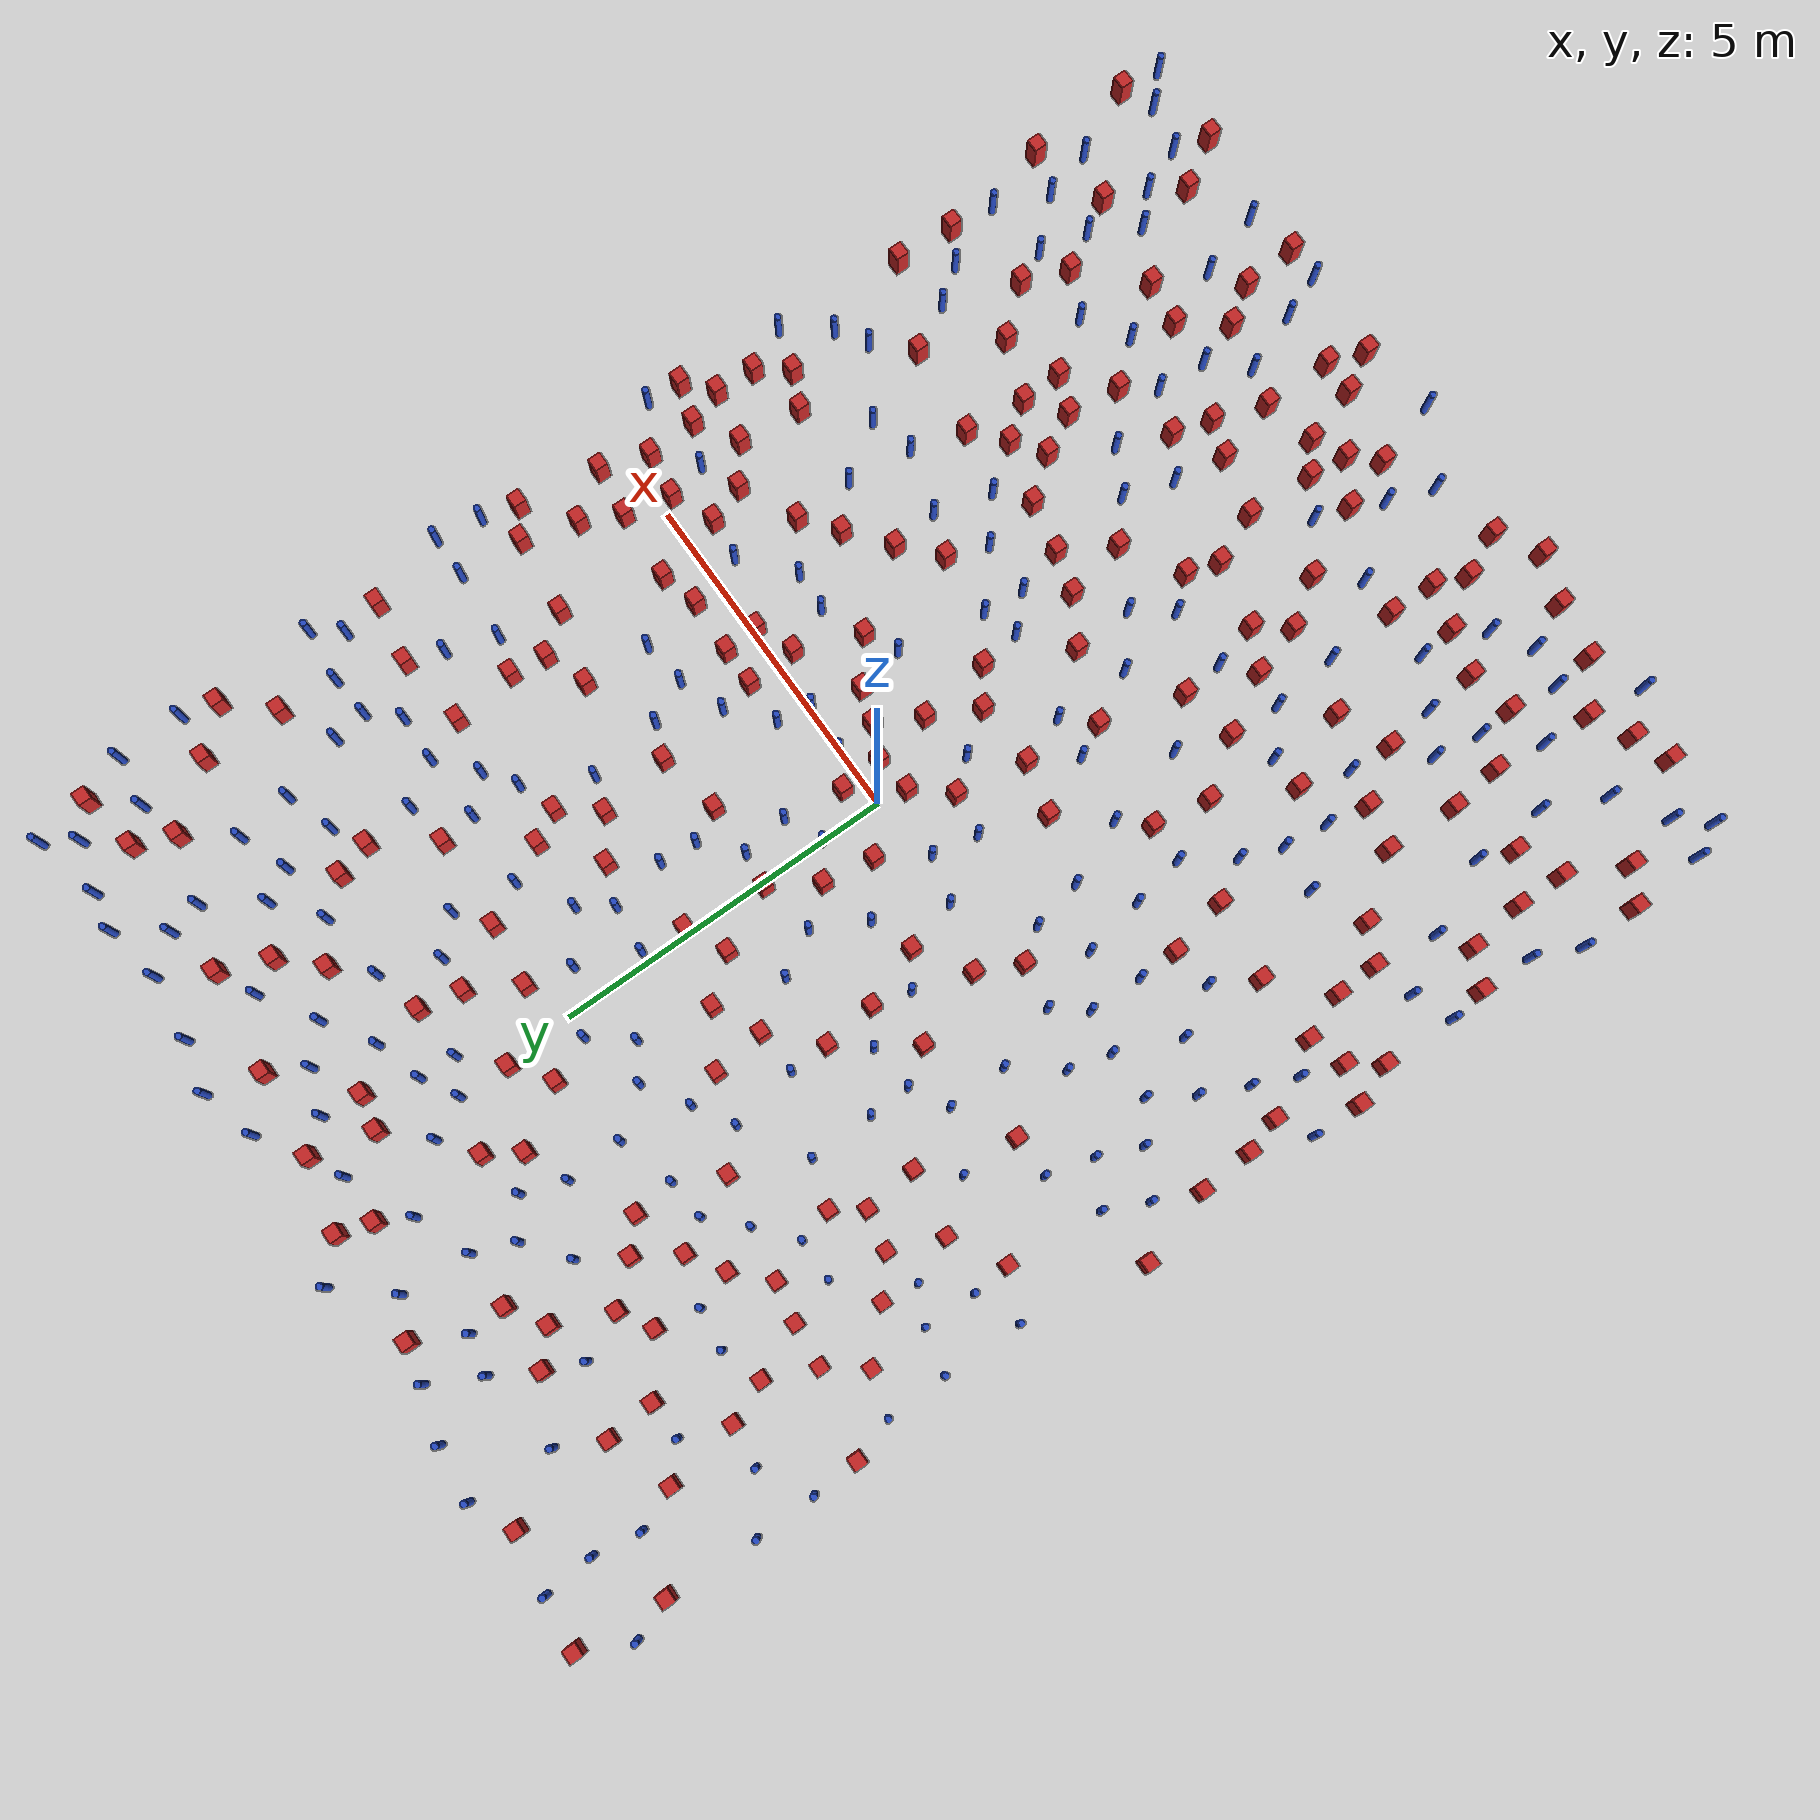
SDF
<sdf version="1.6">
  <model name="dense_70"><model name="pole_obstacle0">
  <static>true</static>
  <pose frame="">-1.75917018669 5.33562779901 2.88873142074e-08 -9.90536689852e-09 4.60219948989e-07 -1.2096599496e-07</pose>
  <link name="link">
  <pose frame="">0 0 0.3 0 -0 0</pose>
    <inertial>
      <mass>1</mass>
      <inertia>
        <ixx>0.145833</ixx>
        <ixy>0</ixy>
        <ixz>0</ixz>
        <iyy>0.145833</iyy>
        <iyz>0</iyz>
        <izz>0.125</izz>
      </inertia>
    </inertial>
    <collision name="collision">
      <geometry>
        <cylinder>
          <radius>0.05</radius>
          <length>.6</length>
        </cylinder>
      </geometry>
      <max_contacts>10</max_contacts>
      <surface>
        <contact>
          <ode/>
        </contact>
        <bounce/>
        <friction>
          <torsional>
            <ode/>
          </torsional>
          <ode/>
        </friction>
      </surface>
    </collision>
    <visual name="visual">
      <geometry>
        <cylinder>
          <radius>0.05</radius>
          <length>.6</length>
        </cylinder>
      </geometry>
      <material>
        <script>
          <name>Gazebo/Blue</name>
          <uri>file://media/materials/scripts/gazebo.material</uri>
        </script>
      </material>
    </visual>
    <self_collide>0</self_collide>
    <kinematic>0</kinematic>
  </link>
</model>
<model name="pole_obstacle1">
  <static>true</static>
  <pose frame="">-4.70056590658 5.76526155883 2.88873142074e-08 -9.90536690842e-09 4.60219948965e-07 -1.20965994976e-07</pose>
  <link name="link">
  <pose frame="">0 0 0.3 0 -0 0</pose>
    <inertial>
      <mass>1</mass>
      <inertia>
        <ixx>0.145833</ixx>
        <ixy>0</ixy>
        <ixz>0</ixz>
        <iyy>0.145833</iyy>
        <iyz>0</iyz>
        <izz>0.125</izz>
      </inertia>
    </inertial>
    <collision name="collision">
      <geometry>
        <cylinder>
          <radius>0.05</radius>
          <length>.6</length>
        </cylinder>
      </geometry>
      <max_contacts>10</max_contacts>
      <surface>
        <contact>
          <ode/>
        </contact>
        <bounce/>
        <friction>
          <torsional>
            <ode/>
          </torsional>
          <ode/>
        </friction>
      </surface>
    </collision>
    <visual name="visual">
      <geometry>
        <cylinder>
          <radius>0.05</radius>
          <length>.6</length>
        </cylinder>
      </geometry>
      <material>
        <script>
          <name>Gazebo/Blue</name>
          <uri>file://media/materials/scripts/gazebo.material</uri>
        </script>
      </material>
    </visual>
    <self_collide>0</self_collide>
    <kinematic>0</kinematic>
  </link>
</model>
<model name="square_post_obstacle0">
  <static>true</static>
  <pose frame="">1.72924373991 -6.90918453501 8.22691968438e-08 7.2212513382e-06 -7.54495500217e-07 2.29674213826e-05</pose>
  <link name="link">
    <pose frame="">0 0 0.25 0 -0 0</pose>
    <inertial>
      <mass>100</mass>
      <inertia>
        <ixx>0.166667</ixx>
        <ixy>0</ixy>
        <ixz>0</ixz>
        <iyy>0.166667</iyy>
        <iyz>0</iyz>
        <izz>0.166667</izz>
      </inertia>
    </inertial>
    <collision name="collision">
      <geometry>
        <box>
          <size>.2 .2 .5</size>
        </box>
      </geometry>
      <max_contacts>10</max_contacts>
      <surface>
        <contact>
          <ode/>
        </contact>
        <bounce/>
        <friction>
          <torsional>
            <ode/>
          </torsional>
          <ode/>
        </friction>
      </surface>
    </collision>
    <visual name="visual">
      <geometry>
        <box>
          <size>.2 .2 .5</size>
        </box>
      </geometry>
      <material>
        <script>
          <name>Gazebo/Red</name>
          <uri>file://media/materials/scripts/gazebo.material</uri>
        </script>
      </material>
    </visual>
    <self_collide>0</self_collide>
    <kinematic>0</kinematic>
  </link>
</model>
<model name="square_post_obstacle1">
  <static>true</static>
  <pose frame="">5.80485154844 1.86248550095 8.22691968438e-08 7.2212513382e-06 -7.54495500217e-07 2.29674213826e-05</pose>
  <link name="link">
    <pose frame="">0 0 0.25 0 -0 0</pose>
    <inertial>
      <mass>100</mass>
      <inertia>
        <ixx>0.166667</ixx>
        <ixy>0</ixy>
        <ixz>0</ixz>
        <iyy>0.166667</iyy>
        <iyz>0</iyz>
        <izz>0.166667</izz>
      </inertia>
    </inertial>
    <collision name="collision">
      <geometry>
        <box>
          <size>.2 .2 .5</size>
        </box>
      </geometry>
      <max_contacts>10</max_contacts>
      <surface>
        <contact>
          <ode/>
        </contact>
        <bounce/>
        <friction>
          <torsional>
            <ode/>
          </torsional>
          <ode/>
        </friction>
      </surface>
    </collision>
    <visual name="visual">
      <geometry>
        <box>
          <size>.2 .2 .5</size>
        </box>
      </geometry>
      <material>
        <script>
          <name>Gazebo/Red</name>
          <uri>file://media/materials/scripts/gazebo.material</uri>
        </script>
      </material>
    </visual>
    <self_collide>0</self_collide>
    <kinematic>0</kinematic>
  </link>
</model>
<model name="pole_obstacle2">
  <static>true</static>
  <pose frame="">-4.45726668055 8.1890683616 2.88873142074e-08 -9.9053668967e-09 4.60219948993e-07 -1.20965994957e-07</pose>
  <link name="link">
  <pose frame="">0 0 0.3 0 -0 0</pose>
    <inertial>
      <mass>1</mass>
      <inertia>
        <ixx>0.145833</ixx>
        <ixy>0</ixy>
        <ixz>0</ixz>
        <iyy>0.145833</iyy>
        <iyz>0</iyz>
        <izz>0.125</izz>
      </inertia>
    </inertial>
    <collision name="collision">
      <geometry>
        <cylinder>
          <radius>0.05</radius>
          <length>.6</length>
        </cylinder>
      </geometry>
      <max_contacts>10</max_contacts>
      <surface>
        <contact>
          <ode/>
        </contact>
        <bounce/>
        <friction>
          <torsional>
            <ode/>
          </torsional>
          <ode/>
        </friction>
      </surface>
    </collision>
    <visual name="visual">
      <geometry>
        <cylinder>
          <radius>0.05</radius>
          <length>.6</length>
        </cylinder>
      </geometry>
      <material>
        <script>
          <name>Gazebo/Blue</name>
          <uri>file://media/materials/scripts/gazebo.material</uri>
        </script>
      </material>
    </visual>
    <self_collide>0</self_collide>
    <kinematic>0</kinematic>
  </link>
</model>
<model name="pole_obstacle3">
  <static>true</static>
  <pose frame="">-0.223066158163 -7.18615148607 2.88873142074e-08 -9.90536689703e-09 4.60219948992e-07 -1.20965994959e-07</pose>
  <link name="link">
  <pose frame="">0 0 0.3 0 -0 0</pose>
    <inertial>
      <mass>1</mass>
      <inertia>
        <ixx>0.145833</ixx>
        <ixy>0</ixy>
        <ixz>0</ixz>
        <iyy>0.145833</iyy>
        <iyz>0</iyz>
        <izz>0.125</izz>
      </inertia>
    </inertial>
    <collision name="collision">
      <geometry>
        <cylinder>
          <radius>0.05</radius>
          <length>.6</length>
        </cylinder>
      </geometry>
      <max_contacts>10</max_contacts>
      <surface>
        <contact>
          <ode/>
        </contact>
        <bounce/>
        <friction>
          <torsional>
            <ode/>
          </torsional>
          <ode/>
        </friction>
      </surface>
    </collision>
    <visual name="visual">
      <geometry>
        <cylinder>
          <radius>0.05</radius>
          <length>.6</length>
        </cylinder>
      </geometry>
      <material>
        <script>
          <name>Gazebo/Blue</name>
          <uri>file://media/materials/scripts/gazebo.material</uri>
        </script>
      </material>
    </visual>
    <self_collide>0</self_collide>
    <kinematic>0</kinematic>
  </link>
</model>
<model name="pole_obstacle4">
  <static>true</static>
  <pose frame="">-5.26204661042 -6.04021006836 2.88873142074e-08 -9.90536690842e-09 4.60219948965e-07 -1.20965994976e-07</pose>
  <link name="link">
  <pose frame="">0 0 0.3 0 -0 0</pose>
    <inertial>
      <mass>1</mass>
      <inertia>
        <ixx>0.145833</ixx>
        <ixy>0</ixy>
        <ixz>0</ixz>
        <iyy>0.145833</iyy>
        <iyz>0</iyz>
        <izz>0.125</izz>
      </inertia>
    </inertial>
    <collision name="collision">
      <geometry>
        <cylinder>
          <radius>0.05</radius>
          <length>.6</length>
        </cylinder>
      </geometry>
      <max_contacts>10</max_contacts>
      <surface>
        <contact>
          <ode/>
        </contact>
        <bounce/>
        <friction>
          <torsional>
            <ode/>
          </torsional>
          <ode/>
        </friction>
      </surface>
    </collision>
    <visual name="visual">
      <geometry>
        <cylinder>
          <radius>0.05</radius>
          <length>.6</length>
        </cylinder>
      </geometry>
      <material>
        <script>
          <name>Gazebo/Blue</name>
          <uri>file://media/materials/scripts/gazebo.material</uri>
        </script>
      </material>
    </visual>
    <self_collide>0</self_collide>
    <kinematic>0</kinematic>
  </link>
</model>
<model name="pole_obstacle5">
  <static>true</static>
  <pose frame="">5.67499437362 -5.37067513522 2.88873142074e-08 -9.90536690842e-09 4.60219948965e-07 -1.20965994976e-07</pose>
  <link name="link">
  <pose frame="">0 0 0.3 0 -0 0</pose>
    <inertial>
      <mass>1</mass>
      <inertia>
        <ixx>0.145833</ixx>
        <ixy>0</ixy>
        <ixz>0</ixz>
        <iyy>0.145833</iyy>
        <iyz>0</iyz>
        <izz>0.125</izz>
      </inertia>
    </inertial>
    <collision name="collision">
      <geometry>
        <cylinder>
          <radius>0.05</radius>
          <length>.6</length>
        </cylinder>
      </geometry>
      <max_contacts>10</max_contacts>
      <surface>
        <contact>
          <ode/>
        </contact>
        <bounce/>
        <friction>
          <torsional>
            <ode/>
          </torsional>
          <ode/>
        </friction>
      </surface>
    </collision>
    <visual name="visual">
      <geometry>
        <cylinder>
          <radius>0.05</radius>
          <length>.6</length>
        </cylinder>
      </geometry>
      <material>
        <script>
          <name>Gazebo/Blue</name>
          <uri>file://media/materials/scripts/gazebo.material</uri>
        </script>
      </material>
    </visual>
    <self_collide>0</self_collide>
    <kinematic>0</kinematic>
  </link>
</model>
<model name="pole_obstacle6">
  <static>true</static>
  <pose frame="">1.87166272618 4.55720041785 2.88873142074e-08 -9.90536689852e-09 4.60219948989e-07 -1.2096599496e-07</pose>
  <link name="link">
  <pose frame="">0 0 0.3 0 -0 0</pose>
    <inertial>
      <mass>1</mass>
      <inertia>
        <ixx>0.145833</ixx>
        <ixy>0</ixy>
        <ixz>0</ixz>
        <iyy>0.145833</iyy>
        <iyz>0</iyz>
        <izz>0.125</izz>
      </inertia>
    </inertial>
    <collision name="collision">
      <geometry>
        <cylinder>
          <radius>0.05</radius>
          <length>.6</length>
        </cylinder>
      </geometry>
      <max_contacts>10</max_contacts>
      <surface>
        <contact>
          <ode/>
        </contact>
        <bounce/>
        <friction>
          <torsional>
            <ode/>
          </torsional>
          <ode/>
        </friction>
      </surface>
    </collision>
    <visual name="visual">
      <geometry>
        <cylinder>
          <radius>0.05</radius>
          <length>.6</length>
        </cylinder>
      </geometry>
      <material>
        <script>
          <name>Gazebo/Blue</name>
          <uri>file://media/materials/scripts/gazebo.material</uri>
        </script>
      </material>
    </visual>
    <self_collide>0</self_collide>
    <kinematic>0</kinematic>
  </link>
</model>
<model name="square_post_obstacle2">
  <static>true</static>
  <pose frame="">0.221696725759 -1.90196667918 8.22691968438e-08 7.2212513382e-06 -7.54495500217e-07 2.29674213826e-05</pose>
  <link name="link">
    <pose frame="">0 0 0.25 0 -0 0</pose>
    <inertial>
      <mass>100</mass>
      <inertia>
        <ixx>0.166667</ixx>
        <ixy>0</ixy>
        <ixz>0</ixz>
        <iyy>0.166667</iyy>
        <iyz>0</iyz>
        <izz>0.166667</izz>
      </inertia>
    </inertial>
    <collision name="collision">
      <geometry>
        <box>
          <size>.2 .2 .5</size>
        </box>
      </geometry>
      <max_contacts>10</max_contacts>
      <surface>
        <contact>
          <ode/>
        </contact>
        <bounce/>
        <friction>
          <torsional>
            <ode/>
          </torsional>
          <ode/>
        </friction>
      </surface>
    </collision>
    <visual name="visual">
      <geometry>
        <box>
          <size>.2 .2 .5</size>
        </box>
      </geometry>
      <material>
        <script>
          <name>Gazebo/Red</name>
          <uri>file://media/materials/scripts/gazebo.material</uri>
        </script>
      </material>
    </visual>
    <self_collide>0</self_collide>
    <kinematic>0</kinematic>
  </link>
</model>
<model name="square_post_obstacle3">
  <static>true</static>
  <pose frame="">-5.62151948386 -3.42446716188 8.22691968438e-08 7.2212513382e-06 -7.54495500217e-07 2.29674213826e-05</pose>
  <link name="link">
    <pose frame="">0 0 0.25 0 -0 0</pose>
    <inertial>
      <mass>100</mass>
      <inertia>
        <ixx>0.166667</ixx>
        <ixy>0</ixy>
        <ixz>0</ixz>
        <iyy>0.166667</iyy>
        <iyz>0</iyz>
        <izz>0.166667</izz>
      </inertia>
    </inertial>
    <collision name="collision">
      <geometry>
        <box>
          <size>.2 .2 .5</size>
        </box>
      </geometry>
      <max_contacts>10</max_contacts>
      <surface>
        <contact>
          <ode/>
        </contact>
        <bounce/>
        <friction>
          <torsional>
            <ode/>
          </torsional>
          <ode/>
        </friction>
      </surface>
    </collision>
    <visual name="visual">
      <geometry>
        <box>
          <size>.2 .2 .5</size>
        </box>
      </geometry>
      <material>
        <script>
          <name>Gazebo/Red</name>
          <uri>file://media/materials/scripts/gazebo.material</uri>
        </script>
      </material>
    </visual>
    <self_collide>0</self_collide>
    <kinematic>0</kinematic>
  </link>
</model>
<model name="square_post_obstacle4">
  <static>true</static>
  <pose frame="">1.47101425126 -7.66922234717 8.22691968438e-08 7.2212513382e-06 -7.54495500217e-07 2.29674213826e-05</pose>
  <link name="link">
    <pose frame="">0 0 0.25 0 -0 0</pose>
    <inertial>
      <mass>100</mass>
      <inertia>
        <ixx>0.166667</ixx>
        <ixy>0</ixy>
        <ixz>0</ixz>
        <iyy>0.166667</iyy>
        <iyz>0</iyz>
        <izz>0.166667</izz>
      </inertia>
    </inertial>
    <collision name="collision">
      <geometry>
        <box>
          <size>.2 .2 .5</size>
        </box>
      </geometry>
      <max_contacts>10</max_contacts>
      <surface>
        <contact>
          <ode/>
        </contact>
        <bounce/>
        <friction>
          <torsional>
            <ode/>
          </torsional>
          <ode/>
        </friction>
      </surface>
    </collision>
    <visual name="visual">
      <geometry>
        <box>
          <size>.2 .2 .5</size>
        </box>
      </geometry>
      <material>
        <script>
          <name>Gazebo/Red</name>
          <uri>file://media/materials/scripts/gazebo.material</uri>
        </script>
      </material>
    </visual>
    <self_collide>0</self_collide>
    <kinematic>0</kinematic>
  </link>
</model>
<model name="pole_obstacle7">
  <static>true</static>
  <pose frame="">-3.41852707502 -3.4730363077 2.88873142074e-08 -9.90536690232e-09 4.6021994898e-07 -1.20965994968e-07</pose>
  <link name="link">
  <pose frame="">0 0 0.3 0 -0 0</pose>
    <inertial>
      <mass>1</mass>
      <inertia>
        <ixx>0.145833</ixx>
        <ixy>0</ixy>
        <ixz>0</ixz>
        <iyy>0.145833</iyy>
        <iyz>0</iyz>
        <izz>0.125</izz>
      </inertia>
    </inertial>
    <collision name="collision">
      <geometry>
        <cylinder>
          <radius>0.05</radius>
          <length>.6</length>
        </cylinder>
      </geometry>
      <max_contacts>10</max_contacts>
      <surface>
        <contact>
          <ode/>
        </contact>
        <bounce/>
        <friction>
          <torsional>
            <ode/>
          </torsional>
          <ode/>
        </friction>
      </surface>
    </collision>
    <visual name="visual">
      <geometry>
        <cylinder>
          <radius>0.05</radius>
          <length>.6</length>
        </cylinder>
      </geometry>
      <material>
        <script>
          <name>Gazebo/Blue</name>
          <uri>file://media/materials/scripts/gazebo.material</uri>
        </script>
      </material>
    </visual>
    <self_collide>0</self_collide>
    <kinematic>0</kinematic>
  </link>
</model>
<model name="pole_obstacle8">
  <static>true</static>
  <pose frame="">-6.08702871767 0.780970293844 2.88873142074e-08 -9.90536689837e-09 4.60219948989e-07 -1.2096599496e-07</pose>
  <link name="link">
  <pose frame="">0 0 0.3 0 -0 0</pose>
    <inertial>
      <mass>1</mass>
      <inertia>
        <ixx>0.145833</ixx>
        <ixy>0</ixy>
        <ixz>0</ixz>
        <iyy>0.145833</iyy>
        <iyz>0</iyz>
        <izz>0.125</izz>
      </inertia>
    </inertial>
    <collision name="collision">
      <geometry>
        <cylinder>
          <radius>0.05</radius>
          <length>.6</length>
        </cylinder>
      </geometry>
      <max_contacts>10</max_contacts>
      <surface>
        <contact>
          <ode/>
        </contact>
        <bounce/>
        <friction>
          <torsional>
            <ode/>
          </torsional>
          <ode/>
        </friction>
      </surface>
    </collision>
    <visual name="visual">
      <geometry>
        <cylinder>
          <radius>0.05</radius>
          <length>.6</length>
        </cylinder>
      </geometry>
      <material>
        <script>
          <name>Gazebo/Blue</name>
          <uri>file://media/materials/scripts/gazebo.material</uri>
        </script>
      </material>
    </visual>
    <self_collide>0</self_collide>
    <kinematic>0</kinematic>
  </link>
</model>
<model name="square_post_obstacle5">
  <static>true</static>
  <pose frame="">-6.39773132126 -2.92644080052 8.22691968438e-08 7.2212513382e-06 -7.54495500217e-07 2.29674213826e-05</pose>
  <link name="link">
    <pose frame="">0 0 0.25 0 -0 0</pose>
    <inertial>
      <mass>100</mass>
      <inertia>
        <ixx>0.166667</ixx>
        <ixy>0</ixy>
        <ixz>0</ixz>
        <iyy>0.166667</iyy>
        <iyz>0</iyz>
        <izz>0.166667</izz>
      </inertia>
    </inertial>
    <collision name="collision">
      <geometry>
        <box>
          <size>.2 .2 .5</size>
        </box>
      </geometry>
      <max_contacts>10</max_contacts>
      <surface>
        <contact>
          <ode/>
        </contact>
        <bounce/>
        <friction>
          <torsional>
            <ode/>
          </torsional>
          <ode/>
        </friction>
      </surface>
    </collision>
    <visual name="visual">
      <geometry>
        <box>
          <size>.2 .2 .5</size>
        </box>
      </geometry>
      <material>
        <script>
          <name>Gazebo/Red</name>
          <uri>file://media/materials/scripts/gazebo.material</uri>
        </script>
      </material>
    </visual>
    <self_collide>0</self_collide>
    <kinematic>0</kinematic>
  </link>
</model>
<model name="square_post_obstacle6">
  <static>true</static>
  <pose frame="">1.56429771834 5.11346397631 8.22691968438e-08 7.2212513382e-06 -7.54495500217e-07 2.29674213826e-05</pose>
  <link name="link">
    <pose frame="">0 0 0.25 0 -0 0</pose>
    <inertial>
      <mass>100</mass>
      <inertia>
        <ixx>0.166667</ixx>
        <ixy>0</ixy>
        <ixz>0</ixz>
        <iyy>0.166667</iyy>
        <iyz>0</iyz>
        <izz>0.166667</izz>
      </inertia>
    </inertial>
    <collision name="collision">
      <geometry>
        <box>
          <size>.2 .2 .5</size>
        </box>
      </geometry>
      <max_contacts>10</max_contacts>
      <surface>
        <contact>
          <ode/>
        </contact>
        <bounce/>
        <friction>
          <torsional>
            <ode/>
          </torsional>
          <ode/>
        </friction>
      </surface>
    </collision>
    <visual name="visual">
      <geometry>
        <box>
          <size>.2 .2 .5</size>
        </box>
      </geometry>
      <material>
        <script>
          <name>Gazebo/Red</name>
          <uri>file://media/materials/scripts/gazebo.material</uri>
        </script>
      </material>
    </visual>
    <self_collide>0</self_collide>
    <kinematic>0</kinematic>
  </link>
</model>
<model name="square_post_obstacle7">
  <static>true</static>
  <pose frame="">-2.65024119042 5.69490103265 8.22691968438e-08 7.2212513382e-06 -7.54495500217e-07 2.29674213826e-05</pose>
  <link name="link">
    <pose frame="">0 0 0.25 0 -0 0</pose>
    <inertial>
      <mass>100</mass>
      <inertia>
        <ixx>0.166667</ixx>
        <ixy>0</ixy>
        <ixz>0</ixz>
        <iyy>0.166667</iyy>
        <iyz>0</iyz>
        <izz>0.166667</izz>
      </inertia>
    </inertial>
    <collision name="collision">
      <geometry>
        <box>
          <size>.2 .2 .5</size>
        </box>
      </geometry>
      <max_contacts>10</max_contacts>
      <surface>
        <contact>
          <ode/>
        </contact>
        <bounce/>
        <friction>
          <torsional>
            <ode/>
          </torsional>
          <ode/>
        </friction>
      </surface>
    </collision>
    <visual name="visual">
      <geometry>
        <box>
          <size>.2 .2 .5</size>
        </box>
      </geometry>
      <material>
        <script>
          <name>Gazebo/Red</name>
          <uri>file://media/materials/scripts/gazebo.material</uri>
        </script>
      </material>
    </visual>
    <self_collide>0</self_collide>
    <kinematic>0</kinematic>
  </link>
</model>
<model name="pole_obstacle9">
  <static>true</static>
  <pose frame="">-5.60788954177 -8.01371110021 2.88873142074e-08 -9.9053669103e-09 4.60219948961e-07 -1.20965994981e-07</pose>
  <link name="link">
  <pose frame="">0 0 0.3 0 -0 0</pose>
    <inertial>
      <mass>1</mass>
      <inertia>
        <ixx>0.145833</ixx>
        <ixy>0</ixy>
        <ixz>0</ixz>
        <iyy>0.145833</iyy>
        <iyz>0</iyz>
        <izz>0.125</izz>
      </inertia>
    </inertial>
    <collision name="collision">
      <geometry>
        <cylinder>
          <radius>0.05</radius>
          <length>.6</length>
        </cylinder>
      </geometry>
      <max_contacts>10</max_contacts>
      <surface>
        <contact>
          <ode/>
        </contact>
        <bounce/>
        <friction>
          <torsional>
            <ode/>
          </torsional>
          <ode/>
        </friction>
      </surface>
    </collision>
    <visual name="visual">
      <geometry>
        <cylinder>
          <radius>0.05</radius>
          <length>.6</length>
        </cylinder>
      </geometry>
      <material>
        <script>
          <name>Gazebo/Blue</name>
          <uri>file://media/materials/scripts/gazebo.material</uri>
        </script>
      </material>
    </visual>
    <self_collide>0</self_collide>
    <kinematic>0</kinematic>
  </link>
</model>
<model name="pole_obstacle10">
  <static>true</static>
  <pose frame="">4.44744639522 -3.07453793529 2.88873142074e-08 -9.90536690245e-09 4.6021994898e-07 -1.20965994966e-07</pose>
  <link name="link">
  <pose frame="">0 0 0.3 0 -0 0</pose>
    <inertial>
      <mass>1</mass>
      <inertia>
        <ixx>0.145833</ixx>
        <ixy>0</ixy>
        <ixz>0</ixz>
        <iyy>0.145833</iyy>
        <iyz>0</iyz>
        <izz>0.125</izz>
      </inertia>
    </inertial>
    <collision name="collision">
      <geometry>
        <cylinder>
          <radius>0.05</radius>
          <length>.6</length>
        </cylinder>
      </geometry>
      <max_contacts>10</max_contacts>
      <surface>
        <contact>
          <ode/>
        </contact>
        <bounce/>
        <friction>
          <torsional>
            <ode/>
          </torsional>
          <ode/>
        </friction>
      </surface>
    </collision>
    <visual name="visual">
      <geometry>
        <cylinder>
          <radius>0.05</radius>
          <length>.6</length>
        </cylinder>
      </geometry>
      <material>
        <script>
          <name>Gazebo/Blue</name>
          <uri>file://media/materials/scripts/gazebo.material</uri>
        </script>
      </material>
    </visual>
    <self_collide>0</self_collide>
    <kinematic>0</kinematic>
  </link>
</model>
<model name="pole_obstacle11">
  <static>true</static>
  <pose frame="">2.61440782523 1.80878692361 2.88873142074e-08 -9.90536689395e-09 4.60219949e-07 -1.20965994953e-07</pose>
  <link name="link">
  <pose frame="">0 0 0.3 0 -0 0</pose>
    <inertial>
      <mass>1</mass>
      <inertia>
        <ixx>0.145833</ixx>
        <ixy>0</ixy>
        <ixz>0</ixz>
        <iyy>0.145833</iyy>
        <iyz>0</iyz>
        <izz>0.125</izz>
      </inertia>
    </inertial>
    <collision name="collision">
      <geometry>
        <cylinder>
          <radius>0.05</radius>
          <length>.6</length>
        </cylinder>
      </geometry>
      <max_contacts>10</max_contacts>
      <surface>
        <contact>
          <ode/>
        </contact>
        <bounce/>
        <friction>
          <torsional>
            <ode/>
          </torsional>
          <ode/>
        </friction>
      </surface>
    </collision>
    <visual name="visual">
      <geometry>
        <cylinder>
          <radius>0.05</radius>
          <length>.6</length>
        </cylinder>
      </geometry>
      <material>
        <script>
          <name>Gazebo/Blue</name>
          <uri>file://media/materials/scripts/gazebo.material</uri>
        </script>
      </material>
    </visual>
    <self_collide>0</self_collide>
    <kinematic>0</kinematic>
  </link>
</model>
<model name="pole_obstacle12">
  <static>true</static>
  <pose frame="">-4.53100883687 -0.543912162179 2.88873142074e-08 -9.90536689968e-09 4.60219948986e-07 -1.20965994963e-07</pose>
  <link name="link">
  <pose frame="">0 0 0.3 0 -0 0</pose>
    <inertial>
      <mass>1</mass>
      <inertia>
        <ixx>0.145833</ixx>
        <ixy>0</ixy>
        <ixz>0</ixz>
        <iyy>0.145833</iyy>
        <iyz>0</iyz>
        <izz>0.125</izz>
      </inertia>
    </inertial>
    <collision name="collision">
      <geometry>
        <cylinder>
          <radius>0.05</radius>
          <length>.6</length>
        </cylinder>
      </geometry>
      <max_contacts>10</max_contacts>
      <surface>
        <contact>
          <ode/>
        </contact>
        <bounce/>
        <friction>
          <torsional>
            <ode/>
          </torsional>
          <ode/>
        </friction>
      </surface>
    </collision>
    <visual name="visual">
      <geometry>
        <cylinder>
          <radius>0.05</radius>
          <length>.6</length>
        </cylinder>
      </geometry>
      <material>
        <script>
          <name>Gazebo/Blue</name>
          <uri>file://media/materials/scripts/gazebo.material</uri>
        </script>
      </material>
    </visual>
    <self_collide>0</self_collide>
    <kinematic>0</kinematic>
  </link>
</model>
<model name="square_post_obstacle8">
  <static>true</static>
  <pose frame="">-5.08560462656 -4.32271295964 8.22691968438e-08 7.2212513382e-06 -7.54495500217e-07 2.29674213826e-05</pose>
  <link name="link">
    <pose frame="">0 0 0.25 0 -0 0</pose>
    <inertial>
      <mass>100</mass>
      <inertia>
        <ixx>0.166667</ixx>
        <ixy>0</ixy>
        <ixz>0</ixz>
        <iyy>0.166667</iyy>
        <iyz>0</iyz>
        <izz>0.166667</izz>
      </inertia>
    </inertial>
    <collision name="collision">
      <geometry>
        <box>
          <size>.2 .2 .5</size>
        </box>
      </geometry>
      <max_contacts>10</max_contacts>
      <surface>
        <contact>
          <ode/>
        </contact>
        <bounce/>
        <friction>
          <torsional>
            <ode/>
          </torsional>
          <ode/>
        </friction>
      </surface>
    </collision>
    <visual name="visual">
      <geometry>
        <box>
          <size>.2 .2 .5</size>
        </box>
      </geometry>
      <material>
        <script>
          <name>Gazebo/Red</name>
          <uri>file://media/materials/scripts/gazebo.material</uri>
        </script>
      </material>
    </visual>
    <self_collide>0</self_collide>
    <kinematic>0</kinematic>
  </link>
</model>
<model name="square_post_obstacle9">
  <static>true</static>
  <pose frame="">-4.78377792327 7.54915396914 8.22691968438e-08 7.22125133819e-06 -7.54495500217e-07 2.29674213826e-05</pose>
  <link name="link">
    <pose frame="">0 0 0.25 0 -0 0</pose>
    <inertial>
      <mass>100</mass>
      <inertia>
        <ixx>0.166667</ixx>
        <ixy>0</ixy>
        <ixz>0</ixz>
        <iyy>0.166667</iyy>
        <iyz>0</iyz>
        <izz>0.166667</izz>
      </inertia>
    </inertial>
    <collision name="collision">
      <geometry>
        <box>
          <size>.2 .2 .5</size>
        </box>
      </geometry>
      <max_contacts>10</max_contacts>
      <surface>
        <contact>
          <ode/>
        </contact>
        <bounce/>
        <friction>
          <torsional>
            <ode/>
          </torsional>
          <ode/>
        </friction>
      </surface>
    </collision>
    <visual name="visual">
      <geometry>
        <box>
          <size>.2 .2 .5</size>
        </box>
      </geometry>
      <material>
        <script>
          <name>Gazebo/Red</name>
          <uri>file://media/materials/scripts/gazebo.material</uri>
        </script>
      </material>
    </visual>
    <self_collide>0</self_collide>
    <kinematic>0</kinematic>
  </link>
</model>
<model name="pole_obstacle13">
  <static>true</static>
  <pose frame="">3.20647940545 -0.969881316611 2.88873142074e-08 -9.90536689217e-09 4.60219949004e-07 -1.20965994953e-07</pose>
  <link name="link">
  <pose frame="">0 0 0.3 0 -0 0</pose>
    <inertial>
      <mass>1</mass>
      <inertia>
        <ixx>0.145833</ixx>
        <ixy>0</ixy>
        <ixz>0</ixz>
        <iyy>0.145833</iyy>
        <iyz>0</iyz>
        <izz>0.125</izz>
      </inertia>
    </inertial>
    <collision name="collision">
      <geometry>
        <cylinder>
          <radius>0.05</radius>
          <length>.6</length>
        </cylinder>
      </geometry>
      <max_contacts>10</max_contacts>
      <surface>
        <contact>
          <ode/>
        </contact>
        <bounce/>
        <friction>
          <torsional>
            <ode/>
          </torsional>
          <ode/>
        </friction>
      </surface>
    </collision>
    <visual name="visual">
      <geometry>
        <cylinder>
          <radius>0.05</radius>
          <length>.6</length>
        </cylinder>
      </geometry>
      <material>
        <script>
          <name>Gazebo/Blue</name>
          <uri>file://media/materials/scripts/gazebo.material</uri>
        </script>
      </material>
    </visual>
    <self_collide>0</self_collide>
    <kinematic>0</kinematic>
  </link>
</model>
<model name="square_post_obstacle10">
  <static>true</static>
  <pose frame="">3.87964929043 -1.40677528351 8.22691968438e-08 7.2212513382e-06 -7.54495500217e-07 2.29674213826e-05</pose>
  <link name="link">
    <pose frame="">0 0 0.25 0 -0 0</pose>
    <inertial>
      <mass>100</mass>
      <inertia>
        <ixx>0.166667</ixx>
        <ixy>0</ixy>
        <ixz>0</ixz>
        <iyy>0.166667</iyy>
        <iyz>0</iyz>
        <izz>0.166667</izz>
      </inertia>
    </inertial>
    <collision name="collision">
      <geometry>
        <box>
          <size>.2 .2 .5</size>
        </box>
      </geometry>
      <max_contacts>10</max_contacts>
      <surface>
        <contact>
          <ode/>
        </contact>
        <bounce/>
        <friction>
          <torsional>
            <ode/>
          </torsional>
          <ode/>
        </friction>
      </surface>
    </collision>
    <visual name="visual">
      <geometry>
        <box>
          <size>.2 .2 .5</size>
        </box>
      </geometry>
      <material>
        <script>
          <name>Gazebo/Red</name>
          <uri>file://media/materials/scripts/gazebo.material</uri>
        </script>
      </material>
    </visual>
    <self_collide>0</self_collide>
    <kinematic>0</kinematic>
  </link>
</model>
<model name="square_post_obstacle11">
  <static>true</static>
  <pose frame="">2.86878469184 7.71550263755 8.22691968438e-08 7.2212513382e-06 -7.54495500217e-07 2.29674213826e-05</pose>
  <link name="link">
    <pose frame="">0 0 0.25 0 -0 0</pose>
    <inertial>
      <mass>100</mass>
      <inertia>
        <ixx>0.166667</ixx>
        <ixy>0</ixy>
        <ixz>0</ixz>
        <iyy>0.166667</iyy>
        <iyz>0</iyz>
        <izz>0.166667</izz>
      </inertia>
    </inertial>
    <collision name="collision">
      <geometry>
        <box>
          <size>.2 .2 .5</size>
        </box>
      </geometry>
      <max_contacts>10</max_contacts>
      <surface>
        <contact>
          <ode/>
        </contact>
        <bounce/>
        <friction>
          <torsional>
            <ode/>
          </torsional>
          <ode/>
        </friction>
      </surface>
    </collision>
    <visual name="visual">
      <geometry>
        <box>
          <size>.2 .2 .5</size>
        </box>
      </geometry>
      <material>
        <script>
          <name>Gazebo/Red</name>
          <uri>file://media/materials/scripts/gazebo.material</uri>
        </script>
      </material>
    </visual>
    <self_collide>0</self_collide>
    <kinematic>0</kinematic>
  </link>
</model>
<model name="pole_obstacle14">
  <static>true</static>
  <pose frame="">1.8775066064 9.40847270662 2.88873142074e-08 -9.90536690474e-09 4.60219948974e-07 -1.2096599497e-07</pose>
  <link name="link">
  <pose frame="">0 0 0.3 0 -0 0</pose>
    <inertial>
      <mass>1</mass>
      <inertia>
        <ixx>0.145833</ixx>
        <ixy>0</ixy>
        <ixz>0</ixz>
        <iyy>0.145833</iyy>
        <iyz>0</iyz>
        <izz>0.125</izz>
      </inertia>
    </inertial>
    <collision name="collision">
      <geometry>
        <cylinder>
          <radius>0.05</radius>
          <length>.6</length>
        </cylinder>
      </geometry>
      <max_contacts>10</max_contacts>
      <surface>
        <contact>
          <ode/>
        </contact>
        <bounce/>
        <friction>
          <torsional>
            <ode/>
          </torsional>
          <ode/>
        </friction>
      </surface>
    </collision>
    <visual name="visual">
      <geometry>
        <cylinder>
          <radius>0.05</radius>
          <length>.6</length>
        </cylinder>
      </geometry>
      <material>
        <script>
          <name>Gazebo/Blue</name>
          <uri>file://media/materials/scripts/gazebo.material</uri>
        </script>
      </material>
    </visual>
    <self_collide>0</self_collide>
    <kinematic>0</kinematic>
  </link>
</model>
<model name="pole_obstacle15">
  <static>true</static>
  <pose frame="">-1.13466148341 -4.8690241705 2.88873142074e-08 -9.90536689852e-09 4.60219948989e-07 -1.2096599496e-07</pose>
  <link name="link">
  <pose frame="">0 0 0.3 0 -0 0</pose>
    <inertial>
      <mass>1</mass>
      <inertia>
        <ixx>0.145833</ixx>
        <ixy>0</ixy>
        <ixz>0</ixz>
        <iyy>0.145833</iyy>
        <iyz>0</iyz>
        <izz>0.125</izz>
      </inertia>
    </inertial>
    <collision name="collision">
      <geometry>
        <cylinder>
          <radius>0.05</radius>
          <length>.6</length>
        </cylinder>
      </geometry>
      <max_contacts>10</max_contacts>
      <surface>
        <contact>
          <ode/>
        </contact>
        <bounce/>
        <friction>
          <torsional>
            <ode/>
          </torsional>
          <ode/>
        </friction>
      </surface>
    </collision>
    <visual name="visual">
      <geometry>
        <cylinder>
          <radius>0.05</radius>
          <length>.6</length>
        </cylinder>
      </geometry>
      <material>
        <script>
          <name>Gazebo/Blue</name>
          <uri>file://media/materials/scripts/gazebo.material</uri>
        </script>
      </material>
    </visual>
    <self_collide>0</self_collide>
    <kinematic>0</kinematic>
  </link>
</model>
<model name="square_post_obstacle12">
  <static>true</static>
  <pose frame="">-6.67316931984 -4.98831161575 8.22691968438e-08 7.2212513382e-06 -7.54495500217e-07 2.29674213826e-05</pose>
  <link name="link">
    <pose frame="">0 0 0.25 0 -0 0</pose>
    <inertial>
      <mass>100</mass>
      <inertia>
        <ixx>0.166667</ixx>
        <ixy>0</ixy>
        <ixz>0</ixz>
        <iyy>0.166667</iyy>
        <iyz>0</iyz>
        <izz>0.166667</izz>
      </inertia>
    </inertial>
    <collision name="collision">
      <geometry>
        <box>
          <size>.2 .2 .5</size>
        </box>
      </geometry>
      <max_contacts>10</max_contacts>
      <surface>
        <contact>
          <ode/>
        </contact>
        <bounce/>
        <friction>
          <torsional>
            <ode/>
          </torsional>
          <ode/>
        </friction>
      </surface>
    </collision>
    <visual name="visual">
      <geometry>
        <box>
          <size>.2 .2 .5</size>
        </box>
      </geometry>
      <material>
        <script>
          <name>Gazebo/Red</name>
          <uri>file://media/materials/scripts/gazebo.material</uri>
        </script>
      </material>
    </visual>
    <self_collide>0</self_collide>
    <kinematic>0</kinematic>
  </link>
</model>
<model name="pole_obstacle16">
  <static>true</static>
  <pose frame="">1.67860031516 0.463733786969 2.88873142074e-08 -9.90536689788e-09 4.6021994899e-07 -1.2096599496e-07</pose>
  <link name="link">
  <pose frame="">0 0 0.3 0 -0 0</pose>
    <inertial>
      <mass>1</mass>
      <inertia>
        <ixx>0.145833</ixx>
        <ixy>0</ixy>
        <ixz>0</ixz>
        <iyy>0.145833</iyy>
        <iyz>0</iyz>
        <izz>0.125</izz>
      </inertia>
    </inertial>
    <collision name="collision">
      <geometry>
        <cylinder>
          <radius>0.05</radius>
          <length>.6</length>
        </cylinder>
      </geometry>
      <max_contacts>10</max_contacts>
      <surface>
        <contact>
          <ode/>
        </contact>
        <bounce/>
        <friction>
          <torsional>
            <ode/>
          </torsional>
          <ode/>
        </friction>
      </surface>
    </collision>
    <visual name="visual">
      <geometry>
        <cylinder>
          <radius>0.05</radius>
          <length>.6</length>
        </cylinder>
      </geometry>
      <material>
        <script>
          <name>Gazebo/Blue</name>
          <uri>file://media/materials/scripts/gazebo.material</uri>
        </script>
      </material>
    </visual>
    <self_collide>0</self_collide>
    <kinematic>0</kinematic>
  </link>
</model>
<model name="pole_obstacle17">
  <static>true</static>
  <pose frame="">-0.0674727620844 6.71778246287 2.88873142074e-08 -9.90536689653e-09 4.60219948994e-07 -1.20965994959e-07</pose>
  <link name="link">
  <pose frame="">0 0 0.3 0 -0 0</pose>
    <inertial>
      <mass>1</mass>
      <inertia>
        <ixx>0.145833</ixx>
        <ixy>0</ixy>
        <ixz>0</ixz>
        <iyy>0.145833</iyy>
        <iyz>0</iyz>
        <izz>0.125</izz>
      </inertia>
    </inertial>
    <collision name="collision">
      <geometry>
        <cylinder>
          <radius>0.05</radius>
          <length>.6</length>
        </cylinder>
      </geometry>
      <max_contacts>10</max_contacts>
      <surface>
        <contact>
          <ode/>
        </contact>
        <bounce/>
        <friction>
          <torsional>
            <ode/>
          </torsional>
          <ode/>
        </friction>
      </surface>
    </collision>
    <visual name="visual">
      <geometry>
        <cylinder>
          <radius>0.05</radius>
          <length>.6</length>
        </cylinder>
      </geometry>
      <material>
        <script>
          <name>Gazebo/Blue</name>
          <uri>file://media/materials/scripts/gazebo.material</uri>
        </script>
      </material>
    </visual>
    <self_collide>0</self_collide>
    <kinematic>0</kinematic>
  </link>
</model>
<model name="square_post_obstacle13">
  <static>true</static>
  <pose frame="">1.01495852833 -4.76390678284 8.22691968438e-08 7.2212513382e-06 -7.54495500217e-07 2.29674213826e-05</pose>
  <link name="link">
    <pose frame="">0 0 0.25 0 -0 0</pose>
    <inertial>
      <mass>100</mass>
      <inertia>
        <ixx>0.166667</ixx>
        <ixy>0</ixy>
        <ixz>0</ixz>
        <iyy>0.166667</iyy>
        <iyz>0</iyz>
        <izz>0.166667</izz>
      </inertia>
    </inertial>
    <collision name="collision">
      <geometry>
        <box>
          <size>.2 .2 .5</size>
        </box>
      </geometry>
      <max_contacts>10</max_contacts>
      <surface>
        <contact>
          <ode/>
        </contact>
        <bounce/>
        <friction>
          <torsional>
            <ode/>
          </torsional>
          <ode/>
        </friction>
      </surface>
    </collision>
    <visual name="visual">
      <geometry>
        <box>
          <size>.2 .2 .5</size>
        </box>
      </geometry>
      <material>
        <script>
          <name>Gazebo/Red</name>
          <uri>file://media/materials/scripts/gazebo.material</uri>
        </script>
      </material>
    </visual>
    <self_collide>0</self_collide>
    <kinematic>0</kinematic>
  </link>
</model>
<model name="pole_obstacle18">
  <static>true</static>
  <pose frame="">-2.46120198781 3.99202360485 2.88873142074e-08 -9.90536690801e-09 4.60219948966e-07 -1.20965994976e-07</pose>
  <link name="link">
  <pose frame="">0 0 0.3 0 -0 0</pose>
    <inertial>
      <mass>1</mass>
      <inertia>
        <ixx>0.145833</ixx>
        <ixy>0</ixy>
        <ixz>0</ixz>
        <iyy>0.145833</iyy>
        <iyz>0</iyz>
        <izz>0.125</izz>
      </inertia>
    </inertial>
    <collision name="collision">
      <geometry>
        <cylinder>
          <radius>0.05</radius>
          <length>.6</length>
        </cylinder>
      </geometry>
      <max_contacts>10</max_contacts>
      <surface>
        <contact>
          <ode/>
        </contact>
        <bounce/>
        <friction>
          <torsional>
            <ode/>
          </torsional>
          <ode/>
        </friction>
      </surface>
    </collision>
    <visual name="visual">
      <geometry>
        <cylinder>
          <radius>0.05</radius>
          <length>.6</length>
        </cylinder>
      </geometry>
      <material>
        <script>
          <name>Gazebo/Blue</name>
          <uri>file://media/materials/scripts/gazebo.material</uri>
        </script>
      </material>
    </visual>
    <self_collide>0</self_collide>
    <kinematic>0</kinematic>
  </link>
</model>
<model name="square_post_obstacle14">
  <static>true</static>
  <pose frame="">5.69747027684 7.0240183476 8.22691968438e-08 7.2212513382e-06 -7.54495500217e-07 2.29674213826e-05</pose>
  <link name="link">
    <pose frame="">0 0 0.25 0 -0 0</pose>
    <inertial>
      <mass>100</mass>
      <inertia>
        <ixx>0.166667</ixx>
        <ixy>0</ixy>
        <ixz>0</ixz>
        <iyy>0.166667</iyy>
        <iyz>0</iyz>
        <izz>0.166667</izz>
      </inertia>
    </inertial>
    <collision name="collision">
      <geometry>
        <box>
          <size>.2 .2 .5</size>
        </box>
      </geometry>
      <max_contacts>10</max_contacts>
      <surface>
        <contact>
          <ode/>
        </contact>
        <bounce/>
        <friction>
          <torsional>
            <ode/>
          </torsional>
          <ode/>
        </friction>
      </surface>
    </collision>
    <visual name="visual">
      <geometry>
        <box>
          <size>.2 .2 .5</size>
        </box>
      </geometry>
      <material>
        <script>
          <name>Gazebo/Red</name>
          <uri>file://media/materials/scripts/gazebo.material</uri>
        </script>
      </material>
    </visual>
    <self_collide>0</self_collide>
    <kinematic>0</kinematic>
  </link>
</model>
<model name="pole_obstacle19">
  <static>true</static>
  <pose frame="">-4.16638657633 4.14378427516 2.88873142074e-08 -9.90536690842e-09 4.60219948965e-07 -1.20965994976e-07</pose>
  <link name="link">
  <pose frame="">0 0 0.3 0 -0 0</pose>
    <inertial>
      <mass>1</mass>
      <inertia>
        <ixx>0.145833</ixx>
        <ixy>0</ixy>
        <ixz>0</ixz>
        <iyy>0.145833</iyy>
        <iyz>0</iyz>
        <izz>0.125</izz>
      </inertia>
    </inertial>
    <collision name="collision">
      <geometry>
        <cylinder>
          <radius>0.05</radius>
          <length>.6</length>
        </cylinder>
      </geometry>
      <max_contacts>10</max_contacts>
      <surface>
        <contact>
          <ode/>
        </contact>
        <bounce/>
        <friction>
          <torsional>
            <ode/>
          </torsional>
          <ode/>
        </friction>
      </surface>
    </collision>
    <visual name="visual">
      <geometry>
        <cylinder>
          <radius>0.05</radius>
          <length>.6</length>
        </cylinder>
      </geometry>
      <material>
        <script>
          <name>Gazebo/Blue</name>
          <uri>file://media/materials/scripts/gazebo.material</uri>
        </script>
      </material>
    </visual>
    <self_collide>0</self_collide>
    <kinematic>0</kinematic>
  </link>
</model>
<model name="square_post_obstacle15">
  <static>true</static>
  <pose frame="">2.78507070101 -2.26868465725 8.22691968438e-08 7.2212513382e-06 -7.54495500217e-07 2.29674213826e-05</pose>
  <link name="link">
    <pose frame="">0 0 0.25 0 -0 0</pose>
    <inertial>
      <mass>100</mass>
      <inertia>
        <ixx>0.166667</ixx>
        <ixy>0</ixy>
        <ixz>0</ixz>
        <iyy>0.166667</iyy>
        <iyz>0</iyz>
        <izz>0.166667</izz>
      </inertia>
    </inertial>
    <collision name="collision">
      <geometry>
        <box>
          <size>.2 .2 .5</size>
        </box>
      </geometry>
      <max_contacts>10</max_contacts>
      <surface>
        <contact>
          <ode/>
        </contact>
        <bounce/>
        <friction>
          <torsional>
            <ode/>
          </torsional>
          <ode/>
        </friction>
      </surface>
    </collision>
    <visual name="visual">
      <geometry>
        <box>
          <size>.2 .2 .5</size>
        </box>
      </geometry>
      <material>
        <script>
          <name>Gazebo/Red</name>
          <uri>file://media/materials/scripts/gazebo.material</uri>
        </script>
      </material>
    </visual>
    <self_collide>0</self_collide>
    <kinematic>0</kinematic>
  </link>
</model>
<model name="square_post_obstacle16">
  <static>true</static>
  <pose frame="">1.39110884034 3.42909888853 8.22691968438e-08 7.2212513382e-06 -7.54495500217e-07 2.29674213826e-05</pose>
  <link name="link">
    <pose frame="">0 0 0.25 0 -0 0</pose>
    <inertial>
      <mass>100</mass>
      <inertia>
        <ixx>0.166667</ixx>
        <ixy>0</ixy>
        <ixz>0</ixz>
        <iyy>0.166667</iyy>
        <iyz>0</iyz>
        <izz>0.166667</izz>
      </inertia>
    </inertial>
    <collision name="collision">
      <geometry>
        <box>
          <size>.2 .2 .5</size>
        </box>
      </geometry>
      <max_contacts>10</max_contacts>
      <surface>
        <contact>
          <ode/>
        </contact>
        <bounce/>
        <friction>
          <torsional>
            <ode/>
          </torsional>
          <ode/>
        </friction>
      </surface>
    </collision>
    <visual name="visual">
      <geometry>
        <box>
          <size>.2 .2 .5</size>
        </box>
      </geometry>
      <material>
        <script>
          <name>Gazebo/Red</name>
          <uri>file://media/materials/scripts/gazebo.material</uri>
        </script>
      </material>
    </visual>
    <self_collide>0</self_collide>
    <kinematic>0</kinematic>
  </link>
</model>
<model name="square_post_obstacle17">
  <static>true</static>
  <pose frame="">-4.39659818621 4.70377155817 8.22691968438e-08 7.2212513382e-06 -7.54495500217e-07 2.29674213826e-05</pose>
  <link name="link">
    <pose frame="">0 0 0.25 0 -0 0</pose>
    <inertial>
      <mass>100</mass>
      <inertia>
        <ixx>0.166667</ixx>
        <ixy>0</ixy>
        <ixz>0</ixz>
        <iyy>0.166667</iyy>
        <iyz>0</iyz>
        <izz>0.166667</izz>
      </inertia>
    </inertial>
    <collision name="collision">
      <geometry>
        <box>
          <size>.2 .2 .5</size>
        </box>
      </geometry>
      <max_contacts>10</max_contacts>
      <surface>
        <contact>
          <ode/>
        </contact>
        <bounce/>
        <friction>
          <torsional>
            <ode/>
          </torsional>
          <ode/>
        </friction>
      </surface>
    </collision>
    <visual name="visual">
      <geometry>
        <box>
          <size>.2 .2 .5</size>
        </box>
      </geometry>
      <material>
        <script>
          <name>Gazebo/Red</name>
          <uri>file://media/materials/scripts/gazebo.material</uri>
        </script>
      </material>
    </visual>
    <self_collide>0</self_collide>
    <kinematic>0</kinematic>
  </link>
</model>
<model name="pole_obstacle20">
  <static>true</static>
  <pose frame="">4.61211084176 -7.8648677454 2.88873142074e-08 -9.90536690842e-09 4.60219948965e-07 -1.20965994976e-07</pose>
  <link name="link">
  <pose frame="">0 0 0.3 0 -0 0</pose>
    <inertial>
      <mass>1</mass>
      <inertia>
        <ixx>0.145833</ixx>
        <ixy>0</ixy>
        <ixz>0</ixz>
        <iyy>0.145833</iyy>
        <iyz>0</iyz>
        <izz>0.125</izz>
      </inertia>
    </inertial>
    <collision name="collision">
      <geometry>
        <cylinder>
          <radius>0.05</radius>
          <length>.6</length>
        </cylinder>
      </geometry>
      <max_contacts>10</max_contacts>
      <surface>
        <contact>
          <ode/>
        </contact>
        <bounce/>
        <friction>
          <torsional>
            <ode/>
          </torsional>
          <ode/>
        </friction>
      </surface>
    </collision>
    <visual name="visual">
      <geometry>
        <cylinder>
          <radius>0.05</radius>
          <length>.6</length>
        </cylinder>
      </geometry>
      <material>
        <script>
          <name>Gazebo/Blue</name>
          <uri>file://media/materials/scripts/gazebo.material</uri>
        </script>
      </material>
    </visual>
    <self_collide>0</self_collide>
    <kinematic>0</kinematic>
  </link>
</model>
<model name="pole_obstacle21">
  <static>true</static>
  <pose frame="">-5.73954983882 -0.171041019509 2.88873142074e-08 -9.90536689223e-09 4.60219949004e-07 -1.20965994952e-07</pose>
  <link name="link">
  <pose frame="">0 0 0.3 0 -0 0</pose>
    <inertial>
      <mass>1</mass>
      <inertia>
        <ixx>0.145833</ixx>
        <ixy>0</ixy>
        <ixz>0</ixz>
        <iyy>0.145833</iyy>
        <iyz>0</iyz>
        <izz>0.125</izz>
      </inertia>
    </inertial>
    <collision name="collision">
      <geometry>
        <cylinder>
          <radius>0.05</radius>
          <length>.6</length>
        </cylinder>
      </geometry>
      <max_contacts>10</max_contacts>
      <surface>
        <contact>
          <ode/>
        </contact>
        <bounce/>
        <friction>
          <torsional>
            <ode/>
          </torsional>
          <ode/>
        </friction>
      </surface>
    </collision>
    <visual name="visual">
      <geometry>
        <cylinder>
          <radius>0.05</radius>
          <length>.6</length>
        </cylinder>
      </geometry>
      <material>
        <script>
          <name>Gazebo/Blue</name>
          <uri>file://media/materials/scripts/gazebo.material</uri>
        </script>
      </material>
    </visual>
    <self_collide>0</self_collide>
    <kinematic>0</kinematic>
  </link>
</model>
<model name="pole_obstacle22">
  <static>true</static>
  <pose frame="">1.30878013132 -2.71242042378 2.88873142074e-08 -9.90536689791e-09 4.6021994899e-07 -1.20965994959e-07</pose>
  <link name="link">
  <pose frame="">0 0 0.3 0 -0 0</pose>
    <inertial>
      <mass>1</mass>
      <inertia>
        <ixx>0.145833</ixx>
        <ixy>0</ixy>
        <ixz>0</ixz>
        <iyy>0.145833</iyy>
        <iyz>0</iyz>
        <izz>0.125</izz>
      </inertia>
    </inertial>
    <collision name="collision">
      <geometry>
        <cylinder>
          <radius>0.05</radius>
          <length>.6</length>
        </cylinder>
      </geometry>
      <max_contacts>10</max_contacts>
      <surface>
        <contact>
          <ode/>
        </contact>
        <bounce/>
        <friction>
          <torsional>
            <ode/>
          </torsional>
          <ode/>
        </friction>
      </surface>
    </collision>
    <visual name="visual">
      <geometry>
        <cylinder>
          <radius>0.05</radius>
          <length>.6</length>
        </cylinder>
      </geometry>
      <material>
        <script>
          <name>Gazebo/Blue</name>
          <uri>file://media/materials/scripts/gazebo.material</uri>
        </script>
      </material>
    </visual>
    <self_collide>0</self_collide>
    <kinematic>0</kinematic>
  </link>
</model>
<model name="pole_obstacle23">
  <static>true</static>
  <pose frame="">3.92016130045 -0.384027470345 2.88873142074e-08 -9.90536689307e-09 4.60219949002e-07 -1.20965994954e-07</pose>
  <link name="link">
  <pose frame="">0 0 0.3 0 -0 0</pose>
    <inertial>
      <mass>1</mass>
      <inertia>
        <ixx>0.145833</ixx>
        <ixy>0</ixy>
        <ixz>0</ixz>
        <iyy>0.145833</iyy>
        <iyz>0</iyz>
        <izz>0.125</izz>
      </inertia>
    </inertial>
    <collision name="collision">
      <geometry>
        <cylinder>
          <radius>0.05</radius>
          <length>.6</length>
        </cylinder>
      </geometry>
      <max_contacts>10</max_contacts>
      <surface>
        <contact>
          <ode/>
        </contact>
        <bounce/>
        <friction>
          <torsional>
            <ode/>
          </torsional>
          <ode/>
        </friction>
      </surface>
    </collision>
    <visual name="visual">
      <geometry>
        <cylinder>
          <radius>0.05</radius>
          <length>.6</length>
        </cylinder>
      </geometry>
      <material>
        <script>
          <name>Gazebo/Blue</name>
          <uri>file://media/materials/scripts/gazebo.material</uri>
        </script>
      </material>
    </visual>
    <self_collide>0</self_collide>
    <kinematic>0</kinematic>
  </link>
</model>
<model name="square_post_obstacle18">
  <static>true</static>
  <pose frame="">-0.626363317901 5.59082554774 8.22691968438e-08 7.2212513382e-06 -7.54495500217e-07 2.29674213826e-05</pose>
  <link name="link">
    <pose frame="">0 0 0.25 0 -0 0</pose>
    <inertial>
      <mass>100</mass>
      <inertia>
        <ixx>0.166667</ixx>
        <ixy>0</ixy>
        <ixz>0</ixz>
        <iyy>0.166667</iyy>
        <iyz>0</iyz>
        <izz>0.166667</izz>
      </inertia>
    </inertial>
    <collision name="collision">
      <geometry>
        <box>
          <size>.2 .2 .5</size>
        </box>
      </geometry>
      <max_contacts>10</max_contacts>
      <surface>
        <contact>
          <ode/>
        </contact>
        <bounce/>
        <friction>
          <torsional>
            <ode/>
          </torsional>
          <ode/>
        </friction>
      </surface>
    </collision>
    <visual name="visual">
      <geometry>
        <box>
          <size>.2 .2 .5</size>
        </box>
      </geometry>
      <material>
        <script>
          <name>Gazebo/Red</name>
          <uri>file://media/materials/scripts/gazebo.material</uri>
        </script>
      </material>
    </visual>
    <self_collide>0</self_collide>
    <kinematic>0</kinematic>
  </link>
</model>
<model name="pole_obstacle24">
  <static>true</static>
  <pose frame="">-2.44266408327 -1.49710090465 2.88873142074e-08 -9.90536689395e-09 4.60219949e-07 -1.20965994953e-07</pose>
  <link name="link">
  <pose frame="">0 0 0.3 0 -0 0</pose>
    <inertial>
      <mass>1</mass>
      <inertia>
        <ixx>0.145833</ixx>
        <ixy>0</ixy>
        <ixz>0</ixz>
        <iyy>0.145833</iyy>
        <iyz>0</iyz>
        <izz>0.125</izz>
      </inertia>
    </inertial>
    <collision name="collision">
      <geometry>
        <cylinder>
          <radius>0.05</radius>
          <length>.6</length>
        </cylinder>
      </geometry>
      <max_contacts>10</max_contacts>
      <surface>
        <contact>
          <ode/>
        </contact>
        <bounce/>
        <friction>
          <torsional>
            <ode/>
          </torsional>
          <ode/>
        </friction>
      </surface>
    </collision>
    <visual name="visual">
      <geometry>
        <cylinder>
          <radius>0.05</radius>
          <length>.6</length>
        </cylinder>
      </geometry>
      <material>
        <script>
          <name>Gazebo/Blue</name>
          <uri>file://media/materials/scripts/gazebo.material</uri>
        </script>
      </material>
    </visual>
    <self_collide>0</self_collide>
    <kinematic>0</kinematic>
  </link>
</model>
<model name="pole_obstacle25">
  <static>true</static>
  <pose frame="">6.49631645876 2.79729808438 2.88873142074e-08 -9.90536690245e-09 4.6021994898e-07 -1.20965994966e-07</pose>
  <link name="link">
  <pose frame="">0 0 0.3 0 -0 0</pose>
    <inertial>
      <mass>1</mass>
      <inertia>
        <ixx>0.145833</ixx>
        <ixy>0</ixy>
        <ixz>0</ixz>
        <iyy>0.145833</iyy>
        <iyz>0</iyz>
        <izz>0.125</izz>
      </inertia>
    </inertial>
    <collision name="collision">
      <geometry>
        <cylinder>
          <radius>0.05</radius>
          <length>.6</length>
        </cylinder>
      </geometry>
      <max_contacts>10</max_contacts>
      <surface>
        <contact>
          <ode/>
        </contact>
        <bounce/>
        <friction>
          <torsional>
            <ode/>
          </torsional>
          <ode/>
        </friction>
      </surface>
    </collision>
    <visual name="visual">
      <geometry>
        <cylinder>
          <radius>0.05</radius>
          <length>.6</length>
        </cylinder>
      </geometry>
      <material>
        <script>
          <name>Gazebo/Blue</name>
          <uri>file://media/materials/scripts/gazebo.material</uri>
        </script>
      </material>
    </visual>
    <self_collide>0</self_collide>
    <kinematic>0</kinematic>
  </link>
</model>
<model name="pole_obstacle26">
  <static>true</static>
  <pose frame="">3.94719929872 8.63067719352 2.88873142074e-08 -9.90536692318e-09 4.6021994893e-07 -1.20965994988e-07</pose>
  <link name="link">
  <pose frame="">0 0 0.3 0 -0 0</pose>
    <inertial>
      <mass>1</mass>
      <inertia>
        <ixx>0.145833</ixx>
        <ixy>0</ixy>
        <ixz>0</ixz>
        <iyy>0.145833</iyy>
        <iyz>0</iyz>
        <izz>0.125</izz>
      </inertia>
    </inertial>
    <collision name="collision">
      <geometry>
        <cylinder>
          <radius>0.05</radius>
          <length>.6</length>
        </cylinder>
      </geometry>
      <max_contacts>10</max_contacts>
      <surface>
        <contact>
          <ode/>
        </contact>
        <bounce/>
        <friction>
          <torsional>
            <ode/>
          </torsional>
          <ode/>
        </friction>
      </surface>
    </collision>
    <visual name="visual">
      <geometry>
        <cylinder>
          <radius>0.05</radius>
          <length>.6</length>
        </cylinder>
      </geometry>
      <material>
        <script>
          <name>Gazebo/Blue</name>
          <uri>file://media/materials/scripts/gazebo.material</uri>
        </script>
      </material>
    </visual>
    <self_collide>0</self_collide>
    <kinematic>0</kinematic>
  </link>
</model>
<model name="pole_obstacle27">
  <static>true</static>
  <pose frame="">-0.837502243684 -8.82556473664 2.88873142074e-08 -9.90536690779e-09 4.60219948967e-07 -1.20965994975e-07</pose>
  <link name="link">
  <pose frame="">0 0 0.3 0 -0 0</pose>
    <inertial>
      <mass>1</mass>
      <inertia>
        <ixx>0.145833</ixx>
        <ixy>0</ixy>
        <ixz>0</ixz>
        <iyy>0.145833</iyy>
        <iyz>0</iyz>
        <izz>0.125</izz>
      </inertia>
    </inertial>
    <collision name="collision">
      <geometry>
        <cylinder>
          <radius>0.05</radius>
          <length>.6</length>
        </cylinder>
      </geometry>
      <max_contacts>10</max_contacts>
      <surface>
        <contact>
          <ode/>
        </contact>
        <bounce/>
        <friction>
          <torsional>
            <ode/>
          </torsional>
          <ode/>
        </friction>
      </surface>
    </collision>
    <visual name="visual">
      <geometry>
        <cylinder>
          <radius>0.05</radius>
          <length>.6</length>
        </cylinder>
      </geometry>
      <material>
        <script>
          <name>Gazebo/Blue</name>
          <uri>file://media/materials/scripts/gazebo.material</uri>
        </script>
      </material>
    </visual>
    <self_collide>0</self_collide>
    <kinematic>0</kinematic>
  </link>
</model>
<model name="pole_obstacle28">
  <static>true</static>
  <pose frame="">0.811466825566 -2.88347436311 2.88873142074e-08 -9.90536689636e-09 4.60219948994e-07 -1.20965994958e-07</pose>
  <link name="link">
  <pose frame="">0 0 0.3 0 -0 0</pose>
    <inertial>
      <mass>1</mass>
      <inertia>
        <ixx>0.145833</ixx>
        <ixy>0</ixy>
        <ixz>0</ixz>
        <iyy>0.145833</iyy>
        <iyz>0</iyz>
        <izz>0.125</izz>
      </inertia>
    </inertial>
    <collision name="collision">
      <geometry>
        <cylinder>
          <radius>0.05</radius>
          <length>.6</length>
        </cylinder>
      </geometry>
      <max_contacts>10</max_contacts>
      <surface>
        <contact>
          <ode/>
        </contact>
        <bounce/>
        <friction>
          <torsional>
            <ode/>
          </torsional>
          <ode/>
        </friction>
      </surface>
    </collision>
    <visual name="visual">
      <geometry>
        <cylinder>
          <radius>0.05</radius>
          <length>.6</length>
        </cylinder>
      </geometry>
      <material>
        <script>
          <name>Gazebo/Blue</name>
          <uri>file://media/materials/scripts/gazebo.material</uri>
        </script>
      </material>
    </visual>
    <self_collide>0</self_collide>
    <kinematic>0</kinematic>
  </link>
</model>
<model name="square_post_obstacle19">
  <static>true</static>
  <pose frame="">4.92493949183 -5.96055338236 8.22691968438e-08 7.2212513382e-06 -7.54495500217e-07 2.29674213826e-05</pose>
  <link name="link">
    <pose frame="">0 0 0.25 0 -0 0</pose>
    <inertial>
      <mass>100</mass>
      <inertia>
        <ixx>0.166667</ixx>
        <ixy>0</ixy>
        <ixz>0</ixz>
        <iyy>0.166667</iyy>
        <iyz>0</iyz>
        <izz>0.166667</izz>
      </inertia>
    </inertial>
    <collision name="collision">
      <geometry>
        <box>
          <size>.2 .2 .5</size>
        </box>
      </geometry>
      <max_contacts>10</max_contacts>
      <surface>
        <contact>
          <ode/>
        </contact>
        <bounce/>
        <friction>
          <torsional>
            <ode/>
          </torsional>
          <ode/>
        </friction>
      </surface>
    </collision>
    <visual name="visual">
      <geometry>
        <box>
          <size>.2 .2 .5</size>
        </box>
      </geometry>
      <material>
        <script>
          <name>Gazebo/Red</name>
          <uri>file://media/materials/scripts/gazebo.material</uri>
        </script>
      </material>
    </visual>
    <self_collide>0</self_collide>
    <kinematic>0</kinematic>
  </link>
</model>
<model name="square_post_obstacle20">
  <static>true</static>
  <pose frame="">-3.22107593082 -7.54422062104 8.22691968438e-08 7.22125133819e-06 -7.54495500217e-07 2.29674213826e-05</pose>
  <link name="link">
    <pose frame="">0 0 0.25 0 -0 0</pose>
    <inertial>
      <mass>100</mass>
      <inertia>
        <ixx>0.166667</ixx>
        <ixy>0</ixy>
        <ixz>0</ixz>
        <iyy>0.166667</iyy>
        <iyz>0</iyz>
        <izz>0.166667</izz>
      </inertia>
    </inertial>
    <collision name="collision">
      <geometry>
        <box>
          <size>.2 .2 .5</size>
        </box>
      </geometry>
      <max_contacts>10</max_contacts>
      <surface>
        <contact>
          <ode/>
        </contact>
        <bounce/>
        <friction>
          <torsional>
            <ode/>
          </torsional>
          <ode/>
        </friction>
      </surface>
    </collision>
    <visual name="visual">
      <geometry>
        <box>
          <size>.2 .2 .5</size>
        </box>
      </geometry>
      <material>
        <script>
          <name>Gazebo/Red</name>
          <uri>file://media/materials/scripts/gazebo.material</uri>
        </script>
      </material>
    </visual>
    <self_collide>0</self_collide>
    <kinematic>0</kinematic>
  </link>
</model>
<model name="pole_obstacle29">
  <static>true</static>
  <pose frame="">2.91075863296 6.85931460848 2.88873142074e-08 -9.90536689859e-09 4.60219948989e-07 -1.20965994961e-07</pose>
  <link name="link">
  <pose frame="">0 0 0.3 0 -0 0</pose>
    <inertial>
      <mass>1</mass>
      <inertia>
        <ixx>0.145833</ixx>
        <ixy>0</ixy>
        <ixz>0</ixz>
        <iyy>0.145833</iyy>
        <iyz>0</iyz>
        <izz>0.125</izz>
      </inertia>
    </inertial>
    <collision name="collision">
      <geometry>
        <cylinder>
          <radius>0.05</radius>
          <length>.6</length>
        </cylinder>
      </geometry>
      <max_contacts>10</max_contacts>
      <surface>
        <contact>
          <ode/>
        </contact>
        <bounce/>
        <friction>
          <torsional>
            <ode/>
          </torsional>
          <ode/>
        </friction>
      </surface>
    </collision>
    <visual name="visual">
      <geometry>
        <cylinder>
          <radius>0.05</radius>
          <length>.6</length>
        </cylinder>
      </geometry>
      <material>
        <script>
          <name>Gazebo/Blue</name>
          <uri>file://media/materials/scripts/gazebo.material</uri>
        </script>
      </material>
    </visual>
    <self_collide>0</self_collide>
    <kinematic>0</kinematic>
  </link>
</model>
<model name="square_post_obstacle21">
  <static>true</static>
  <pose frame="">-1.81002682462 -9.04131203848 8.22691968438e-08 7.22125133819e-06 -7.54495500217e-07 2.29674213826e-05</pose>
  <link name="link">
    <pose frame="">0 0 0.25 0 -0 0</pose>
    <inertial>
      <mass>100</mass>
      <inertia>
        <ixx>0.166667</ixx>
        <ixy>0</ixy>
        <ixz>0</ixz>
        <iyy>0.166667</iyy>
        <iyz>0</iyz>
        <izz>0.166667</izz>
      </inertia>
    </inertial>
    <collision name="collision">
      <geometry>
        <box>
          <size>.2 .2 .5</size>
        </box>
      </geometry>
      <max_contacts>10</max_contacts>
      <surface>
        <contact>
          <ode/>
        </contact>
        <bounce/>
        <friction>
          <torsional>
            <ode/>
          </torsional>
          <ode/>
        </friction>
      </surface>
    </collision>
    <visual name="visual">
      <geometry>
        <box>
          <size>.2 .2 .5</size>
        </box>
      </geometry>
      <material>
        <script>
          <name>Gazebo/Red</name>
          <uri>file://media/materials/scripts/gazebo.material</uri>
        </script>
      </material>
    </visual>
    <self_collide>0</self_collide>
    <kinematic>0</kinematic>
  </link>
</model>
<model name="pole_obstacle30">
  <static>true</static>
  <pose frame="">-2.04442512107 -5.16710961635 2.88873142074e-08 -9.90536689575e-09 4.60219948995e-07 -1.20965994956e-07</pose>
  <link name="link">
  <pose frame="">0 0 0.3 0 -0 0</pose>
    <inertial>
      <mass>1</mass>
      <inertia>
        <ixx>0.145833</ixx>
        <ixy>0</ixy>
        <ixz>0</ixz>
        <iyy>0.145833</iyy>
        <iyz>0</iyz>
        <izz>0.125</izz>
      </inertia>
    </inertial>
    <collision name="collision">
      <geometry>
        <cylinder>
          <radius>0.05</radius>
          <length>.6</length>
        </cylinder>
      </geometry>
      <max_contacts>10</max_contacts>
      <surface>
        <contact>
          <ode/>
        </contact>
        <bounce/>
        <friction>
          <torsional>
            <ode/>
          </torsional>
          <ode/>
        </friction>
      </surface>
    </collision>
    <visual name="visual">
      <geometry>
        <cylinder>
          <radius>0.05</radius>
          <length>.6</length>
        </cylinder>
      </geometry>
      <material>
        <script>
          <name>Gazebo/Blue</name>
          <uri>file://media/materials/scripts/gazebo.material</uri>
        </script>
      </material>
    </visual>
    <self_collide>0</self_collide>
    <kinematic>0</kinematic>
  </link>
</model>
<model name="square_post_obstacle22">
  <static>true</static>
  <pose frame="">6.48371308405 -8.87821125765 8.22691968438e-08 7.2212513382e-06 -7.54495500217e-07 2.29674213826e-05</pose>
  <link name="link">
    <pose frame="">0 0 0.25 0 -0 0</pose>
    <inertial>
      <mass>100</mass>
      <inertia>
        <ixx>0.166667</ixx>
        <ixy>0</ixy>
        <ixz>0</ixz>
        <iyy>0.166667</iyy>
        <iyz>0</iyz>
        <izz>0.166667</izz>
      </inertia>
    </inertial>
    <collision name="collision">
      <geometry>
        <box>
          <size>.2 .2 .5</size>
        </box>
      </geometry>
      <max_contacts>10</max_contacts>
      <surface>
        <contact>
          <ode/>
        </contact>
        <bounce/>
        <friction>
          <torsional>
            <ode/>
          </torsional>
          <ode/>
        </friction>
      </surface>
    </collision>
    <visual name="visual">
      <geometry>
        <box>
          <size>.2 .2 .5</size>
        </box>
      </geometry>
      <material>
        <script>
          <name>Gazebo/Red</name>
          <uri>file://media/materials/scripts/gazebo.material</uri>
        </script>
      </material>
    </visual>
    <self_collide>0</self_collide>
    <kinematic>0</kinematic>
  </link>
</model>
<model name="square_post_obstacle23">
  <static>true</static>
  <pose frame="">-3.98644663042 6.30726786794 8.22691968438e-08 7.2212513382e-06 -7.54495500217e-07 2.29674213826e-05</pose>
  <link name="link">
    <pose frame="">0 0 0.25 0 -0 0</pose>
    <inertial>
      <mass>100</mass>
      <inertia>
        <ixx>0.166667</ixx>
        <ixy>0</ixy>
        <ixz>0</ixz>
        <iyy>0.166667</iyy>
        <iyz>0</iyz>
        <izz>0.166667</izz>
      </inertia>
    </inertial>
    <collision name="collision">
      <geometry>
        <box>
          <size>.2 .2 .5</size>
        </box>
      </geometry>
      <max_contacts>10</max_contacts>
      <surface>
        <contact>
          <ode/>
        </contact>
        <bounce/>
        <friction>
          <torsional>
            <ode/>
          </torsional>
          <ode/>
        </friction>
      </surface>
    </collision>
    <visual name="visual">
      <geometry>
        <box>
          <size>.2 .2 .5</size>
        </box>
      </geometry>
      <material>
        <script>
          <name>Gazebo/Red</name>
          <uri>file://media/materials/scripts/gazebo.material</uri>
        </script>
      </material>
    </visual>
    <self_collide>0</self_collide>
    <kinematic>0</kinematic>
  </link>
</model>
<model name="pole_obstacle31">
  <static>true</static>
  <pose frame="">-6.70476680831 -5.78684299509 2.88873142074e-08 -9.90536690842e-09 4.60219948965e-07 -1.20965994976e-07</pose>
  <link name="link">
  <pose frame="">0 0 0.3 0 -0 0</pose>
    <inertial>
      <mass>1</mass>
      <inertia>
        <ixx>0.145833</ixx>
        <ixy>0</ixy>
        <ixz>0</ixz>
        <iyy>0.145833</iyy>
        <iyz>0</iyz>
        <izz>0.125</izz>
      </inertia>
    </inertial>
    <collision name="collision">
      <geometry>
        <cylinder>
          <radius>0.05</radius>
          <length>.6</length>
        </cylinder>
      </geometry>
      <max_contacts>10</max_contacts>
      <surface>
        <contact>
          <ode/>
        </contact>
        <bounce/>
        <friction>
          <torsional>
            <ode/>
          </torsional>
          <ode/>
        </friction>
      </surface>
    </collision>
    <visual name="visual">
      <geometry>
        <cylinder>
          <radius>0.05</radius>
          <length>.6</length>
        </cylinder>
      </geometry>
      <material>
        <script>
          <name>Gazebo/Blue</name>
          <uri>file://media/materials/scripts/gazebo.material</uri>
        </script>
      </material>
    </visual>
    <self_collide>0</self_collide>
    <kinematic>0</kinematic>
  </link>
</model>
<model name="square_post_obstacle24">
  <static>true</static>
  <pose frame="">-4.47538757039 -5.15490344327 8.22691968438e-08 7.22125133819e-06 -7.54495500217e-07 2.29674213826e-05</pose>
  <link name="link">
    <pose frame="">0 0 0.25 0 -0 0</pose>
    <inertial>
      <mass>100</mass>
      <inertia>
        <ixx>0.166667</ixx>
        <ixy>0</ixy>
        <ixz>0</ixz>
        <iyy>0.166667</iyy>
        <iyz>0</iyz>
        <izz>0.166667</izz>
      </inertia>
    </inertial>
    <collision name="collision">
      <geometry>
        <box>
          <size>.2 .2 .5</size>
        </box>
      </geometry>
      <max_contacts>10</max_contacts>
      <surface>
        <contact>
          <ode/>
        </contact>
        <bounce/>
        <friction>
          <torsional>
            <ode/>
          </torsional>
          <ode/>
        </friction>
      </surface>
    </collision>
    <visual name="visual">
      <geometry>
        <box>
          <size>.2 .2 .5</size>
        </box>
      </geometry>
      <material>
        <script>
          <name>Gazebo/Red</name>
          <uri>file://media/materials/scripts/gazebo.material</uri>
        </script>
      </material>
    </visual>
    <self_collide>0</self_collide>
    <kinematic>0</kinematic>
  </link>
</model>
<model name="square_post_obstacle25">
  <static>true</static>
  <pose frame="">0.166305199922 -3.43480673049 8.22691968438e-08 7.2212513382e-06 -7.54495500217e-07 2.29674213826e-05</pose>
  <link name="link">
    <pose frame="">0 0 0.25 0 -0 0</pose>
    <inertial>
      <mass>100</mass>
      <inertia>
        <ixx>0.166667</ixx>
        <ixy>0</ixy>
        <ixz>0</ixz>
        <iyy>0.166667</iyy>
        <iyz>0</iyz>
        <izz>0.166667</izz>
      </inertia>
    </inertial>
    <collision name="collision">
      <geometry>
        <box>
          <size>.2 .2 .5</size>
        </box>
      </geometry>
      <max_contacts>10</max_contacts>
      <surface>
        <contact>
          <ode/>
        </contact>
        <bounce/>
        <friction>
          <torsional>
            <ode/>
          </torsional>
          <ode/>
        </friction>
      </surface>
    </collision>
    <visual name="visual">
      <geometry>
        <box>
          <size>.2 .2 .5</size>
        </box>
      </geometry>
      <material>
        <script>
          <name>Gazebo/Red</name>
          <uri>file://media/materials/scripts/gazebo.material</uri>
        </script>
      </material>
    </visual>
    <self_collide>0</self_collide>
    <kinematic>0</kinematic>
  </link>
</model>
<model name="square_post_obstacle26">
  <static>true</static>
  <pose frame="">4.25897662383 0.563208085032 8.22691968438e-08 7.2212513382e-06 -7.54495500217e-07 2.29674213826e-05</pose>
  <link name="link">
    <pose frame="">0 0 0.25 0 -0 0</pose>
    <inertial>
      <mass>100</mass>
      <inertia>
        <ixx>0.166667</ixx>
        <ixy>0</ixy>
        <ixz>0</ixz>
        <iyy>0.166667</iyy>
        <iyz>0</iyz>
        <izz>0.166667</izz>
      </inertia>
    </inertial>
    <collision name="collision">
      <geometry>
        <box>
          <size>.2 .2 .5</size>
        </box>
      </geometry>
      <max_contacts>10</max_contacts>
      <surface>
        <contact>
          <ode/>
        </contact>
        <bounce/>
        <friction>
          <torsional>
            <ode/>
          </torsional>
          <ode/>
        </friction>
      </surface>
    </collision>
    <visual name="visual">
      <geometry>
        <box>
          <size>.2 .2 .5</size>
        </box>
      </geometry>
      <material>
        <script>
          <name>Gazebo/Red</name>
          <uri>file://media/materials/scripts/gazebo.material</uri>
        </script>
      </material>
    </visual>
    <self_collide>0</self_collide>
    <kinematic>0</kinematic>
  </link>
</model>
<model name="pole_obstacle32">
  <static>true</static>
  <pose frame="">-6.85099173209 6.71087439909 2.88873142074e-08 -9.90536690842e-09 4.60219948965e-07 -1.20965994976e-07</pose>
  <link name="link">
  <pose frame="">0 0 0.3 0 -0 0</pose>
    <inertial>
      <mass>1</mass>
      <inertia>
        <ixx>0.145833</ixx>
        <ixy>0</ixy>
        <ixz>0</ixz>
        <iyy>0.145833</iyy>
        <iyz>0</iyz>
        <izz>0.125</izz>
      </inertia>
    </inertial>
    <collision name="collision">
      <geometry>
        <cylinder>
          <radius>0.05</radius>
          <length>.6</length>
        </cylinder>
      </geometry>
      <max_contacts>10</max_contacts>
      <surface>
        <contact>
          <ode/>
        </contact>
        <bounce/>
        <friction>
          <torsional>
            <ode/>
          </torsional>
          <ode/>
        </friction>
      </surface>
    </collision>
    <visual name="visual">
      <geometry>
        <cylinder>
          <radius>0.05</radius>
          <length>.6</length>
        </cylinder>
      </geometry>
      <material>
        <script>
          <name>Gazebo/Blue</name>
          <uri>file://media/materials/scripts/gazebo.material</uri>
        </script>
      </material>
    </visual>
    <self_collide>0</self_collide>
    <kinematic>0</kinematic>
  </link>
</model>
<model name="square_post_obstacle27">
  <static>true</static>
  <pose frame="">0.830600635842 -3.84449933875 8.22691968438e-08 7.2212513382e-06 -7.54495500217e-07 2.29674213826e-05</pose>
  <link name="link">
    <pose frame="">0 0 0.25 0 -0 0</pose>
    <inertial>
      <mass>100</mass>
      <inertia>
        <ixx>0.166667</ixx>
        <ixy>0</ixy>
        <ixz>0</ixz>
        <iyy>0.166667</iyy>
        <iyz>0</iyz>
        <izz>0.166667</izz>
      </inertia>
    </inertial>
    <collision name="collision">
      <geometry>
        <box>
          <size>.2 .2 .5</size>
        </box>
      </geometry>
      <max_contacts>10</max_contacts>
      <surface>
        <contact>
          <ode/>
        </contact>
        <bounce/>
        <friction>
          <torsional>
            <ode/>
          </torsional>
          <ode/>
        </friction>
      </surface>
    </collision>
    <visual name="visual">
      <geometry>
        <box>
          <size>.2 .2 .5</size>
        </box>
      </geometry>
      <material>
        <script>
          <name>Gazebo/Red</name>
          <uri>file://media/materials/scripts/gazebo.material</uri>
        </script>
      </material>
    </visual>
    <self_collide>0</self_collide>
    <kinematic>0</kinematic>
  </link>
</model>
<model name="square_post_obstacle28">
  <static>true</static>
  <pose frame="">0.403937300978 0.281757265774 8.22691968438e-08 7.2212513382e-06 -7.54495500217e-07 2.29674213826e-05</pose>
  <link name="link">
    <pose frame="">0 0 0.25 0 -0 0</pose>
    <inertial>
      <mass>100</mass>
      <inertia>
        <ixx>0.166667</ixx>
        <ixy>0</ixy>
        <ixz>0</ixz>
        <iyy>0.166667</iyy>
        <iyz>0</iyz>
        <izz>0.166667</izz>
      </inertia>
    </inertial>
    <collision name="collision">
      <geometry>
        <box>
          <size>.2 .2 .5</size>
        </box>
      </geometry>
      <max_contacts>10</max_contacts>
      <surface>
        <contact>
          <ode/>
        </contact>
        <bounce/>
        <friction>
          <torsional>
            <ode/>
          </torsional>
          <ode/>
        </friction>
      </surface>
    </collision>
    <visual name="visual">
      <geometry>
        <box>
          <size>.2 .2 .5</size>
        </box>
      </geometry>
      <material>
        <script>
          <name>Gazebo/Red</name>
          <uri>file://media/materials/scripts/gazebo.material</uri>
        </script>
      </material>
    </visual>
    <self_collide>0</self_collide>
    <kinematic>0</kinematic>
  </link>
</model>
<model name="pole_obstacle33">
  <static>true</static>
  <pose frame="">-4.31789861332 -3.97679642273 2.88873142074e-08 -9.90536690067e-09 4.60219948984e-07 -1.20965994963e-07</pose>
  <link name="link">
  <pose frame="">0 0 0.3 0 -0 0</pose>
    <inertial>
      <mass>1</mass>
      <inertia>
        <ixx>0.145833</ixx>
        <ixy>0</ixy>
        <ixz>0</ixz>
        <iyy>0.145833</iyy>
        <iyz>0</iyz>
        <izz>0.125</izz>
      </inertia>
    </inertial>
    <collision name="collision">
      <geometry>
        <cylinder>
          <radius>0.05</radius>
          <length>.6</length>
        </cylinder>
      </geometry>
      <max_contacts>10</max_contacts>
      <surface>
        <contact>
          <ode/>
        </contact>
        <bounce/>
        <friction>
          <torsional>
            <ode/>
          </torsional>
          <ode/>
        </friction>
      </surface>
    </collision>
    <visual name="visual">
      <geometry>
        <cylinder>
          <radius>0.05</radius>
          <length>.6</length>
        </cylinder>
      </geometry>
      <material>
        <script>
          <name>Gazebo/Blue</name>
          <uri>file://media/materials/scripts/gazebo.material</uri>
        </script>
      </material>
    </visual>
    <self_collide>0</self_collide>
    <kinematic>0</kinematic>
  </link>
</model>
<model name="pole_obstacle34">
  <static>true</static>
  <pose frame="">-5.7441308817 -4.97167938966 2.88873142074e-08 -9.90536690842e-09 4.60219948965e-07 -1.20965994976e-07</pose>
  <link name="link">
  <pose frame="">0 0 0.3 0 -0 0</pose>
    <inertial>
      <mass>1</mass>
      <inertia>
        <ixx>0.145833</ixx>
        <ixy>0</ixy>
        <ixz>0</ixz>
        <iyy>0.145833</iyy>
        <iyz>0</iyz>
        <izz>0.125</izz>
      </inertia>
    </inertial>
    <collision name="collision">
      <geometry>
        <cylinder>
          <radius>0.05</radius>
          <length>.6</length>
        </cylinder>
      </geometry>
      <max_contacts>10</max_contacts>
      <surface>
        <contact>
          <ode/>
        </contact>
        <bounce/>
        <friction>
          <torsional>
            <ode/>
          </torsional>
          <ode/>
        </friction>
      </surface>
    </collision>
    <visual name="visual">
      <geometry>
        <cylinder>
          <radius>0.05</radius>
          <length>.6</length>
        </cylinder>
      </geometry>
      <material>
        <script>
          <name>Gazebo/Blue</name>
          <uri>file://media/materials/scripts/gazebo.material</uri>
        </script>
      </material>
    </visual>
    <self_collide>0</self_collide>
    <kinematic>0</kinematic>
  </link>
</model>
<model name="square_post_obstacle29">
  <static>true</static>
  <pose frame="">5.85678291339 -1.02913637126 8.22691968438e-08 7.2212513382e-06 -7.54495500217e-07 2.29674213826e-05</pose>
  <link name="link">
    <pose frame="">0 0 0.25 0 -0 0</pose>
    <inertial>
      <mass>100</mass>
      <inertia>
        <ixx>0.166667</ixx>
        <ixy>0</ixy>
        <ixz>0</ixz>
        <iyy>0.166667</iyy>
        <iyz>0</iyz>
        <izz>0.166667</izz>
      </inertia>
    </inertial>
    <collision name="collision">
      <geometry>
        <box>
          <size>.2 .2 .5</size>
        </box>
      </geometry>
      <max_contacts>10</max_contacts>
      <surface>
        <contact>
          <ode/>
        </contact>
        <bounce/>
        <friction>
          <torsional>
            <ode/>
          </torsional>
          <ode/>
        </friction>
      </surface>
    </collision>
    <visual name="visual">
      <geometry>
        <box>
          <size>.2 .2 .5</size>
        </box>
      </geometry>
      <material>
        <script>
          <name>Gazebo/Red</name>
          <uri>file://media/materials/scripts/gazebo.material</uri>
        </script>
      </material>
    </visual>
    <self_collide>0</self_collide>
    <kinematic>0</kinematic>
  </link>
</model>
<model name="pole_obstacle35">
  <static>true</static>
  <pose frame="">-5.96639975818 3.48804016924 2.88873142074e-08 -9.90536690245e-09 4.6021994898e-07 -1.20965994966e-07</pose>
  <link name="link">
  <pose frame="">0 0 0.3 0 -0 0</pose>
    <inertial>
      <mass>1</mass>
      <inertia>
        <ixx>0.145833</ixx>
        <ixy>0</ixy>
        <ixz>0</ixz>
        <iyy>0.145833</iyy>
        <iyz>0</iyz>
        <izz>0.125</izz>
      </inertia>
    </inertial>
    <collision name="collision">
      <geometry>
        <cylinder>
          <radius>0.05</radius>
          <length>.6</length>
        </cylinder>
      </geometry>
      <max_contacts>10</max_contacts>
      <surface>
        <contact>
          <ode/>
        </contact>
        <bounce/>
        <friction>
          <torsional>
            <ode/>
          </torsional>
          <ode/>
        </friction>
      </surface>
    </collision>
    <visual name="visual">
      <geometry>
        <cylinder>
          <radius>0.05</radius>
          <length>.6</length>
        </cylinder>
      </geometry>
      <material>
        <script>
          <name>Gazebo/Blue</name>
          <uri>file://media/materials/scripts/gazebo.material</uri>
        </script>
      </material>
    </visual>
    <self_collide>0</self_collide>
    <kinematic>0</kinematic>
  </link>
</model>
<model name="square_post_obstacle30">
  <static>true</static>
  <pose frame="">1.20121346486 6.53317252191 8.22691968438e-08 7.2212513382e-06 -7.54495500217e-07 2.29674213826e-05</pose>
  <link name="link">
    <pose frame="">0 0 0.25 0 -0 0</pose>
    <inertial>
      <mass>100</mass>
      <inertia>
        <ixx>0.166667</ixx>
        <ixy>0</ixy>
        <ixz>0</ixz>
        <iyy>0.166667</iyy>
        <iyz>0</iyz>
        <izz>0.166667</izz>
      </inertia>
    </inertial>
    <collision name="collision">
      <geometry>
        <box>
          <size>.2 .2 .5</size>
        </box>
      </geometry>
      <max_contacts>10</max_contacts>
      <surface>
        <contact>
          <ode/>
        </contact>
        <bounce/>
        <friction>
          <torsional>
            <ode/>
          </torsional>
          <ode/>
        </friction>
      </surface>
    </collision>
    <visual name="visual">
      <geometry>
        <box>
          <size>.2 .2 .5</size>
        </box>
      </geometry>
      <material>
        <script>
          <name>Gazebo/Red</name>
          <uri>file://media/materials/scripts/gazebo.material</uri>
        </script>
      </material>
    </visual>
    <self_collide>0</self_collide>
    <kinematic>0</kinematic>
  </link>
</model>
<model name="pole_obstacle36">
  <static>true</static>
  <pose frame="">0.980874277172 2.83846772094 2.88873142074e-08 -9.90536689802e-09 4.6021994899e-07 -1.2096599496e-07</pose>
  <link name="link">
  <pose frame="">0 0 0.3 0 -0 0</pose>
    <inertial>
      <mass>1</mass>
      <inertia>
        <ixx>0.145833</ixx>
        <ixy>0</ixy>
        <ixz>0</ixz>
        <iyy>0.145833</iyy>
        <iyz>0</iyz>
        <izz>0.125</izz>
      </inertia>
    </inertial>
    <collision name="collision">
      <geometry>
        <cylinder>
          <radius>0.05</radius>
          <length>.6</length>
        </cylinder>
      </geometry>
      <max_contacts>10</max_contacts>
      <surface>
        <contact>
          <ode/>
        </contact>
        <bounce/>
        <friction>
          <torsional>
            <ode/>
          </torsional>
          <ode/>
        </friction>
      </surface>
    </collision>
    <visual name="visual">
      <geometry>
        <cylinder>
          <radius>0.05</radius>
          <length>.6</length>
        </cylinder>
      </geometry>
      <material>
        <script>
          <name>Gazebo/Blue</name>
          <uri>file://media/materials/scripts/gazebo.material</uri>
        </script>
      </material>
    </visual>
    <self_collide>0</self_collide>
    <kinematic>0</kinematic>
  </link>
</model>
<model name="pole_obstacle37">
  <static>true</static>
  <pose frame="">3.93220554547 4.55537312214 2.88873142074e-08 -9.90536689859e-09 4.60219948989e-07 -1.20965994961e-07</pose>
  <link name="link">
  <pose frame="">0 0 0.3 0 -0 0</pose>
    <inertial>
      <mass>1</mass>
      <inertia>
        <ixx>0.145833</ixx>
        <ixy>0</ixy>
        <ixz>0</ixz>
        <iyy>0.145833</iyy>
        <iyz>0</iyz>
        <izz>0.125</izz>
      </inertia>
    </inertial>
    <collision name="collision">
      <geometry>
        <cylinder>
          <radius>0.05</radius>
          <length>.6</length>
        </cylinder>
      </geometry>
      <max_contacts>10</max_contacts>
      <surface>
        <contact>
          <ode/>
        </contact>
        <bounce/>
        <friction>
          <torsional>
            <ode/>
          </torsional>
          <ode/>
        </friction>
      </surface>
    </collision>
    <visual name="visual">
      <geometry>
        <cylinder>
          <radius>0.05</radius>
          <length>.6</length>
        </cylinder>
      </geometry>
      <material>
        <script>
          <name>Gazebo/Blue</name>
          <uri>file://media/materials/scripts/gazebo.material</uri>
        </script>
      </material>
    </visual>
    <self_collide>0</self_collide>
    <kinematic>0</kinematic>
  </link>
</model>
<model name="pole_obstacle38">
  <static>true</static>
  <pose frame="">6.3942815201 4.9247850995 2.88873142074e-08 -9.90536690842e-09 4.60219948965e-07 -1.20965994976e-07</pose>
  <link name="link">
  <pose frame="">0 0 0.3 0 -0 0</pose>
    <inertial>
      <mass>1</mass>
      <inertia>
        <ixx>0.145833</ixx>
        <ixy>0</ixy>
        <ixz>0</ixz>
        <iyy>0.145833</iyy>
        <iyz>0</iyz>
        <izz>0.125</izz>
      </inertia>
    </inertial>
    <collision name="collision">
      <geometry>
        <cylinder>
          <radius>0.05</radius>
          <length>.6</length>
        </cylinder>
      </geometry>
      <max_contacts>10</max_contacts>
      <surface>
        <contact>
          <ode/>
        </contact>
        <bounce/>
        <friction>
          <torsional>
            <ode/>
          </torsional>
          <ode/>
        </friction>
      </surface>
    </collision>
    <visual name="visual">
      <geometry>
        <cylinder>
          <radius>0.05</radius>
          <length>.6</length>
        </cylinder>
      </geometry>
      <material>
        <script>
          <name>Gazebo/Blue</name>
          <uri>file://media/materials/scripts/gazebo.material</uri>
        </script>
      </material>
    </visual>
    <self_collide>0</self_collide>
    <kinematic>0</kinematic>
  </link>
</model>
<model name="pole_obstacle39">
  <static>true</static>
  <pose frame="">4.9900810468 4.9414885344 2.88873142074e-08 -9.90536690842e-09 4.60219948965e-07 -1.20965994976e-07</pose>
  <link name="link">
  <pose frame="">0 0 0.3 0 -0 0</pose>
    <inertial>
      <mass>1</mass>
      <inertia>
        <ixx>0.145833</ixx>
        <ixy>0</ixy>
        <ixz>0</ixz>
        <iyy>0.145833</iyy>
        <iyz>0</iyz>
        <izz>0.125</izz>
      </inertia>
    </inertial>
    <collision name="collision">
      <geometry>
        <cylinder>
          <radius>0.05</radius>
          <length>.6</length>
        </cylinder>
      </geometry>
      <max_contacts>10</max_contacts>
      <surface>
        <contact>
          <ode/>
        </contact>
        <bounce/>
        <friction>
          <torsional>
            <ode/>
          </torsional>
          <ode/>
        </friction>
      </surface>
    </collision>
    <visual name="visual">
      <geometry>
        <cylinder>
          <radius>0.05</radius>
          <length>.6</length>
        </cylinder>
      </geometry>
      <material>
        <script>
          <name>Gazebo/Blue</name>
          <uri>file://media/materials/scripts/gazebo.material</uri>
        </script>
      </material>
    </visual>
    <self_collide>0</self_collide>
    <kinematic>0</kinematic>
  </link>
</model>
<model name="pole_obstacle40">
  <static>true</static>
  <pose frame="">-2.07064038214 7.12267521632 2.88873142074e-08 -9.90536689859e-09 4.60219948989e-07 -1.20965994961e-07</pose>
  <link name="link">
  <pose frame="">0 0 0.3 0 -0 0</pose>
    <inertial>
      <mass>1</mass>
      <inertia>
        <ixx>0.145833</ixx>
        <ixy>0</ixy>
        <ixz>0</ixz>
        <iyy>0.145833</iyy>
        <iyz>0</iyz>
        <izz>0.125</izz>
      </inertia>
    </inertial>
    <collision name="collision">
      <geometry>
        <cylinder>
          <radius>0.05</radius>
          <length>.6</length>
        </cylinder>
      </geometry>
      <max_contacts>10</max_contacts>
      <surface>
        <contact>
          <ode/>
        </contact>
        <bounce/>
        <friction>
          <torsional>
            <ode/>
          </torsional>
          <ode/>
        </friction>
      </surface>
    </collision>
    <visual name="visual">
      <geometry>
        <cylinder>
          <radius>0.05</radius>
          <length>.6</length>
        </cylinder>
      </geometry>
      <material>
        <script>
          <name>Gazebo/Blue</name>
          <uri>file://media/materials/scripts/gazebo.material</uri>
        </script>
      </material>
    </visual>
    <self_collide>0</self_collide>
    <kinematic>0</kinematic>
  </link>
</model>
<model name="pole_obstacle41">
  <static>true</static>
  <pose frame="">-3.72948637926 -4.70537019713 2.88873142074e-08 -9.90536692062e-09 4.60219948937e-07 -1.20965994985e-07</pose>
  <link name="link">
  <pose frame="">0 0 0.3 0 -0 0</pose>
    <inertial>
      <mass>1</mass>
      <inertia>
        <ixx>0.145833</ixx>
        <ixy>0</ixy>
        <ixz>0</ixz>
        <iyy>0.145833</iyy>
        <iyz>0</iyz>
        <izz>0.125</izz>
      </inertia>
    </inertial>
    <collision name="collision">
      <geometry>
        <cylinder>
          <radius>0.05</radius>
          <length>.6</length>
        </cylinder>
      </geometry>
      <max_contacts>10</max_contacts>
      <surface>
        <contact>
          <ode/>
        </contact>
        <bounce/>
        <friction>
          <torsional>
            <ode/>
          </torsional>
          <ode/>
        </friction>
      </surface>
    </collision>
    <visual name="visual">
      <geometry>
        <cylinder>
          <radius>0.05</radius>
          <length>.6</length>
        </cylinder>
      </geometry>
      <material>
        <script>
          <name>Gazebo/Blue</name>
          <uri>file://media/materials/scripts/gazebo.material</uri>
        </script>
      </material>
    </visual>
    <self_collide>0</self_collide>
    <kinematic>0</kinematic>
  </link>
</model>
<model name="pole_obstacle42">
  <static>true</static>
  <pose frame="">5.28140339499 -0.765569922579 2.88873142074e-08 -9.90536689837e-09 4.60219948989e-07 -1.2096599496e-07</pose>
  <link name="link">
  <pose frame="">0 0 0.3 0 -0 0</pose>
    <inertial>
      <mass>1</mass>
      <inertia>
        <ixx>0.145833</ixx>
        <ixy>0</ixy>
        <ixz>0</ixz>
        <iyy>0.145833</iyy>
        <iyz>0</iyz>
        <izz>0.125</izz>
      </inertia>
    </inertial>
    <collision name="collision">
      <geometry>
        <cylinder>
          <radius>0.05</radius>
          <length>.6</length>
        </cylinder>
      </geometry>
      <max_contacts>10</max_contacts>
      <surface>
        <contact>
          <ode/>
        </contact>
        <bounce/>
        <friction>
          <torsional>
            <ode/>
          </torsional>
          <ode/>
        </friction>
      </surface>
    </collision>
    <visual name="visual">
      <geometry>
        <cylinder>
          <radius>0.05</radius>
          <length>.6</length>
        </cylinder>
      </geometry>
      <material>
        <script>
          <name>Gazebo/Blue</name>
          <uri>file://media/materials/scripts/gazebo.material</uri>
        </script>
      </material>
    </visual>
    <self_collide>0</self_collide>
    <kinematic>0</kinematic>
  </link>
</model>
<model name="square_post_obstacle31">
  <static>true</static>
  <pose frame="">-3.74982277612 -2.90105760583 8.22691968438e-08 7.2212513382e-06 -7.54495500217e-07 2.29674213826e-05</pose>
  <link name="link">
    <pose frame="">0 0 0.25 0 -0 0</pose>
    <inertial>
      <mass>100</mass>
      <inertia>
        <ixx>0.166667</ixx>
        <ixy>0</ixy>
        <ixz>0</ixz>
        <iyy>0.166667</iyy>
        <iyz>0</iyz>
        <izz>0.166667</izz>
      </inertia>
    </inertial>
    <collision name="collision">
      <geometry>
        <box>
          <size>.2 .2 .5</size>
        </box>
      </geometry>
      <max_contacts>10</max_contacts>
      <surface>
        <contact>
          <ode/>
        </contact>
        <bounce/>
        <friction>
          <torsional>
            <ode/>
          </torsional>
          <ode/>
        </friction>
      </surface>
    </collision>
    <visual name="visual">
      <geometry>
        <box>
          <size>.2 .2 .5</size>
        </box>
      </geometry>
      <material>
        <script>
          <name>Gazebo/Red</name>
          <uri>file://media/materials/scripts/gazebo.material</uri>
        </script>
      </material>
    </visual>
    <self_collide>0</self_collide>
    <kinematic>0</kinematic>
  </link>
</model>
<model name="square_post_obstacle32">
  <static>true</static>
  <pose frame="">6.00994409245 -2.15194811357 8.22691968438e-08 7.2212513382e-06 -7.54495500217e-07 2.29674213826e-05</pose>
  <link name="link">
    <pose frame="">0 0 0.25 0 -0 0</pose>
    <inertial>
      <mass>100</mass>
      <inertia>
        <ixx>0.166667</ixx>
        <ixy>0</ixy>
        <ixz>0</ixz>
        <iyy>0.166667</iyy>
        <iyz>0</iyz>
        <izz>0.166667</izz>
      </inertia>
    </inertial>
    <collision name="collision">
      <geometry>
        <box>
          <size>.2 .2 .5</size>
        </box>
      </geometry>
      <max_contacts>10</max_contacts>
      <surface>
        <contact>
          <ode/>
        </contact>
        <bounce/>
        <friction>
          <torsional>
            <ode/>
          </torsional>
          <ode/>
        </friction>
      </surface>
    </collision>
    <visual name="visual">
      <geometry>
        <box>
          <size>.2 .2 .5</size>
        </box>
      </geometry>
      <material>
        <script>
          <name>Gazebo/Red</name>
          <uri>file://media/materials/scripts/gazebo.material</uri>
        </script>
      </material>
    </visual>
    <self_collide>0</self_collide>
    <kinematic>0</kinematic>
  </link>
</model>
<model name="square_post_obstacle33">
  <static>true</static>
  <pose frame="">-5.39392176758 3.75570370968 8.22691968438e-08 7.2212513382e-06 -7.54495500217e-07 2.29674213826e-05</pose>
  <link name="link">
    <pose frame="">0 0 0.25 0 -0 0</pose>
    <inertial>
      <mass>100</mass>
      <inertia>
        <ixx>0.166667</ixx>
        <ixy>0</ixy>
        <ixz>0</ixz>
        <iyy>0.166667</iyy>
        <iyz>0</iyz>
        <izz>0.166667</izz>
      </inertia>
    </inertial>
    <collision name="collision">
      <geometry>
        <box>
          <size>.2 .2 .5</size>
        </box>
      </geometry>
      <max_contacts>10</max_contacts>
      <surface>
        <contact>
          <ode/>
        </contact>
        <bounce/>
        <friction>
          <torsional>
            <ode/>
          </torsional>
          <ode/>
        </friction>
      </surface>
    </collision>
    <visual name="visual">
      <geometry>
        <box>
          <size>.2 .2 .5</size>
        </box>
      </geometry>
      <material>
        <script>
          <name>Gazebo/Red</name>
          <uri>file://media/materials/scripts/gazebo.material</uri>
        </script>
      </material>
    </visual>
    <self_collide>0</self_collide>
    <kinematic>0</kinematic>
  </link>
</model>
<model name="square_post_obstacle34">
  <static>true</static>
  <pose frame="">-6.50050032817 -7.66148644003 8.22691968438e-08 7.22125133819e-06 -7.54495500217e-07 2.29674213826e-05</pose>
  <link name="link">
    <pose frame="">0 0 0.25 0 -0 0</pose>
    <inertial>
      <mass>100</mass>
      <inertia>
        <ixx>0.166667</ixx>
        <ixy>0</ixy>
        <ixz>0</ixz>
        <iyy>0.166667</iyy>
        <iyz>0</iyz>
        <izz>0.166667</izz>
      </inertia>
    </inertial>
    <collision name="collision">
      <geometry>
        <box>
          <size>.2 .2 .5</size>
        </box>
      </geometry>
      <max_contacts>10</max_contacts>
      <surface>
        <contact>
          <ode/>
        </contact>
        <bounce/>
        <friction>
          <torsional>
            <ode/>
          </torsional>
          <ode/>
        </friction>
      </surface>
    </collision>
    <visual name="visual">
      <geometry>
        <box>
          <size>.2 .2 .5</size>
        </box>
      </geometry>
      <material>
        <script>
          <name>Gazebo/Red</name>
          <uri>file://media/materials/scripts/gazebo.material</uri>
        </script>
      </material>
    </visual>
    <self_collide>0</self_collide>
    <kinematic>0</kinematic>
  </link>
</model>
<model name="pole_obstacle43">
  <static>true</static>
  <pose frame="">1.06807192924 9.18380262641 2.88873142074e-08 -9.90536690474e-09 4.60219948974e-07 -1.2096599497e-07</pose>
  <link name="link">
  <pose frame="">0 0 0.3 0 -0 0</pose>
    <inertial>
      <mass>1</mass>
      <inertia>
        <ixx>0.145833</ixx>
        <ixy>0</ixy>
        <ixz>0</ixz>
        <iyy>0.145833</iyy>
        <iyz>0</iyz>
        <izz>0.125</izz>
      </inertia>
    </inertial>
    <collision name="collision">
      <geometry>
        <cylinder>
          <radius>0.05</radius>
          <length>.6</length>
        </cylinder>
      </geometry>
      <max_contacts>10</max_contacts>
      <surface>
        <contact>
          <ode/>
        </contact>
        <bounce/>
        <friction>
          <torsional>
            <ode/>
          </torsional>
          <ode/>
        </friction>
      </surface>
    </collision>
    <visual name="visual">
      <geometry>
        <cylinder>
          <radius>0.05</radius>
          <length>.6</length>
        </cylinder>
      </geometry>
      <material>
        <script>
          <name>Gazebo/Blue</name>
          <uri>file://media/materials/scripts/gazebo.material</uri>
        </script>
      </material>
    </visual>
    <self_collide>0</self_collide>
    <kinematic>0</kinematic>
  </link>
</model>
<model name="pole_obstacle44">
  <static>true</static>
  <pose frame="">-3.3786044187 3.43538637885 2.88873142074e-08 -9.90536689597e-09 4.60219948995e-07 -1.20965994957e-07</pose>
  <link name="link">
  <pose frame="">0 0 0.3 0 -0 0</pose>
    <inertial>
      <mass>1</mass>
      <inertia>
        <ixx>0.145833</ixx>
        <ixy>0</ixy>
        <ixz>0</ixz>
        <iyy>0.145833</iyy>
        <iyz>0</iyz>
        <izz>0.125</izz>
      </inertia>
    </inertial>
    <collision name="collision">
      <geometry>
        <cylinder>
          <radius>0.05</radius>
          <length>.6</length>
        </cylinder>
      </geometry>
      <max_contacts>10</max_contacts>
      <surface>
        <contact>
          <ode/>
        </contact>
        <bounce/>
        <friction>
          <torsional>
            <ode/>
          </torsional>
          <ode/>
        </friction>
      </surface>
    </collision>
    <visual name="visual">
      <geometry>
        <cylinder>
          <radius>0.05</radius>
          <length>.6</length>
        </cylinder>
      </geometry>
      <material>
        <script>
          <name>Gazebo/Blue</name>
          <uri>file://media/materials/scripts/gazebo.material</uri>
        </script>
      </material>
    </visual>
    <self_collide>0</self_collide>
    <kinematic>0</kinematic>
  </link>
</model>
<model name="pole_obstacle45">
  <static>true</static>
  <pose frame="">1.11994307498 7.21799020981 2.88873142074e-08 -9.90536689852e-09 4.60219948989e-07 -1.2096599496e-07</pose>
  <link name="link">
  <pose frame="">0 0 0.3 0 -0 0</pose>
    <inertial>
      <mass>1</mass>
      <inertia>
        <ixx>0.145833</ixx>
        <ixy>0</ixy>
        <ixz>0</ixz>
        <iyy>0.145833</iyy>
        <iyz>0</iyz>
        <izz>0.125</izz>
      </inertia>
    </inertial>
    <collision name="collision">
      <geometry>
        <cylinder>
          <radius>0.05</radius>
          <length>.6</length>
        </cylinder>
      </geometry>
      <max_contacts>10</max_contacts>
      <surface>
        <contact>
          <ode/>
        </contact>
        <bounce/>
        <friction>
          <torsional>
            <ode/>
          </torsional>
          <ode/>
        </friction>
      </surface>
    </collision>
    <visual name="visual">
      <geometry>
        <cylinder>
          <radius>0.05</radius>
          <length>.6</length>
        </cylinder>
      </geometry>
      <material>
        <script>
          <name>Gazebo/Blue</name>
          <uri>file://media/materials/scripts/gazebo.material</uri>
        </script>
      </material>
    </visual>
    <self_collide>0</self_collide>
    <kinematic>0</kinematic>
  </link>
</model>
<model name="square_post_obstacle35">
  <static>true</static>
  <pose frame="">-2.3001562882 8.96820493098 8.22691968438e-08 7.22125133819e-06 -7.54495500217e-07 2.29674213826e-05</pose>
  <link name="link">
    <pose frame="">0 0 0.25 0 -0 0</pose>
    <inertial>
      <mass>100</mass>
      <inertia>
        <ixx>0.166667</ixx>
        <ixy>0</ixy>
        <ixz>0</ixz>
        <iyy>0.166667</iyy>
        <iyz>0</iyz>
        <izz>0.166667</izz>
      </inertia>
    </inertial>
    <collision name="collision">
      <geometry>
        <box>
          <size>.2 .2 .5</size>
        </box>
      </geometry>
      <max_contacts>10</max_contacts>
      <surface>
        <contact>
          <ode/>
        </contact>
        <bounce/>
        <friction>
          <torsional>
            <ode/>
          </torsional>
          <ode/>
        </friction>
      </surface>
    </collision>
    <visual name="visual">
      <geometry>
        <box>
          <size>.2 .2 .5</size>
        </box>
      </geometry>
      <material>
        <script>
          <name>Gazebo/Red</name>
          <uri>file://media/materials/scripts/gazebo.material</uri>
        </script>
      </material>
    </visual>
    <self_collide>0</self_collide>
    <kinematic>0</kinematic>
  </link>
</model>
<model name="pole_obstacle46">
  <static>true</static>
  <pose frame="">0.426810266464 1.84129543775 2.88873142074e-08 -9.90536689905e-09 4.60219948988e-07 -1.2096599496e-07</pose>
  <link name="link">
  <pose frame="">0 0 0.3 0 -0 0</pose>
    <inertial>
      <mass>1</mass>
      <inertia>
        <ixx>0.145833</ixx>
        <ixy>0</ixy>
        <ixz>0</ixz>
        <iyy>0.145833</iyy>
        <iyz>0</iyz>
        <izz>0.125</izz>
      </inertia>
    </inertial>
    <collision name="collision">
      <geometry>
        <cylinder>
          <radius>0.05</radius>
          <length>.6</length>
        </cylinder>
      </geometry>
      <max_contacts>10</max_contacts>
      <surface>
        <contact>
          <ode/>
        </contact>
        <bounce/>
        <friction>
          <torsional>
            <ode/>
          </torsional>
          <ode/>
        </friction>
      </surface>
    </collision>
    <visual name="visual">
      <geometry>
        <cylinder>
          <radius>0.05</radius>
          <length>.6</length>
        </cylinder>
      </geometry>
      <material>
        <script>
          <name>Gazebo/Blue</name>
          <uri>file://media/materials/scripts/gazebo.material</uri>
        </script>
      </material>
    </visual>
    <self_collide>0</self_collide>
    <kinematic>0</kinematic>
  </link>
</model>
<model name="pole_obstacle47">
  <static>true</static>
  <pose frame="">5.59898643904 4.99775611051 2.88873142074e-08 -9.90536690842e-09 4.60219948965e-07 -1.20965994976e-07</pose>
  <link name="link">
  <pose frame="">0 0 0.3 0 -0 0</pose>
    <inertial>
      <mass>1</mass>
      <inertia>
        <ixx>0.145833</ixx>
        <ixy>0</ixy>
        <ixz>0</ixz>
        <iyy>0.145833</iyy>
        <iyz>0</iyz>
        <izz>0.125</izz>
      </inertia>
    </inertial>
    <collision name="collision">
      <geometry>
        <cylinder>
          <radius>0.05</radius>
          <length>.6</length>
        </cylinder>
      </geometry>
      <max_contacts>10</max_contacts>
      <surface>
        <contact>
          <ode/>
        </contact>
        <bounce/>
        <friction>
          <torsional>
            <ode/>
          </torsional>
          <ode/>
        </friction>
      </surface>
    </collision>
    <visual name="visual">
      <geometry>
        <cylinder>
          <radius>0.05</radius>
          <length>.6</length>
        </cylinder>
      </geometry>
      <material>
        <script>
          <name>Gazebo/Blue</name>
          <uri>file://media/materials/scripts/gazebo.material</uri>
        </script>
      </material>
    </visual>
    <self_collide>0</self_collide>
    <kinematic>0</kinematic>
  </link>
</model>
<model name="square_post_obstacle36">
  <static>true</static>
  <pose frame="">2.65250312018 -4.7603489703 8.22691968438e-08 7.22125133819e-06 -7.54495500217e-07 2.29674213826e-05</pose>
  <link name="link">
    <pose frame="">0 0 0.25 0 -0 0</pose>
    <inertial>
      <mass>100</mass>
      <inertia>
        <ixx>0.166667</ixx>
        <ixy>0</ixy>
        <ixz>0</ixz>
        <iyy>0.166667</iyy>
        <iyz>0</iyz>
        <izz>0.166667</izz>
      </inertia>
    </inertial>
    <collision name="collision">
      <geometry>
        <box>
          <size>.2 .2 .5</size>
        </box>
      </geometry>
      <max_contacts>10</max_contacts>
      <surface>
        <contact>
          <ode/>
        </contact>
        <bounce/>
        <friction>
          <torsional>
            <ode/>
          </torsional>
          <ode/>
        </friction>
      </surface>
    </collision>
    <visual name="visual">
      <geometry>
        <box>
          <size>.2 .2 .5</size>
        </box>
      </geometry>
      <material>
        <script>
          <name>Gazebo/Red</name>
          <uri>file://media/materials/scripts/gazebo.material</uri>
        </script>
      </material>
    </visual>
    <self_collide>0</self_collide>
    <kinematic>0</kinematic>
  </link>
</model>
<model name="square_post_obstacle37">
  <static>true</static>
  <pose frame="">-2.61984374398 0.304856421643 8.22691968438e-08 7.2212513382e-06 -7.54495500217e-07 2.29674213826e-05</pose>
  <link name="link">
    <pose frame="">0 0 0.25 0 -0 0</pose>
    <inertial>
      <mass>100</mass>
      <inertia>
        <ixx>0.166667</ixx>
        <ixy>0</ixy>
        <ixz>0</ixz>
        <iyy>0.166667</iyy>
        <iyz>0</iyz>
        <izz>0.166667</izz>
      </inertia>
    </inertial>
    <collision name="collision">
      <geometry>
        <box>
          <size>.2 .2 .5</size>
        </box>
      </geometry>
      <max_contacts>10</max_contacts>
      <surface>
        <contact>
          <ode/>
        </contact>
        <bounce/>
        <friction>
          <torsional>
            <ode/>
          </torsional>
          <ode/>
        </friction>
      </surface>
    </collision>
    <visual name="visual">
      <geometry>
        <box>
          <size>.2 .2 .5</size>
        </box>
      </geometry>
      <material>
        <script>
          <name>Gazebo/Red</name>
          <uri>file://media/materials/scripts/gazebo.material</uri>
        </script>
      </material>
    </visual>
    <self_collide>0</self_collide>
    <kinematic>0</kinematic>
  </link>
</model>
<model name="pole_obstacle48">
  <static>true</static>
  <pose frame="">-3.64391117641 -4.05829273582 2.88873142074e-08 -9.90536692062e-09 4.60219948937e-07 -1.20965994985e-07</pose>
  <link name="link">
  <pose frame="">0 0 0.3 0 -0 0</pose>
    <inertial>
      <mass>1</mass>
      <inertia>
        <ixx>0.145833</ixx>
        <ixy>0</ixy>
        <ixz>0</ixz>
        <iyy>0.145833</iyy>
        <iyz>0</iyz>
        <izz>0.125</izz>
      </inertia>
    </inertial>
    <collision name="collision">
      <geometry>
        <cylinder>
          <radius>0.05</radius>
          <length>.6</length>
        </cylinder>
      </geometry>
      <max_contacts>10</max_contacts>
      <surface>
        <contact>
          <ode/>
        </contact>
        <bounce/>
        <friction>
          <torsional>
            <ode/>
          </torsional>
          <ode/>
        </friction>
      </surface>
    </collision>
    <visual name="visual">
      <geometry>
        <cylinder>
          <radius>0.05</radius>
          <length>.6</length>
        </cylinder>
      </geometry>
      <material>
        <script>
          <name>Gazebo/Blue</name>
          <uri>file://media/materials/scripts/gazebo.material</uri>
        </script>
      </material>
    </visual>
    <self_collide>0</self_collide>
    <kinematic>0</kinematic>
  </link>
</model>
<model name="square_post_obstacle38">
  <static>true</static>
  <pose frame="">1.06477242733 5.91393585788 8.22691968438e-08 7.2212513382e-06 -7.54495500217e-07 2.29674213826e-05</pose>
  <link name="link">
    <pose frame="">0 0 0.25 0 -0 0</pose>
    <inertial>
      <mass>100</mass>
      <inertia>
        <ixx>0.166667</ixx>
        <ixy>0</ixy>
        <ixz>0</ixz>
        <iyy>0.166667</iyy>
        <iyz>0</iyz>
        <izz>0.166667</izz>
      </inertia>
    </inertial>
    <collision name="collision">
      <geometry>
        <box>
          <size>.2 .2 .5</size>
        </box>
      </geometry>
      <max_contacts>10</max_contacts>
      <surface>
        <contact>
          <ode/>
        </contact>
        <bounce/>
        <friction>
          <torsional>
            <ode/>
          </torsional>
          <ode/>
        </friction>
      </surface>
    </collision>
    <visual name="visual">
      <geometry>
        <box>
          <size>.2 .2 .5</size>
        </box>
      </geometry>
      <material>
        <script>
          <name>Gazebo/Red</name>
          <uri>file://media/materials/scripts/gazebo.material</uri>
        </script>
      </material>
    </visual>
    <self_collide>0</self_collide>
    <kinematic>0</kinematic>
  </link>
</model>
<model name="square_post_obstacle39">
  <static>true</static>
  <pose frame="">3.49735225238 -5.57070187817 8.22691968438e-08 7.2212513382e-06 -7.54495500217e-07 2.29674213826e-05</pose>
  <link name="link">
    <pose frame="">0 0 0.25 0 -0 0</pose>
    <inertial>
      <mass>100</mass>
      <inertia>
        <ixx>0.166667</ixx>
        <ixy>0</ixy>
        <ixz>0</ixz>
        <iyy>0.166667</iyy>
        <iyz>0</iyz>
        <izz>0.166667</izz>
      </inertia>
    </inertial>
    <collision name="collision">
      <geometry>
        <box>
          <size>.2 .2 .5</size>
        </box>
      </geometry>
      <max_contacts>10</max_contacts>
      <surface>
        <contact>
          <ode/>
        </contact>
        <bounce/>
        <friction>
          <torsional>
            <ode/>
          </torsional>
          <ode/>
        </friction>
      </surface>
    </collision>
    <visual name="visual">
      <geometry>
        <box>
          <size>.2 .2 .5</size>
        </box>
      </geometry>
      <material>
        <script>
          <name>Gazebo/Red</name>
          <uri>file://media/materials/scripts/gazebo.material</uri>
        </script>
      </material>
    </visual>
    <self_collide>0</self_collide>
    <kinematic>0</kinematic>
  </link>
</model>
<model name="pole_obstacle49">
  <static>true</static>
  <pose frame="">-4.76651468999 4.15278222639 2.88873142074e-08 -9.90536690842e-09 4.60219948965e-07 -1.20965994976e-07</pose>
  <link name="link">
  <pose frame="">0 0 0.3 0 -0 0</pose>
    <inertial>
      <mass>1</mass>
      <inertia>
        <ixx>0.145833</ixx>
        <ixy>0</ixy>
        <ixz>0</ixz>
        <iyy>0.145833</iyy>
        <iyz>0</iyz>
        <izz>0.125</izz>
      </inertia>
    </inertial>
    <collision name="collision">
      <geometry>
        <cylinder>
          <radius>0.05</radius>
          <length>.6</length>
        </cylinder>
      </geometry>
      <max_contacts>10</max_contacts>
      <surface>
        <contact>
          <ode/>
        </contact>
        <bounce/>
        <friction>
          <torsional>
            <ode/>
          </torsional>
          <ode/>
        </friction>
      </surface>
    </collision>
    <visual name="visual">
      <geometry>
        <cylinder>
          <radius>0.05</radius>
          <length>.6</length>
        </cylinder>
      </geometry>
      <material>
        <script>
          <name>Gazebo/Blue</name>
          <uri>file://media/materials/scripts/gazebo.material</uri>
        </script>
      </material>
    </visual>
    <self_collide>0</self_collide>
    <kinematic>0</kinematic>
  </link>
</model>
<model name="pole_obstacle50">
  <static>true</static>
  <pose frame="">0.176782700524 -9.46887938539 2.88873142074e-08 -9.90536690875e-09 4.60219948965e-07 -1.20965994978e-07</pose>
  <link name="link">
  <pose frame="">0 0 0.3 0 -0 0</pose>
    <inertial>
      <mass>1</mass>
      <inertia>
        <ixx>0.145833</ixx>
        <ixy>0</ixy>
        <ixz>0</ixz>
        <iyy>0.145833</iyy>
        <iyz>0</iyz>
        <izz>0.125</izz>
      </inertia>
    </inertial>
    <collision name="collision">
      <geometry>
        <cylinder>
          <radius>0.05</radius>
          <length>.6</length>
        </cylinder>
      </geometry>
      <max_contacts>10</max_contacts>
      <surface>
        <contact>
          <ode/>
        </contact>
        <bounce/>
        <friction>
          <torsional>
            <ode/>
          </torsional>
          <ode/>
        </friction>
      </surface>
    </collision>
    <visual name="visual">
      <geometry>
        <cylinder>
          <radius>0.05</radius>
          <length>.6</length>
        </cylinder>
      </geometry>
      <material>
        <script>
          <name>Gazebo/Blue</name>
          <uri>file://media/materials/scripts/gazebo.material</uri>
        </script>
      </material>
    </visual>
    <self_collide>0</self_collide>
    <kinematic>0</kinematic>
  </link>
</model>
<model name="pole_obstacle51">
  <static>true</static>
  <pose frame="">-5.21629315074 -7.13534956996 2.88873142074e-08 -9.90536690842e-09 4.60219948965e-07 -1.20965994976e-07</pose>
  <link name="link">
  <pose frame="">0 0 0.3 0 -0 0</pose>
    <inertial>
      <mass>1</mass>
      <inertia>
        <ixx>0.145833</ixx>
        <ixy>0</ixy>
        <ixz>0</ixz>
        <iyy>0.145833</iyy>
        <iyz>0</iyz>
        <izz>0.125</izz>
      </inertia>
    </inertial>
    <collision name="collision">
      <geometry>
        <cylinder>
          <radius>0.05</radius>
          <length>.6</length>
        </cylinder>
      </geometry>
      <max_contacts>10</max_contacts>
      <surface>
        <contact>
          <ode/>
        </contact>
        <bounce/>
        <friction>
          <torsional>
            <ode/>
          </torsional>
          <ode/>
        </friction>
      </surface>
    </collision>
    <visual name="visual">
      <geometry>
        <cylinder>
          <radius>0.05</radius>
          <length>.6</length>
        </cylinder>
      </geometry>
      <material>
        <script>
          <name>Gazebo/Blue</name>
          <uri>file://media/materials/scripts/gazebo.material</uri>
        </script>
      </material>
    </visual>
    <self_collide>0</self_collide>
    <kinematic>0</kinematic>
  </link>
</model>
<model name="pole_obstacle52">
  <static>true</static>
  <pose frame="">2.19847447089 -5.60190322194 2.88873142074e-08 -9.90536689859e-09 4.60219948989e-07 -1.20965994961e-07</pose>
  <link name="link">
  <pose frame="">0 0 0.3 0 -0 0</pose>
    <inertial>
      <mass>1</mass>
      <inertia>
        <ixx>0.145833</ixx>
        <ixy>0</ixy>
        <ixz>0</ixz>
        <iyy>0.145833</iyy>
        <iyz>0</iyz>
        <izz>0.125</izz>
      </inertia>
    </inertial>
    <collision name="collision">
      <geometry>
        <cylinder>
          <radius>0.05</radius>
          <length>.6</length>
        </cylinder>
      </geometry>
      <max_contacts>10</max_contacts>
      <surface>
        <contact>
          <ode/>
        </contact>
        <bounce/>
        <friction>
          <torsional>
            <ode/>
          </torsional>
          <ode/>
        </friction>
      </surface>
    </collision>
    <visual name="visual">
      <geometry>
        <cylinder>
          <radius>0.05</radius>
          <length>.6</length>
        </cylinder>
      </geometry>
      <material>
        <script>
          <name>Gazebo/Blue</name>
          <uri>file://media/materials/scripts/gazebo.material</uri>
        </script>
      </material>
    </visual>
    <self_collide>0</self_collide>
    <kinematic>0</kinematic>
  </link>
</model>
<model name="pole_obstacle53">
  <static>true</static>
  <pose frame="">-1.74881986015 8.71842014067 2.88873142074e-08 -9.90536690474e-09 4.60219948974e-07 -1.2096599497e-07</pose>
  <link name="link">
  <pose frame="">0 0 0.3 0 -0 0</pose>
    <inertial>
      <mass>1</mass>
      <inertia>
        <ixx>0.145833</ixx>
        <ixy>0</ixy>
        <ixz>0</ixz>
        <iyy>0.145833</iyy>
        <iyz>0</iyz>
        <izz>0.125</izz>
      </inertia>
    </inertial>
    <collision name="collision">
      <geometry>
        <cylinder>
          <radius>0.05</radius>
          <length>.6</length>
        </cylinder>
      </geometry>
      <max_contacts>10</max_contacts>
      <surface>
        <contact>
          <ode/>
        </contact>
        <bounce/>
        <friction>
          <torsional>
            <ode/>
          </torsional>
          <ode/>
        </friction>
      </surface>
    </collision>
    <visual name="visual">
      <geometry>
        <cylinder>
          <radius>0.05</radius>
          <length>.6</length>
        </cylinder>
      </geometry>
      <material>
        <script>
          <name>Gazebo/Blue</name>
          <uri>file://media/materials/scripts/gazebo.material</uri>
        </script>
      </material>
    </visual>
    <self_collide>0</self_collide>
    <kinematic>0</kinematic>
  </link>
</model>
<model name="square_post_obstacle40">
  <static>true</static>
  <pose frame="">-3.93727877947 -2.02855434134 8.22691968438e-08 7.22125133819e-06 -7.54495500217e-07 2.29674213826e-05</pose>
  <link name="link">
    <pose frame="">0 0 0.25 0 -0 0</pose>
    <inertial>
      <mass>100</mass>
      <inertia>
        <ixx>0.166667</ixx>
        <ixy>0</ixy>
        <ixz>0</ixz>
        <iyy>0.166667</iyy>
        <iyz>0</iyz>
        <izz>0.166667</izz>
      </inertia>
    </inertial>
    <collision name="collision">
      <geometry>
        <box>
          <size>.2 .2 .5</size>
        </box>
      </geometry>
      <max_contacts>10</max_contacts>
      <surface>
        <contact>
          <ode/>
        </contact>
        <bounce/>
        <friction>
          <torsional>
            <ode/>
          </torsional>
          <ode/>
        </friction>
      </surface>
    </collision>
    <visual name="visual">
      <geometry>
        <box>
          <size>.2 .2 .5</size>
        </box>
      </geometry>
      <material>
        <script>
          <name>Gazebo/Red</name>
          <uri>file://media/materials/scripts/gazebo.material</uri>
        </script>
      </material>
    </visual>
    <self_collide>0</self_collide>
    <kinematic>0</kinematic>
  </link>
</model>
<model name="pole_obstacle54">
  <static>true</static>
  <pose frame="">-6.63152640773 2.47795766279 2.88873142074e-08 -9.90536690245e-09 4.6021994898e-07 -1.20965994966e-07</pose>
  <link name="link">
  <pose frame="">0 0 0.3 0 -0 0</pose>
    <inertial>
      <mass>1</mass>
      <inertia>
        <ixx>0.145833</ixx>
        <ixy>0</ixy>
        <ixz>0</ixz>
        <iyy>0.145833</iyy>
        <iyz>0</iyz>
        <izz>0.125</izz>
      </inertia>
    </inertial>
    <collision name="collision">
      <geometry>
        <cylinder>
          <radius>0.05</radius>
          <length>.6</length>
        </cylinder>
      </geometry>
      <max_contacts>10</max_contacts>
      <surface>
        <contact>
          <ode/>
        </contact>
        <bounce/>
        <friction>
          <torsional>
            <ode/>
          </torsional>
          <ode/>
        </friction>
      </surface>
    </collision>
    <visual name="visual">
      <geometry>
        <cylinder>
          <radius>0.05</radius>
          <length>.6</length>
        </cylinder>
      </geometry>
      <material>
        <script>
          <name>Gazebo/Blue</name>
          <uri>file://media/materials/scripts/gazebo.material</uri>
        </script>
      </material>
    </visual>
    <self_collide>0</self_collide>
    <kinematic>0</kinematic>
  </link>
</model>
<model name="square_post_obstacle41">
  <static>true</static>
  <pose frame="">-6.15954790903 -5.25882143973 8.22691968438e-08 7.2212513382e-06 -7.54495500217e-07 2.29674213826e-05</pose>
  <link name="link">
    <pose frame="">0 0 0.25 0 -0 0</pose>
    <inertial>
      <mass>100</mass>
      <inertia>
        <ixx>0.166667</ixx>
        <ixy>0</ixy>
        <ixz>0</ixz>
        <iyy>0.166667</iyy>
        <iyz>0</iyz>
        <izz>0.166667</izz>
      </inertia>
    </inertial>
    <collision name="collision">
      <geometry>
        <box>
          <size>.2 .2 .5</size>
        </box>
      </geometry>
      <max_contacts>10</max_contacts>
      <surface>
        <contact>
          <ode/>
        </contact>
        <bounce/>
        <friction>
          <torsional>
            <ode/>
          </torsional>
          <ode/>
        </friction>
      </surface>
    </collision>
    <visual name="visual">
      <geometry>
        <box>
          <size>.2 .2 .5</size>
        </box>
      </geometry>
      <material>
        <script>
          <name>Gazebo/Red</name>
          <uri>file://media/materials/scripts/gazebo.material</uri>
        </script>
      </material>
    </visual>
    <self_collide>0</self_collide>
    <kinematic>0</kinematic>
  </link>
</model>
<model name="pole_obstacle55">
  <static>true</static>
  <pose frame="">1.60711773701 -0.0452738911862 2.88873142074e-08 -9.90536689813e-09 4.6021994899e-07 -1.20965994959e-07</pose>
  <link name="link">
  <pose frame="">0 0 0.3 0 -0 0</pose>
    <inertial>
      <mass>1</mass>
      <inertia>
        <ixx>0.145833</ixx>
        <ixy>0</ixy>
        <ixz>0</ixz>
        <iyy>0.145833</iyy>
        <iyz>0</iyz>
        <izz>0.125</izz>
      </inertia>
    </inertial>
    <collision name="collision">
      <geometry>
        <cylinder>
          <radius>0.05</radius>
          <length>.6</length>
        </cylinder>
      </geometry>
      <max_contacts>10</max_contacts>
      <surface>
        <contact>
          <ode/>
        </contact>
        <bounce/>
        <friction>
          <torsional>
            <ode/>
          </torsional>
          <ode/>
        </friction>
      </surface>
    </collision>
    <visual name="visual">
      <geometry>
        <cylinder>
          <radius>0.05</radius>
          <length>.6</length>
        </cylinder>
      </geometry>
      <material>
        <script>
          <name>Gazebo/Blue</name>
          <uri>file://media/materials/scripts/gazebo.material</uri>
        </script>
      </material>
    </visual>
    <self_collide>0</self_collide>
    <kinematic>0</kinematic>
  </link>
</model>
<model name="square_post_obstacle42">
  <static>true</static>
  <pose frame="">1.47980175023 -8.71053882282 8.22691968438e-08 7.22125133819e-06 -7.54495500217e-07 2.29674213826e-05</pose>
  <link name="link">
    <pose frame="">0 0 0.25 0 -0 0</pose>
    <inertial>
      <mass>100</mass>
      <inertia>
        <ixx>0.166667</ixx>
        <ixy>0</ixy>
        <ixz>0</ixz>
        <iyy>0.166667</iyy>
        <iyz>0</iyz>
        <izz>0.166667</izz>
      </inertia>
    </inertial>
    <collision name="collision">
      <geometry>
        <box>
          <size>.2 .2 .5</size>
        </box>
      </geometry>
      <max_contacts>10</max_contacts>
      <surface>
        <contact>
          <ode/>
        </contact>
        <bounce/>
        <friction>
          <torsional>
            <ode/>
          </torsional>
          <ode/>
        </friction>
      </surface>
    </collision>
    <visual name="visual">
      <geometry>
        <box>
          <size>.2 .2 .5</size>
        </box>
      </geometry>
      <material>
        <script>
          <name>Gazebo/Red</name>
          <uri>file://media/materials/scripts/gazebo.material</uri>
        </script>
      </material>
    </visual>
    <self_collide>0</self_collide>
    <kinematic>0</kinematic>
  </link>
</model>
<model name="square_post_obstacle43">
  <static>true</static>
  <pose frame="">3.09585587317 -4.44070377407 8.22691968438e-08 7.22125133819e-06 -7.54495500217e-07 2.29674213826e-05</pose>
  <link name="link">
    <pose frame="">0 0 0.25 0 -0 0</pose>
    <inertial>
      <mass>100</mass>
      <inertia>
        <ixx>0.166667</ixx>
        <ixy>0</ixy>
        <ixz>0</ixz>
        <iyy>0.166667</iyy>
        <iyz>0</iyz>
        <izz>0.166667</izz>
      </inertia>
    </inertial>
    <collision name="collision">
      <geometry>
        <box>
          <size>.2 .2 .5</size>
        </box>
      </geometry>
      <max_contacts>10</max_contacts>
      <surface>
        <contact>
          <ode/>
        </contact>
        <bounce/>
        <friction>
          <torsional>
            <ode/>
          </torsional>
          <ode/>
        </friction>
      </surface>
    </collision>
    <visual name="visual">
      <geometry>
        <box>
          <size>.2 .2 .5</size>
        </box>
      </geometry>
      <material>
        <script>
          <name>Gazebo/Red</name>
          <uri>file://media/materials/scripts/gazebo.material</uri>
        </script>
      </material>
    </visual>
    <self_collide>0</self_collide>
    <kinematic>0</kinematic>
  </link>
</model>
<model name="pole_obstacle56">
  <static>true</static>
  <pose frame="">3.52982063173 -8.21427711611 2.88873142074e-08 -9.90536692318e-09 4.6021994893e-07 -1.20965994988e-07</pose>
  <link name="link">
  <pose frame="">0 0 0.3 0 -0 0</pose>
    <inertial>
      <mass>1</mass>
      <inertia>
        <ixx>0.145833</ixx>
        <ixy>0</ixy>
        <ixz>0</ixz>
        <iyy>0.145833</iyy>
        <iyz>0</iyz>
        <izz>0.125</izz>
      </inertia>
    </inertial>
    <collision name="collision">
      <geometry>
        <cylinder>
          <radius>0.05</radius>
          <length>.6</length>
        </cylinder>
      </geometry>
      <max_contacts>10</max_contacts>
      <surface>
        <contact>
          <ode/>
        </contact>
        <bounce/>
        <friction>
          <torsional>
            <ode/>
          </torsional>
          <ode/>
        </friction>
      </surface>
    </collision>
    <visual name="visual">
      <geometry>
        <cylinder>
          <radius>0.05</radius>
          <length>.6</length>
        </cylinder>
      </geometry>
      <material>
        <script>
          <name>Gazebo/Blue</name>
          <uri>file://media/materials/scripts/gazebo.material</uri>
        </script>
      </material>
    </visual>
    <self_collide>0</self_collide>
    <kinematic>0</kinematic>
  </link>
</model>
<model name="pole_obstacle57">
  <static>true</static>
  <pose frame="">5.84670499186 -3.41439952924 2.88873142074e-08 -9.90536690245e-09 4.6021994898e-07 -1.20965994966e-07</pose>
  <link name="link">
  <pose frame="">0 0 0.3 0 -0 0</pose>
    <inertial>
      <mass>1</mass>
      <inertia>
        <ixx>0.145833</ixx>
        <ixy>0</ixy>
        <ixz>0</ixz>
        <iyy>0.145833</iyy>
        <iyz>0</iyz>
        <izz>0.125</izz>
      </inertia>
    </inertial>
    <collision name="collision">
      <geometry>
        <cylinder>
          <radius>0.05</radius>
          <length>.6</length>
        </cylinder>
      </geometry>
      <max_contacts>10</max_contacts>
      <surface>
        <contact>
          <ode/>
        </contact>
        <bounce/>
        <friction>
          <torsional>
            <ode/>
          </torsional>
          <ode/>
        </friction>
      </surface>
    </collision>
    <visual name="visual">
      <geometry>
        <cylinder>
          <radius>0.05</radius>
          <length>.6</length>
        </cylinder>
      </geometry>
      <material>
        <script>
          <name>Gazebo/Blue</name>
          <uri>file://media/materials/scripts/gazebo.material</uri>
        </script>
      </material>
    </visual>
    <self_collide>0</self_collide>
    <kinematic>0</kinematic>
  </link>
</model>
<model name="pole_obstacle58">
  <static>true</static>
  <pose frame="">4.50088119492 7.20113842642 2.88873142074e-08 -9.90536690842e-09 4.60219948965e-07 -1.20965994976e-07</pose>
  <link name="link">
  <pose frame="">0 0 0.3 0 -0 0</pose>
    <inertial>
      <mass>1</mass>
      <inertia>
        <ixx>0.145833</ixx>
        <ixy>0</ixy>
        <ixz>0</ixz>
        <iyy>0.145833</iyy>
        <iyz>0</iyz>
        <izz>0.125</izz>
      </inertia>
    </inertial>
    <collision name="collision">
      <geometry>
        <cylinder>
          <radius>0.05</radius>
          <length>.6</length>
        </cylinder>
      </geometry>
      <max_contacts>10</max_contacts>
      <surface>
        <contact>
          <ode/>
        </contact>
        <bounce/>
        <friction>
          <torsional>
            <ode/>
          </torsional>
          <ode/>
        </friction>
      </surface>
    </collision>
    <visual name="visual">
      <geometry>
        <cylinder>
          <radius>0.05</radius>
          <length>.6</length>
        </cylinder>
      </geometry>
      <material>
        <script>
          <name>Gazebo/Blue</name>
          <uri>file://media/materials/scripts/gazebo.material</uri>
        </script>
      </material>
    </visual>
    <self_collide>0</self_collide>
    <kinematic>0</kinematic>
  </link>
</model>
<model name="square_post_obstacle44">
  <static>true</static>
  <pose frame="">-3.36562278882 -6.0526083925 8.22691968438e-08 7.2212513382e-06 -7.54495500217e-07 2.29674213826e-05</pose>
  <link name="link">
    <pose frame="">0 0 0.25 0 -0 0</pose>
    <inertial>
      <mass>100</mass>
      <inertia>
        <ixx>0.166667</ixx>
        <ixy>0</ixy>
        <ixz>0</ixz>
        <iyy>0.166667</iyy>
        <iyz>0</iyz>
        <izz>0.166667</izz>
      </inertia>
    </inertial>
    <collision name="collision">
      <geometry>
        <box>
          <size>.2 .2 .5</size>
        </box>
      </geometry>
      <max_contacts>10</max_contacts>
      <surface>
        <contact>
          <ode/>
        </contact>
        <bounce/>
        <friction>
          <torsional>
            <ode/>
          </torsional>
          <ode/>
        </friction>
      </surface>
    </collision>
    <visual name="visual">
      <geometry>
        <box>
          <size>.2 .2 .5</size>
        </box>
      </geometry>
      <material>
        <script>
          <name>Gazebo/Red</name>
          <uri>file://media/materials/scripts/gazebo.material</uri>
        </script>
      </material>
    </visual>
    <self_collide>0</self_collide>
    <kinematic>0</kinematic>
  </link>
</model>
<model name="pole_obstacle59">
  <static>true</static>
  <pose frame="">-1.32819660499 -7.20236095923 2.88873142074e-08 -9.90536689852e-09 4.60219948989e-07 -1.2096599496e-07</pose>
  <link name="link">
  <pose frame="">0 0 0.3 0 -0 0</pose>
    <inertial>
      <mass>1</mass>
      <inertia>
        <ixx>0.145833</ixx>
        <ixy>0</ixy>
        <ixz>0</ixz>
        <iyy>0.145833</iyy>
        <iyz>0</iyz>
        <izz>0.125</izz>
      </inertia>
    </inertial>
    <collision name="collision">
      <geometry>
        <cylinder>
          <radius>0.05</radius>
          <length>.6</length>
        </cylinder>
      </geometry>
      <max_contacts>10</max_contacts>
      <surface>
        <contact>
          <ode/>
        </contact>
        <bounce/>
        <friction>
          <torsional>
            <ode/>
          </torsional>
          <ode/>
        </friction>
      </surface>
    </collision>
    <visual name="visual">
      <geometry>
        <cylinder>
          <radius>0.05</radius>
          <length>.6</length>
        </cylinder>
      </geometry>
      <material>
        <script>
          <name>Gazebo/Blue</name>
          <uri>file://media/materials/scripts/gazebo.material</uri>
        </script>
      </material>
    </visual>
    <self_collide>0</self_collide>
    <kinematic>0</kinematic>
  </link>
</model>
<model name="square_post_obstacle45">
  <static>true</static>
  <pose frame="">3.30623516975 6.39643522415 8.22691968438e-08 7.2212513382e-06 -7.54495500217e-07 2.29674213826e-05</pose>
  <link name="link">
    <pose frame="">0 0 0.25 0 -0 0</pose>
    <inertial>
      <mass>100</mass>
      <inertia>
        <ixx>0.166667</ixx>
        <ixy>0</ixy>
        <ixz>0</ixz>
        <iyy>0.166667</iyy>
        <iyz>0</iyz>
        <izz>0.166667</izz>
      </inertia>
    </inertial>
    <collision name="collision">
      <geometry>
        <box>
          <size>.2 .2 .5</size>
        </box>
      </geometry>
      <max_contacts>10</max_contacts>
      <surface>
        <contact>
          <ode/>
        </contact>
        <bounce/>
        <friction>
          <torsional>
            <ode/>
          </torsional>
          <ode/>
        </friction>
      </surface>
    </collision>
    <visual name="visual">
      <geometry>
        <box>
          <size>.2 .2 .5</size>
        </box>
      </geometry>
      <material>
        <script>
          <name>Gazebo/Red</name>
          <uri>file://media/materials/scripts/gazebo.material</uri>
        </script>
      </material>
    </visual>
    <self_collide>0</self_collide>
    <kinematic>0</kinematic>
  </link>
</model>
<model name="pole_obstacle60">
  <static>true</static>
  <pose frame="">-4.1091775719 5.69014837534 2.88873142074e-08 -9.90536690842e-09 4.60219948965e-07 -1.20965994976e-07</pose>
  <link name="link">
  <pose frame="">0 0 0.3 0 -0 0</pose>
    <inertial>
      <mass>1</mass>
      <inertia>
        <ixx>0.145833</ixx>
        <ixy>0</ixy>
        <ixz>0</ixz>
        <iyy>0.145833</iyy>
        <iyz>0</iyz>
        <izz>0.125</izz>
      </inertia>
    </inertial>
    <collision name="collision">
      <geometry>
        <cylinder>
          <radius>0.05</radius>
          <length>.6</length>
        </cylinder>
      </geometry>
      <max_contacts>10</max_contacts>
      <surface>
        <contact>
          <ode/>
        </contact>
        <bounce/>
        <friction>
          <torsional>
            <ode/>
          </torsional>
          <ode/>
        </friction>
      </surface>
    </collision>
    <visual name="visual">
      <geometry>
        <cylinder>
          <radius>0.05</radius>
          <length>.6</length>
        </cylinder>
      </geometry>
      <material>
        <script>
          <name>Gazebo/Blue</name>
          <uri>file://media/materials/scripts/gazebo.material</uri>
        </script>
      </material>
    </visual>
    <self_collide>0</self_collide>
    <kinematic>0</kinematic>
  </link>
</model>
<model name="square_post_obstacle46">
  <static>true</static>
  <pose frame="">-0.0986243503936 5.98123271187 8.22691968438e-08 7.22125133819e-06 -7.54495500217e-07 2.29674213826e-05</pose>
  <link name="link">
    <pose frame="">0 0 0.25 0 -0 0</pose>
    <inertial>
      <mass>100</mass>
      <inertia>
        <ixx>0.166667</ixx>
        <ixy>0</ixy>
        <ixz>0</ixz>
        <iyy>0.166667</iyy>
        <iyz>0</iyz>
        <izz>0.166667</izz>
      </inertia>
    </inertial>
    <collision name="collision">
      <geometry>
        <box>
          <size>.2 .2 .5</size>
        </box>
      </geometry>
      <max_contacts>10</max_contacts>
      <surface>
        <contact>
          <ode/>
        </contact>
        <bounce/>
        <friction>
          <torsional>
            <ode/>
          </torsional>
          <ode/>
        </friction>
      </surface>
    </collision>
    <visual name="visual">
      <geometry>
        <box>
          <size>.2 .2 .5</size>
        </box>
      </geometry>
      <material>
        <script>
          <name>Gazebo/Red</name>
          <uri>file://media/materials/scripts/gazebo.material</uri>
        </script>
      </material>
    </visual>
    <self_collide>0</self_collide>
    <kinematic>0</kinematic>
  </link>
</model>
<model name="pole_obstacle61">
  <static>true</static>
  <pose frame="">6.09882348917 -6.32620255858 2.88873142074e-08 -9.90536690842e-09 4.60219948965e-07 -1.20965994976e-07</pose>
  <link name="link">
  <pose frame="">0 0 0.3 0 -0 0</pose>
    <inertial>
      <mass>1</mass>
      <inertia>
        <ixx>0.145833</ixx>
        <ixy>0</ixy>
        <ixz>0</ixz>
        <iyy>0.145833</iyy>
        <iyz>0</iyz>
        <izz>0.125</izz>
      </inertia>
    </inertial>
    <collision name="collision">
      <geometry>
        <cylinder>
          <radius>0.05</radius>
          <length>.6</length>
        </cylinder>
      </geometry>
      <max_contacts>10</max_contacts>
      <surface>
        <contact>
          <ode/>
        </contact>
        <bounce/>
        <friction>
          <torsional>
            <ode/>
          </torsional>
          <ode/>
        </friction>
      </surface>
    </collision>
    <visual name="visual">
      <geometry>
        <cylinder>
          <radius>0.05</radius>
          <length>.6</length>
        </cylinder>
      </geometry>
      <material>
        <script>
          <name>Gazebo/Blue</name>
          <uri>file://media/materials/scripts/gazebo.material</uri>
        </script>
      </material>
    </visual>
    <self_collide>0</self_collide>
    <kinematic>0</kinematic>
  </link>
</model>
<model name="square_post_obstacle47">
  <static>true</static>
  <pose frame="">5.29792968318 0.500472551045 8.22691968438e-08 7.2212513382e-06 -7.54495500217e-07 2.29674213826e-05</pose>
  <link name="link">
    <pose frame="">0 0 0.25 0 -0 0</pose>
    <inertial>
      <mass>100</mass>
      <inertia>
        <ixx>0.166667</ixx>
        <ixy>0</ixy>
        <ixz>0</ixz>
        <iyy>0.166667</iyy>
        <iyz>0</iyz>
        <izz>0.166667</izz>
      </inertia>
    </inertial>
    <collision name="collision">
      <geometry>
        <box>
          <size>.2 .2 .5</size>
        </box>
      </geometry>
      <max_contacts>10</max_contacts>
      <surface>
        <contact>
          <ode/>
        </contact>
        <bounce/>
        <friction>
          <torsional>
            <ode/>
          </torsional>
          <ode/>
        </friction>
      </surface>
    </collision>
    <visual name="visual">
      <geometry>
        <box>
          <size>.2 .2 .5</size>
        </box>
      </geometry>
      <material>
        <script>
          <name>Gazebo/Red</name>
          <uri>file://media/materials/scripts/gazebo.material</uri>
        </script>
      </material>
    </visual>
    <self_collide>0</self_collide>
    <kinematic>0</kinematic>
  </link>
</model>
<model name="pole_obstacle62">
  <static>true</static>
  <pose frame="">-0.46089415602 -3.77523346475 2.88873142074e-08 -9.90536689335e-09 4.60219949001e-07 -1.20965994953e-07</pose>
  <link name="link">
  <pose frame="">0 0 0.3 0 -0 0</pose>
    <inertial>
      <mass>1</mass>
      <inertia>
        <ixx>0.145833</ixx>
        <ixy>0</ixy>
        <ixz>0</ixz>
        <iyy>0.145833</iyy>
        <iyz>0</iyz>
        <izz>0.125</izz>
      </inertia>
    </inertial>
    <collision name="collision">
      <geometry>
        <cylinder>
          <radius>0.05</radius>
          <length>.6</length>
        </cylinder>
      </geometry>
      <max_contacts>10</max_contacts>
      <surface>
        <contact>
          <ode/>
        </contact>
        <bounce/>
        <friction>
          <torsional>
            <ode/>
          </torsional>
          <ode/>
        </friction>
      </surface>
    </collision>
    <visual name="visual">
      <geometry>
        <cylinder>
          <radius>0.05</radius>
          <length>.6</length>
        </cylinder>
      </geometry>
      <material>
        <script>
          <name>Gazebo/Blue</name>
          <uri>file://media/materials/scripts/gazebo.material</uri>
        </script>
      </material>
    </visual>
    <self_collide>0</self_collide>
    <kinematic>0</kinematic>
  </link>
</model>
<model name="square_post_obstacle48">
  <static>true</static>
  <pose frame="">-0.713020430787 -1.95122688747 8.22691968438e-08 7.2212513382e-06 -7.54495500217e-07 2.29674213826e-05</pose>
  <link name="link">
    <pose frame="">0 0 0.25 0 -0 0</pose>
    <inertial>
      <mass>100</mass>
      <inertia>
        <ixx>0.166667</ixx>
        <ixy>0</ixy>
        <ixz>0</ixz>
        <iyy>0.166667</iyy>
        <iyz>0</iyz>
        <izz>0.166667</izz>
      </inertia>
    </inertial>
    <collision name="collision">
      <geometry>
        <box>
          <size>.2 .2 .5</size>
        </box>
      </geometry>
      <max_contacts>10</max_contacts>
      <surface>
        <contact>
          <ode/>
        </contact>
        <bounce/>
        <friction>
          <torsional>
            <ode/>
          </torsional>
          <ode/>
        </friction>
      </surface>
    </collision>
    <visual name="visual">
      <geometry>
        <box>
          <size>.2 .2 .5</size>
        </box>
      </geometry>
      <material>
        <script>
          <name>Gazebo/Red</name>
          <uri>file://media/materials/scripts/gazebo.material</uri>
        </script>
      </material>
    </visual>
    <self_collide>0</self_collide>
    <kinematic>0</kinematic>
  </link>
</model>
<model name="square_post_obstacle49">
  <static>true</static>
  <pose frame="">-5.29426202228 5.56522409303 8.22691968438e-08 7.22125133819e-06 -7.54495500217e-07 2.29674213826e-05</pose>
  <link name="link">
    <pose frame="">0 0 0.25 0 -0 0</pose>
    <inertial>
      <mass>100</mass>
      <inertia>
        <ixx>0.166667</ixx>
        <ixy>0</ixy>
        <ixz>0</ixz>
        <iyy>0.166667</iyy>
        <iyz>0</iyz>
        <izz>0.166667</izz>
      </inertia>
    </inertial>
    <collision name="collision">
      <geometry>
        <box>
          <size>.2 .2 .5</size>
        </box>
      </geometry>
      <max_contacts>10</max_contacts>
      <surface>
        <contact>
          <ode/>
        </contact>
        <bounce/>
        <friction>
          <torsional>
            <ode/>
          </torsional>
          <ode/>
        </friction>
      </surface>
    </collision>
    <visual name="visual">
      <geometry>
        <box>
          <size>.2 .2 .5</size>
        </box>
      </geometry>
      <material>
        <script>
          <name>Gazebo/Red</name>
          <uri>file://media/materials/scripts/gazebo.material</uri>
        </script>
      </material>
    </visual>
    <self_collide>0</self_collide>
    <kinematic>0</kinematic>
  </link>
</model>
<model name="pole_obstacle63">
  <static>true</static>
  <pose frame="">-1.28793393635 4.71703509734 2.88873142074e-08 -9.90536689852e-09 4.60219948989e-07 -1.2096599496e-07</pose>
  <link name="link">
  <pose frame="">0 0 0.3 0 -0 0</pose>
    <inertial>
      <mass>1</mass>
      <inertia>
        <ixx>0.145833</ixx>
        <ixy>0</ixy>
        <ixz>0</ixz>
        <iyy>0.145833</iyy>
        <iyz>0</iyz>
        <izz>0.125</izz>
      </inertia>
    </inertial>
    <collision name="collision">
      <geometry>
        <cylinder>
          <radius>0.05</radius>
          <length>.6</length>
        </cylinder>
      </geometry>
      <max_contacts>10</max_contacts>
      <surface>
        <contact>
          <ode/>
        </contact>
        <bounce/>
        <friction>
          <torsional>
            <ode/>
          </torsional>
          <ode/>
        </friction>
      </surface>
    </collision>
    <visual name="visual">
      <geometry>
        <cylinder>
          <radius>0.05</radius>
          <length>.6</length>
        </cylinder>
      </geometry>
      <material>
        <script>
          <name>Gazebo/Blue</name>
          <uri>file://media/materials/scripts/gazebo.material</uri>
        </script>
      </material>
    </visual>
    <self_collide>0</self_collide>
    <kinematic>0</kinematic>
  </link>
</model>
<model name="pole_obstacle64">
  <static>true</static>
  <pose frame="">-4.00807438175 -8.39927882786 2.88873142074e-08 -9.90536689695e-09 4.60219948993e-07 -1.20965994957e-07</pose>
  <link name="link">
  <pose frame="">0 0 0.3 0 -0 0</pose>
    <inertial>
      <mass>1</mass>
      <inertia>
        <ixx>0.145833</ixx>
        <ixy>0</ixy>
        <ixz>0</ixz>
        <iyy>0.145833</iyy>
        <iyz>0</iyz>
        <izz>0.125</izz>
      </inertia>
    </inertial>
    <collision name="collision">
      <geometry>
        <cylinder>
          <radius>0.05</radius>
          <length>.6</length>
        </cylinder>
      </geometry>
      <max_contacts>10</max_contacts>
      <surface>
        <contact>
          <ode/>
        </contact>
        <bounce/>
        <friction>
          <torsional>
            <ode/>
          </torsional>
          <ode/>
        </friction>
      </surface>
    </collision>
    <visual name="visual">
      <geometry>
        <cylinder>
          <radius>0.05</radius>
          <length>.6</length>
        </cylinder>
      </geometry>
      <material>
        <script>
          <name>Gazebo/Blue</name>
          <uri>file://media/materials/scripts/gazebo.material</uri>
        </script>
      </material>
    </visual>
    <self_collide>0</self_collide>
    <kinematic>0</kinematic>
  </link>
</model>
<model name="pole_obstacle65">
  <static>true</static>
  <pose frame="">0.528404406386 1.1504723497 2.88873142074e-08 -9.90536690151e-09 4.60219948982e-07 -1.20965994965e-07</pose>
  <link name="link">
  <pose frame="">0 0 0.3 0 -0 0</pose>
    <inertial>
      <mass>1</mass>
      <inertia>
        <ixx>0.145833</ixx>
        <ixy>0</ixy>
        <ixz>0</ixz>
        <iyy>0.145833</iyy>
        <iyz>0</iyz>
        <izz>0.125</izz>
      </inertia>
    </inertial>
    <collision name="collision">
      <geometry>
        <cylinder>
          <radius>0.05</radius>
          <length>.6</length>
        </cylinder>
      </geometry>
      <max_contacts>10</max_contacts>
      <surface>
        <contact>
          <ode/>
        </contact>
        <bounce/>
        <friction>
          <torsional>
            <ode/>
          </torsional>
          <ode/>
        </friction>
      </surface>
    </collision>
    <visual name="visual">
      <geometry>
        <cylinder>
          <radius>0.05</radius>
          <length>.6</length>
        </cylinder>
      </geometry>
      <material>
        <script>
          <name>Gazebo/Blue</name>
          <uri>file://media/materials/scripts/gazebo.material</uri>
        </script>
      </material>
    </visual>
    <self_collide>0</self_collide>
    <kinematic>0</kinematic>
  </link>
</model>
<model name="pole_obstacle66">
  <static>true</static>
  <pose frame="">4.59922528708 6.38963004076 2.88873142074e-08 -9.90536690842e-09 4.60219948965e-07 -1.20965994976e-07</pose>
  <link name="link">
  <pose frame="">0 0 0.3 0 -0 0</pose>
    <inertial>
      <mass>1</mass>
      <inertia>
        <ixx>0.145833</ixx>
        <ixy>0</ixy>
        <ixz>0</ixz>
        <iyy>0.145833</iyy>
        <iyz>0</iyz>
        <izz>0.125</izz>
      </inertia>
    </inertial>
    <collision name="collision">
      <geometry>
        <cylinder>
          <radius>0.05</radius>
          <length>.6</length>
        </cylinder>
      </geometry>
      <max_contacts>10</max_contacts>
      <surface>
        <contact>
          <ode/>
        </contact>
        <bounce/>
        <friction>
          <torsional>
            <ode/>
          </torsional>
          <ode/>
        </friction>
      </surface>
    </collision>
    <visual name="visual">
      <geometry>
        <cylinder>
          <radius>0.05</radius>
          <length>.6</length>
        </cylinder>
      </geometry>
      <material>
        <script>
          <name>Gazebo/Blue</name>
          <uri>file://media/materials/scripts/gazebo.material</uri>
        </script>
      </material>
    </visual>
    <self_collide>0</self_collide>
    <kinematic>0</kinematic>
  </link>
</model>
<model name="square_post_obstacle50">
  <static>true</static>
  <pose frame="">-2.59788997025 -5.73417965652 8.22691968438e-08 7.2212513382e-06 -7.54495500217e-07 2.29674213826e-05</pose>
  <link name="link">
    <pose frame="">0 0 0.25 0 -0 0</pose>
    <inertial>
      <mass>100</mass>
      <inertia>
        <ixx>0.166667</ixx>
        <ixy>0</ixy>
        <ixz>0</ixz>
        <iyy>0.166667</iyy>
        <iyz>0</iyz>
        <izz>0.166667</izz>
      </inertia>
    </inertial>
    <collision name="collision">
      <geometry>
        <box>
          <size>.2 .2 .5</size>
        </box>
      </geometry>
      <max_contacts>10</max_contacts>
      <surface>
        <contact>
          <ode/>
        </contact>
        <bounce/>
        <friction>
          <torsional>
            <ode/>
          </torsional>
          <ode/>
        </friction>
      </surface>
    </collision>
    <visual name="visual">
      <geometry>
        <box>
          <size>.2 .2 .5</size>
        </box>
      </geometry>
      <material>
        <script>
          <name>Gazebo/Red</name>
          <uri>file://media/materials/scripts/gazebo.material</uri>
        </script>
      </material>
    </visual>
    <self_collide>0</self_collide>
    <kinematic>0</kinematic>
  </link>
</model>
<model name="pole_obstacle67">
  <static>true</static>
  <pose frame="">3.35807969059 -6.72086827662 2.88873142074e-08 -9.90536689859e-09 4.60219948989e-07 -1.20965994961e-07</pose>
  <link name="link">
  <pose frame="">0 0 0.3 0 -0 0</pose>
    <inertial>
      <mass>1</mass>
      <inertia>
        <ixx>0.145833</ixx>
        <ixy>0</ixy>
        <ixz>0</ixz>
        <iyy>0.145833</iyy>
        <iyz>0</iyz>
        <izz>0.125</izz>
      </inertia>
    </inertial>
    <collision name="collision">
      <geometry>
        <cylinder>
          <radius>0.05</radius>
          <length>.6</length>
        </cylinder>
      </geometry>
      <max_contacts>10</max_contacts>
      <surface>
        <contact>
          <ode/>
        </contact>
        <bounce/>
        <friction>
          <torsional>
            <ode/>
          </torsional>
          <ode/>
        </friction>
      </surface>
    </collision>
    <visual name="visual">
      <geometry>
        <cylinder>
          <radius>0.05</radius>
          <length>.6</length>
        </cylinder>
      </geometry>
      <material>
        <script>
          <name>Gazebo/Blue</name>
          <uri>file://media/materials/scripts/gazebo.material</uri>
        </script>
      </material>
    </visual>
    <self_collide>0</self_collide>
    <kinematic>0</kinematic>
  </link>
</model>
<model name="pole_obstacle68">
  <static>true</static>
  <pose frame="">4.42109881048 9.28164030978 2.88873142074e-08 -9.9053668967e-09 4.60219948993e-07 -1.20965994957e-07</pose>
  <link name="link">
  <pose frame="">0 0 0.3 0 -0 0</pose>
    <inertial>
      <mass>1</mass>
      <inertia>
        <ixx>0.145833</ixx>
        <ixy>0</ixy>
        <ixz>0</ixz>
        <iyy>0.145833</iyy>
        <iyz>0</iyz>
        <izz>0.125</izz>
      </inertia>
    </inertial>
    <collision name="collision">
      <geometry>
        <cylinder>
          <radius>0.05</radius>
          <length>.6</length>
        </cylinder>
      </geometry>
      <max_contacts>10</max_contacts>
      <surface>
        <contact>
          <ode/>
        </contact>
        <bounce/>
        <friction>
          <torsional>
            <ode/>
          </torsional>
          <ode/>
        </friction>
      </surface>
    </collision>
    <visual name="visual">
      <geometry>
        <cylinder>
          <radius>0.05</radius>
          <length>.6</length>
        </cylinder>
      </geometry>
      <material>
        <script>
          <name>Gazebo/Blue</name>
          <uri>file://media/materials/scripts/gazebo.material</uri>
        </script>
      </material>
    </visual>
    <self_collide>0</self_collide>
    <kinematic>0</kinematic>
  </link>
</model>
<model name="square_post_obstacle51">
  <static>true</static>
  <pose frame="">0.96779387256 -8.69952566501 8.22691968438e-08 7.22125133819e-06 -7.54495500217e-07 2.29674213826e-05</pose>
  <link name="link">
    <pose frame="">0 0 0.25 0 -0 0</pose>
    <inertial>
      <mass>100</mass>
      <inertia>
        <ixx>0.166667</ixx>
        <ixy>0</ixy>
        <ixz>0</ixz>
        <iyy>0.166667</iyy>
        <iyz>0</iyz>
        <izz>0.166667</izz>
      </inertia>
    </inertial>
    <collision name="collision">
      <geometry>
        <box>
          <size>.2 .2 .5</size>
        </box>
      </geometry>
      <max_contacts>10</max_contacts>
      <surface>
        <contact>
          <ode/>
        </contact>
        <bounce/>
        <friction>
          <torsional>
            <ode/>
          </torsional>
          <ode/>
        </friction>
      </surface>
    </collision>
    <visual name="visual">
      <geometry>
        <box>
          <size>.2 .2 .5</size>
        </box>
      </geometry>
      <material>
        <script>
          <name>Gazebo/Red</name>
          <uri>file://media/materials/scripts/gazebo.material</uri>
        </script>
      </material>
    </visual>
    <self_collide>0</self_collide>
    <kinematic>0</kinematic>
  </link>
</model>
<model name="square_post_obstacle52">
  <static>true</static>
  <pose frame="">-1.65613493312 3.04439027999 8.22691968438e-08 7.2212513382e-06 -7.54495500217e-07 2.29674213826e-05</pose>
  <link name="link">
    <pose frame="">0 0 0.25 0 -0 0</pose>
    <inertial>
      <mass>100</mass>
      <inertia>
        <ixx>0.166667</ixx>
        <ixy>0</ixy>
        <ixz>0</ixz>
        <iyy>0.166667</iyy>
        <iyz>0</iyz>
        <izz>0.166667</izz>
      </inertia>
    </inertial>
    <collision name="collision">
      <geometry>
        <box>
          <size>.2 .2 .5</size>
        </box>
      </geometry>
      <max_contacts>10</max_contacts>
      <surface>
        <contact>
          <ode/>
        </contact>
        <bounce/>
        <friction>
          <torsional>
            <ode/>
          </torsional>
          <ode/>
        </friction>
      </surface>
    </collision>
    <visual name="visual">
      <geometry>
        <box>
          <size>.2 .2 .5</size>
        </box>
      </geometry>
      <material>
        <script>
          <name>Gazebo/Red</name>
          <uri>file://media/materials/scripts/gazebo.material</uri>
        </script>
      </material>
    </visual>
    <self_collide>0</self_collide>
    <kinematic>0</kinematic>
  </link>
</model>
<model name="square_post_obstacle53">
  <static>true</static>
  <pose frame="">-0.511574262024 2.79065879667 8.22691968438e-08 7.2212513382e-06 -7.54495500217e-07 2.29674213826e-05</pose>
  <link name="link">
    <pose frame="">0 0 0.25 0 -0 0</pose>
    <inertial>
      <mass>100</mass>
      <inertia>
        <ixx>0.166667</ixx>
        <ixy>0</ixy>
        <ixz>0</ixz>
        <iyy>0.166667</iyy>
        <iyz>0</iyz>
        <izz>0.166667</izz>
      </inertia>
    </inertial>
    <collision name="collision">
      <geometry>
        <box>
          <size>.2 .2 .5</size>
        </box>
      </geometry>
      <max_contacts>10</max_contacts>
      <surface>
        <contact>
          <ode/>
        </contact>
        <bounce/>
        <friction>
          <torsional>
            <ode/>
          </torsional>
          <ode/>
        </friction>
      </surface>
    </collision>
    <visual name="visual">
      <geometry>
        <box>
          <size>.2 .2 .5</size>
        </box>
      </geometry>
      <material>
        <script>
          <name>Gazebo/Red</name>
          <uri>file://media/materials/scripts/gazebo.material</uri>
        </script>
      </material>
    </visual>
    <self_collide>0</self_collide>
    <kinematic>0</kinematic>
  </link>
</model>
<model name="square_post_obstacle54">
  <static>true</static>
  <pose frame="">-1.89081912094 0.789639610185 8.22691968438e-08 7.2212513382e-06 -7.54495500217e-07 2.29674213826e-05</pose>
  <link name="link">
    <pose frame="">0 0 0.25 0 -0 0</pose>
    <inertial>
      <mass>100</mass>
      <inertia>
        <ixx>0.166667</ixx>
        <ixy>0</ixy>
        <ixz>0</ixz>
        <iyy>0.166667</iyy>
        <iyz>0</iyz>
        <izz>0.166667</izz>
      </inertia>
    </inertial>
    <collision name="collision">
      <geometry>
        <box>
          <size>.2 .2 .5</size>
        </box>
      </geometry>
      <max_contacts>10</max_contacts>
      <surface>
        <contact>
          <ode/>
        </contact>
        <bounce/>
        <friction>
          <torsional>
            <ode/>
          </torsional>
          <ode/>
        </friction>
      </surface>
    </collision>
    <visual name="visual">
      <geometry>
        <box>
          <size>.2 .2 .5</size>
        </box>
      </geometry>
      <material>
        <script>
          <name>Gazebo/Red</name>
          <uri>file://media/materials/scripts/gazebo.material</uri>
        </script>
      </material>
    </visual>
    <self_collide>0</self_collide>
    <kinematic>0</kinematic>
  </link>
</model>
<model name="square_post_obstacle55">
  <static>true</static>
  <pose frame="">-0.863269764845 6.8932168199 8.22691968438e-08 7.2212513382e-06 -7.54495500217e-07 2.29674213826e-05</pose>
  <link name="link">
    <pose frame="">0 0 0.25 0 -0 0</pose>
    <inertial>
      <mass>100</mass>
      <inertia>
        <ixx>0.166667</ixx>
        <ixy>0</ixy>
        <ixz>0</ixz>
        <iyy>0.166667</iyy>
        <iyz>0</iyz>
        <izz>0.166667</izz>
      </inertia>
    </inertial>
    <collision name="collision">
      <geometry>
        <box>
          <size>.2 .2 .5</size>
        </box>
      </geometry>
      <max_contacts>10</max_contacts>
      <surface>
        <contact>
          <ode/>
        </contact>
        <bounce/>
        <friction>
          <torsional>
            <ode/>
          </torsional>
          <ode/>
        </friction>
      </surface>
    </collision>
    <visual name="visual">
      <geometry>
        <box>
          <size>.2 .2 .5</size>
        </box>
      </geometry>
      <material>
        <script>
          <name>Gazebo/Red</name>
          <uri>file://media/materials/scripts/gazebo.material</uri>
        </script>
      </material>
    </visual>
    <self_collide>0</self_collide>
    <kinematic>0</kinematic>
  </link>
</model>
<model name="square_post_obstacle56">
  <static>true</static>
  <pose frame="">-2.43400660663 -9.41999604963 8.22691968438e-08 7.22125133819e-06 -7.54495500217e-07 2.29674213826e-05</pose>
  <link name="link">
    <pose frame="">0 0 0.25 0 -0 0</pose>
    <inertial>
      <mass>100</mass>
      <inertia>
        <ixx>0.166667</ixx>
        <ixy>0</ixy>
        <ixz>0</ixz>
        <iyy>0.166667</iyy>
        <iyz>0</iyz>
        <izz>0.166667</izz>
      </inertia>
    </inertial>
    <collision name="collision">
      <geometry>
        <box>
          <size>.2 .2 .5</size>
        </box>
      </geometry>
      <max_contacts>10</max_contacts>
      <surface>
        <contact>
          <ode/>
        </contact>
        <bounce/>
        <friction>
          <torsional>
            <ode/>
          </torsional>
          <ode/>
        </friction>
      </surface>
    </collision>
    <visual name="visual">
      <geometry>
        <box>
          <size>.2 .2 .5</size>
        </box>
      </geometry>
      <material>
        <script>
          <name>Gazebo/Red</name>
          <uri>file://media/materials/scripts/gazebo.material</uri>
        </script>
      </material>
    </visual>
    <self_collide>0</self_collide>
    <kinematic>0</kinematic>
  </link>
</model>
<model name="square_post_obstacle57">
  <static>true</static>
  <pose frame="">3.47009047575 -4.94853314473 8.22691968438e-08 7.2212513382e-06 -7.54495500217e-07 2.29674213826e-05</pose>
  <link name="link">
    <pose frame="">0 0 0.25 0 -0 0</pose>
    <inertial>
      <mass>100</mass>
      <inertia>
        <ixx>0.166667</ixx>
        <ixy>0</ixy>
        <ixz>0</ixz>
        <iyy>0.166667</iyy>
        <iyz>0</iyz>
        <izz>0.166667</izz>
      </inertia>
    </inertial>
    <collision name="collision">
      <geometry>
        <box>
          <size>.2 .2 .5</size>
        </box>
      </geometry>
      <max_contacts>10</max_contacts>
      <surface>
        <contact>
          <ode/>
        </contact>
        <bounce/>
        <friction>
          <torsional>
            <ode/>
          </torsional>
          <ode/>
        </friction>
      </surface>
    </collision>
    <visual name="visual">
      <geometry>
        <box>
          <size>.2 .2 .5</size>
        </box>
      </geometry>
      <material>
        <script>
          <name>Gazebo/Red</name>
          <uri>file://media/materials/scripts/gazebo.material</uri>
        </script>
      </material>
    </visual>
    <self_collide>0</self_collide>
    <kinematic>0</kinematic>
  </link>
</model>
<model name="square_post_obstacle58">
  <static>true</static>
  <pose frame="">5.80784810153 -0.286426129212 8.22691968438e-08 7.2212513382e-06 -7.54495500217e-07 2.29674213826e-05</pose>
  <link name="link">
    <pose frame="">0 0 0.25 0 -0 0</pose>
    <inertial>
      <mass>100</mass>
      <inertia>
        <ixx>0.166667</ixx>
        <ixy>0</ixy>
        <ixz>0</ixz>
        <iyy>0.166667</iyy>
        <iyz>0</iyz>
        <izz>0.166667</izz>
      </inertia>
    </inertial>
    <collision name="collision">
      <geometry>
        <box>
          <size>.2 .2 .5</size>
        </box>
      </geometry>
      <max_contacts>10</max_contacts>
      <surface>
        <contact>
          <ode/>
        </contact>
        <bounce/>
        <friction>
          <torsional>
            <ode/>
          </torsional>
          <ode/>
        </friction>
      </surface>
    </collision>
    <visual name="visual">
      <geometry>
        <box>
          <size>.2 .2 .5</size>
        </box>
      </geometry>
      <material>
        <script>
          <name>Gazebo/Red</name>
          <uri>file://media/materials/scripts/gazebo.material</uri>
        </script>
      </material>
    </visual>
    <self_collide>0</self_collide>
    <kinematic>0</kinematic>
  </link>
</model>
<model name="pole_obstacle69">
  <static>true</static>
  <pose frame="">-2.97321188863 -2.7907937998 2.88873142074e-08 -9.90536690232e-09 4.6021994898e-07 -1.20965994968e-07</pose>
  <link name="link">
  <pose frame="">0 0 0.3 0 -0 0</pose>
    <inertial>
      <mass>1</mass>
      <inertia>
        <ixx>0.145833</ixx>
        <ixy>0</ixy>
        <ixz>0</ixz>
        <iyy>0.145833</iyy>
        <iyz>0</iyz>
        <izz>0.125</izz>
      </inertia>
    </inertial>
    <collision name="collision">
      <geometry>
        <cylinder>
          <radius>0.05</radius>
          <length>.6</length>
        </cylinder>
      </geometry>
      <max_contacts>10</max_contacts>
      <surface>
        <contact>
          <ode/>
        </contact>
        <bounce/>
        <friction>
          <torsional>
            <ode/>
          </torsional>
          <ode/>
        </friction>
      </surface>
    </collision>
    <visual name="visual">
      <geometry>
        <cylinder>
          <radius>0.05</radius>
          <length>.6</length>
        </cylinder>
      </geometry>
      <material>
        <script>
          <name>Gazebo/Blue</name>
          <uri>file://media/materials/scripts/gazebo.material</uri>
        </script>
      </material>
    </visual>
    <self_collide>0</self_collide>
    <kinematic>0</kinematic>
  </link>
</model>
<model name="pole_obstacle70">
  <static>true</static>
  <pose frame="">6.08183507549 4.52303860356 2.88873142074e-08 -9.90536690842e-09 4.60219948965e-07 -1.20965994976e-07</pose>
  <link name="link">
  <pose frame="">0 0 0.3 0 -0 0</pose>
    <inertial>
      <mass>1</mass>
      <inertia>
        <ixx>0.145833</ixx>
        <ixy>0</ixy>
        <ixz>0</ixz>
        <iyy>0.145833</iyy>
        <iyz>0</iyz>
        <izz>0.125</izz>
      </inertia>
    </inertial>
    <collision name="collision">
      <geometry>
        <cylinder>
          <radius>0.05</radius>
          <length>.6</length>
        </cylinder>
      </geometry>
      <max_contacts>10</max_contacts>
      <surface>
        <contact>
          <ode/>
        </contact>
        <bounce/>
        <friction>
          <torsional>
            <ode/>
          </torsional>
          <ode/>
        </friction>
      </surface>
    </collision>
    <visual name="visual">
      <geometry>
        <cylinder>
          <radius>0.05</radius>
          <length>.6</length>
        </cylinder>
      </geometry>
      <material>
        <script>
          <name>Gazebo/Blue</name>
          <uri>file://media/materials/scripts/gazebo.material</uri>
        </script>
      </material>
    </visual>
    <self_collide>0</self_collide>
    <kinematic>0</kinematic>
  </link>
</model>
<model name="square_post_obstacle59">
  <static>true</static>
  <pose frame="">-4.87973213529 -2.72526055039 8.22691968438e-08 7.2212513382e-06 -7.54495500217e-07 2.29674213826e-05</pose>
  <link name="link">
    <pose frame="">0 0 0.25 0 -0 0</pose>
    <inertial>
      <mass>100</mass>
      <inertia>
        <ixx>0.166667</ixx>
        <ixy>0</ixy>
        <ixz>0</ixz>
        <iyy>0.166667</iyy>
        <iyz>0</iyz>
        <izz>0.166667</izz>
      </inertia>
    </inertial>
    <collision name="collision">
      <geometry>
        <box>
          <size>.2 .2 .5</size>
        </box>
      </geometry>
      <max_contacts>10</max_contacts>
      <surface>
        <contact>
          <ode/>
        </contact>
        <bounce/>
        <friction>
          <torsional>
            <ode/>
          </torsional>
          <ode/>
        </friction>
      </surface>
    </collision>
    <visual name="visual">
      <geometry>
        <box>
          <size>.2 .2 .5</size>
        </box>
      </geometry>
      <material>
        <script>
          <name>Gazebo/Red</name>
          <uri>file://media/materials/scripts/gazebo.material</uri>
        </script>
      </material>
    </visual>
    <self_collide>0</self_collide>
    <kinematic>0</kinematic>
  </link>
</model>
<model name="square_post_obstacle60">
  <static>true</static>
  <pose frame="">1.98158617814 3.0543041788 8.22691968438e-08 7.2212513382e-06 -7.54495500217e-07 2.29674213826e-05</pose>
  <link name="link">
    <pose frame="">0 0 0.25 0 -0 0</pose>
    <inertial>
      <mass>100</mass>
      <inertia>
        <ixx>0.166667</ixx>
        <ixy>0</ixy>
        <ixz>0</ixz>
        <iyy>0.166667</iyy>
        <iyz>0</iyz>
        <izz>0.166667</izz>
      </inertia>
    </inertial>
    <collision name="collision">
      <geometry>
        <box>
          <size>.2 .2 .5</size>
        </box>
      </geometry>
      <max_contacts>10</max_contacts>
      <surface>
        <contact>
          <ode/>
        </contact>
        <bounce/>
        <friction>
          <torsional>
            <ode/>
          </torsional>
          <ode/>
        </friction>
      </surface>
    </collision>
    <visual name="visual">
      <geometry>
        <box>
          <size>.2 .2 .5</size>
        </box>
      </geometry>
      <material>
        <script>
          <name>Gazebo/Red</name>
          <uri>file://media/materials/scripts/gazebo.material</uri>
        </script>
      </material>
    </visual>
    <self_collide>0</self_collide>
    <kinematic>0</kinematic>
  </link>
</model>
<model name="square_post_obstacle61">
  <static>true</static>
  <pose frame="">4.30544268135 3.02421922106 8.22691968438e-08 7.2212513382e-06 -7.54495500217e-07 2.29674213826e-05</pose>
  <link name="link">
    <pose frame="">0 0 0.25 0 -0 0</pose>
    <inertial>
      <mass>100</mass>
      <inertia>
        <ixx>0.166667</ixx>
        <ixy>0</ixy>
        <ixz>0</ixz>
        <iyy>0.166667</iyy>
        <iyz>0</iyz>
        <izz>0.166667</izz>
      </inertia>
    </inertial>
    <collision name="collision">
      <geometry>
        <box>
          <size>.2 .2 .5</size>
        </box>
      </geometry>
      <max_contacts>10</max_contacts>
      <surface>
        <contact>
          <ode/>
        </contact>
        <bounce/>
        <friction>
          <torsional>
            <ode/>
          </torsional>
          <ode/>
        </friction>
      </surface>
    </collision>
    <visual name="visual">
      <geometry>
        <box>
          <size>.2 .2 .5</size>
        </box>
      </geometry>
      <material>
        <script>
          <name>Gazebo/Red</name>
          <uri>file://media/materials/scripts/gazebo.material</uri>
        </script>
      </material>
    </visual>
    <self_collide>0</self_collide>
    <kinematic>0</kinematic>
  </link>
</model>
<model name="pole_obstacle71">
  <static>true</static>
  <pose frame="">1.14897890635 4.10012739988 2.88873142074e-08 -9.90536689852e-09 4.60219948989e-07 -1.2096599496e-07</pose>
  <link name="link">
  <pose frame="">0 0 0.3 0 -0 0</pose>
    <inertial>
      <mass>1</mass>
      <inertia>
        <ixx>0.145833</ixx>
        <ixy>0</ixy>
        <ixz>0</ixz>
        <iyy>0.145833</iyy>
        <iyz>0</iyz>
        <izz>0.125</izz>
      </inertia>
    </inertial>
    <collision name="collision">
      <geometry>
        <cylinder>
          <radius>0.05</radius>
          <length>.6</length>
        </cylinder>
      </geometry>
      <max_contacts>10</max_contacts>
      <surface>
        <contact>
          <ode/>
        </contact>
        <bounce/>
        <friction>
          <torsional>
            <ode/>
          </torsional>
          <ode/>
        </friction>
      </surface>
    </collision>
    <visual name="visual">
      <geometry>
        <cylinder>
          <radius>0.05</radius>
          <length>.6</length>
        </cylinder>
      </geometry>
      <material>
        <script>
          <name>Gazebo/Blue</name>
          <uri>file://media/materials/scripts/gazebo.material</uri>
        </script>
      </material>
    </visual>
    <self_collide>0</self_collide>
    <kinematic>0</kinematic>
  </link>
</model>
<model name="pole_obstacle72">
  <static>true</static>
  <pose frame="">1.32416595308 -5.96092639543 2.88873142074e-08 -9.90536689852e-09 4.60219948989e-07 -1.2096599496e-07</pose>
  <link name="link">
  <pose frame="">0 0 0.3 0 -0 0</pose>
    <inertial>
      <mass>1</mass>
      <inertia>
        <ixx>0.145833</ixx>
        <ixy>0</ixy>
        <ixz>0</ixz>
        <iyy>0.145833</iyy>
        <iyz>0</iyz>
        <izz>0.125</izz>
      </inertia>
    </inertial>
    <collision name="collision">
      <geometry>
        <cylinder>
          <radius>0.05</radius>
          <length>.6</length>
        </cylinder>
      </geometry>
      <max_contacts>10</max_contacts>
      <surface>
        <contact>
          <ode/>
        </contact>
        <bounce/>
        <friction>
          <torsional>
            <ode/>
          </torsional>
          <ode/>
        </friction>
      </surface>
    </collision>
    <visual name="visual">
      <geometry>
        <cylinder>
          <radius>0.05</radius>
          <length>.6</length>
        </cylinder>
      </geometry>
      <material>
        <script>
          <name>Gazebo/Blue</name>
          <uri>file://media/materials/scripts/gazebo.material</uri>
        </script>
      </material>
    </visual>
    <self_collide>0</self_collide>
    <kinematic>0</kinematic>
  </link>
</model>
<model name="square_post_obstacle62">
  <static>true</static>
  <pose frame="">-0.491331566795 1.2318013536 8.22691968438e-08 7.2212513382e-06 -7.54495500217e-07 2.29674213826e-05</pose>
  <link name="link">
    <pose frame="">0 0 0.25 0 -0 0</pose>
    <inertial>
      <mass>100</mass>
      <inertia>
        <ixx>0.166667</ixx>
        <ixy>0</ixy>
        <ixz>0</ixz>
        <iyy>0.166667</iyy>
        <iyz>0</iyz>
        <izz>0.166667</izz>
      </inertia>
    </inertial>
    <collision name="collision">
      <geometry>
        <box>
          <size>.2 .2 .5</size>
        </box>
      </geometry>
      <max_contacts>10</max_contacts>
      <surface>
        <contact>
          <ode/>
        </contact>
        <bounce/>
        <friction>
          <torsional>
            <ode/>
          </torsional>
          <ode/>
        </friction>
      </surface>
    </collision>
    <visual name="visual">
      <geometry>
        <box>
          <size>.2 .2 .5</size>
        </box>
      </geometry>
      <material>
        <script>
          <name>Gazebo/Red</name>
          <uri>file://media/materials/scripts/gazebo.material</uri>
        </script>
      </material>
    </visual>
    <self_collide>0</self_collide>
    <kinematic>0</kinematic>
  </link>
</model>
<model name="square_post_obstacle63">
  <static>true</static>
  <pose frame="">-3.90803161271 -7.68037870502 8.22691968438e-08 7.2212513382e-06 -7.54495500217e-07 2.29674213826e-05</pose>
  <link name="link">
    <pose frame="">0 0 0.25 0 -0 0</pose>
    <inertial>
      <mass>100</mass>
      <inertia>
        <ixx>0.166667</ixx>
        <ixy>0</ixy>
        <ixz>0</ixz>
        <iyy>0.166667</iyy>
        <iyz>0</iyz>
        <izz>0.166667</izz>
      </inertia>
    </inertial>
    <collision name="collision">
      <geometry>
        <box>
          <size>.2 .2 .5</size>
        </box>
      </geometry>
      <max_contacts>10</max_contacts>
      <surface>
        <contact>
          <ode/>
        </contact>
        <bounce/>
        <friction>
          <torsional>
            <ode/>
          </torsional>
          <ode/>
        </friction>
      </surface>
    </collision>
    <visual name="visual">
      <geometry>
        <box>
          <size>.2 .2 .5</size>
        </box>
      </geometry>
      <material>
        <script>
          <name>Gazebo/Red</name>
          <uri>file://media/materials/scripts/gazebo.material</uri>
        </script>
      </material>
    </visual>
    <self_collide>0</self_collide>
    <kinematic>0</kinematic>
  </link>
</model>
<model name="pole_obstacle73">
  <static>true</static>
  <pose frame="">4.90840832587 5.43844109958 2.88873142074e-08 -9.90536690842e-09 4.60219948965e-07 -1.20965994976e-07</pose>
  <link name="link">
  <pose frame="">0 0 0.3 0 -0 0</pose>
    <inertial>
      <mass>1</mass>
      <inertia>
        <ixx>0.145833</ixx>
        <ixy>0</ixy>
        <ixz>0</ixz>
        <iyy>0.145833</iyy>
        <iyz>0</iyz>
        <izz>0.125</izz>
      </inertia>
    </inertial>
    <collision name="collision">
      <geometry>
        <cylinder>
          <radius>0.05</radius>
          <length>.6</length>
        </cylinder>
      </geometry>
      <max_contacts>10</max_contacts>
      <surface>
        <contact>
          <ode/>
        </contact>
        <bounce/>
        <friction>
          <torsional>
            <ode/>
          </torsional>
          <ode/>
        </friction>
      </surface>
    </collision>
    <visual name="visual">
      <geometry>
        <cylinder>
          <radius>0.05</radius>
          <length>.6</length>
        </cylinder>
      </geometry>
      <material>
        <script>
          <name>Gazebo/Blue</name>
          <uri>file://media/materials/scripts/gazebo.material</uri>
        </script>
      </material>
    </visual>
    <self_collide>0</self_collide>
    <kinematic>0</kinematic>
  </link>
</model>
<model name="pole_obstacle74">
  <static>true</static>
  <pose frame="">-3.87952141674 1.58401777399 2.88873142074e-08 -9.90536691123e-09 4.60219948959e-07 -1.20965994982e-07</pose>
  <link name="link">
  <pose frame="">0 0 0.3 0 -0 0</pose>
    <inertial>
      <mass>1</mass>
      <inertia>
        <ixx>0.145833</ixx>
        <ixy>0</ixy>
        <ixz>0</ixz>
        <iyy>0.145833</iyy>
        <iyz>0</iyz>
        <izz>0.125</izz>
      </inertia>
    </inertial>
    <collision name="collision">
      <geometry>
        <cylinder>
          <radius>0.05</radius>
          <length>.6</length>
        </cylinder>
      </geometry>
      <max_contacts>10</max_contacts>
      <surface>
        <contact>
          <ode/>
        </contact>
        <bounce/>
        <friction>
          <torsional>
            <ode/>
          </torsional>
          <ode/>
        </friction>
      </surface>
    </collision>
    <visual name="visual">
      <geometry>
        <cylinder>
          <radius>0.05</radius>
          <length>.6</length>
        </cylinder>
      </geometry>
      <material>
        <script>
          <name>Gazebo/Blue</name>
          <uri>file://media/materials/scripts/gazebo.material</uri>
        </script>
      </material>
    </visual>
    <self_collide>0</self_collide>
    <kinematic>0</kinematic>
  </link>
</model>
<model name="square_post_obstacle64">
  <static>true</static>
  <pose frame="">5.66628032892 5.84183876902 8.22691968438e-08 7.2212513382e-06 -7.54495500217e-07 2.29674213826e-05</pose>
  <link name="link">
    <pose frame="">0 0 0.25 0 -0 0</pose>
    <inertial>
      <mass>100</mass>
      <inertia>
        <ixx>0.166667</ixx>
        <ixy>0</ixy>
        <ixz>0</ixz>
        <iyy>0.166667</iyy>
        <iyz>0</iyz>
        <izz>0.166667</izz>
      </inertia>
    </inertial>
    <collision name="collision">
      <geometry>
        <box>
          <size>.2 .2 .5</size>
        </box>
      </geometry>
      <max_contacts>10</max_contacts>
      <surface>
        <contact>
          <ode/>
        </contact>
        <bounce/>
        <friction>
          <torsional>
            <ode/>
          </torsional>
          <ode/>
        </friction>
      </surface>
    </collision>
    <visual name="visual">
      <geometry>
        <box>
          <size>.2 .2 .5</size>
        </box>
      </geometry>
      <material>
        <script>
          <name>Gazebo/Red</name>
          <uri>file://media/materials/scripts/gazebo.material</uri>
        </script>
      </material>
    </visual>
    <self_collide>0</self_collide>
    <kinematic>0</kinematic>
  </link>
</model>
<model name="pole_obstacle75">
  <static>true</static>
  <pose frame="">-5.46699281634 3.24095808692 2.88873142074e-08 -9.90536690245e-09 4.6021994898e-07 -1.20965994966e-07</pose>
  <link name="link">
  <pose frame="">0 0 0.3 0 -0 0</pose>
    <inertial>
      <mass>1</mass>
      <inertia>
        <ixx>0.145833</ixx>
        <ixy>0</ixy>
        <ixz>0</ixz>
        <iyy>0.145833</iyy>
        <iyz>0</iyz>
        <izz>0.125</izz>
      </inertia>
    </inertial>
    <collision name="collision">
      <geometry>
        <cylinder>
          <radius>0.05</radius>
          <length>.6</length>
        </cylinder>
      </geometry>
      <max_contacts>10</max_contacts>
      <surface>
        <contact>
          <ode/>
        </contact>
        <bounce/>
        <friction>
          <torsional>
            <ode/>
          </torsional>
          <ode/>
        </friction>
      </surface>
    </collision>
    <visual name="visual">
      <geometry>
        <cylinder>
          <radius>0.05</radius>
          <length>.6</length>
        </cylinder>
      </geometry>
      <material>
        <script>
          <name>Gazebo/Blue</name>
          <uri>file://media/materials/scripts/gazebo.material</uri>
        </script>
      </material>
    </visual>
    <self_collide>0</self_collide>
    <kinematic>0</kinematic>
  </link>
</model>
<model name="pole_obstacle76">
  <static>true</static>
  <pose frame="">4.61547871797 4.53841228429 2.88873142074e-08 -9.90536690842e-09 4.60219948965e-07 -1.20965994976e-07</pose>
  <link name="link">
  <pose frame="">0 0 0.3 0 -0 0</pose>
    <inertial>
      <mass>1</mass>
      <inertia>
        <ixx>0.145833</ixx>
        <ixy>0</ixy>
        <ixz>0</ixz>
        <iyy>0.145833</iyy>
        <iyz>0</iyz>
        <izz>0.125</izz>
      </inertia>
    </inertial>
    <collision name="collision">
      <geometry>
        <cylinder>
          <radius>0.05</radius>
          <length>.6</length>
        </cylinder>
      </geometry>
      <max_contacts>10</max_contacts>
      <surface>
        <contact>
          <ode/>
        </contact>
        <bounce/>
        <friction>
          <torsional>
            <ode/>
          </torsional>
          <ode/>
        </friction>
      </surface>
    </collision>
    <visual name="visual">
      <geometry>
        <cylinder>
          <radius>0.05</radius>
          <length>.6</length>
        </cylinder>
      </geometry>
      <material>
        <script>
          <name>Gazebo/Blue</name>
          <uri>file://media/materials/scripts/gazebo.material</uri>
        </script>
      </material>
    </visual>
    <self_collide>0</self_collide>
    <kinematic>0</kinematic>
  </link>
</model>
<model name="square_post_obstacle65">
  <static>true</static>
  <pose frame="">2.19465060153 -4.17465338669 8.22691968438e-08 7.22125133819e-06 -7.54495500217e-07 2.29674213826e-05</pose>
  <link name="link">
    <pose frame="">0 0 0.25 0 -0 0</pose>
    <inertial>
      <mass>100</mass>
      <inertia>
        <ixx>0.166667</ixx>
        <ixy>0</ixy>
        <ixz>0</ixz>
        <iyy>0.166667</iyy>
        <iyz>0</iyz>
        <izz>0.166667</izz>
      </inertia>
    </inertial>
    <collision name="collision">
      <geometry>
        <box>
          <size>.2 .2 .5</size>
        </box>
      </geometry>
      <max_contacts>10</max_contacts>
      <surface>
        <contact>
          <ode/>
        </contact>
        <bounce/>
        <friction>
          <torsional>
            <ode/>
          </torsional>
          <ode/>
        </friction>
      </surface>
    </collision>
    <visual name="visual">
      <geometry>
        <box>
          <size>.2 .2 .5</size>
        </box>
      </geometry>
      <material>
        <script>
          <name>Gazebo/Red</name>
          <uri>file://media/materials/scripts/gazebo.material</uri>
        </script>
      </material>
    </visual>
    <self_collide>0</self_collide>
    <kinematic>0</kinematic>
  </link>
</model>
<model name="pole_obstacle77">
  <static>true</static>
  <pose frame="">2.95366409807 3.78678568056 2.88873142074e-08 -9.90536690232e-09 4.6021994898e-07 -1.20965994968e-07</pose>
  <link name="link">
  <pose frame="">0 0 0.3 0 -0 0</pose>
    <inertial>
      <mass>1</mass>
      <inertia>
        <ixx>0.145833</ixx>
        <ixy>0</ixy>
        <ixz>0</ixz>
        <iyy>0.145833</iyy>
        <iyz>0</iyz>
        <izz>0.125</izz>
      </inertia>
    </inertial>
    <collision name="collision">
      <geometry>
        <cylinder>
          <radius>0.05</radius>
          <length>.6</length>
        </cylinder>
      </geometry>
      <max_contacts>10</max_contacts>
      <surface>
        <contact>
          <ode/>
        </contact>
        <bounce/>
        <friction>
          <torsional>
            <ode/>
          </torsional>
          <ode/>
        </friction>
      </surface>
    </collision>
    <visual name="visual">
      <geometry>
        <cylinder>
          <radius>0.05</radius>
          <length>.6</length>
        </cylinder>
      </geometry>
      <material>
        <script>
          <name>Gazebo/Blue</name>
          <uri>file://media/materials/scripts/gazebo.material</uri>
        </script>
      </material>
    </visual>
    <self_collide>0</self_collide>
    <kinematic>0</kinematic>
  </link>
</model>
<model name="square_post_obstacle66">
  <static>true</static>
  <pose frame="">-0.112093479951 -8.45973078906 8.22691968438e-08 7.22125133819e-06 -7.54495500217e-07 2.29674213826e-05</pose>
  <link name="link">
    <pose frame="">0 0 0.25 0 -0 0</pose>
    <inertial>
      <mass>100</mass>
      <inertia>
        <ixx>0.166667</ixx>
        <ixy>0</ixy>
        <ixz>0</ixz>
        <iyy>0.166667</iyy>
        <iyz>0</iyz>
        <izz>0.166667</izz>
      </inertia>
    </inertial>
    <collision name="collision">
      <geometry>
        <box>
          <size>.2 .2 .5</size>
        </box>
      </geometry>
      <max_contacts>10</max_contacts>
      <surface>
        <contact>
          <ode/>
        </contact>
        <bounce/>
        <friction>
          <torsional>
            <ode/>
          </torsional>
          <ode/>
        </friction>
      </surface>
    </collision>
    <visual name="visual">
      <geometry>
        <box>
          <size>.2 .2 .5</size>
        </box>
      </geometry>
      <material>
        <script>
          <name>Gazebo/Red</name>
          <uri>file://media/materials/scripts/gazebo.material</uri>
        </script>
      </material>
    </visual>
    <self_collide>0</self_collide>
    <kinematic>0</kinematic>
  </link>
</model>
<model name="pole_obstacle78">
  <static>true</static>
  <pose frame="">-0.0754300898503 8.49925964119 2.88873142074e-08 -9.90536691075e-09 4.6021994896e-07 -1.2096599498e-07</pose>
  <link name="link">
  <pose frame="">0 0 0.3 0 -0 0</pose>
    <inertial>
      <mass>1</mass>
      <inertia>
        <ixx>0.145833</ixx>
        <ixy>0</ixy>
        <ixz>0</ixz>
        <iyy>0.145833</iyy>
        <iyz>0</iyz>
        <izz>0.125</izz>
      </inertia>
    </inertial>
    <collision name="collision">
      <geometry>
        <cylinder>
          <radius>0.05</radius>
          <length>.6</length>
        </cylinder>
      </geometry>
      <max_contacts>10</max_contacts>
      <surface>
        <contact>
          <ode/>
        </contact>
        <bounce/>
        <friction>
          <torsional>
            <ode/>
          </torsional>
          <ode/>
        </friction>
      </surface>
    </collision>
    <visual name="visual">
      <geometry>
        <cylinder>
          <radius>0.05</radius>
          <length>.6</length>
        </cylinder>
      </geometry>
      <material>
        <script>
          <name>Gazebo/Blue</name>
          <uri>file://media/materials/scripts/gazebo.material</uri>
        </script>
      </material>
    </visual>
    <self_collide>0</self_collide>
    <kinematic>0</kinematic>
  </link>
</model>
<model name="pole_obstacle79">
  <static>true</static>
  <pose frame="">-6.84055498075 5.82725515153 2.88873142074e-08 -9.90536690842e-09 4.60219948965e-07 -1.20965994976e-07</pose>
  <link name="link">
  <pose frame="">0 0 0.3 0 -0 0</pose>
    <inertial>
      <mass>1</mass>
      <inertia>
        <ixx>0.145833</ixx>
        <ixy>0</ixy>
        <ixz>0</ixz>
        <iyy>0.145833</iyy>
        <iyz>0</iyz>
        <izz>0.125</izz>
      </inertia>
    </inertial>
    <collision name="collision">
      <geometry>
        <cylinder>
          <radius>0.05</radius>
          <length>.6</length>
        </cylinder>
      </geometry>
      <max_contacts>10</max_contacts>
      <surface>
        <contact>
          <ode/>
        </contact>
        <bounce/>
        <friction>
          <torsional>
            <ode/>
          </torsional>
          <ode/>
        </friction>
      </surface>
    </collision>
    <visual name="visual">
      <geometry>
        <cylinder>
          <radius>0.05</radius>
          <length>.6</length>
        </cylinder>
      </geometry>
      <material>
        <script>
          <name>Gazebo/Blue</name>
          <uri>file://media/materials/scripts/gazebo.material</uri>
        </script>
      </material>
    </visual>
    <self_collide>0</self_collide>
    <kinematic>0</kinematic>
  </link>
</model>
<model name="square_post_obstacle67">
  <static>true</static>
  <pose frame="">-6.08234963987 -6.8171789613 8.22691968438e-08 7.22125133819e-06 -7.54495500217e-07 2.29674213826e-05</pose>
  <link name="link">
    <pose frame="">0 0 0.25 0 -0 0</pose>
    <inertial>
      <mass>100</mass>
      <inertia>
        <ixx>0.166667</ixx>
        <ixy>0</ixy>
        <ixz>0</ixz>
        <iyy>0.166667</iyy>
        <iyz>0</iyz>
        <izz>0.166667</izz>
      </inertia>
    </inertial>
    <collision name="collision">
      <geometry>
        <box>
          <size>.2 .2 .5</size>
        </box>
      </geometry>
      <max_contacts>10</max_contacts>
      <surface>
        <contact>
          <ode/>
        </contact>
        <bounce/>
        <friction>
          <torsional>
            <ode/>
          </torsional>
          <ode/>
        </friction>
      </surface>
    </collision>
    <visual name="visual">
      <geometry>
        <box>
          <size>.2 .2 .5</size>
        </box>
      </geometry>
      <material>
        <script>
          <name>Gazebo/Red</name>
          <uri>file://media/materials/scripts/gazebo.material</uri>
        </script>
      </material>
    </visual>
    <self_collide>0</self_collide>
    <kinematic>0</kinematic>
  </link>
</model>
<model name="square_post_obstacle68">
  <static>true</static>
  <pose frame="">3.45474027445 5.88435022326 8.22691968438e-08 7.2212513382e-06 -7.54495500217e-07 2.29674213826e-05</pose>
  <link name="link">
    <pose frame="">0 0 0.25 0 -0 0</pose>
    <inertial>
      <mass>100</mass>
      <inertia>
        <ixx>0.166667</ixx>
        <ixy>0</ixy>
        <ixz>0</ixz>
        <iyy>0.166667</iyy>
        <iyz>0</iyz>
        <izz>0.166667</izz>
      </inertia>
    </inertial>
    <collision name="collision">
      <geometry>
        <box>
          <size>.2 .2 .5</size>
        </box>
      </geometry>
      <max_contacts>10</max_contacts>
      <surface>
        <contact>
          <ode/>
        </contact>
        <bounce/>
        <friction>
          <torsional>
            <ode/>
          </torsional>
          <ode/>
        </friction>
      </surface>
    </collision>
    <visual name="visual">
      <geometry>
        <box>
          <size>.2 .2 .5</size>
        </box>
      </geometry>
      <material>
        <script>
          <name>Gazebo/Red</name>
          <uri>file://media/materials/scripts/gazebo.material</uri>
        </script>
      </material>
    </visual>
    <self_collide>0</self_collide>
    <kinematic>0</kinematic>
  </link>
</model>
<model name="pole_obstacle80">
  <static>true</static>
  <pose frame="">6.37080404531 7.94954933328 2.88873142074e-08 -9.90536690842e-09 4.60219948965e-07 -1.20965994976e-07</pose>
  <link name="link">
  <pose frame="">0 0 0.3 0 -0 0</pose>
    <inertial>
      <mass>1</mass>
      <inertia>
        <ixx>0.145833</ixx>
        <ixy>0</ixy>
        <ixz>0</ixz>
        <iyy>0.145833</iyy>
        <iyz>0</iyz>
        <izz>0.125</izz>
      </inertia>
    </inertial>
    <collision name="collision">
      <geometry>
        <cylinder>
          <radius>0.05</radius>
          <length>.6</length>
        </cylinder>
      </geometry>
      <max_contacts>10</max_contacts>
      <surface>
        <contact>
          <ode/>
        </contact>
        <bounce/>
        <friction>
          <torsional>
            <ode/>
          </torsional>
          <ode/>
        </friction>
      </surface>
    </collision>
    <visual name="visual">
      <geometry>
        <cylinder>
          <radius>0.05</radius>
          <length>.6</length>
        </cylinder>
      </geometry>
      <material>
        <script>
          <name>Gazebo/Blue</name>
          <uri>file://media/materials/scripts/gazebo.material</uri>
        </script>
      </material>
    </visual>
    <self_collide>0</self_collide>
    <kinematic>0</kinematic>
  </link>
</model>
<model name="square_post_obstacle69">
  <static>true</static>
  <pose frame="">-4.52393376365 -6.23044830346 8.22691968438e-08 7.22125133819e-06 -7.54495500217e-07 2.29674213826e-05</pose>
  <link name="link">
    <pose frame="">0 0 0.25 0 -0 0</pose>
    <inertial>
      <mass>100</mass>
      <inertia>
        <ixx>0.166667</ixx>
        <ixy>0</ixy>
        <ixz>0</ixz>
        <iyy>0.166667</iyy>
        <iyz>0</iyz>
        <izz>0.166667</izz>
      </inertia>
    </inertial>
    <collision name="collision">
      <geometry>
        <box>
          <size>.2 .2 .5</size>
        </box>
      </geometry>
      <max_contacts>10</max_contacts>
      <surface>
        <contact>
          <ode/>
        </contact>
        <bounce/>
        <friction>
          <torsional>
            <ode/>
          </torsional>
          <ode/>
        </friction>
      </surface>
    </collision>
    <visual name="visual">
      <geometry>
        <box>
          <size>.2 .2 .5</size>
        </box>
      </geometry>
      <material>
        <script>
          <name>Gazebo/Red</name>
          <uri>file://media/materials/scripts/gazebo.material</uri>
        </script>
      </material>
    </visual>
    <self_collide>0</self_collide>
    <kinematic>0</kinematic>
  </link>
</model>
<model name="pole_obstacle81">
  <static>true</static>
  <pose frame="">6.39610808806 2.12889983251 2.88873142074e-08 -9.90536690245e-09 4.6021994898e-07 -1.20965994966e-07</pose>
  <link name="link">
  <pose frame="">0 0 0.3 0 -0 0</pose>
    <inertial>
      <mass>1</mass>
      <inertia>
        <ixx>0.145833</ixx>
        <ixy>0</ixy>
        <ixz>0</ixz>
        <iyy>0.145833</iyy>
        <iyz>0</iyz>
        <izz>0.125</izz>
      </inertia>
    </inertial>
    <collision name="collision">
      <geometry>
        <cylinder>
          <radius>0.05</radius>
          <length>.6</length>
        </cylinder>
      </geometry>
      <max_contacts>10</max_contacts>
      <surface>
        <contact>
          <ode/>
        </contact>
        <bounce/>
        <friction>
          <torsional>
            <ode/>
          </torsional>
          <ode/>
        </friction>
      </surface>
    </collision>
    <visual name="visual">
      <geometry>
        <cylinder>
          <radius>0.05</radius>
          <length>.6</length>
        </cylinder>
      </geometry>
      <material>
        <script>
          <name>Gazebo/Blue</name>
          <uri>file://media/materials/scripts/gazebo.material</uri>
        </script>
      </material>
    </visual>
    <self_collide>0</self_collide>
    <kinematic>0</kinematic>
  </link>
</model>
<model name="square_post_obstacle70">
  <static>true</static>
  <pose frame="">5.16264152638 -9.44523545595 8.22691968438e-08 7.2212513382e-06 -7.54495500217e-07 2.29674213826e-05</pose>
  <link name="link">
    <pose frame="">0 0 0.25 0 -0 0</pose>
    <inertial>
      <mass>100</mass>
      <inertia>
        <ixx>0.166667</ixx>
        <ixy>0</ixy>
        <ixz>0</ixz>
        <iyy>0.166667</iyy>
        <iyz>0</iyz>
        <izz>0.166667</izz>
      </inertia>
    </inertial>
    <collision name="collision">
      <geometry>
        <box>
          <size>.2 .2 .5</size>
        </box>
      </geometry>
      <max_contacts>10</max_contacts>
      <surface>
        <contact>
          <ode/>
        </contact>
        <bounce/>
        <friction>
          <torsional>
            <ode/>
          </torsional>
          <ode/>
        </friction>
      </surface>
    </collision>
    <visual name="visual">
      <geometry>
        <box>
          <size>.2 .2 .5</size>
        </box>
      </geometry>
      <material>
        <script>
          <name>Gazebo/Red</name>
          <uri>file://media/materials/scripts/gazebo.material</uri>
        </script>
      </material>
    </visual>
    <self_collide>0</self_collide>
    <kinematic>0</kinematic>
  </link>
</model>
<model name="pole_obstacle82">
  <static>true</static>
  <pose frame="">4.99626905083 -7.17878422049 2.88873142074e-08 -9.90536690842e-09 4.60219948965e-07 -1.20965994976e-07</pose>
  <link name="link">
  <pose frame="">0 0 0.3 0 -0 0</pose>
    <inertial>
      <mass>1</mass>
      <inertia>
        <ixx>0.145833</ixx>
        <ixy>0</ixy>
        <ixz>0</ixz>
        <iyy>0.145833</iyy>
        <iyz>0</iyz>
        <izz>0.125</izz>
      </inertia>
    </inertial>
    <collision name="collision">
      <geometry>
        <cylinder>
          <radius>0.05</radius>
          <length>.6</length>
        </cylinder>
      </geometry>
      <max_contacts>10</max_contacts>
      <surface>
        <contact>
          <ode/>
        </contact>
        <bounce/>
        <friction>
          <torsional>
            <ode/>
          </torsional>
          <ode/>
        </friction>
      </surface>
    </collision>
    <visual name="visual">
      <geometry>
        <cylinder>
          <radius>0.05</radius>
          <length>.6</length>
        </cylinder>
      </geometry>
      <material>
        <script>
          <name>Gazebo/Blue</name>
          <uri>file://media/materials/scripts/gazebo.material</uri>
        </script>
      </material>
    </visual>
    <self_collide>0</self_collide>
    <kinematic>0</kinematic>
  </link>
</model>
<model name="square_post_obstacle71">
  <static>true</static>
  <pose frame="">0.707926807707 -7.85827353259 8.22691968438e-08 7.2212513382e-06 -7.54495500217e-07 2.29674213826e-05</pose>
  <link name="link">
    <pose frame="">0 0 0.25 0 -0 0</pose>
    <inertial>
      <mass>100</mass>
      <inertia>
        <ixx>0.166667</ixx>
        <ixy>0</ixy>
        <ixz>0</ixz>
        <iyy>0.166667</iyy>
        <iyz>0</iyz>
        <izz>0.166667</izz>
      </inertia>
    </inertial>
    <collision name="collision">
      <geometry>
        <box>
          <size>.2 .2 .5</size>
        </box>
      </geometry>
      <max_contacts>10</max_contacts>
      <surface>
        <contact>
          <ode/>
        </contact>
        <bounce/>
        <friction>
          <torsional>
            <ode/>
          </torsional>
          <ode/>
        </friction>
      </surface>
    </collision>
    <visual name="visual">
      <geometry>
        <box>
          <size>.2 .2 .5</size>
        </box>
      </geometry>
      <material>
        <script>
          <name>Gazebo/Red</name>
          <uri>file://media/materials/scripts/gazebo.material</uri>
        </script>
      </material>
    </visual>
    <self_collide>0</self_collide>
    <kinematic>0</kinematic>
  </link>
</model>
<model name="square_post_obstacle72">
  <static>true</static>
  <pose frame="">-1.91232794167 -7.91192172238 8.22691968438e-08 7.2212513382e-06 -7.54495500217e-07 2.29674213826e-05</pose>
  <link name="link">
    <pose frame="">0 0 0.25 0 -0 0</pose>
    <inertial>
      <mass>100</mass>
      <inertia>
        <ixx>0.166667</ixx>
        <ixy>0</ixy>
        <ixz>0</ixz>
        <iyy>0.166667</iyy>
        <iyz>0</iyz>
        <izz>0.166667</izz>
      </inertia>
    </inertial>
    <collision name="collision">
      <geometry>
        <box>
          <size>.2 .2 .5</size>
        </box>
      </geometry>
      <max_contacts>10</max_contacts>
      <surface>
        <contact>
          <ode/>
        </contact>
        <bounce/>
        <friction>
          <torsional>
            <ode/>
          </torsional>
          <ode/>
        </friction>
      </surface>
    </collision>
    <visual name="visual">
      <geometry>
        <box>
          <size>.2 .2 .5</size>
        </box>
      </geometry>
      <material>
        <script>
          <name>Gazebo/Red</name>
          <uri>file://media/materials/scripts/gazebo.material</uri>
        </script>
      </material>
    </visual>
    <self_collide>0</self_collide>
    <kinematic>0</kinematic>
  </link>
</model>
<model name="pole_obstacle83">
  <static>true</static>
  <pose frame="">-2.05502962933 -2.42200761447 2.88873142074e-08 -9.90536690232e-09 4.6021994898e-07 -1.20965994968e-07</pose>
  <link name="link">
  <pose frame="">0 0 0.3 0 -0 0</pose>
    <inertial>
      <mass>1</mass>
      <inertia>
        <ixx>0.145833</ixx>
        <ixy>0</ixy>
        <ixz>0</ixz>
        <iyy>0.145833</iyy>
        <iyz>0</iyz>
        <izz>0.125</izz>
      </inertia>
    </inertial>
    <collision name="collision">
      <geometry>
        <cylinder>
          <radius>0.05</radius>
          <length>.6</length>
        </cylinder>
      </geometry>
      <max_contacts>10</max_contacts>
      <surface>
        <contact>
          <ode/>
        </contact>
        <bounce/>
        <friction>
          <torsional>
            <ode/>
          </torsional>
          <ode/>
        </friction>
      </surface>
    </collision>
    <visual name="visual">
      <geometry>
        <cylinder>
          <radius>0.05</radius>
          <length>.6</length>
        </cylinder>
      </geometry>
      <material>
        <script>
          <name>Gazebo/Blue</name>
          <uri>file://media/materials/scripts/gazebo.material</uri>
        </script>
      </material>
    </visual>
    <self_collide>0</self_collide>
    <kinematic>0</kinematic>
  </link>
</model>
<model name="pole_obstacle84">
  <static>true</static>
  <pose frame="">2.24804944506 0.963853311522 2.88873142074e-08 -9.90536689701e-09 4.60219948992e-07 -1.20965994959e-07</pose>
  <link name="link">
  <pose frame="">0 0 0.3 0 -0 0</pose>
    <inertial>
      <mass>1</mass>
      <inertia>
        <ixx>0.145833</ixx>
        <ixy>0</ixy>
        <ixz>0</ixz>
        <iyy>0.145833</iyy>
        <iyz>0</iyz>
        <izz>0.125</izz>
      </inertia>
    </inertial>
    <collision name="collision">
      <geometry>
        <cylinder>
          <radius>0.05</radius>
          <length>.6</length>
        </cylinder>
      </geometry>
      <max_contacts>10</max_contacts>
      <surface>
        <contact>
          <ode/>
        </contact>
        <bounce/>
        <friction>
          <torsional>
            <ode/>
          </torsional>
          <ode/>
        </friction>
      </surface>
    </collision>
    <visual name="visual">
      <geometry>
        <cylinder>
          <radius>0.05</radius>
          <length>.6</length>
        </cylinder>
      </geometry>
      <material>
        <script>
          <name>Gazebo/Blue</name>
          <uri>file://media/materials/scripts/gazebo.material</uri>
        </script>
      </material>
    </visual>
    <self_collide>0</self_collide>
    <kinematic>0</kinematic>
  </link>
</model>
<model name="pole_obstacle85">
  <static>true</static>
  <pose frame="">-3.60326174553 9.3343657157 2.88873142074e-08 -9.9053668994e-09 4.60219948987e-07 -1.20965994963e-07</pose>
  <link name="link">
  <pose frame="">0 0 0.3 0 -0 0</pose>
    <inertial>
      <mass>1</mass>
      <inertia>
        <ixx>0.145833</ixx>
        <ixy>0</ixy>
        <ixz>0</ixz>
        <iyy>0.145833</iyy>
        <iyz>0</iyz>
        <izz>0.125</izz>
      </inertia>
    </inertial>
    <collision name="collision">
      <geometry>
        <cylinder>
          <radius>0.05</radius>
          <length>.6</length>
        </cylinder>
      </geometry>
      <max_contacts>10</max_contacts>
      <surface>
        <contact>
          <ode/>
        </contact>
        <bounce/>
        <friction>
          <torsional>
            <ode/>
          </torsional>
          <ode/>
        </friction>
      </surface>
    </collision>
    <visual name="visual">
      <geometry>
        <cylinder>
          <radius>0.05</radius>
          <length>.6</length>
        </cylinder>
      </geometry>
      <material>
        <script>
          <name>Gazebo/Blue</name>
          <uri>file://media/materials/scripts/gazebo.material</uri>
        </script>
      </material>
    </visual>
    <self_collide>0</self_collide>
    <kinematic>0</kinematic>
  </link>
</model>
<model name="square_post_obstacle73">
  <static>true</static>
  <pose frame="">-2.09549040501 -8.40527677839 8.22691968438e-08 7.22125133819e-06 -7.54495500217e-07 2.29674213826e-05</pose>
  <link name="link">
    <pose frame="">0 0 0.25 0 -0 0</pose>
    <inertial>
      <mass>100</mass>
      <inertia>
        <ixx>0.166667</ixx>
        <ixy>0</ixy>
        <ixz>0</ixz>
        <iyy>0.166667</iyy>
        <iyz>0</iyz>
        <izz>0.166667</izz>
      </inertia>
    </inertial>
    <collision name="collision">
      <geometry>
        <box>
          <size>.2 .2 .5</size>
        </box>
      </geometry>
      <max_contacts>10</max_contacts>
      <surface>
        <contact>
          <ode/>
        </contact>
        <bounce/>
        <friction>
          <torsional>
            <ode/>
          </torsional>
          <ode/>
        </friction>
      </surface>
    </collision>
    <visual name="visual">
      <geometry>
        <box>
          <size>.2 .2 .5</size>
        </box>
      </geometry>
      <material>
        <script>
          <name>Gazebo/Red</name>
          <uri>file://media/materials/scripts/gazebo.material</uri>
        </script>
      </material>
    </visual>
    <self_collide>0</self_collide>
    <kinematic>0</kinematic>
  </link>
</model>
<model name="pole_obstacle86">
  <static>true</static>
  <pose frame="">2.6199380122 9.23188498334 2.88873142074e-08 -9.90536692318e-09 4.6021994893e-07 -1.20965994988e-07</pose>
  <link name="link">
  <pose frame="">0 0 0.3 0 -0 0</pose>
    <inertial>
      <mass>1</mass>
      <inertia>
        <ixx>0.145833</ixx>
        <ixy>0</ixy>
        <ixz>0</ixz>
        <iyy>0.145833</iyy>
        <iyz>0</iyz>
        <izz>0.125</izz>
      </inertia>
    </inertial>
    <collision name="collision">
      <geometry>
        <cylinder>
          <radius>0.05</radius>
          <length>.6</length>
        </cylinder>
      </geometry>
      <max_contacts>10</max_contacts>
      <surface>
        <contact>
          <ode/>
        </contact>
        <bounce/>
        <friction>
          <torsional>
            <ode/>
          </torsional>
          <ode/>
        </friction>
      </surface>
    </collision>
    <visual name="visual">
      <geometry>
        <cylinder>
          <radius>0.05</radius>
          <length>.6</length>
        </cylinder>
      </geometry>
      <material>
        <script>
          <name>Gazebo/Blue</name>
          <uri>file://media/materials/scripts/gazebo.material</uri>
        </script>
      </material>
    </visual>
    <self_collide>0</self_collide>
    <kinematic>0</kinematic>
  </link>
</model>
<model name="square_post_obstacle74">
  <static>true</static>
  <pose frame="">2.9303197492 -0.0503939318438 8.22691968438e-08 7.2212513382e-06 -7.54495500217e-07 2.29674213826e-05</pose>
  <link name="link">
    <pose frame="">0 0 0.25 0 -0 0</pose>
    <inertial>
      <mass>100</mass>
      <inertia>
        <ixx>0.166667</ixx>
        <ixy>0</ixy>
        <ixz>0</ixz>
        <iyy>0.166667</iyy>
        <iyz>0</iyz>
        <izz>0.166667</izz>
      </inertia>
    </inertial>
    <collision name="collision">
      <geometry>
        <box>
          <size>.2 .2 .5</size>
        </box>
      </geometry>
      <max_contacts>10</max_contacts>
      <surface>
        <contact>
          <ode/>
        </contact>
        <bounce/>
        <friction>
          <torsional>
            <ode/>
          </torsional>
          <ode/>
        </friction>
      </surface>
    </collision>
    <visual name="visual">
      <geometry>
        <box>
          <size>.2 .2 .5</size>
        </box>
      </geometry>
      <material>
        <script>
          <name>Gazebo/Red</name>
          <uri>file://media/materials/scripts/gazebo.material</uri>
        </script>
      </material>
    </visual>
    <self_collide>0</self_collide>
    <kinematic>0</kinematic>
  </link>
</model>
<model name="pole_obstacle87">
  <static>true</static>
  <pose frame="">-6.91185226584 -2.0430143815 2.88873142074e-08 -9.90536689749e-09 4.60219948991e-07 -1.20965994959e-07</pose>
  <link name="link">
  <pose frame="">0 0 0.3 0 -0 0</pose>
    <inertial>
      <mass>1</mass>
      <inertia>
        <ixx>0.145833</ixx>
        <ixy>0</ixy>
        <ixz>0</ixz>
        <iyy>0.145833</iyy>
        <iyz>0</iyz>
        <izz>0.125</izz>
      </inertia>
    </inertial>
    <collision name="collision">
      <geometry>
        <cylinder>
          <radius>0.05</radius>
          <length>.6</length>
        </cylinder>
      </geometry>
      <max_contacts>10</max_contacts>
      <surface>
        <contact>
          <ode/>
        </contact>
        <bounce/>
        <friction>
          <torsional>
            <ode/>
          </torsional>
          <ode/>
        </friction>
      </surface>
    </collision>
    <visual name="visual">
      <geometry>
        <cylinder>
          <radius>0.05</radius>
          <length>.6</length>
        </cylinder>
      </geometry>
      <material>
        <script>
          <name>Gazebo/Blue</name>
          <uri>file://media/materials/scripts/gazebo.material</uri>
        </script>
      </material>
    </visual>
    <self_collide>0</self_collide>
    <kinematic>0</kinematic>
  </link>
</model>
<model name="pole_obstacle88">
  <static>true</static>
  <pose frame="">-3.11762162456 -2.01457720898 2.88873142074e-08 -9.9053668955e-09 4.60219948996e-07 -1.20965994957e-07</pose>
  <link name="link">
  <pose frame="">0 0 0.3 0 -0 0</pose>
    <inertial>
      <mass>1</mass>
      <inertia>
        <ixx>0.145833</ixx>
        <ixy>0</ixy>
        <ixz>0</ixz>
        <iyy>0.145833</iyy>
        <iyz>0</iyz>
        <izz>0.125</izz>
      </inertia>
    </inertial>
    <collision name="collision">
      <geometry>
        <cylinder>
          <radius>0.05</radius>
          <length>.6</length>
        </cylinder>
      </geometry>
      <max_contacts>10</max_contacts>
      <surface>
        <contact>
          <ode/>
        </contact>
        <bounce/>
        <friction>
          <torsional>
            <ode/>
          </torsional>
          <ode/>
        </friction>
      </surface>
    </collision>
    <visual name="visual">
      <geometry>
        <cylinder>
          <radius>0.05</radius>
          <length>.6</length>
        </cylinder>
      </geometry>
      <material>
        <script>
          <name>Gazebo/Blue</name>
          <uri>file://media/materials/scripts/gazebo.material</uri>
        </script>
      </material>
    </visual>
    <self_collide>0</self_collide>
    <kinematic>0</kinematic>
  </link>
</model>
<model name="square_post_obstacle75">
  <static>true</static>
  <pose frame="">-4.04573800707 3.64724179478 8.22691968438e-08 7.2212513382e-06 -7.54495500217e-07 2.29674213826e-05</pose>
  <link name="link">
    <pose frame="">0 0 0.25 0 -0 0</pose>
    <inertial>
      <mass>100</mass>
      <inertia>
        <ixx>0.166667</ixx>
        <ixy>0</ixy>
        <ixz>0</ixz>
        <iyy>0.166667</iyy>
        <iyz>0</iyz>
        <izz>0.166667</izz>
      </inertia>
    </inertial>
    <collision name="collision">
      <geometry>
        <box>
          <size>.2 .2 .5</size>
        </box>
      </geometry>
      <max_contacts>10</max_contacts>
      <surface>
        <contact>
          <ode/>
        </contact>
        <bounce/>
        <friction>
          <torsional>
            <ode/>
          </torsional>
          <ode/>
        </friction>
      </surface>
    </collision>
    <visual name="visual">
      <geometry>
        <box>
          <size>.2 .2 .5</size>
        </box>
      </geometry>
      <material>
        <script>
          <name>Gazebo/Red</name>
          <uri>file://media/materials/scripts/gazebo.material</uri>
        </script>
      </material>
    </visual>
    <self_collide>0</self_collide>
    <kinematic>0</kinematic>
  </link>
</model>
<model name="square_post_obstacle76">
  <static>true</static>
  <pose frame="">3.11503618451 -9.34687924644 8.22691968438e-08 7.22125133819e-06 -7.54495500217e-07 2.29674213826e-05</pose>
  <link name="link">
    <pose frame="">0 0 0.25 0 -0 0</pose>
    <inertial>
      <mass>100</mass>
      <inertia>
        <ixx>0.166667</ixx>
        <ixy>0</ixy>
        <ixz>0</ixz>
        <iyy>0.166667</iyy>
        <iyz>0</iyz>
        <izz>0.166667</izz>
      </inertia>
    </inertial>
    <collision name="collision">
      <geometry>
        <box>
          <size>.2 .2 .5</size>
        </box>
      </geometry>
      <max_contacts>10</max_contacts>
      <surface>
        <contact>
          <ode/>
        </contact>
        <bounce/>
        <friction>
          <torsional>
            <ode/>
          </torsional>
          <ode/>
        </friction>
      </surface>
    </collision>
    <visual name="visual">
      <geometry>
        <box>
          <size>.2 .2 .5</size>
        </box>
      </geometry>
      <material>
        <script>
          <name>Gazebo/Red</name>
          <uri>file://media/materials/scripts/gazebo.material</uri>
        </script>
      </material>
    </visual>
    <self_collide>0</self_collide>
    <kinematic>0</kinematic>
  </link>
</model>
<model name="square_post_obstacle77">
  <static>true</static>
  <pose frame="">3.37311689947 -1.79389922679 8.22691968438e-08 7.2212513382e-06 -7.54495500217e-07 2.29674213826e-05</pose>
  <link name="link">
    <pose frame="">0 0 0.25 0 -0 0</pose>
    <inertial>
      <mass>100</mass>
      <inertia>
        <ixx>0.166667</ixx>
        <ixy>0</ixy>
        <ixz>0</ixz>
        <iyy>0.166667</iyy>
        <iyz>0</iyz>
        <izz>0.166667</izz>
      </inertia>
    </inertial>
    <collision name="collision">
      <geometry>
        <box>
          <size>.2 .2 .5</size>
        </box>
      </geometry>
      <max_contacts>10</max_contacts>
      <surface>
        <contact>
          <ode/>
        </contact>
        <bounce/>
        <friction>
          <torsional>
            <ode/>
          </torsional>
          <ode/>
        </friction>
      </surface>
    </collision>
    <visual name="visual">
      <geometry>
        <box>
          <size>.2 .2 .5</size>
        </box>
      </geometry>
      <material>
        <script>
          <name>Gazebo/Red</name>
          <uri>file://media/materials/scripts/gazebo.material</uri>
        </script>
      </material>
    </visual>
    <self_collide>0</self_collide>
    <kinematic>0</kinematic>
  </link>
</model>
<model name="square_post_obstacle78">
  <static>true</static>
  <pose frame="">0.687965764731 7.73392586515 8.22691968438e-08 7.2212513382e-06 -7.54495500217e-07 2.29674213826e-05</pose>
  <link name="link">
    <pose frame="">0 0 0.25 0 -0 0</pose>
    <inertial>
      <mass>100</mass>
      <inertia>
        <ixx>0.166667</ixx>
        <ixy>0</ixy>
        <ixz>0</ixz>
        <iyy>0.166667</iyy>
        <iyz>0</iyz>
        <izz>0.166667</izz>
      </inertia>
    </inertial>
    <collision name="collision">
      <geometry>
        <box>
          <size>.2 .2 .5</size>
        </box>
      </geometry>
      <max_contacts>10</max_contacts>
      <surface>
        <contact>
          <ode/>
        </contact>
        <bounce/>
        <friction>
          <torsional>
            <ode/>
          </torsional>
          <ode/>
        </friction>
      </surface>
    </collision>
    <visual name="visual">
      <geometry>
        <box>
          <size>.2 .2 .5</size>
        </box>
      </geometry>
      <material>
        <script>
          <name>Gazebo/Red</name>
          <uri>file://media/materials/scripts/gazebo.material</uri>
        </script>
      </material>
    </visual>
    <self_collide>0</self_collide>
    <kinematic>0</kinematic>
  </link>
</model>
<model name="pole_obstacle89">
  <static>true</static>
  <pose frame="">-6.93271477996 -8.45229221908 2.88873142074e-08 -9.9053668967e-09 4.60219948993e-07 -1.20965994957e-07</pose>
  <link name="link">
  <pose frame="">0 0 0.3 0 -0 0</pose>
    <inertial>
      <mass>1</mass>
      <inertia>
        <ixx>0.145833</ixx>
        <ixy>0</ixy>
        <ixz>0</ixz>
        <iyy>0.145833</iyy>
        <iyz>0</iyz>
        <izz>0.125</izz>
      </inertia>
    </inertial>
    <collision name="collision">
      <geometry>
        <cylinder>
          <radius>0.05</radius>
          <length>.6</length>
        </cylinder>
      </geometry>
      <max_contacts>10</max_contacts>
      <surface>
        <contact>
          <ode/>
        </contact>
        <bounce/>
        <friction>
          <torsional>
            <ode/>
          </torsional>
          <ode/>
        </friction>
      </surface>
    </collision>
    <visual name="visual">
      <geometry>
        <cylinder>
          <radius>0.05</radius>
          <length>.6</length>
        </cylinder>
      </geometry>
      <material>
        <script>
          <name>Gazebo/Blue</name>
          <uri>file://media/materials/scripts/gazebo.material</uri>
        </script>
      </material>
    </visual>
    <self_collide>0</self_collide>
    <kinematic>0</kinematic>
  </link>
</model>
<model name="square_post_obstacle79">
  <static>true</static>
  <pose frame="">-6.64825434522 9.31912548346 8.22691968438e-08 7.22125133819e-06 -7.54495500217e-07 2.29674213826e-05</pose>
  <link name="link">
    <pose frame="">0 0 0.25 0 -0 0</pose>
    <inertial>
      <mass>100</mass>
      <inertia>
        <ixx>0.166667</ixx>
        <ixy>0</ixy>
        <ixz>0</ixz>
        <iyy>0.166667</iyy>
        <iyz>0</iyz>
        <izz>0.166667</izz>
      </inertia>
    </inertial>
    <collision name="collision">
      <geometry>
        <box>
          <size>.2 .2 .5</size>
        </box>
      </geometry>
      <max_contacts>10</max_contacts>
      <surface>
        <contact>
          <ode/>
        </contact>
        <bounce/>
        <friction>
          <torsional>
            <ode/>
          </torsional>
          <ode/>
        </friction>
      </surface>
    </collision>
    <visual name="visual">
      <geometry>
        <box>
          <size>.2 .2 .5</size>
        </box>
      </geometry>
      <material>
        <script>
          <name>Gazebo/Red</name>
          <uri>file://media/materials/scripts/gazebo.material</uri>
        </script>
      </material>
    </visual>
    <self_collide>0</self_collide>
    <kinematic>0</kinematic>
  </link>
</model>
<model name="square_post_obstacle80">
  <static>true</static>
  <pose frame="">-6.63618020955 -0.430434469977 8.22691968438e-08 7.2212513382e-06 -7.54495500217e-07 2.29674213826e-05</pose>
  <link name="link">
    <pose frame="">0 0 0.25 0 -0 0</pose>
    <inertial>
      <mass>100</mass>
      <inertia>
        <ixx>0.166667</ixx>
        <ixy>0</ixy>
        <ixz>0</ixz>
        <iyy>0.166667</iyy>
        <iyz>0</iyz>
        <izz>0.166667</izz>
      </inertia>
    </inertial>
    <collision name="collision">
      <geometry>
        <box>
          <size>.2 .2 .5</size>
        </box>
      </geometry>
      <max_contacts>10</max_contacts>
      <surface>
        <contact>
          <ode/>
        </contact>
        <bounce/>
        <friction>
          <torsional>
            <ode/>
          </torsional>
          <ode/>
        </friction>
      </surface>
    </collision>
    <visual name="visual">
      <geometry>
        <box>
          <size>.2 .2 .5</size>
        </box>
      </geometry>
      <material>
        <script>
          <name>Gazebo/Red</name>
          <uri>file://media/materials/scripts/gazebo.material</uri>
        </script>
      </material>
    </visual>
    <self_collide>0</self_collide>
    <kinematic>0</kinematic>
  </link>
</model>
<model name="square_post_obstacle81">
  <static>true</static>
  <pose frame="">6.18040757856 3.95391477961 8.22691968438e-08 7.2212513382e-06 -7.54495500217e-07 2.29674213826e-05</pose>
  <link name="link">
    <pose frame="">0 0 0.25 0 -0 0</pose>
    <inertial>
      <mass>100</mass>
      <inertia>
        <ixx>0.166667</ixx>
        <ixy>0</ixy>
        <ixz>0</ixz>
        <iyy>0.166667</iyy>
        <iyz>0</iyz>
        <izz>0.166667</izz>
      </inertia>
    </inertial>
    <collision name="collision">
      <geometry>
        <box>
          <size>.2 .2 .5</size>
        </box>
      </geometry>
      <max_contacts>10</max_contacts>
      <surface>
        <contact>
          <ode/>
        </contact>
        <bounce/>
        <friction>
          <torsional>
            <ode/>
          </torsional>
          <ode/>
        </friction>
      </surface>
    </collision>
    <visual name="visual">
      <geometry>
        <box>
          <size>.2 .2 .5</size>
        </box>
      </geometry>
      <material>
        <script>
          <name>Gazebo/Red</name>
          <uri>file://media/materials/scripts/gazebo.material</uri>
        </script>
      </material>
    </visual>
    <self_collide>0</self_collide>
    <kinematic>0</kinematic>
  </link>
</model>
<model name="pole_obstacle90">
  <static>true</static>
  <pose frame="">-1.78559708975 6.1630757451 2.88873142074e-08 -9.90536689852e-09 4.60219948989e-07 -1.2096599496e-07</pose>
  <link name="link">
  <pose frame="">0 0 0.3 0 -0 0</pose>
    <inertial>
      <mass>1</mass>
      <inertia>
        <ixx>0.145833</ixx>
        <ixy>0</ixy>
        <ixz>0</ixz>
        <iyy>0.145833</iyy>
        <iyz>0</iyz>
        <izz>0.125</izz>
      </inertia>
    </inertial>
    <collision name="collision">
      <geometry>
        <cylinder>
          <radius>0.05</radius>
          <length>.6</length>
        </cylinder>
      </geometry>
      <max_contacts>10</max_contacts>
      <surface>
        <contact>
          <ode/>
        </contact>
        <bounce/>
        <friction>
          <torsional>
            <ode/>
          </torsional>
          <ode/>
        </friction>
      </surface>
    </collision>
    <visual name="visual">
      <geometry>
        <cylinder>
          <radius>0.05</radius>
          <length>.6</length>
        </cylinder>
      </geometry>
      <material>
        <script>
          <name>Gazebo/Blue</name>
          <uri>file://media/materials/scripts/gazebo.material</uri>
        </script>
      </material>
    </visual>
    <self_collide>0</self_collide>
    <kinematic>0</kinematic>
  </link>
</model>
<model name="square_post_obstacle82">
  <static>true</static>
  <pose frame="">-0.85192468702 -3.04601461273 8.22691968438e-08 7.2212513382e-06 -7.54495500217e-07 2.29674213826e-05</pose>
  <link name="link">
    <pose frame="">0 0 0.25 0 -0 0</pose>
    <inertial>
      <mass>100</mass>
      <inertia>
        <ixx>0.166667</ixx>
        <ixy>0</ixy>
        <ixz>0</ixz>
        <iyy>0.166667</iyy>
        <iyz>0</iyz>
        <izz>0.166667</izz>
      </inertia>
    </inertial>
    <collision name="collision">
      <geometry>
        <box>
          <size>.2 .2 .5</size>
        </box>
      </geometry>
      <max_contacts>10</max_contacts>
      <surface>
        <contact>
          <ode/>
        </contact>
        <bounce/>
        <friction>
          <torsional>
            <ode/>
          </torsional>
          <ode/>
        </friction>
      </surface>
    </collision>
    <visual name="visual">
      <geometry>
        <box>
          <size>.2 .2 .5</size>
        </box>
      </geometry>
      <material>
        <script>
          <name>Gazebo/Red</name>
          <uri>file://media/materials/scripts/gazebo.material</uri>
        </script>
      </material>
    </visual>
    <self_collide>0</self_collide>
    <kinematic>0</kinematic>
  </link>
</model>
<model name="square_post_obstacle83">
  <static>true</static>
  <pose frame="">2.89194912775 5.0374316459 8.22691968438e-08 7.2212513382e-06 -7.54495500217e-07 2.29674213826e-05</pose>
  <link name="link">
    <pose frame="">0 0 0.25 0 -0 0</pose>
    <inertial>
      <mass>100</mass>
      <inertia>
        <ixx>0.166667</ixx>
        <ixy>0</ixy>
        <ixz>0</ixz>
        <iyy>0.166667</iyy>
        <iyz>0</iyz>
        <izz>0.166667</izz>
      </inertia>
    </inertial>
    <collision name="collision">
      <geometry>
        <box>
          <size>.2 .2 .5</size>
        </box>
      </geometry>
      <max_contacts>10</max_contacts>
      <surface>
        <contact>
          <ode/>
        </contact>
        <bounce/>
        <friction>
          <torsional>
            <ode/>
          </torsional>
          <ode/>
        </friction>
      </surface>
    </collision>
    <visual name="visual">
      <geometry>
        <box>
          <size>.2 .2 .5</size>
        </box>
      </geometry>
      <material>
        <script>
          <name>Gazebo/Red</name>
          <uri>file://media/materials/scripts/gazebo.material</uri>
        </script>
      </material>
    </visual>
    <self_collide>0</self_collide>
    <kinematic>0</kinematic>
  </link>
</model>
<model name="square_post_obstacle84">
  <static>true</static>
  <pose frame="">-6.06612855636 -6.09165747957 8.22691968438e-08 7.22125133819e-06 -7.54495500217e-07 2.29674213826e-05</pose>
  <link name="link">
    <pose frame="">0 0 0.25 0 -0 0</pose>
    <inertial>
      <mass>100</mass>
      <inertia>
        <ixx>0.166667</ixx>
        <ixy>0</ixy>
        <ixz>0</ixz>
        <iyy>0.166667</iyy>
        <iyz>0</iyz>
        <izz>0.166667</izz>
      </inertia>
    </inertial>
    <collision name="collision">
      <geometry>
        <box>
          <size>.2 .2 .5</size>
        </box>
      </geometry>
      <max_contacts>10</max_contacts>
      <surface>
        <contact>
          <ode/>
        </contact>
        <bounce/>
        <friction>
          <torsional>
            <ode/>
          </torsional>
          <ode/>
        </friction>
      </surface>
    </collision>
    <visual name="visual">
      <geometry>
        <box>
          <size>.2 .2 .5</size>
        </box>
      </geometry>
      <material>
        <script>
          <name>Gazebo/Red</name>
          <uri>file://media/materials/scripts/gazebo.material</uri>
        </script>
      </material>
    </visual>
    <self_collide>0</self_collide>
    <kinematic>0</kinematic>
  </link>
</model>
<model name="pole_obstacle91">
  <static>true</static>
  <pose frame="">0.436673477002 7.00732855061 2.88873142074e-08 -9.90536689683e-09 4.60219948993e-07 -1.20965994957e-07</pose>
  <link name="link">
  <pose frame="">0 0 0.3 0 -0 0</pose>
    <inertial>
      <mass>1</mass>
      <inertia>
        <ixx>0.145833</ixx>
        <ixy>0</ixy>
        <ixz>0</ixz>
        <iyy>0.145833</iyy>
        <iyz>0</iyz>
        <izz>0.125</izz>
      </inertia>
    </inertial>
    <collision name="collision">
      <geometry>
        <cylinder>
          <radius>0.05</radius>
          <length>.6</length>
        </cylinder>
      </geometry>
      <max_contacts>10</max_contacts>
      <surface>
        <contact>
          <ode/>
        </contact>
        <bounce/>
        <friction>
          <torsional>
            <ode/>
          </torsional>
          <ode/>
        </friction>
      </surface>
    </collision>
    <visual name="visual">
      <geometry>
        <cylinder>
          <radius>0.05</radius>
          <length>.6</length>
        </cylinder>
      </geometry>
      <material>
        <script>
          <name>Gazebo/Blue</name>
          <uri>file://media/materials/scripts/gazebo.material</uri>
        </script>
      </material>
    </visual>
    <self_collide>0</self_collide>
    <kinematic>0</kinematic>
  </link>
</model>
<model name="square_post_obstacle85">
  <static>true</static>
  <pose frame="">-6.96645169467 0.690153305032 8.22691968438e-08 7.2212513382e-06 -7.54495500217e-07 2.29674213826e-05</pose>
  <link name="link">
    <pose frame="">0 0 0.25 0 -0 0</pose>
    <inertial>
      <mass>100</mass>
      <inertia>
        <ixx>0.166667</ixx>
        <ixy>0</ixy>
        <ixz>0</ixz>
        <iyy>0.166667</iyy>
        <iyz>0</iyz>
        <izz>0.166667</izz>
      </inertia>
    </inertial>
    <collision name="collision">
      <geometry>
        <box>
          <size>.2 .2 .5</size>
        </box>
      </geometry>
      <max_contacts>10</max_contacts>
      <surface>
        <contact>
          <ode/>
        </contact>
        <bounce/>
        <friction>
          <torsional>
            <ode/>
          </torsional>
          <ode/>
        </friction>
      </surface>
    </collision>
    <visual name="visual">
      <geometry>
        <box>
          <size>.2 .2 .5</size>
        </box>
      </geometry>
      <material>
        <script>
          <name>Gazebo/Red</name>
          <uri>file://media/materials/scripts/gazebo.material</uri>
        </script>
      </material>
    </visual>
    <self_collide>0</self_collide>
    <kinematic>0</kinematic>
  </link>
</model>
<model name="pole_obstacle92">
  <static>true</static>
  <pose frame="">-1.14945839002 -0.828227237306 2.88873142074e-08 -9.90536689692e-09 4.60219948993e-07 -1.20965994958e-07</pose>
  <link name="link">
  <pose frame="">0 0 0.3 0 -0 0</pose>
    <inertial>
      <mass>1</mass>
      <inertia>
        <ixx>0.145833</ixx>
        <ixy>0</ixy>
        <ixz>0</ixz>
        <iyy>0.145833</iyy>
        <iyz>0</iyz>
        <izz>0.125</izz>
      </inertia>
    </inertial>
    <collision name="collision">
      <geometry>
        <cylinder>
          <radius>0.05</radius>
          <length>.6</length>
        </cylinder>
      </geometry>
      <max_contacts>10</max_contacts>
      <surface>
        <contact>
          <ode/>
        </contact>
        <bounce/>
        <friction>
          <torsional>
            <ode/>
          </torsional>
          <ode/>
        </friction>
      </surface>
    </collision>
    <visual name="visual">
      <geometry>
        <cylinder>
          <radius>0.05</radius>
          <length>.6</length>
        </cylinder>
      </geometry>
      <material>
        <script>
          <name>Gazebo/Blue</name>
          <uri>file://media/materials/scripts/gazebo.material</uri>
        </script>
      </material>
    </visual>
    <self_collide>0</self_collide>
    <kinematic>0</kinematic>
  </link>
</model>
<model name="pole_obstacle93">
  <static>true</static>
  <pose frame="">-2.67239039964 1.95381390901 2.88873142074e-08 -9.90536690039e-09 4.60219948984e-07 -1.20965994965e-07</pose>
  <link name="link">
  <pose frame="">0 0 0.3 0 -0 0</pose>
    <inertial>
      <mass>1</mass>
      <inertia>
        <ixx>0.145833</ixx>
        <ixy>0</ixy>
        <ixz>0</ixz>
        <iyy>0.145833</iyy>
        <iyz>0</iyz>
        <izz>0.125</izz>
      </inertia>
    </inertial>
    <collision name="collision">
      <geometry>
        <cylinder>
          <radius>0.05</radius>
          <length>.6</length>
        </cylinder>
      </geometry>
      <max_contacts>10</max_contacts>
      <surface>
        <contact>
          <ode/>
        </contact>
        <bounce/>
        <friction>
          <torsional>
            <ode/>
          </torsional>
          <ode/>
        </friction>
      </surface>
    </collision>
    <visual name="visual">
      <geometry>
        <cylinder>
          <radius>0.05</radius>
          <length>.6</length>
        </cylinder>
      </geometry>
      <material>
        <script>
          <name>Gazebo/Blue</name>
          <uri>file://media/materials/scripts/gazebo.material</uri>
        </script>
      </material>
    </visual>
    <self_collide>0</self_collide>
    <kinematic>0</kinematic>
  </link>
</model>
<model name="square_post_obstacle86">
  <static>true</static>
  <pose frame="">4.71585922281 -8.72826943587 8.22691968438e-08 7.22125133819e-06 -7.54495500217e-07 2.29674213826e-05</pose>
  <link name="link">
    <pose frame="">0 0 0.25 0 -0 0</pose>
    <inertial>
      <mass>100</mass>
      <inertia>
        <ixx>0.166667</ixx>
        <ixy>0</ixy>
        <ixz>0</ixz>
        <iyy>0.166667</iyy>
        <iyz>0</iyz>
        <izz>0.166667</izz>
      </inertia>
    </inertial>
    <collision name="collision">
      <geometry>
        <box>
          <size>.2 .2 .5</size>
        </box>
      </geometry>
      <max_contacts>10</max_contacts>
      <surface>
        <contact>
          <ode/>
        </contact>
        <bounce/>
        <friction>
          <torsional>
            <ode/>
          </torsional>
          <ode/>
        </friction>
      </surface>
    </collision>
    <visual name="visual">
      <geometry>
        <box>
          <size>.2 .2 .5</size>
        </box>
      </geometry>
      <material>
        <script>
          <name>Gazebo/Red</name>
          <uri>file://media/materials/scripts/gazebo.material</uri>
        </script>
      </material>
    </visual>
    <self_collide>0</self_collide>
    <kinematic>0</kinematic>
  </link>
</model>
<model name="pole_obstacle94">
  <static>true</static>
  <pose frame="">-3.28111921723 -1.11206537343 2.88873142074e-08 -9.90536691123e-09 4.60219948959e-07 -1.20965994982e-07</pose>
  <link name="link">
  <pose frame="">0 0 0.3 0 -0 0</pose>
    <inertial>
      <mass>1</mass>
      <inertia>
        <ixx>0.145833</ixx>
        <ixy>0</ixy>
        <ixz>0</ixz>
        <iyy>0.145833</iyy>
        <iyz>0</iyz>
        <izz>0.125</izz>
      </inertia>
    </inertial>
    <collision name="collision">
      <geometry>
        <cylinder>
          <radius>0.05</radius>
          <length>.6</length>
        </cylinder>
      </geometry>
      <max_contacts>10</max_contacts>
      <surface>
        <contact>
          <ode/>
        </contact>
        <bounce/>
        <friction>
          <torsional>
            <ode/>
          </torsional>
          <ode/>
        </friction>
      </surface>
    </collision>
    <visual name="visual">
      <geometry>
        <cylinder>
          <radius>0.05</radius>
          <length>.6</length>
        </cylinder>
      </geometry>
      <material>
        <script>
          <name>Gazebo/Blue</name>
          <uri>file://media/materials/scripts/gazebo.material</uri>
        </script>
      </material>
    </visual>
    <self_collide>0</self_collide>
    <kinematic>0</kinematic>
  </link>
</model>
<model name="square_post_obstacle87">
  <static>true</static>
  <pose frame="">-0.633665543708 8.97960726958 8.22691968438e-08 7.22125133819e-06 -7.54495500217e-07 2.29674213826e-05</pose>
  <link name="link">
    <pose frame="">0 0 0.25 0 -0 0</pose>
    <inertial>
      <mass>100</mass>
      <inertia>
        <ixx>0.166667</ixx>
        <ixy>0</ixy>
        <ixz>0</ixz>
        <iyy>0.166667</iyy>
        <iyz>0</iyz>
        <izz>0.166667</izz>
      </inertia>
    </inertial>
    <collision name="collision">
      <geometry>
        <box>
          <size>.2 .2 .5</size>
        </box>
      </geometry>
      <max_contacts>10</max_contacts>
      <surface>
        <contact>
          <ode/>
        </contact>
        <bounce/>
        <friction>
          <torsional>
            <ode/>
          </torsional>
          <ode/>
        </friction>
      </surface>
    </collision>
    <visual name="visual">
      <geometry>
        <box>
          <size>.2 .2 .5</size>
        </box>
      </geometry>
      <material>
        <script>
          <name>Gazebo/Red</name>
          <uri>file://media/materials/scripts/gazebo.material</uri>
        </script>
      </material>
    </visual>
    <self_collide>0</self_collide>
    <kinematic>0</kinematic>
  </link>
</model>
<model name="pole_obstacle95">
  <static>true</static>
  <pose frame="">-6.61462514864 4.52468187698 2.88873142074e-08 -9.90536690842e-09 4.60219948965e-07 -1.20965994976e-07</pose>
  <link name="link">
  <pose frame="">0 0 0.3 0 -0 0</pose>
    <inertial>
      <mass>1</mass>
      <inertia>
        <ixx>0.145833</ixx>
        <ixy>0</ixy>
        <ixz>0</ixz>
        <iyy>0.145833</iyy>
        <iyz>0</iyz>
        <izz>0.125</izz>
      </inertia>
    </inertial>
    <collision name="collision">
      <geometry>
        <cylinder>
          <radius>0.05</radius>
          <length>.6</length>
        </cylinder>
      </geometry>
      <max_contacts>10</max_contacts>
      <surface>
        <contact>
          <ode/>
        </contact>
        <bounce/>
        <friction>
          <torsional>
            <ode/>
          </torsional>
          <ode/>
        </friction>
      </surface>
    </collision>
    <visual name="visual">
      <geometry>
        <cylinder>
          <radius>0.05</radius>
          <length>.6</length>
        </cylinder>
      </geometry>
      <material>
        <script>
          <name>Gazebo/Blue</name>
          <uri>file://media/materials/scripts/gazebo.material</uri>
        </script>
      </material>
    </visual>
    <self_collide>0</self_collide>
    <kinematic>0</kinematic>
  </link>
</model>
<model name="square_post_obstacle88">
  <static>true</static>
  <pose frame="">2.3364033444 0.460191185488 8.22691968438e-08 7.2212513382e-06 -7.54495500217e-07 2.29674213826e-05</pose>
  <link name="link">
    <pose frame="">0 0 0.25 0 -0 0</pose>
    <inertial>
      <mass>100</mass>
      <inertia>
        <ixx>0.166667</ixx>
        <ixy>0</ixy>
        <ixz>0</ixz>
        <iyy>0.166667</iyy>
        <iyz>0</iyz>
        <izz>0.166667</izz>
      </inertia>
    </inertial>
    <collision name="collision">
      <geometry>
        <box>
          <size>.2 .2 .5</size>
        </box>
      </geometry>
      <max_contacts>10</max_contacts>
      <surface>
        <contact>
          <ode/>
        </contact>
        <bounce/>
        <friction>
          <torsional>
            <ode/>
          </torsional>
          <ode/>
        </friction>
      </surface>
    </collision>
    <visual name="visual">
      <geometry>
        <box>
          <size>.2 .2 .5</size>
        </box>
      </geometry>
      <material>
        <script>
          <name>Gazebo/Red</name>
          <uri>file://media/materials/scripts/gazebo.material</uri>
        </script>
      </material>
    </visual>
    <self_collide>0</self_collide>
    <kinematic>0</kinematic>
  </link>
</model>
<model name="pole_obstacle96">
  <static>true</static>
  <pose frame="">-6.99567342064 8.6171225161 2.88873142074e-08 -9.9053668967e-09 4.60219948993e-07 -1.20965994957e-07</pose>
  <link name="link">
  <pose frame="">0 0 0.3 0 -0 0</pose>
    <inertial>
      <mass>1</mass>
      <inertia>
        <ixx>0.145833</ixx>
        <ixy>0</ixy>
        <ixz>0</ixz>
        <iyy>0.145833</iyy>
        <iyz>0</iyz>
        <izz>0.125</izz>
      </inertia>
    </inertial>
    <collision name="collision">
      <geometry>
        <cylinder>
          <radius>0.05</radius>
          <length>.6</length>
        </cylinder>
      </geometry>
      <max_contacts>10</max_contacts>
      <surface>
        <contact>
          <ode/>
        </contact>
        <bounce/>
        <friction>
          <torsional>
            <ode/>
          </torsional>
          <ode/>
        </friction>
      </surface>
    </collision>
    <visual name="visual">
      <geometry>
        <cylinder>
          <radius>0.05</radius>
          <length>.6</length>
        </cylinder>
      </geometry>
      <material>
        <script>
          <name>Gazebo/Blue</name>
          <uri>file://media/materials/scripts/gazebo.material</uri>
        </script>
      </material>
    </visual>
    <self_collide>0</self_collide>
    <kinematic>0</kinematic>
  </link>
</model>
<model name="pole_obstacle97">
  <static>true</static>
  <pose frame="">2.35308978325 -8.72357436861 2.88873142074e-08 -9.90536692318e-09 4.6021994893e-07 -1.20965994988e-07</pose>
  <link name="link">
  <pose frame="">0 0 0.3 0 -0 0</pose>
    <inertial>
      <mass>1</mass>
      <inertia>
        <ixx>0.145833</ixx>
        <ixy>0</ixy>
        <ixz>0</ixz>
        <iyy>0.145833</iyy>
        <iyz>0</iyz>
        <izz>0.125</izz>
      </inertia>
    </inertial>
    <collision name="collision">
      <geometry>
        <cylinder>
          <radius>0.05</radius>
          <length>.6</length>
        </cylinder>
      </geometry>
      <max_contacts>10</max_contacts>
      <surface>
        <contact>
          <ode/>
        </contact>
        <bounce/>
        <friction>
          <torsional>
            <ode/>
          </torsional>
          <ode/>
        </friction>
      </surface>
    </collision>
    <visual name="visual">
      <geometry>
        <cylinder>
          <radius>0.05</radius>
          <length>.6</length>
        </cylinder>
      </geometry>
      <material>
        <script>
          <name>Gazebo/Blue</name>
          <uri>file://media/materials/scripts/gazebo.material</uri>
        </script>
      </material>
    </visual>
    <self_collide>0</self_collide>
    <kinematic>0</kinematic>
  </link>
</model>
<model name="square_post_obstacle89">
  <static>true</static>
  <pose frame="">-2.20447611351 1.65569571064 8.22691968438e-08 7.2212513382e-06 -7.54495500217e-07 2.29674213826e-05</pose>
  <link name="link">
    <pose frame="">0 0 0.25 0 -0 0</pose>
    <inertial>
      <mass>100</mass>
      <inertia>
        <ixx>0.166667</ixx>
        <ixy>0</ixy>
        <ixz>0</ixz>
        <iyy>0.166667</iyy>
        <iyz>0</iyz>
        <izz>0.166667</izz>
      </inertia>
    </inertial>
    <collision name="collision">
      <geometry>
        <box>
          <size>.2 .2 .5</size>
        </box>
      </geometry>
      <max_contacts>10</max_contacts>
      <surface>
        <contact>
          <ode/>
        </contact>
        <bounce/>
        <friction>
          <torsional>
            <ode/>
          </torsional>
          <ode/>
        </friction>
      </surface>
    </collision>
    <visual name="visual">
      <geometry>
        <box>
          <size>.2 .2 .5</size>
        </box>
      </geometry>
      <material>
        <script>
          <name>Gazebo/Red</name>
          <uri>file://media/materials/scripts/gazebo.material</uri>
        </script>
      </material>
    </visual>
    <self_collide>0</self_collide>
    <kinematic>0</kinematic>
  </link>
</model>
<model name="pole_obstacle98">
  <static>true</static>
  <pose frame="">0.757045810856 8.32013955294 2.88873142074e-08 -9.90536690779e-09 4.60219948967e-07 -1.20965994975e-07</pose>
  <link name="link">
  <pose frame="">0 0 0.3 0 -0 0</pose>
    <inertial>
      <mass>1</mass>
      <inertia>
        <ixx>0.145833</ixx>
        <ixy>0</ixy>
        <ixz>0</ixz>
        <iyy>0.145833</iyy>
        <iyz>0</iyz>
        <izz>0.125</izz>
      </inertia>
    </inertial>
    <collision name="collision">
      <geometry>
        <cylinder>
          <radius>0.05</radius>
          <length>.6</length>
        </cylinder>
      </geometry>
      <max_contacts>10</max_contacts>
      <surface>
        <contact>
          <ode/>
        </contact>
        <bounce/>
        <friction>
          <torsional>
            <ode/>
          </torsional>
          <ode/>
        </friction>
      </surface>
    </collision>
    <visual name="visual">
      <geometry>
        <cylinder>
          <radius>0.05</radius>
          <length>.6</length>
        </cylinder>
      </geometry>
      <material>
        <script>
          <name>Gazebo/Blue</name>
          <uri>file://media/materials/scripts/gazebo.material</uri>
        </script>
      </material>
    </visual>
    <self_collide>0</self_collide>
    <kinematic>0</kinematic>
  </link>
</model>
<model name="pole_obstacle99">
  <static>true</static>
  <pose frame="">4.05871801114 8.14164189192 2.88873142074e-08 -9.9053668967e-09 4.60219948993e-07 -1.20965994957e-07</pose>
  <link name="link">
  <pose frame="">0 0 0.3 0 -0 0</pose>
    <inertial>
      <mass>1</mass>
      <inertia>
        <ixx>0.145833</ixx>
        <ixy>0</ixy>
        <ixz>0</ixz>
        <iyy>0.145833</iyy>
        <iyz>0</iyz>
        <izz>0.125</izz>
      </inertia>
    </inertial>
    <collision name="collision">
      <geometry>
        <cylinder>
          <radius>0.05</radius>
          <length>.6</length>
        </cylinder>
      </geometry>
      <max_contacts>10</max_contacts>
      <surface>
        <contact>
          <ode/>
        </contact>
        <bounce/>
        <friction>
          <torsional>
            <ode/>
          </torsional>
          <ode/>
        </friction>
      </surface>
    </collision>
    <visual name="visual">
      <geometry>
        <cylinder>
          <radius>0.05</radius>
          <length>.6</length>
        </cylinder>
      </geometry>
      <material>
        <script>
          <name>Gazebo/Blue</name>
          <uri>file://media/materials/scripts/gazebo.material</uri>
        </script>
      </material>
    </visual>
    <self_collide>0</self_collide>
    <kinematic>0</kinematic>
  </link>
</model>
<model name="square_post_obstacle90">
  <static>true</static>
  <pose frame="">2.12691441632 2.00725225635 8.22691968438e-08 7.2212513382e-06 -7.54495500217e-07 2.29674213826e-05</pose>
  <link name="link">
    <pose frame="">0 0 0.25 0 -0 0</pose>
    <inertial>
      <mass>100</mass>
      <inertia>
        <ixx>0.166667</ixx>
        <ixy>0</ixy>
        <ixz>0</ixz>
        <iyy>0.166667</iyy>
        <iyz>0</iyz>
        <izz>0.166667</izz>
      </inertia>
    </inertial>
    <collision name="collision">
      <geometry>
        <box>
          <size>.2 .2 .5</size>
        </box>
      </geometry>
      <max_contacts>10</max_contacts>
      <surface>
        <contact>
          <ode/>
        </contact>
        <bounce/>
        <friction>
          <torsional>
            <ode/>
          </torsional>
          <ode/>
        </friction>
      </surface>
    </collision>
    <visual name="visual">
      <geometry>
        <box>
          <size>.2 .2 .5</size>
        </box>
      </geometry>
      <material>
        <script>
          <name>Gazebo/Red</name>
          <uri>file://media/materials/scripts/gazebo.material</uri>
        </script>
      </material>
    </visual>
    <self_collide>0</self_collide>
    <kinematic>0</kinematic>
  </link>
</model>
<model name="square_post_obstacle91">
  <static>true</static>
  <pose frame="">6.24714109516 6.46433676323 8.22691968438e-08 7.2212513382e-06 -7.54495500217e-07 2.29674213826e-05</pose>
  <link name="link">
    <pose frame="">0 0 0.25 0 -0 0</pose>
    <inertial>
      <mass>100</mass>
      <inertia>
        <ixx>0.166667</ixx>
        <ixy>0</ixy>
        <ixz>0</ixz>
        <iyy>0.166667</iyy>
        <iyz>0</iyz>
        <izz>0.166667</izz>
      </inertia>
    </inertial>
    <collision name="collision">
      <geometry>
        <box>
          <size>.2 .2 .5</size>
        </box>
      </geometry>
      <max_contacts>10</max_contacts>
      <surface>
        <contact>
          <ode/>
        </contact>
        <bounce/>
        <friction>
          <torsional>
            <ode/>
          </torsional>
          <ode/>
        </friction>
      </surface>
    </collision>
    <visual name="visual">
      <geometry>
        <box>
          <size>.2 .2 .5</size>
        </box>
      </geometry>
      <material>
        <script>
          <name>Gazebo/Red</name>
          <uri>file://media/materials/scripts/gazebo.material</uri>
        </script>
      </material>
    </visual>
    <self_collide>0</self_collide>
    <kinematic>0</kinematic>
  </link>
</model>
<model name="pole_obstacle100">
  <static>true</static>
  <pose frame="">-1.75262891013 -3.64687253307 2.88873142074e-08 -9.90536689791e-09 4.6021994899e-07 -1.20965994959e-07</pose>
  <link name="link">
  <pose frame="">0 0 0.3 0 -0 0</pose>
    <inertial>
      <mass>1</mass>
      <inertia>
        <ixx>0.145833</ixx>
        <ixy>0</ixy>
        <ixz>0</ixz>
        <iyy>0.145833</iyy>
        <iyz>0</iyz>
        <izz>0.125</izz>
      </inertia>
    </inertial>
    <collision name="collision">
      <geometry>
        <cylinder>
          <radius>0.05</radius>
          <length>.6</length>
        </cylinder>
      </geometry>
      <max_contacts>10</max_contacts>
      <surface>
        <contact>
          <ode/>
        </contact>
        <bounce/>
        <friction>
          <torsional>
            <ode/>
          </torsional>
          <ode/>
        </friction>
      </surface>
    </collision>
    <visual name="visual">
      <geometry>
        <cylinder>
          <radius>0.05</radius>
          <length>.6</length>
        </cylinder>
      </geometry>
      <material>
        <script>
          <name>Gazebo/Blue</name>
          <uri>file://media/materials/scripts/gazebo.material</uri>
        </script>
      </material>
    </visual>
    <self_collide>0</self_collide>
    <kinematic>0</kinematic>
  </link>
</model>
<model name="square_post_obstacle92">
  <static>true</static>
  <pose frame="">-4.57741586438 -8.4903269476 8.22691968438e-08 7.22125133819e-06 -7.54495500217e-07 2.29674213826e-05</pose>
  <link name="link">
    <pose frame="">0 0 0.25 0 -0 0</pose>
    <inertial>
      <mass>100</mass>
      <inertia>
        <ixx>0.166667</ixx>
        <ixy>0</ixy>
        <ixz>0</ixz>
        <iyy>0.166667</iyy>
        <iyz>0</iyz>
        <izz>0.166667</izz>
      </inertia>
    </inertial>
    <collision name="collision">
      <geometry>
        <box>
          <size>.2 .2 .5</size>
        </box>
      </geometry>
      <max_contacts>10</max_contacts>
      <surface>
        <contact>
          <ode/>
        </contact>
        <bounce/>
        <friction>
          <torsional>
            <ode/>
          </torsional>
          <ode/>
        </friction>
      </surface>
    </collision>
    <visual name="visual">
      <geometry>
        <box>
          <size>.2 .2 .5</size>
        </box>
      </geometry>
      <material>
        <script>
          <name>Gazebo/Red</name>
          <uri>file://media/materials/scripts/gazebo.material</uri>
        </script>
      </material>
    </visual>
    <self_collide>0</self_collide>
    <kinematic>0</kinematic>
  </link>
</model>
<model name="pole_obstacle101">
  <static>true</static>
  <pose frame="">5.86614964058 2.80286822805 2.88873142074e-08 -9.90536690245e-09 4.6021994898e-07 -1.20965994966e-07</pose>
  <link name="link">
  <pose frame="">0 0 0.3 0 -0 0</pose>
    <inertial>
      <mass>1</mass>
      <inertia>
        <ixx>0.145833</ixx>
        <ixy>0</ixy>
        <ixz>0</ixz>
        <iyy>0.145833</iyy>
        <iyz>0</iyz>
        <izz>0.125</izz>
      </inertia>
    </inertial>
    <collision name="collision">
      <geometry>
        <cylinder>
          <radius>0.05</radius>
          <length>.6</length>
        </cylinder>
      </geometry>
      <max_contacts>10</max_contacts>
      <surface>
        <contact>
          <ode/>
        </contact>
        <bounce/>
        <friction>
          <torsional>
            <ode/>
          </torsional>
          <ode/>
        </friction>
      </surface>
    </collision>
    <visual name="visual">
      <geometry>
        <cylinder>
          <radius>0.05</radius>
          <length>.6</length>
        </cylinder>
      </geometry>
      <material>
        <script>
          <name>Gazebo/Blue</name>
          <uri>file://media/materials/scripts/gazebo.material</uri>
        </script>
      </material>
    </visual>
    <self_collide>0</self_collide>
    <kinematic>0</kinematic>
  </link>
</model>
<model name="square_post_obstacle93">
  <static>true</static>
  <pose frame="">2.95899631589 -5.3449075638 8.22691968438e-08 7.22125133819e-06 -7.54495500217e-07 2.29674213826e-05</pose>
  <link name="link">
    <pose frame="">0 0 0.25 0 -0 0</pose>
    <inertial>
      <mass>100</mass>
      <inertia>
        <ixx>0.166667</ixx>
        <ixy>0</ixy>
        <ixz>0</ixz>
        <iyy>0.166667</iyy>
        <iyz>0</iyz>
        <izz>0.166667</izz>
      </inertia>
    </inertial>
    <collision name="collision">
      <geometry>
        <box>
          <size>.2 .2 .5</size>
        </box>
      </geometry>
      <max_contacts>10</max_contacts>
      <surface>
        <contact>
          <ode/>
        </contact>
        <bounce/>
        <friction>
          <torsional>
            <ode/>
          </torsional>
          <ode/>
        </friction>
      </surface>
    </collision>
    <visual name="visual">
      <geometry>
        <box>
          <size>.2 .2 .5</size>
        </box>
      </geometry>
      <material>
        <script>
          <name>Gazebo/Red</name>
          <uri>file://media/materials/scripts/gazebo.material</uri>
        </script>
      </material>
    </visual>
    <self_collide>0</self_collide>
    <kinematic>0</kinematic>
  </link>
</model>
<model name="square_post_obstacle94">
  <static>true</static>
  <pose frame="">3.84480075429 -7.43184253392 8.22691968438e-08 7.22125133819e-06 -7.54495500217e-07 2.29674213826e-05</pose>
  <link name="link">
    <pose frame="">0 0 0.25 0 -0 0</pose>
    <inertial>
      <mass>100</mass>
      <inertia>
        <ixx>0.166667</ixx>
        <ixy>0</ixy>
        <ixz>0</ixz>
        <iyy>0.166667</iyy>
        <iyz>0</iyz>
        <izz>0.166667</izz>
      </inertia>
    </inertial>
    <collision name="collision">
      <geometry>
        <box>
          <size>.2 .2 .5</size>
        </box>
      </geometry>
      <max_contacts>10</max_contacts>
      <surface>
        <contact>
          <ode/>
        </contact>
        <bounce/>
        <friction>
          <torsional>
            <ode/>
          </torsional>
          <ode/>
        </friction>
      </surface>
    </collision>
    <visual name="visual">
      <geometry>
        <box>
          <size>.2 .2 .5</size>
        </box>
      </geometry>
      <material>
        <script>
          <name>Gazebo/Red</name>
          <uri>file://media/materials/scripts/gazebo.material</uri>
        </script>
      </material>
    </visual>
    <self_collide>0</self_collide>
    <kinematic>0</kinematic>
  </link>
</model>
<model name="square_post_obstacle95">
  <static>true</static>
  <pose frame="">4.2397135993 2.49239871041 8.22691968438e-08 7.2212513382e-06 -7.54495500217e-07 2.29674213826e-05</pose>
  <link name="link">
    <pose frame="">0 0 0.25 0 -0 0</pose>
    <inertial>
      <mass>100</mass>
      <inertia>
        <ixx>0.166667</ixx>
        <ixy>0</ixy>
        <ixz>0</ixz>
        <iyy>0.166667</iyy>
        <iyz>0</iyz>
        <izz>0.166667</izz>
      </inertia>
    </inertial>
    <collision name="collision">
      <geometry>
        <box>
          <size>.2 .2 .5</size>
        </box>
      </geometry>
      <max_contacts>10</max_contacts>
      <surface>
        <contact>
          <ode/>
        </contact>
        <bounce/>
        <friction>
          <torsional>
            <ode/>
          </torsional>
          <ode/>
        </friction>
      </surface>
    </collision>
    <visual name="visual">
      <geometry>
        <box>
          <size>.2 .2 .5</size>
        </box>
      </geometry>
      <material>
        <script>
          <name>Gazebo/Red</name>
          <uri>file://media/materials/scripts/gazebo.material</uri>
        </script>
      </material>
    </visual>
    <self_collide>0</self_collide>
    <kinematic>0</kinematic>
  </link>
</model>
<model name="square_post_obstacle96">
  <static>true</static>
  <pose frame="">-6.70568925468 -3.36044822884 8.22691968438e-08 7.2212513382e-06 -7.54495500217e-07 2.29674213826e-05</pose>
  <link name="link">
    <pose frame="">0 0 0.25 0 -0 0</pose>
    <inertial>
      <mass>100</mass>
      <inertia>
        <ixx>0.166667</ixx>
        <ixy>0</ixy>
        <ixz>0</ixz>
        <iyy>0.166667</iyy>
        <iyz>0</iyz>
        <izz>0.166667</izz>
      </inertia>
    </inertial>
    <collision name="collision">
      <geometry>
        <box>
          <size>.2 .2 .5</size>
        </box>
      </geometry>
      <max_contacts>10</max_contacts>
      <surface>
        <contact>
          <ode/>
        </contact>
        <bounce/>
        <friction>
          <torsional>
            <ode/>
          </torsional>
          <ode/>
        </friction>
      </surface>
    </collision>
    <visual name="visual">
      <geometry>
        <box>
          <size>.2 .2 .5</size>
        </box>
      </geometry>
      <material>
        <script>
          <name>Gazebo/Red</name>
          <uri>file://media/materials/scripts/gazebo.material</uri>
        </script>
      </material>
    </visual>
    <self_collide>0</self_collide>
    <kinematic>0</kinematic>
  </link>
</model>
<model name="square_post_obstacle97">
  <static>true</static>
  <pose frame="">2.40002460607 3.58926754957 8.22691968438e-08 7.2212513382e-06 -7.54495500217e-07 2.29674213826e-05</pose>
  <link name="link">
    <pose frame="">0 0 0.25 0 -0 0</pose>
    <inertial>
      <mass>100</mass>
      <inertia>
        <ixx>0.166667</ixx>
        <ixy>0</ixy>
        <ixz>0</ixz>
        <iyy>0.166667</iyy>
        <iyz>0</iyz>
        <izz>0.166667</izz>
      </inertia>
    </inertial>
    <collision name="collision">
      <geometry>
        <box>
          <size>.2 .2 .5</size>
        </box>
      </geometry>
      <max_contacts>10</max_contacts>
      <surface>
        <contact>
          <ode/>
        </contact>
        <bounce/>
        <friction>
          <torsional>
            <ode/>
          </torsional>
          <ode/>
        </friction>
      </surface>
    </collision>
    <visual name="visual">
      <geometry>
        <box>
          <size>.2 .2 .5</size>
        </box>
      </geometry>
      <material>
        <script>
          <name>Gazebo/Red</name>
          <uri>file://media/materials/scripts/gazebo.material</uri>
        </script>
      </material>
    </visual>
    <self_collide>0</self_collide>
    <kinematic>0</kinematic>
  </link>
</model>
<model name="pole_obstacle102">
  <static>true</static>
  <pose frame="">-5.91360014168 -1.77117643382 2.88873142074e-08 -9.90536689445e-09 4.60219948999e-07 -1.20965994956e-07</pose>
  <link name="link">
  <pose frame="">0 0 0.3 0 -0 0</pose>
    <inertial>
      <mass>1</mass>
      <inertia>
        <ixx>0.145833</ixx>
        <ixy>0</ixy>
        <ixz>0</ixz>
        <iyy>0.145833</iyy>
        <iyz>0</iyz>
        <izz>0.125</izz>
      </inertia>
    </inertial>
    <collision name="collision">
      <geometry>
        <cylinder>
          <radius>0.05</radius>
          <length>.6</length>
        </cylinder>
      </geometry>
      <max_contacts>10</max_contacts>
      <surface>
        <contact>
          <ode/>
        </contact>
        <bounce/>
        <friction>
          <torsional>
            <ode/>
          </torsional>
          <ode/>
        </friction>
      </surface>
    </collision>
    <visual name="visual">
      <geometry>
        <cylinder>
          <radius>0.05</radius>
          <length>.6</length>
        </cylinder>
      </geometry>
      <material>
        <script>
          <name>Gazebo/Blue</name>
          <uri>file://media/materials/scripts/gazebo.material</uri>
        </script>
      </material>
    </visual>
    <self_collide>0</self_collide>
    <kinematic>0</kinematic>
  </link>
</model>
<model name="pole_obstacle103">
  <static>true</static>
  <pose frame="">6.0129141949 -9.10092094346 2.88873142074e-08 -9.9053668967e-09 4.60219948993e-07 -1.20965994957e-07</pose>
  <link name="link">
  <pose frame="">0 0 0.3 0 -0 0</pose>
    <inertial>
      <mass>1</mass>
      <inertia>
        <ixx>0.145833</ixx>
        <ixy>0</ixy>
        <ixz>0</ixz>
        <iyy>0.145833</iyy>
        <iyz>0</iyz>
        <izz>0.125</izz>
      </inertia>
    </inertial>
    <collision name="collision">
      <geometry>
        <cylinder>
          <radius>0.05</radius>
          <length>.6</length>
        </cylinder>
      </geometry>
      <max_contacts>10</max_contacts>
      <surface>
        <contact>
          <ode/>
        </contact>
        <bounce/>
        <friction>
          <torsional>
            <ode/>
          </torsional>
          <ode/>
        </friction>
      </surface>
    </collision>
    <visual name="visual">
      <geometry>
        <cylinder>
          <radius>0.05</radius>
          <length>.6</length>
        </cylinder>
      </geometry>
      <material>
        <script>
          <name>Gazebo/Blue</name>
          <uri>file://media/materials/scripts/gazebo.material</uri>
        </script>
      </material>
    </visual>
    <self_collide>0</self_collide>
    <kinematic>0</kinematic>
  </link>
</model>
<model name="square_post_obstacle98">
  <static>true</static>
  <pose frame="">-5.59267079207 4.86462442567 8.22691968438e-08 7.22125133819e-06 -7.54495500217e-07 2.29674213826e-05</pose>
  <link name="link">
    <pose frame="">0 0 0.25 0 -0 0</pose>
    <inertial>
      <mass>100</mass>
      <inertia>
        <ixx>0.166667</ixx>
        <ixy>0</ixy>
        <ixz>0</ixz>
        <iyy>0.166667</iyy>
        <iyz>0</iyz>
        <izz>0.166667</izz>
      </inertia>
    </inertial>
    <collision name="collision">
      <geometry>
        <box>
          <size>.2 .2 .5</size>
        </box>
      </geometry>
      <max_contacts>10</max_contacts>
      <surface>
        <contact>
          <ode/>
        </contact>
        <bounce/>
        <friction>
          <torsional>
            <ode/>
          </torsional>
          <ode/>
        </friction>
      </surface>
    </collision>
    <visual name="visual">
      <geometry>
        <box>
          <size>.2 .2 .5</size>
        </box>
      </geometry>
      <material>
        <script>
          <name>Gazebo/Red</name>
          <uri>file://media/materials/scripts/gazebo.material</uri>
        </script>
      </material>
    </visual>
    <self_collide>0</self_collide>
    <kinematic>0</kinematic>
  </link>
</model>
<model name="square_post_obstacle99">
  <static>true</static>
  <pose frame="">6.40513397245 -7.30396654687 8.22691968438e-08 7.2212513382e-06 -7.54495500217e-07 2.29674213826e-05</pose>
  <link name="link">
    <pose frame="">0 0 0.25 0 -0 0</pose>
    <inertial>
      <mass>100</mass>
      <inertia>
        <ixx>0.166667</ixx>
        <ixy>0</ixy>
        <ixz>0</ixz>
        <iyy>0.166667</iyy>
        <iyz>0</iyz>
        <izz>0.166667</izz>
      </inertia>
    </inertial>
    <collision name="collision">
      <geometry>
        <box>
          <size>.2 .2 .5</size>
        </box>
      </geometry>
      <max_contacts>10</max_contacts>
      <surface>
        <contact>
          <ode/>
        </contact>
        <bounce/>
        <friction>
          <torsional>
            <ode/>
          </torsional>
          <ode/>
        </friction>
      </surface>
    </collision>
    <visual name="visual">
      <geometry>
        <box>
          <size>.2 .2 .5</size>
        </box>
      </geometry>
      <material>
        <script>
          <name>Gazebo/Red</name>
          <uri>file://media/materials/scripts/gazebo.material</uri>
        </script>
      </material>
    </visual>
    <self_collide>0</self_collide>
    <kinematic>0</kinematic>
  </link>
</model>
<model name="pole_obstacle104">
  <static>true</static>
  <pose frame="">-5.2433984241 -0.55566554218 2.88873142074e-08 -9.90536689837e-09 4.60219948989e-07 -1.2096599496e-07</pose>
  <link name="link">
  <pose frame="">0 0 0.3 0 -0 0</pose>
    <inertial>
      <mass>1</mass>
      <inertia>
        <ixx>0.145833</ixx>
        <ixy>0</ixy>
        <ixz>0</ixz>
        <iyy>0.145833</iyy>
        <iyz>0</iyz>
        <izz>0.125</izz>
      </inertia>
    </inertial>
    <collision name="collision">
      <geometry>
        <cylinder>
          <radius>0.05</radius>
          <length>.6</length>
        </cylinder>
      </geometry>
      <max_contacts>10</max_contacts>
      <surface>
        <contact>
          <ode/>
        </contact>
        <bounce/>
        <friction>
          <torsional>
            <ode/>
          </torsional>
          <ode/>
        </friction>
      </surface>
    </collision>
    <visual name="visual">
      <geometry>
        <cylinder>
          <radius>0.05</radius>
          <length>.6</length>
        </cylinder>
      </geometry>
      <material>
        <script>
          <name>Gazebo/Blue</name>
          <uri>file://media/materials/scripts/gazebo.material</uri>
        </script>
      </material>
    </visual>
    <self_collide>0</self_collide>
    <kinematic>0</kinematic>
  </link>
</model>
<model name="pole_obstacle105">
  <static>true</static>
  <pose frame="">-5.48721661137 0.43255739235 2.88873142074e-08 -9.90536689981e-09 4.60219948986e-07 -1.20965994962e-07</pose>
  <link name="link">
  <pose frame="">0 0 0.3 0 -0 0</pose>
    <inertial>
      <mass>1</mass>
      <inertia>
        <ixx>0.145833</ixx>
        <ixy>0</ixy>
        <ixz>0</ixz>
        <iyy>0.145833</iyy>
        <iyz>0</iyz>
        <izz>0.125</izz>
      </inertia>
    </inertial>
    <collision name="collision">
      <geometry>
        <cylinder>
          <radius>0.05</radius>
          <length>.6</length>
        </cylinder>
      </geometry>
      <max_contacts>10</max_contacts>
      <surface>
        <contact>
          <ode/>
        </contact>
        <bounce/>
        <friction>
          <torsional>
            <ode/>
          </torsional>
          <ode/>
        </friction>
      </surface>
    </collision>
    <visual name="visual">
      <geometry>
        <cylinder>
          <radius>0.05</radius>
          <length>.6</length>
        </cylinder>
      </geometry>
      <material>
        <script>
          <name>Gazebo/Blue</name>
          <uri>file://media/materials/scripts/gazebo.material</uri>
        </script>
      </material>
    </visual>
    <self_collide>0</self_collide>
    <kinematic>0</kinematic>
  </link>
</model>
<model name="square_post_obstacle100">
  <static>true</static>
  <pose frame="">-6.59123109929 -1.22245526351 8.22691968438e-08 7.2212513382e-06 -7.54495500217e-07 2.29674213826e-05</pose>
  <link name="link">
    <pose frame="">0 0 0.25 0 -0 0</pose>
    <inertial>
      <mass>100</mass>
      <inertia>
        <ixx>0.166667</ixx>
        <ixy>0</ixy>
        <ixz>0</ixz>
        <iyy>0.166667</iyy>
        <iyz>0</iyz>
        <izz>0.166667</izz>
      </inertia>
    </inertial>
    <collision name="collision">
      <geometry>
        <box>
          <size>.2 .2 .5</size>
        </box>
      </geometry>
      <max_contacts>10</max_contacts>
      <surface>
        <contact>
          <ode/>
        </contact>
        <bounce/>
        <friction>
          <torsional>
            <ode/>
          </torsional>
          <ode/>
        </friction>
      </surface>
    </collision>
    <visual name="visual">
      <geometry>
        <box>
          <size>.2 .2 .5</size>
        </box>
      </geometry>
      <material>
        <script>
          <name>Gazebo/Red</name>
          <uri>file://media/materials/scripts/gazebo.material</uri>
        </script>
      </material>
    </visual>
    <self_collide>0</self_collide>
    <kinematic>0</kinematic>
  </link>
</model>
<model name="pole_obstacle106">
  <static>true</static>
  <pose frame="">2.48400518365 -7.33399043733 2.88873142074e-08 -9.90536689859e-09 4.60219948989e-07 -1.20965994961e-07</pose>
  <link name="link">
  <pose frame="">0 0 0.3 0 -0 0</pose>
    <inertial>
      <mass>1</mass>
      <inertia>
        <ixx>0.145833</ixx>
        <ixy>0</ixy>
        <ixz>0</ixz>
        <iyy>0.145833</iyy>
        <iyz>0</iyz>
        <izz>0.125</izz>
      </inertia>
    </inertial>
    <collision name="collision">
      <geometry>
        <cylinder>
          <radius>0.05</radius>
          <length>.6</length>
        </cylinder>
      </geometry>
      <max_contacts>10</max_contacts>
      <surface>
        <contact>
          <ode/>
        </contact>
        <bounce/>
        <friction>
          <torsional>
            <ode/>
          </torsional>
          <ode/>
        </friction>
      </surface>
    </collision>
    <visual name="visual">
      <geometry>
        <cylinder>
          <radius>0.05</radius>
          <length>.6</length>
        </cylinder>
      </geometry>
      <material>
        <script>
          <name>Gazebo/Blue</name>
          <uri>file://media/materials/scripts/gazebo.material</uri>
        </script>
      </material>
    </visual>
    <self_collide>0</self_collide>
    <kinematic>0</kinematic>
  </link>
</model>
<model name="square_post_obstacle101">
  <static>true</static>
  <pose frame="">0.0219189531918 -5.75184931215 8.22691968438e-08 7.22125133819e-06 -7.54495500217e-07 2.29674213826e-05</pose>
  <link name="link">
    <pose frame="">0 0 0.25 0 -0 0</pose>
    <inertial>
      <mass>100</mass>
      <inertia>
        <ixx>0.166667</ixx>
        <ixy>0</ixy>
        <ixz>0</ixz>
        <iyy>0.166667</iyy>
        <iyz>0</iyz>
        <izz>0.166667</izz>
      </inertia>
    </inertial>
    <collision name="collision">
      <geometry>
        <box>
          <size>.2 .2 .5</size>
        </box>
      </geometry>
      <max_contacts>10</max_contacts>
      <surface>
        <contact>
          <ode/>
        </contact>
        <bounce/>
        <friction>
          <torsional>
            <ode/>
          </torsional>
          <ode/>
        </friction>
      </surface>
    </collision>
    <visual name="visual">
      <geometry>
        <box>
          <size>.2 .2 .5</size>
        </box>
      </geometry>
      <material>
        <script>
          <name>Gazebo/Red</name>
          <uri>file://media/materials/scripts/gazebo.material</uri>
        </script>
      </material>
    </visual>
    <self_collide>0</self_collide>
    <kinematic>0</kinematic>
  </link>
</model>
<model name="square_post_obstacle102">
  <static>true</static>
  <pose frame="">-5.46062341923 -6.52494316994 8.22691968438e-08 7.22125133819e-06 -7.54495500217e-07 2.29674213826e-05</pose>
  <link name="link">
    <pose frame="">0 0 0.25 0 -0 0</pose>
    <inertial>
      <mass>100</mass>
      <inertia>
        <ixx>0.166667</ixx>
        <ixy>0</ixy>
        <ixz>0</ixz>
        <iyy>0.166667</iyy>
        <iyz>0</iyz>
        <izz>0.166667</izz>
      </inertia>
    </inertial>
    <collision name="collision">
      <geometry>
        <box>
          <size>.2 .2 .5</size>
        </box>
      </geometry>
      <max_contacts>10</max_contacts>
      <surface>
        <contact>
          <ode/>
        </contact>
        <bounce/>
        <friction>
          <torsional>
            <ode/>
          </torsional>
          <ode/>
        </friction>
      </surface>
    </collision>
    <visual name="visual">
      <geometry>
        <box>
          <size>.2 .2 .5</size>
        </box>
      </geometry>
      <material>
        <script>
          <name>Gazebo/Red</name>
          <uri>file://media/materials/scripts/gazebo.material</uri>
        </script>
      </material>
    </visual>
    <self_collide>0</self_collide>
    <kinematic>0</kinematic>
  </link>
</model>
<model name="pole_obstacle107">
  <static>true</static>
  <pose frame="">-1.24091257631 2.3623283403 2.88873142074e-08 -9.90536689791e-09 4.6021994899e-07 -1.20965994959e-07</pose>
  <link name="link">
  <pose frame="">0 0 0.3 0 -0 0</pose>
    <inertial>
      <mass>1</mass>
      <inertia>
        <ixx>0.145833</ixx>
        <ixy>0</ixy>
        <ixz>0</ixz>
        <iyy>0.145833</iyy>
        <iyz>0</iyz>
        <izz>0.125</izz>
      </inertia>
    </inertial>
    <collision name="collision">
      <geometry>
        <cylinder>
          <radius>0.05</radius>
          <length>.6</length>
        </cylinder>
      </geometry>
      <max_contacts>10</max_contacts>
      <surface>
        <contact>
          <ode/>
        </contact>
        <bounce/>
        <friction>
          <torsional>
            <ode/>
          </torsional>
          <ode/>
        </friction>
      </surface>
    </collision>
    <visual name="visual">
      <geometry>
        <cylinder>
          <radius>0.05</radius>
          <length>.6</length>
        </cylinder>
      </geometry>
      <material>
        <script>
          <name>Gazebo/Blue</name>
          <uri>file://media/materials/scripts/gazebo.material</uri>
        </script>
      </material>
    </visual>
    <self_collide>0</self_collide>
    <kinematic>0</kinematic>
  </link>
</model>
<model name="pole_obstacle108">
  <static>true</static>
  <pose frame="">-3.94626045692 -1.441342143 2.88873142074e-08 -9.90536689395e-09 4.60219949e-07 -1.20965994953e-07</pose>
  <link name="link">
  <pose frame="">0 0 0.3 0 -0 0</pose>
    <inertial>
      <mass>1</mass>
      <inertia>
        <ixx>0.145833</ixx>
        <ixy>0</ixy>
        <ixz>0</ixz>
        <iyy>0.145833</iyy>
        <iyz>0</iyz>
        <izz>0.125</izz>
      </inertia>
    </inertial>
    <collision name="collision">
      <geometry>
        <cylinder>
          <radius>0.05</radius>
          <length>.6</length>
        </cylinder>
      </geometry>
      <max_contacts>10</max_contacts>
      <surface>
        <contact>
          <ode/>
        </contact>
        <bounce/>
        <friction>
          <torsional>
            <ode/>
          </torsional>
          <ode/>
        </friction>
      </surface>
    </collision>
    <visual name="visual">
      <geometry>
        <cylinder>
          <radius>0.05</radius>
          <length>.6</length>
        </cylinder>
      </geometry>
      <material>
        <script>
          <name>Gazebo/Blue</name>
          <uri>file://media/materials/scripts/gazebo.material</uri>
        </script>
      </material>
    </visual>
    <self_collide>0</self_collide>
    <kinematic>0</kinematic>
  </link>
</model>
<model name="pole_obstacle109">
  <static>true</static>
  <pose frame="">-3.81880520496 7.24073774275 2.88873142074e-08 -9.90536689859e-09 4.60219948989e-07 -1.20965994961e-07</pose>
  <link name="link">
  <pose frame="">0 0 0.3 0 -0 0</pose>
    <inertial>
      <mass>1</mass>
      <inertia>
        <ixx>0.145833</ixx>
        <ixy>0</ixy>
        <ixz>0</ixz>
        <iyy>0.145833</iyy>
        <iyz>0</iyz>
        <izz>0.125</izz>
      </inertia>
    </inertial>
    <collision name="collision">
      <geometry>
        <cylinder>
          <radius>0.05</radius>
          <length>.6</length>
        </cylinder>
      </geometry>
      <max_contacts>10</max_contacts>
      <surface>
        <contact>
          <ode/>
        </contact>
        <bounce/>
        <friction>
          <torsional>
            <ode/>
          </torsional>
          <ode/>
        </friction>
      </surface>
    </collision>
    <visual name="visual">
      <geometry>
        <cylinder>
          <radius>0.05</radius>
          <length>.6</length>
        </cylinder>
      </geometry>
      <material>
        <script>
          <name>Gazebo/Blue</name>
          <uri>file://media/materials/scripts/gazebo.material</uri>
        </script>
      </material>
    </visual>
    <self_collide>0</self_collide>
    <kinematic>0</kinematic>
  </link>
</model>
<model name="pole_obstacle110">
  <static>true</static>
  <pose frame="">-1.94352824262 -6.15617587901 2.88873142074e-08 -9.90536689852e-09 4.60219948989e-07 -1.2096599496e-07</pose>
  <link name="link">
  <pose frame="">0 0 0.3 0 -0 0</pose>
    <inertial>
      <mass>1</mass>
      <inertia>
        <ixx>0.145833</ixx>
        <ixy>0</ixy>
        <ixz>0</ixz>
        <iyy>0.145833</iyy>
        <iyz>0</iyz>
        <izz>0.125</izz>
      </inertia>
    </inertial>
    <collision name="collision">
      <geometry>
        <cylinder>
          <radius>0.05</radius>
          <length>.6</length>
        </cylinder>
      </geometry>
      <max_contacts>10</max_contacts>
      <surface>
        <contact>
          <ode/>
        </contact>
        <bounce/>
        <friction>
          <torsional>
            <ode/>
          </torsional>
          <ode/>
        </friction>
      </surface>
    </collision>
    <visual name="visual">
      <geometry>
        <cylinder>
          <radius>0.05</radius>
          <length>.6</length>
        </cylinder>
      </geometry>
      <material>
        <script>
          <name>Gazebo/Blue</name>
          <uri>file://media/materials/scripts/gazebo.material</uri>
        </script>
      </material>
    </visual>
    <self_collide>0</self_collide>
    <kinematic>0</kinematic>
  </link>
</model>
<model name="square_post_obstacle103">
  <static>true</static>
  <pose frame="">0.0758553075731 3.07109637773 8.22691968438e-08 7.2212513382e-06 -7.54495500217e-07 2.29674213826e-05</pose>
  <link name="link">
    <pose frame="">0 0 0.25 0 -0 0</pose>
    <inertial>
      <mass>100</mass>
      <inertia>
        <ixx>0.166667</ixx>
        <ixy>0</ixy>
        <ixz>0</ixz>
        <iyy>0.166667</iyy>
        <iyz>0</iyz>
        <izz>0.166667</izz>
      </inertia>
    </inertial>
    <collision name="collision">
      <geometry>
        <box>
          <size>.2 .2 .5</size>
        </box>
      </geometry>
      <max_contacts>10</max_contacts>
      <surface>
        <contact>
          <ode/>
        </contact>
        <bounce/>
        <friction>
          <torsional>
            <ode/>
          </torsional>
          <ode/>
        </friction>
      </surface>
    </collision>
    <visual name="visual">
      <geometry>
        <box>
          <size>.2 .2 .5</size>
        </box>
      </geometry>
      <material>
        <script>
          <name>Gazebo/Red</name>
          <uri>file://media/materials/scripts/gazebo.material</uri>
        </script>
      </material>
    </visual>
    <self_collide>0</self_collide>
    <kinematic>0</kinematic>
  </link>
</model>
<model name="square_post_obstacle104">
  <static>true</static>
  <pose frame="">4.67030905301 -6.63405817961 8.22691968438e-08 7.2212513382e-06 -7.54495500217e-07 2.29674213826e-05</pose>
  <link name="link">
    <pose frame="">0 0 0.25 0 -0 0</pose>
    <inertial>
      <mass>100</mass>
      <inertia>
        <ixx>0.166667</ixx>
        <ixy>0</ixy>
        <ixz>0</ixz>
        <iyy>0.166667</iyy>
        <iyz>0</iyz>
        <izz>0.166667</izz>
      </inertia>
    </inertial>
    <collision name="collision">
      <geometry>
        <box>
          <size>.2 .2 .5</size>
        </box>
      </geometry>
      <max_contacts>10</max_contacts>
      <surface>
        <contact>
          <ode/>
        </contact>
        <bounce/>
        <friction>
          <torsional>
            <ode/>
          </torsional>
          <ode/>
        </friction>
      </surface>
    </collision>
    <visual name="visual">
      <geometry>
        <box>
          <size>.2 .2 .5</size>
        </box>
      </geometry>
      <material>
        <script>
          <name>Gazebo/Red</name>
          <uri>file://media/materials/scripts/gazebo.material</uri>
        </script>
      </material>
    </visual>
    <self_collide>0</self_collide>
    <kinematic>0</kinematic>
  </link>
</model>
<model name="square_post_obstacle105">
  <static>true</static>
  <pose frame="">0.582364051498 -1.19817092457 8.22691968438e-08 7.2212513382e-06 -7.54495500217e-07 2.29674213826e-05</pose>
  <link name="link">
    <pose frame="">0 0 0.25 0 -0 0</pose>
    <inertial>
      <mass>100</mass>
      <inertia>
        <ixx>0.166667</ixx>
        <ixy>0</ixy>
        <ixz>0</ixz>
        <iyy>0.166667</iyy>
        <iyz>0</iyz>
        <izz>0.166667</izz>
      </inertia>
    </inertial>
    <collision name="collision">
      <geometry>
        <box>
          <size>.2 .2 .5</size>
        </box>
      </geometry>
      <max_contacts>10</max_contacts>
      <surface>
        <contact>
          <ode/>
        </contact>
        <bounce/>
        <friction>
          <torsional>
            <ode/>
          </torsional>
          <ode/>
        </friction>
      </surface>
    </collision>
    <visual name="visual">
      <geometry>
        <box>
          <size>.2 .2 .5</size>
        </box>
      </geometry>
      <material>
        <script>
          <name>Gazebo/Red</name>
          <uri>file://media/materials/scripts/gazebo.material</uri>
        </script>
      </material>
    </visual>
    <self_collide>0</self_collide>
    <kinematic>0</kinematic>
  </link>
</model>
<model name="pole_obstacle111">
  <static>true</static>
  <pose frame="">3.79788021907 -3.25358248323 2.88873142074e-08 -9.90536690232e-09 4.6021994898e-07 -1.20965994968e-07</pose>
  <link name="link">
  <pose frame="">0 0 0.3 0 -0 0</pose>
    <inertial>
      <mass>1</mass>
      <inertia>
        <ixx>0.145833</ixx>
        <ixy>0</ixy>
        <ixz>0</ixz>
        <iyy>0.145833</iyy>
        <iyz>0</iyz>
        <izz>0.125</izz>
      </inertia>
    </inertial>
    <collision name="collision">
      <geometry>
        <cylinder>
          <radius>0.05</radius>
          <length>.6</length>
        </cylinder>
      </geometry>
      <max_contacts>10</max_contacts>
      <surface>
        <contact>
          <ode/>
        </contact>
        <bounce/>
        <friction>
          <torsional>
            <ode/>
          </torsional>
          <ode/>
        </friction>
      </surface>
    </collision>
    <visual name="visual">
      <geometry>
        <cylinder>
          <radius>0.05</radius>
          <length>.6</length>
        </cylinder>
      </geometry>
      <material>
        <script>
          <name>Gazebo/Blue</name>
          <uri>file://media/materials/scripts/gazebo.material</uri>
        </script>
      </material>
    </visual>
    <self_collide>0</self_collide>
    <kinematic>0</kinematic>
  </link>
</model>
<model name="square_post_obstacle106">
  <static>true</static>
  <pose frame="">6.1894856688 -4.75824440381 8.22691968438e-08 7.2212513382e-06 -7.54495500217e-07 2.29674213826e-05</pose>
  <link name="link">
    <pose frame="">0 0 0.25 0 -0 0</pose>
    <inertial>
      <mass>100</mass>
      <inertia>
        <ixx>0.166667</ixx>
        <ixy>0</ixy>
        <ixz>0</ixz>
        <iyy>0.166667</iyy>
        <iyz>0</iyz>
        <izz>0.166667</izz>
      </inertia>
    </inertial>
    <collision name="collision">
      <geometry>
        <box>
          <size>.2 .2 .5</size>
        </box>
      </geometry>
      <max_contacts>10</max_contacts>
      <surface>
        <contact>
          <ode/>
        </contact>
        <bounce/>
        <friction>
          <torsional>
            <ode/>
          </torsional>
          <ode/>
        </friction>
      </surface>
    </collision>
    <visual name="visual">
      <geometry>
        <box>
          <size>.2 .2 .5</size>
        </box>
      </geometry>
      <material>
        <script>
          <name>Gazebo/Red</name>
          <uri>file://media/materials/scripts/gazebo.material</uri>
        </script>
      </material>
    </visual>
    <self_collide>0</self_collide>
    <kinematic>0</kinematic>
  </link>
</model>
<model name="square_post_obstacle107">
  <static>true</static>
  <pose frame="">2.70127224477 -7.98387619077 8.22691968438e-08 7.2212513382e-06 -7.54495500217e-07 2.29674213826e-05</pose>
  <link name="link">
    <pose frame="">0 0 0.25 0 -0 0</pose>
    <inertial>
      <mass>100</mass>
      <inertia>
        <ixx>0.166667</ixx>
        <ixy>0</ixy>
        <ixz>0</ixz>
        <iyy>0.166667</iyy>
        <iyz>0</iyz>
        <izz>0.166667</izz>
      </inertia>
    </inertial>
    <collision name="collision">
      <geometry>
        <box>
          <size>.2 .2 .5</size>
        </box>
      </geometry>
      <max_contacts>10</max_contacts>
      <surface>
        <contact>
          <ode/>
        </contact>
        <bounce/>
        <friction>
          <torsional>
            <ode/>
          </torsional>
          <ode/>
        </friction>
      </surface>
    </collision>
    <visual name="visual">
      <geometry>
        <box>
          <size>.2 .2 .5</size>
        </box>
      </geometry>
      <material>
        <script>
          <name>Gazebo/Red</name>
          <uri>file://media/materials/scripts/gazebo.material</uri>
        </script>
      </material>
    </visual>
    <self_collide>0</self_collide>
    <kinematic>0</kinematic>
  </link>
</model>
<model name="square_post_obstacle108">
  <static>true</static>
  <pose frame="">1.669819223 8.63297770988 8.22691968438e-08 7.22125133819e-06 -7.54495500217e-07 2.29674213826e-05</pose>
  <link name="link">
    <pose frame="">0 0 0.25 0 -0 0</pose>
    <inertial>
      <mass>100</mass>
      <inertia>
        <ixx>0.166667</ixx>
        <ixy>0</ixy>
        <ixz>0</ixz>
        <iyy>0.166667</iyy>
        <iyz>0</iyz>
        <izz>0.166667</izz>
      </inertia>
    </inertial>
    <collision name="collision">
      <geometry>
        <box>
          <size>.2 .2 .5</size>
        </box>
      </geometry>
      <max_contacts>10</max_contacts>
      <surface>
        <contact>
          <ode/>
        </contact>
        <bounce/>
        <friction>
          <torsional>
            <ode/>
          </torsional>
          <ode/>
        </friction>
      </surface>
    </collision>
    <visual name="visual">
      <geometry>
        <box>
          <size>.2 .2 .5</size>
        </box>
      </geometry>
      <material>
        <script>
          <name>Gazebo/Red</name>
          <uri>file://media/materials/scripts/gazebo.material</uri>
        </script>
      </material>
    </visual>
    <self_collide>0</self_collide>
    <kinematic>0</kinematic>
  </link>
</model>
<model name="pole_obstacle112">
  <static>true</static>
  <pose frame="">-6.18537747087 -4.21202005224 2.88873142074e-08 -9.90536690842e-09 4.60219948965e-07 -1.20965994976e-07</pose>
  <link name="link">
  <pose frame="">0 0 0.3 0 -0 0</pose>
    <inertial>
      <mass>1</mass>
      <inertia>
        <ixx>0.145833</ixx>
        <ixy>0</ixy>
        <ixz>0</ixz>
        <iyy>0.145833</iyy>
        <iyz>0</iyz>
        <izz>0.125</izz>
      </inertia>
    </inertial>
    <collision name="collision">
      <geometry>
        <cylinder>
          <radius>0.05</radius>
          <length>.6</length>
        </cylinder>
      </geometry>
      <max_contacts>10</max_contacts>
      <surface>
        <contact>
          <ode/>
        </contact>
        <bounce/>
        <friction>
          <torsional>
            <ode/>
          </torsional>
          <ode/>
        </friction>
      </surface>
    </collision>
    <visual name="visual">
      <geometry>
        <cylinder>
          <radius>0.05</radius>
          <length>.6</length>
        </cylinder>
      </geometry>
      <material>
        <script>
          <name>Gazebo/Blue</name>
          <uri>file://media/materials/scripts/gazebo.material</uri>
        </script>
      </material>
    </visual>
    <self_collide>0</self_collide>
    <kinematic>0</kinematic>
  </link>
</model>
<model name="square_post_obstacle109">
  <static>true</static>
  <pose frame="">0.29644995468 -7.51115526014 8.22691968438e-08 7.22125133819e-06 -7.54495500217e-07 2.29674213826e-05</pose>
  <link name="link">
    <pose frame="">0 0 0.25 0 -0 0</pose>
    <inertial>
      <mass>100</mass>
      <inertia>
        <ixx>0.166667</ixx>
        <ixy>0</ixy>
        <ixz>0</ixz>
        <iyy>0.166667</iyy>
        <iyz>0</iyz>
        <izz>0.166667</izz>
      </inertia>
    </inertial>
    <collision name="collision">
      <geometry>
        <box>
          <size>.2 .2 .5</size>
        </box>
      </geometry>
      <max_contacts>10</max_contacts>
      <surface>
        <contact>
          <ode/>
        </contact>
        <bounce/>
        <friction>
          <torsional>
            <ode/>
          </torsional>
          <ode/>
        </friction>
      </surface>
    </collision>
    <visual name="visual">
      <geometry>
        <box>
          <size>.2 .2 .5</size>
        </box>
      </geometry>
      <material>
        <script>
          <name>Gazebo/Red</name>
          <uri>file://media/materials/scripts/gazebo.material</uri>
        </script>
      </material>
    </visual>
    <self_collide>0</self_collide>
    <kinematic>0</kinematic>
  </link>
</model>
<model name="square_post_obstacle110">
  <static>true</static>
  <pose frame="">-6.80719498051 5.14169578007 8.22691968438e-08 7.2212513382e-06 -7.54495500217e-07 2.29674213826e-05</pose>
  <link name="link">
    <pose frame="">0 0 0.25 0 -0 0</pose>
    <inertial>
      <mass>100</mass>
      <inertia>
        <ixx>0.166667</ixx>
        <ixy>0</ixy>
        <ixz>0</ixz>
        <iyy>0.166667</iyy>
        <iyz>0</iyz>
        <izz>0.166667</izz>
      </inertia>
    </inertial>
    <collision name="collision">
      <geometry>
        <box>
          <size>.2 .2 .5</size>
        </box>
      </geometry>
      <max_contacts>10</max_contacts>
      <surface>
        <contact>
          <ode/>
        </contact>
        <bounce/>
        <friction>
          <torsional>
            <ode/>
          </torsional>
          <ode/>
        </friction>
      </surface>
    </collision>
    <visual name="visual">
      <geometry>
        <box>
          <size>.2 .2 .5</size>
        </box>
      </geometry>
      <material>
        <script>
          <name>Gazebo/Red</name>
          <uri>file://media/materials/scripts/gazebo.material</uri>
        </script>
      </material>
    </visual>
    <self_collide>0</self_collide>
    <kinematic>0</kinematic>
  </link>
</model>
<model name="pole_obstacle113">
  <static>true</static>
  <pose frame="">-5.30587950752 1.11281269243 2.88873142074e-08 -9.90536689445e-09 4.60219948999e-07 -1.20965994956e-07</pose>
  <link name="link">
  <pose frame="">0 0 0.3 0 -0 0</pose>
    <inertial>
      <mass>1</mass>
      <inertia>
        <ixx>0.145833</ixx>
        <ixy>0</ixy>
        <ixz>0</ixz>
        <iyy>0.145833</iyy>
        <iyz>0</iyz>
        <izz>0.125</izz>
      </inertia>
    </inertial>
    <collision name="collision">
      <geometry>
        <cylinder>
          <radius>0.05</radius>
          <length>.6</length>
        </cylinder>
      </geometry>
      <max_contacts>10</max_contacts>
      <surface>
        <contact>
          <ode/>
        </contact>
        <bounce/>
        <friction>
          <torsional>
            <ode/>
          </torsional>
          <ode/>
        </friction>
      </surface>
    </collision>
    <visual name="visual">
      <geometry>
        <cylinder>
          <radius>0.05</radius>
          <length>.6</length>
        </cylinder>
      </geometry>
      <material>
        <script>
          <name>Gazebo/Blue</name>
          <uri>file://media/materials/scripts/gazebo.material</uri>
        </script>
      </material>
    </visual>
    <self_collide>0</self_collide>
    <kinematic>0</kinematic>
  </link>
</model>
<model name="pole_obstacle114">
  <static>true</static>
  <pose frame="">-3.56736899841 -0.211621144809 2.88873142074e-08 -9.90536692243e-09 4.60219948932e-07 -1.20965994987e-07</pose>
  <link name="link">
  <pose frame="">0 0 0.3 0 -0 0</pose>
    <inertial>
      <mass>1</mass>
      <inertia>
        <ixx>0.145833</ixx>
        <ixy>0</ixy>
        <ixz>0</ixz>
        <iyy>0.145833</iyy>
        <iyz>0</iyz>
        <izz>0.125</izz>
      </inertia>
    </inertial>
    <collision name="collision">
      <geometry>
        <cylinder>
          <radius>0.05</radius>
          <length>.6</length>
        </cylinder>
      </geometry>
      <max_contacts>10</max_contacts>
      <surface>
        <contact>
          <ode/>
        </contact>
        <bounce/>
        <friction>
          <torsional>
            <ode/>
          </torsional>
          <ode/>
        </friction>
      </surface>
    </collision>
    <visual name="visual">
      <geometry>
        <cylinder>
          <radius>0.05</radius>
          <length>.6</length>
        </cylinder>
      </geometry>
      <material>
        <script>
          <name>Gazebo/Blue</name>
          <uri>file://media/materials/scripts/gazebo.material</uri>
        </script>
      </material>
    </visual>
    <self_collide>0</self_collide>
    <kinematic>0</kinematic>
  </link>
</model>
<model name="square_post_obstacle111">
  <static>true</static>
  <pose frame="">-1.00161942013 3.36734850481 8.22691968438e-08 7.22125133819e-06 -7.54495500217e-07 2.29674213826e-05</pose>
  <link name="link">
    <pose frame="">0 0 0.25 0 -0 0</pose>
    <inertial>
      <mass>100</mass>
      <inertia>
        <ixx>0.166667</ixx>
        <ixy>0</ixy>
        <ixz>0</ixz>
        <iyy>0.166667</iyy>
        <iyz>0</iyz>
        <izz>0.166667</izz>
      </inertia>
    </inertial>
    <collision name="collision">
      <geometry>
        <box>
          <size>.2 .2 .5</size>
        </box>
      </geometry>
      <max_contacts>10</max_contacts>
      <surface>
        <contact>
          <ode/>
        </contact>
        <bounce/>
        <friction>
          <torsional>
            <ode/>
          </torsional>
          <ode/>
        </friction>
      </surface>
    </collision>
    <visual name="visual">
      <geometry>
        <box>
          <size>.2 .2 .5</size>
        </box>
      </geometry>
      <material>
        <script>
          <name>Gazebo/Red</name>
          <uri>file://media/materials/scripts/gazebo.material</uri>
        </script>
      </material>
    </visual>
    <self_collide>0</self_collide>
    <kinematic>0</kinematic>
  </link>
</model>
<model name="pole_obstacle115">
  <static>true</static>
  <pose frame="">3.39289770994 4.09941497682 2.88873142074e-08 -9.90536689859e-09 4.60219948989e-07 -1.20965994961e-07</pose>
  <link name="link">
  <pose frame="">0 0 0.3 0 -0 0</pose>
    <inertial>
      <mass>1</mass>
      <inertia>
        <ixx>0.145833</ixx>
        <ixy>0</ixy>
        <ixz>0</ixz>
        <iyy>0.145833</iyy>
        <iyz>0</iyz>
        <izz>0.125</izz>
      </inertia>
    </inertial>
    <collision name="collision">
      <geometry>
        <cylinder>
          <radius>0.05</radius>
          <length>.6</length>
        </cylinder>
      </geometry>
      <max_contacts>10</max_contacts>
      <surface>
        <contact>
          <ode/>
        </contact>
        <bounce/>
        <friction>
          <torsional>
            <ode/>
          </torsional>
          <ode/>
        </friction>
      </surface>
    </collision>
    <visual name="visual">
      <geometry>
        <cylinder>
          <radius>0.05</radius>
          <length>.6</length>
        </cylinder>
      </geometry>
      <material>
        <script>
          <name>Gazebo/Blue</name>
          <uri>file://media/materials/scripts/gazebo.material</uri>
        </script>
      </material>
    </visual>
    <self_collide>0</self_collide>
    <kinematic>0</kinematic>
  </link>
</model>
<model name="square_post_obstacle112">
  <static>true</static>
  <pose frame="">0.18594477387 7.83941683571 8.22691968438e-08 7.2212513382e-06 -7.54495500217e-07 2.29674213826e-05</pose>
  <link name="link">
    <pose frame="">0 0 0.25 0 -0 0</pose>
    <inertial>
      <mass>100</mass>
      <inertia>
        <ixx>0.166667</ixx>
        <ixy>0</ixy>
        <ixz>0</ixz>
        <iyy>0.166667</iyy>
        <iyz>0</iyz>
        <izz>0.166667</izz>
      </inertia>
    </inertial>
    <collision name="collision">
      <geometry>
        <box>
          <size>.2 .2 .5</size>
        </box>
      </geometry>
      <max_contacts>10</max_contacts>
      <surface>
        <contact>
          <ode/>
        </contact>
        <bounce/>
        <friction>
          <torsional>
            <ode/>
          </torsional>
          <ode/>
        </friction>
      </surface>
    </collision>
    <visual name="visual">
      <geometry>
        <box>
          <size>.2 .2 .5</size>
        </box>
      </geometry>
      <material>
        <script>
          <name>Gazebo/Red</name>
          <uri>file://media/materials/scripts/gazebo.material</uri>
        </script>
      </material>
    </visual>
    <self_collide>0</self_collide>
    <kinematic>0</kinematic>
  </link>
</model>
<model name="square_post_obstacle113">
  <static>true</static>
  <pose frame="">1.44450811187 -4.02098398119 8.22691968438e-08 7.2212513382e-06 -7.54495500217e-07 2.29674213826e-05</pose>
  <link name="link">
    <pose frame="">0 0 0.25 0 -0 0</pose>
    <inertial>
      <mass>100</mass>
      <inertia>
        <ixx>0.166667</ixx>
        <ixy>0</ixy>
        <ixz>0</ixz>
        <iyy>0.166667</iyy>
        <iyz>0</iyz>
        <izz>0.166667</izz>
      </inertia>
    </inertial>
    <collision name="collision">
      <geometry>
        <box>
          <size>.2 .2 .5</size>
        </box>
      </geometry>
      <max_contacts>10</max_contacts>
      <surface>
        <contact>
          <ode/>
        </contact>
        <bounce/>
        <friction>
          <torsional>
            <ode/>
          </torsional>
          <ode/>
        </friction>
      </surface>
    </collision>
    <visual name="visual">
      <geometry>
        <box>
          <size>.2 .2 .5</size>
        </box>
      </geometry>
      <material>
        <script>
          <name>Gazebo/Red</name>
          <uri>file://media/materials/scripts/gazebo.material</uri>
        </script>
      </material>
    </visual>
    <self_collide>0</self_collide>
    <kinematic>0</kinematic>
  </link>
</model>
<model name="square_post_obstacle114">
  <static>true</static>
  <pose frame="">2.00074187929 -1.20188396415 8.22691968438e-08 7.2212513382e-06 -7.54495500217e-07 2.29674213826e-05</pose>
  <link name="link">
    <pose frame="">0 0 0.25 0 -0 0</pose>
    <inertial>
      <mass>100</mass>
      <inertia>
        <ixx>0.166667</ixx>
        <ixy>0</ixy>
        <ixz>0</ixz>
        <iyy>0.166667</iyy>
        <iyz>0</iyz>
        <izz>0.166667</izz>
      </inertia>
    </inertial>
    <collision name="collision">
      <geometry>
        <box>
          <size>.2 .2 .5</size>
        </box>
      </geometry>
      <max_contacts>10</max_contacts>
      <surface>
        <contact>
          <ode/>
        </contact>
        <bounce/>
        <friction>
          <torsional>
            <ode/>
          </torsional>
          <ode/>
        </friction>
      </surface>
    </collision>
    <visual name="visual">
      <geometry>
        <box>
          <size>.2 .2 .5</size>
        </box>
      </geometry>
      <material>
        <script>
          <name>Gazebo/Red</name>
          <uri>file://media/materials/scripts/gazebo.material</uri>
        </script>
      </material>
    </visual>
    <self_collide>0</self_collide>
    <kinematic>0</kinematic>
  </link>
</model>
<model name="square_post_obstacle115">
  <static>true</static>
  <pose frame="">5.24961079246 -1.40252046274 8.22691968438e-08 7.2212513382e-06 -7.54495500217e-07 2.29674213826e-05</pose>
  <link name="link">
    <pose frame="">0 0 0.25 0 -0 0</pose>
    <inertial>
      <mass>100</mass>
      <inertia>
        <ixx>0.166667</ixx>
        <ixy>0</ixy>
        <ixz>0</ixz>
        <iyy>0.166667</iyy>
        <iyz>0</iyz>
        <izz>0.166667</izz>
      </inertia>
    </inertial>
    <collision name="collision">
      <geometry>
        <box>
          <size>.2 .2 .5</size>
        </box>
      </geometry>
      <max_contacts>10</max_contacts>
      <surface>
        <contact>
          <ode/>
        </contact>
        <bounce/>
        <friction>
          <torsional>
            <ode/>
          </torsional>
          <ode/>
        </friction>
      </surface>
    </collision>
    <visual name="visual">
      <geometry>
        <box>
          <size>.2 .2 .5</size>
        </box>
      </geometry>
      <material>
        <script>
          <name>Gazebo/Red</name>
          <uri>file://media/materials/scripts/gazebo.material</uri>
        </script>
      </material>
    </visual>
    <self_collide>0</self_collide>
    <kinematic>0</kinematic>
  </link>
</model>
<model name="pole_obstacle116">
  <static>true</static>
  <pose frame="">1.58180308606 5.90192346106 2.88873142074e-08 -9.90536689852e-09 4.60219948989e-07 -1.2096599496e-07</pose>
  <link name="link">
  <pose frame="">0 0 0.3 0 -0 0</pose>
    <inertial>
      <mass>1</mass>
      <inertia>
        <ixx>0.145833</ixx>
        <ixy>0</ixy>
        <ixz>0</ixz>
        <iyy>0.145833</iyy>
        <iyz>0</iyz>
        <izz>0.125</izz>
      </inertia>
    </inertial>
    <collision name="collision">
      <geometry>
        <cylinder>
          <radius>0.05</radius>
          <length>.6</length>
        </cylinder>
      </geometry>
      <max_contacts>10</max_contacts>
      <surface>
        <contact>
          <ode/>
        </contact>
        <bounce/>
        <friction>
          <torsional>
            <ode/>
          </torsional>
          <ode/>
        </friction>
      </surface>
    </collision>
    <visual name="visual">
      <geometry>
        <cylinder>
          <radius>0.05</radius>
          <length>.6</length>
        </cylinder>
      </geometry>
      <material>
        <script>
          <name>Gazebo/Blue</name>
          <uri>file://media/materials/scripts/gazebo.material</uri>
        </script>
      </material>
    </visual>
    <self_collide>0</self_collide>
    <kinematic>0</kinematic>
  </link>
</model>
<model name="pole_obstacle117">
  <static>true</static>
  <pose frame="">2.02411480615 5.46012467668 2.88873142074e-08 -9.90536689932e-09 4.60219948987e-07 -1.20965994962e-07</pose>
  <link name="link">
  <pose frame="">0 0 0.3 0 -0 0</pose>
    <inertial>
      <mass>1</mass>
      <inertia>
        <ixx>0.145833</ixx>
        <ixy>0</ixy>
        <ixz>0</ixz>
        <iyy>0.145833</iyy>
        <iyz>0</iyz>
        <izz>0.125</izz>
      </inertia>
    </inertial>
    <collision name="collision">
      <geometry>
        <cylinder>
          <radius>0.05</radius>
          <length>.6</length>
        </cylinder>
      </geometry>
      <max_contacts>10</max_contacts>
      <surface>
        <contact>
          <ode/>
        </contact>
        <bounce/>
        <friction>
          <torsional>
            <ode/>
          </torsional>
          <ode/>
        </friction>
      </surface>
    </collision>
    <visual name="visual">
      <geometry>
        <cylinder>
          <radius>0.05</radius>
          <length>.6</length>
        </cylinder>
      </geometry>
      <material>
        <script>
          <name>Gazebo/Blue</name>
          <uri>file://media/materials/scripts/gazebo.material</uri>
        </script>
      </material>
    </visual>
    <self_collide>0</self_collide>
    <kinematic>0</kinematic>
  </link>
</model>
<model name="square_post_obstacle116">
  <static>true</static>
  <pose frame="">-3.9460176643 -9.00568329268 8.22691968438e-08 7.22125133819e-06 -7.54495500217e-07 2.29674213826e-05</pose>
  <link name="link">
    <pose frame="">0 0 0.25 0 -0 0</pose>
    <inertial>
      <mass>100</mass>
      <inertia>
        <ixx>0.166667</ixx>
        <ixy>0</ixy>
        <ixz>0</ixz>
        <iyy>0.166667</iyy>
        <iyz>0</iyz>
        <izz>0.166667</izz>
      </inertia>
    </inertial>
    <collision name="collision">
      <geometry>
        <box>
          <size>.2 .2 .5</size>
        </box>
      </geometry>
      <max_contacts>10</max_contacts>
      <surface>
        <contact>
          <ode/>
        </contact>
        <bounce/>
        <friction>
          <torsional>
            <ode/>
          </torsional>
          <ode/>
        </friction>
      </surface>
    </collision>
    <visual name="visual">
      <geometry>
        <box>
          <size>.2 .2 .5</size>
        </box>
      </geometry>
      <material>
        <script>
          <name>Gazebo/Red</name>
          <uri>file://media/materials/scripts/gazebo.material</uri>
        </script>
      </material>
    </visual>
    <self_collide>0</self_collide>
    <kinematic>0</kinematic>
  </link>
</model>
<model name="square_post_obstacle117">
  <static>true</static>
  <pose frame="">4.3514937658 -5.29262129264 8.22691968438e-08 7.22125133819e-06 -7.54495500217e-07 2.29674213826e-05</pose>
  <link name="link">
    <pose frame="">0 0 0.25 0 -0 0</pose>
    <inertial>
      <mass>100</mass>
      <inertia>
        <ixx>0.166667</ixx>
        <ixy>0</ixy>
        <ixz>0</ixz>
        <iyy>0.166667</iyy>
        <iyz>0</iyz>
        <izz>0.166667</izz>
      </inertia>
    </inertial>
    <collision name="collision">
      <geometry>
        <box>
          <size>.2 .2 .5</size>
        </box>
      </geometry>
      <max_contacts>10</max_contacts>
      <surface>
        <contact>
          <ode/>
        </contact>
        <bounce/>
        <friction>
          <torsional>
            <ode/>
          </torsional>
          <ode/>
        </friction>
      </surface>
    </collision>
    <visual name="visual">
      <geometry>
        <box>
          <size>.2 .2 .5</size>
        </box>
      </geometry>
      <material>
        <script>
          <name>Gazebo/Red</name>
          <uri>file://media/materials/scripts/gazebo.material</uri>
        </script>
      </material>
    </visual>
    <self_collide>0</self_collide>
    <kinematic>0</kinematic>
  </link>
</model>
<model name="square_post_obstacle118">
  <static>true</static>
  <pose frame="">2.35984763226 7.19772505206 8.22691968438e-08 7.2212513382e-06 -7.54495500217e-07 2.29674213826e-05</pose>
  <link name="link">
    <pose frame="">0 0 0.25 0 -0 0</pose>
    <inertial>
      <mass>100</mass>
      <inertia>
        <ixx>0.166667</ixx>
        <ixy>0</ixy>
        <ixz>0</ixz>
        <iyy>0.166667</iyy>
        <iyz>0</iyz>
        <izz>0.166667</izz>
      </inertia>
    </inertial>
    <collision name="collision">
      <geometry>
        <box>
          <size>.2 .2 .5</size>
        </box>
      </geometry>
      <max_contacts>10</max_contacts>
      <surface>
        <contact>
          <ode/>
        </contact>
        <bounce/>
        <friction>
          <torsional>
            <ode/>
          </torsional>
          <ode/>
        </friction>
      </surface>
    </collision>
    <visual name="visual">
      <geometry>
        <box>
          <size>.2 .2 .5</size>
        </box>
      </geometry>
      <material>
        <script>
          <name>Gazebo/Red</name>
          <uri>file://media/materials/scripts/gazebo.material</uri>
        </script>
      </material>
    </visual>
    <self_collide>0</self_collide>
    <kinematic>0</kinematic>
  </link>
</model>
<model name="pole_obstacle118">
  <static>true</static>
  <pose frame="">5.14787717952 -6.44754997938 2.88873142074e-08 -9.90536690842e-09 4.60219948965e-07 -1.20965994976e-07</pose>
  <link name="link">
  <pose frame="">0 0 0.3 0 -0 0</pose>
    <inertial>
      <mass>1</mass>
      <inertia>
        <ixx>0.145833</ixx>
        <ixy>0</ixy>
        <ixz>0</ixz>
        <iyy>0.145833</iyy>
        <iyz>0</iyz>
        <izz>0.125</izz>
      </inertia>
    </inertial>
    <collision name="collision">
      <geometry>
        <cylinder>
          <radius>0.05</radius>
          <length>.6</length>
        </cylinder>
      </geometry>
      <max_contacts>10</max_contacts>
      <surface>
        <contact>
          <ode/>
        </contact>
        <bounce/>
        <friction>
          <torsional>
            <ode/>
          </torsional>
          <ode/>
        </friction>
      </surface>
    </collision>
    <visual name="visual">
      <geometry>
        <cylinder>
          <radius>0.05</radius>
          <length>.6</length>
        </cylinder>
      </geometry>
      <material>
        <script>
          <name>Gazebo/Blue</name>
          <uri>file://media/materials/scripts/gazebo.material</uri>
        </script>
      </material>
    </visual>
    <self_collide>0</self_collide>
    <kinematic>0</kinematic>
  </link>
</model>
<model name="square_post_obstacle119">
  <static>true</static>
  <pose frame="">-0.604815566476 0.487014594316 8.22691968438e-08 7.22125133819e-06 -7.54495500217e-07 2.29674213826e-05</pose>
  <link name="link">
    <pose frame="">0 0 0.25 0 -0 0</pose>
    <inertial>
      <mass>100</mass>
      <inertia>
        <ixx>0.166667</ixx>
        <ixy>0</ixy>
        <ixz>0</ixz>
        <iyy>0.166667</iyy>
        <iyz>0</iyz>
        <izz>0.166667</izz>
      </inertia>
    </inertial>
    <collision name="collision">
      <geometry>
        <box>
          <size>.2 .2 .5</size>
        </box>
      </geometry>
      <max_contacts>10</max_contacts>
      <surface>
        <contact>
          <ode/>
        </contact>
        <bounce/>
        <friction>
          <torsional>
            <ode/>
          </torsional>
          <ode/>
        </friction>
      </surface>
    </collision>
    <visual name="visual">
      <geometry>
        <box>
          <size>.2 .2 .5</size>
        </box>
      </geometry>
      <material>
        <script>
          <name>Gazebo/Red</name>
          <uri>file://media/materials/scripts/gazebo.material</uri>
        </script>
      </material>
    </visual>
    <self_collide>0</self_collide>
    <kinematic>0</kinematic>
  </link>
</model>
<model name="square_post_obstacle120">
  <static>true</static>
  <pose frame="">-2.92671027174 4.44281255111 8.22691968438e-08 7.2212513382e-06 -7.54495500217e-07 2.29674213826e-05</pose>
  <link name="link">
    <pose frame="">0 0 0.25 0 -0 0</pose>
    <inertial>
      <mass>100</mass>
      <inertia>
        <ixx>0.166667</ixx>
        <ixy>0</ixy>
        <ixz>0</ixz>
        <iyy>0.166667</iyy>
        <iyz>0</iyz>
        <izz>0.166667</izz>
      </inertia>
    </inertial>
    <collision name="collision">
      <geometry>
        <box>
          <size>.2 .2 .5</size>
        </box>
      </geometry>
      <max_contacts>10</max_contacts>
      <surface>
        <contact>
          <ode/>
        </contact>
        <bounce/>
        <friction>
          <torsional>
            <ode/>
          </torsional>
          <ode/>
        </friction>
      </surface>
    </collision>
    <visual name="visual">
      <geometry>
        <box>
          <size>.2 .2 .5</size>
        </box>
      </geometry>
      <material>
        <script>
          <name>Gazebo/Red</name>
          <uri>file://media/materials/scripts/gazebo.material</uri>
        </script>
      </material>
    </visual>
    <self_collide>0</self_collide>
    <kinematic>0</kinematic>
  </link>
</model>
<model name="pole_obstacle119">
  <static>true</static>
  <pose frame="">-0.357518092427 7.27877928783 2.88873142074e-08 -9.90536689683e-09 4.60219948993e-07 -1.20965994957e-07</pose>
  <link name="link">
  <pose frame="">0 0 0.3 0 -0 0</pose>
    <inertial>
      <mass>1</mass>
      <inertia>
        <ixx>0.145833</ixx>
        <ixy>0</ixy>
        <ixz>0</ixz>
        <iyy>0.145833</iyy>
        <iyz>0</iyz>
        <izz>0.125</izz>
      </inertia>
    </inertial>
    <collision name="collision">
      <geometry>
        <cylinder>
          <radius>0.05</radius>
          <length>.6</length>
        </cylinder>
      </geometry>
      <max_contacts>10</max_contacts>
      <surface>
        <contact>
          <ode/>
        </contact>
        <bounce/>
        <friction>
          <torsional>
            <ode/>
          </torsional>
          <ode/>
        </friction>
      </surface>
    </collision>
    <visual name="visual">
      <geometry>
        <cylinder>
          <radius>0.05</radius>
          <length>.6</length>
        </cylinder>
      </geometry>
      <material>
        <script>
          <name>Gazebo/Blue</name>
          <uri>file://media/materials/scripts/gazebo.material</uri>
        </script>
      </material>
    </visual>
    <self_collide>0</self_collide>
    <kinematic>0</kinematic>
  </link>
</model>
<model name="pole_obstacle120">
  <static>true</static>
  <pose frame="">-2.29878198301 3.01218860789 2.88873142074e-08 -9.90536690232e-09 4.6021994898e-07 -1.20965994968e-07</pose>
  <link name="link">
  <pose frame="">0 0 0.3 0 -0 0</pose>
    <inertial>
      <mass>1</mass>
      <inertia>
        <ixx>0.145833</ixx>
        <ixy>0</ixy>
        <ixz>0</ixz>
        <iyy>0.145833</iyy>
        <iyz>0</iyz>
        <izz>0.125</izz>
      </inertia>
    </inertial>
    <collision name="collision">
      <geometry>
        <cylinder>
          <radius>0.05</radius>
          <length>.6</length>
        </cylinder>
      </geometry>
      <max_contacts>10</max_contacts>
      <surface>
        <contact>
          <ode/>
        </contact>
        <bounce/>
        <friction>
          <torsional>
            <ode/>
          </torsional>
          <ode/>
        </friction>
      </surface>
    </collision>
    <visual name="visual">
      <geometry>
        <cylinder>
          <radius>0.05</radius>
          <length>.6</length>
        </cylinder>
      </geometry>
      <material>
        <script>
          <name>Gazebo/Blue</name>
          <uri>file://media/materials/scripts/gazebo.material</uri>
        </script>
      </material>
    </visual>
    <self_collide>0</self_collide>
    <kinematic>0</kinematic>
  </link>
</model>
<model name="pole_obstacle121">
  <static>true</static>
  <pose frame="">-2.84922909543 9.10311403551 2.88873142074e-08 -9.90536692318e-09 4.6021994893e-07 -1.20965994988e-07</pose>
  <link name="link">
  <pose frame="">0 0 0.3 0 -0 0</pose>
    <inertial>
      <mass>1</mass>
      <inertia>
        <ixx>0.145833</ixx>
        <ixy>0</ixy>
        <ixz>0</ixz>
        <iyy>0.145833</iyy>
        <iyz>0</iyz>
        <izz>0.125</izz>
      </inertia>
    </inertial>
    <collision name="collision">
      <geometry>
        <cylinder>
          <radius>0.05</radius>
          <length>.6</length>
        </cylinder>
      </geometry>
      <max_contacts>10</max_contacts>
      <surface>
        <contact>
          <ode/>
        </contact>
        <bounce/>
        <friction>
          <torsional>
            <ode/>
          </torsional>
          <ode/>
        </friction>
      </surface>
    </collision>
    <visual name="visual">
      <geometry>
        <cylinder>
          <radius>0.05</radius>
          <length>.6</length>
        </cylinder>
      </geometry>
      <material>
        <script>
          <name>Gazebo/Blue</name>
          <uri>file://media/materials/scripts/gazebo.material</uri>
        </script>
      </material>
    </visual>
    <self_collide>0</self_collide>
    <kinematic>0</kinematic>
  </link>
</model>
<model name="square_post_obstacle121">
  <static>true</static>
  <pose frame="">-6.77970649811 8.03047137117 8.22691968438e-08 7.22125133819e-06 -7.54495500217e-07 2.29674213826e-05</pose>
  <link name="link">
    <pose frame="">0 0 0.25 0 -0 0</pose>
    <inertial>
      <mass>100</mass>
      <inertia>
        <ixx>0.166667</ixx>
        <ixy>0</ixy>
        <ixz>0</ixz>
        <iyy>0.166667</iyy>
        <iyz>0</iyz>
        <izz>0.166667</izz>
      </inertia>
    </inertial>
    <collision name="collision">
      <geometry>
        <box>
          <size>.2 .2 .5</size>
        </box>
      </geometry>
      <max_contacts>10</max_contacts>
      <surface>
        <contact>
          <ode/>
        </contact>
        <bounce/>
        <friction>
          <torsional>
            <ode/>
          </torsional>
          <ode/>
        </friction>
      </surface>
    </collision>
    <visual name="visual">
      <geometry>
        <box>
          <size>.2 .2 .5</size>
        </box>
      </geometry>
      <material>
        <script>
          <name>Gazebo/Red</name>
          <uri>file://media/materials/scripts/gazebo.material</uri>
        </script>
      </material>
    </visual>
    <self_collide>0</self_collide>
    <kinematic>0</kinematic>
  </link>
</model>
<model name="pole_obstacle122">
  <static>true</static>
  <pose frame="">-0.203389602833 -4.85159131487 2.88873142074e-08 -9.90536689703e-09 4.60219948992e-07 -1.20965994959e-07</pose>
  <link name="link">
  <pose frame="">0 0 0.3 0 -0 0</pose>
    <inertial>
      <mass>1</mass>
      <inertia>
        <ixx>0.145833</ixx>
        <ixy>0</ixy>
        <ixz>0</ixz>
        <iyy>0.145833</iyy>
        <iyz>0</iyz>
        <izz>0.125</izz>
      </inertia>
    </inertial>
    <collision name="collision">
      <geometry>
        <cylinder>
          <radius>0.05</radius>
          <length>.6</length>
        </cylinder>
      </geometry>
      <max_contacts>10</max_contacts>
      <surface>
        <contact>
          <ode/>
        </contact>
        <bounce/>
        <friction>
          <torsional>
            <ode/>
          </torsional>
          <ode/>
        </friction>
      </surface>
    </collision>
    <visual name="visual">
      <geometry>
        <cylinder>
          <radius>0.05</radius>
          <length>.6</length>
        </cylinder>
      </geometry>
      <material>
        <script>
          <name>Gazebo/Blue</name>
          <uri>file://media/materials/scripts/gazebo.material</uri>
        </script>
      </material>
    </visual>
    <self_collide>0</self_collide>
    <kinematic>0</kinematic>
  </link>
</model>
<model name="pole_obstacle123">
  <static>true</static>
  <pose frame="">2.86610676553 -2.97985032487 2.88873142074e-08 -9.90536690232e-09 4.6021994898e-07 -1.20965994968e-07</pose>
  <link name="link">
  <pose frame="">0 0 0.3 0 -0 0</pose>
    <inertial>
      <mass>1</mass>
      <inertia>
        <ixx>0.145833</ixx>
        <ixy>0</ixy>
        <ixz>0</ixz>
        <iyy>0.145833</iyy>
        <iyz>0</iyz>
        <izz>0.125</izz>
      </inertia>
    </inertial>
    <collision name="collision">
      <geometry>
        <cylinder>
          <radius>0.05</radius>
          <length>.6</length>
        </cylinder>
      </geometry>
      <max_contacts>10</max_contacts>
      <surface>
        <contact>
          <ode/>
        </contact>
        <bounce/>
        <friction>
          <torsional>
            <ode/>
          </torsional>
          <ode/>
        </friction>
      </surface>
    </collision>
    <visual name="visual">
      <geometry>
        <cylinder>
          <radius>0.05</radius>
          <length>.6</length>
        </cylinder>
      </geometry>
      <material>
        <script>
          <name>Gazebo/Blue</name>
          <uri>file://media/materials/scripts/gazebo.material</uri>
        </script>
      </material>
    </visual>
    <self_collide>0</self_collide>
    <kinematic>0</kinematic>
  </link>
</model>
<model name="pole_obstacle124">
  <static>true</static>
  <pose frame="">1.54351494037 -1.43942092355 2.88873142074e-08 -9.90536689672e-09 4.60219948993e-07 -1.20965994959e-07</pose>
  <link name="link">
  <pose frame="">0 0 0.3 0 -0 0</pose>
    <inertial>
      <mass>1</mass>
      <inertia>
        <ixx>0.145833</ixx>
        <ixy>0</ixy>
        <ixz>0</ixz>
        <iyy>0.145833</iyy>
        <iyz>0</iyz>
        <izz>0.125</izz>
      </inertia>
    </inertial>
    <collision name="collision">
      <geometry>
        <cylinder>
          <radius>0.05</radius>
          <length>.6</length>
        </cylinder>
      </geometry>
      <max_contacts>10</max_contacts>
      <surface>
        <contact>
          <ode/>
        </contact>
        <bounce/>
        <friction>
          <torsional>
            <ode/>
          </torsional>
          <ode/>
        </friction>
      </surface>
    </collision>
    <visual name="visual">
      <geometry>
        <cylinder>
          <radius>0.05</radius>
          <length>.6</length>
        </cylinder>
      </geometry>
      <material>
        <script>
          <name>Gazebo/Blue</name>
          <uri>file://media/materials/scripts/gazebo.material</uri>
        </script>
      </material>
    </visual>
    <self_collide>0</self_collide>
    <kinematic>0</kinematic>
  </link>
</model>
<model name="pole_obstacle125">
  <static>true</static>
  <pose frame="">0.8290730016 3.64934899208 2.88873142074e-08 -9.90536689636e-09 4.60219948994e-07 -1.20965994958e-07</pose>
  <link name="link">
  <pose frame="">0 0 0.3 0 -0 0</pose>
    <inertial>
      <mass>1</mass>
      <inertia>
        <ixx>0.145833</ixx>
        <ixy>0</ixy>
        <ixz>0</ixz>
        <iyy>0.145833</iyy>
        <iyz>0</iyz>
        <izz>0.125</izz>
      </inertia>
    </inertial>
    <collision name="collision">
      <geometry>
        <cylinder>
          <radius>0.05</radius>
          <length>.6</length>
        </cylinder>
      </geometry>
      <max_contacts>10</max_contacts>
      <surface>
        <contact>
          <ode/>
        </contact>
        <bounce/>
        <friction>
          <torsional>
            <ode/>
          </torsional>
          <ode/>
        </friction>
      </surface>
    </collision>
    <visual name="visual">
      <geometry>
        <cylinder>
          <radius>0.05</radius>
          <length>.6</length>
        </cylinder>
      </geometry>
      <material>
        <script>
          <name>Gazebo/Blue</name>
          <uri>file://media/materials/scripts/gazebo.material</uri>
        </script>
      </material>
    </visual>
    <self_collide>0</self_collide>
    <kinematic>0</kinematic>
  </link>
</model>
<model name="pole_obstacle126">
  <static>true</static>
  <pose frame="">3.56003813669 1.2931522656 2.88873142074e-08 -9.90536689395e-09 4.60219949e-07 -1.20965994953e-07</pose>
  <link name="link">
  <pose frame="">0 0 0.3 0 -0 0</pose>
    <inertial>
      <mass>1</mass>
      <inertia>
        <ixx>0.145833</ixx>
        <ixy>0</ixy>
        <ixz>0</ixz>
        <iyy>0.145833</iyy>
        <iyz>0</iyz>
        <izz>0.125</izz>
      </inertia>
    </inertial>
    <collision name="collision">
      <geometry>
        <cylinder>
          <radius>0.05</radius>
          <length>.6</length>
        </cylinder>
      </geometry>
      <max_contacts>10</max_contacts>
      <surface>
        <contact>
          <ode/>
        </contact>
        <bounce/>
        <friction>
          <torsional>
            <ode/>
          </torsional>
          <ode/>
        </friction>
      </surface>
    </collision>
    <visual name="visual">
      <geometry>
        <cylinder>
          <radius>0.05</radius>
          <length>.6</length>
        </cylinder>
      </geometry>
      <material>
        <script>
          <name>Gazebo/Blue</name>
          <uri>file://media/materials/scripts/gazebo.material</uri>
        </script>
      </material>
    </visual>
    <self_collide>0</self_collide>
    <kinematic>0</kinematic>
  </link>
</model>
<model name="square_post_obstacle122">
  <static>true</static>
  <pose frame="">-1.1666404802 6.42003865575 8.22691968438e-08 7.2212513382e-06 -7.54495500217e-07 2.29674213826e-05</pose>
  <link name="link">
    <pose frame="">0 0 0.25 0 -0 0</pose>
    <inertial>
      <mass>100</mass>
      <inertia>
        <ixx>0.166667</ixx>
        <ixy>0</ixy>
        <ixz>0</ixz>
        <iyy>0.166667</iyy>
        <iyz>0</iyz>
        <izz>0.166667</izz>
      </inertia>
    </inertial>
    <collision name="collision">
      <geometry>
        <box>
          <size>.2 .2 .5</size>
        </box>
      </geometry>
      <max_contacts>10</max_contacts>
      <surface>
        <contact>
          <ode/>
        </contact>
        <bounce/>
        <friction>
          <torsional>
            <ode/>
          </torsional>
          <ode/>
        </friction>
      </surface>
    </collision>
    <visual name="visual">
      <geometry>
        <box>
          <size>.2 .2 .5</size>
        </box>
      </geometry>
      <material>
        <script>
          <name>Gazebo/Red</name>
          <uri>file://media/materials/scripts/gazebo.material</uri>
        </script>
      </material>
    </visual>
    <self_collide>0</self_collide>
    <kinematic>0</kinematic>
  </link>
</model>
<model name="pole_obstacle127">
  <static>true</static>
  <pose frame="">-3.83018053656 -6.4494835053 2.88873142074e-08 -9.90536692062e-09 4.60219948937e-07 -1.20965994985e-07</pose>
  <link name="link">
  <pose frame="">0 0 0.3 0 -0 0</pose>
    <inertial>
      <mass>1</mass>
      <inertia>
        <ixx>0.145833</ixx>
        <ixy>0</ixy>
        <ixz>0</ixz>
        <iyy>0.145833</iyy>
        <iyz>0</iyz>
        <izz>0.125</izz>
      </inertia>
    </inertial>
    <collision name="collision">
      <geometry>
        <cylinder>
          <radius>0.05</radius>
          <length>.6</length>
        </cylinder>
      </geometry>
      <max_contacts>10</max_contacts>
      <surface>
        <contact>
          <ode/>
        </contact>
        <bounce/>
        <friction>
          <torsional>
            <ode/>
          </torsional>
          <ode/>
        </friction>
      </surface>
    </collision>
    <visual name="visual">
      <geometry>
        <cylinder>
          <radius>0.05</radius>
          <length>.6</length>
        </cylinder>
      </geometry>
      <material>
        <script>
          <name>Gazebo/Blue</name>
          <uri>file://media/materials/scripts/gazebo.material</uri>
        </script>
      </material>
    </visual>
    <self_collide>0</self_collide>
    <kinematic>0</kinematic>
  </link>
</model>
<model name="square_post_obstacle123">
  <static>true</static>
  <pose frame="">4.65722926524 1.98467591924 8.22691968438e-08 7.2212513382e-06 -7.54495500217e-07 2.29674213826e-05</pose>
  <link name="link">
    <pose frame="">0 0 0.25 0 -0 0</pose>
    <inertial>
      <mass>100</mass>
      <inertia>
        <ixx>0.166667</ixx>
        <ixy>0</ixy>
        <ixz>0</ixz>
        <iyy>0.166667</iyy>
        <iyz>0</iyz>
        <izz>0.166667</izz>
      </inertia>
    </inertial>
    <collision name="collision">
      <geometry>
        <box>
          <size>.2 .2 .5</size>
        </box>
      </geometry>
      <max_contacts>10</max_contacts>
      <surface>
        <contact>
          <ode/>
        </contact>
        <bounce/>
        <friction>
          <torsional>
            <ode/>
          </torsional>
          <ode/>
        </friction>
      </surface>
    </collision>
    <visual name="visual">
      <geometry>
        <box>
          <size>.2 .2 .5</size>
        </box>
      </geometry>
      <material>
        <script>
          <name>Gazebo/Red</name>
          <uri>file://media/materials/scripts/gazebo.material</uri>
        </script>
      </material>
    </visual>
    <self_collide>0</self_collide>
    <kinematic>0</kinematic>
  </link>
</model>
<model name="pole_obstacle128">
  <static>true</static>
  <pose frame="">-1.03221939965 8.03573331753 2.88873142074e-08 -9.90536689707e-09 4.60219948992e-07 -1.20965994958e-07</pose>
  <link name="link">
  <pose frame="">0 0 0.3 0 -0 0</pose>
    <inertial>
      <mass>1</mass>
      <inertia>
        <ixx>0.145833</ixx>
        <ixy>0</ixy>
        <ixz>0</ixz>
        <iyy>0.145833</iyy>
        <iyz>0</iyz>
        <izz>0.125</izz>
      </inertia>
    </inertial>
    <collision name="collision">
      <geometry>
        <cylinder>
          <radius>0.05</radius>
          <length>.6</length>
        </cylinder>
      </geometry>
      <max_contacts>10</max_contacts>
      <surface>
        <contact>
          <ode/>
        </contact>
        <bounce/>
        <friction>
          <torsional>
            <ode/>
          </torsional>
          <ode/>
        </friction>
      </surface>
    </collision>
    <visual name="visual">
      <geometry>
        <cylinder>
          <radius>0.05</radius>
          <length>.6</length>
        </cylinder>
      </geometry>
      <material>
        <script>
          <name>Gazebo/Blue</name>
          <uri>file://media/materials/scripts/gazebo.material</uri>
        </script>
      </material>
    </visual>
    <self_collide>0</self_collide>
    <kinematic>0</kinematic>
  </link>
</model>
<model name="square_post_obstacle124">
  <static>true</static>
  <pose frame="">5.01026711393 7.86476266313 8.22691968438e-08 7.2212513382e-06 -7.54495500217e-07 2.29674213826e-05</pose>
  <link name="link">
    <pose frame="">0 0 0.25 0 -0 0</pose>
    <inertial>
      <mass>100</mass>
      <inertia>
        <ixx>0.166667</ixx>
        <ixy>0</ixy>
        <ixz>0</ixz>
        <iyy>0.166667</iyy>
        <iyz>0</iyz>
        <izz>0.166667</izz>
      </inertia>
    </inertial>
    <collision name="collision">
      <geometry>
        <box>
          <size>.2 .2 .5</size>
        </box>
      </geometry>
      <max_contacts>10</max_contacts>
      <surface>
        <contact>
          <ode/>
        </contact>
        <bounce/>
        <friction>
          <torsional>
            <ode/>
          </torsional>
          <ode/>
        </friction>
      </surface>
    </collision>
    <visual name="visual">
      <geometry>
        <box>
          <size>.2 .2 .5</size>
        </box>
      </geometry>
      <material>
        <script>
          <name>Gazebo/Red</name>
          <uri>file://media/materials/scripts/gazebo.material</uri>
        </script>
      </material>
    </visual>
    <self_collide>0</self_collide>
    <kinematic>0</kinematic>
  </link>
</model>
<model name="pole_obstacle129">
  <static>true</static>
  <pose frame="">4.01919627724 -6.32503673697 2.88873142074e-08 -9.90536690822e-09 4.60219948966e-07 -1.20965994976e-07</pose>
  <link name="link">
  <pose frame="">0 0 0.3 0 -0 0</pose>
    <inertial>
      <mass>1</mass>
      <inertia>
        <ixx>0.145833</ixx>
        <ixy>0</ixy>
        <ixz>0</ixz>
        <iyy>0.145833</iyy>
        <iyz>0</iyz>
        <izz>0.125</izz>
      </inertia>
    </inertial>
    <collision name="collision">
      <geometry>
        <cylinder>
          <radius>0.05</radius>
          <length>.6</length>
        </cylinder>
      </geometry>
      <max_contacts>10</max_contacts>
      <surface>
        <contact>
          <ode/>
        </contact>
        <bounce/>
        <friction>
          <torsional>
            <ode/>
          </torsional>
          <ode/>
        </friction>
      </surface>
    </collision>
    <visual name="visual">
      <geometry>
        <cylinder>
          <radius>0.05</radius>
          <length>.6</length>
        </cylinder>
      </geometry>
      <material>
        <script>
          <name>Gazebo/Blue</name>
          <uri>file://media/materials/scripts/gazebo.material</uri>
        </script>
      </material>
    </visual>
    <self_collide>0</self_collide>
    <kinematic>0</kinematic>
  </link>
</model>
<model name="square_post_obstacle125">
  <static>true</static>
  <pose frame="">1.89093765446 -6.3357709836 8.22691968438e-08 7.2212513382e-06 -7.54495500217e-07 2.29674213826e-05</pose>
  <link name="link">
    <pose frame="">0 0 0.25 0 -0 0</pose>
    <inertial>
      <mass>100</mass>
      <inertia>
        <ixx>0.166667</ixx>
        <ixy>0</ixy>
        <ixz>0</ixz>
        <iyy>0.166667</iyy>
        <iyz>0</iyz>
        <izz>0.166667</izz>
      </inertia>
    </inertial>
    <collision name="collision">
      <geometry>
        <box>
          <size>.2 .2 .5</size>
        </box>
      </geometry>
      <max_contacts>10</max_contacts>
      <surface>
        <contact>
          <ode/>
        </contact>
        <bounce/>
        <friction>
          <torsional>
            <ode/>
          </torsional>
          <ode/>
        </friction>
      </surface>
    </collision>
    <visual name="visual">
      <geometry>
        <box>
          <size>.2 .2 .5</size>
        </box>
      </geometry>
      <material>
        <script>
          <name>Gazebo/Red</name>
          <uri>file://media/materials/scripts/gazebo.material</uri>
        </script>
      </material>
    </visual>
    <self_collide>0</self_collide>
    <kinematic>0</kinematic>
  </link>
</model>
<model name="pole_obstacle130">
  <static>true</static>
  <pose frame="">-4.5441203361 -7.76259152587 2.88873142074e-08 -9.90536690842e-09 4.60219948965e-07 -1.20965994976e-07</pose>
  <link name="link">
  <pose frame="">0 0 0.3 0 -0 0</pose>
    <inertial>
      <mass>1</mass>
      <inertia>
        <ixx>0.145833</ixx>
        <ixy>0</ixy>
        <ixz>0</ixz>
        <iyy>0.145833</iyy>
        <iyz>0</iyz>
        <izz>0.125</izz>
      </inertia>
    </inertial>
    <collision name="collision">
      <geometry>
        <cylinder>
          <radius>0.05</radius>
          <length>.6</length>
        </cylinder>
      </geometry>
      <max_contacts>10</max_contacts>
      <surface>
        <contact>
          <ode/>
        </contact>
        <bounce/>
        <friction>
          <torsional>
            <ode/>
          </torsional>
          <ode/>
        </friction>
      </surface>
    </collision>
    <visual name="visual">
      <geometry>
        <cylinder>
          <radius>0.05</radius>
          <length>.6</length>
        </cylinder>
      </geometry>
      <material>
        <script>
          <name>Gazebo/Blue</name>
          <uri>file://media/materials/scripts/gazebo.material</uri>
        </script>
      </material>
    </visual>
    <self_collide>0</self_collide>
    <kinematic>0</kinematic>
  </link>
</model>
<model name="pole_obstacle131">
  <static>true</static>
  <pose frame="">-0.797379530841 4.42221488818 2.88873142074e-08 -9.90536689661e-09 4.60219948993e-07 -1.20965994957e-07</pose>
  <link name="link">
  <pose frame="">0 0 0.3 0 -0 0</pose>
    <inertial>
      <mass>1</mass>
      <inertia>
        <ixx>0.145833</ixx>
        <ixy>0</ixy>
        <ixz>0</ixz>
        <iyy>0.145833</iyy>
        <iyz>0</iyz>
        <izz>0.125</izz>
      </inertia>
    </inertial>
    <collision name="collision">
      <geometry>
        <cylinder>
          <radius>0.05</radius>
          <length>.6</length>
        </cylinder>
      </geometry>
      <max_contacts>10</max_contacts>
      <surface>
        <contact>
          <ode/>
        </contact>
        <bounce/>
        <friction>
          <torsional>
            <ode/>
          </torsional>
          <ode/>
        </friction>
      </surface>
    </collision>
    <visual name="visual">
      <geometry>
        <cylinder>
          <radius>0.05</radius>
          <length>.6</length>
        </cylinder>
      </geometry>
      <material>
        <script>
          <name>Gazebo/Blue</name>
          <uri>file://media/materials/scripts/gazebo.material</uri>
        </script>
      </material>
    </visual>
    <self_collide>0</self_collide>
    <kinematic>0</kinematic>
  </link>
</model>
<model name="square_post_obstacle126">
  <static>true</static>
  <pose frame="">6.16103932563 -5.65006381302 8.22691968438e-08 7.2212513382e-06 -7.54495500217e-07 2.29674213826e-05</pose>
  <link name="link">
    <pose frame="">0 0 0.25 0 -0 0</pose>
    <inertial>
      <mass>100</mass>
      <inertia>
        <ixx>0.166667</ixx>
        <ixy>0</ixy>
        <ixz>0</ixz>
        <iyy>0.166667</iyy>
        <iyz>0</iyz>
        <izz>0.166667</izz>
      </inertia>
    </inertial>
    <collision name="collision">
      <geometry>
        <box>
          <size>.2 .2 .5</size>
        </box>
      </geometry>
      <max_contacts>10</max_contacts>
      <surface>
        <contact>
          <ode/>
        </contact>
        <bounce/>
        <friction>
          <torsional>
            <ode/>
          </torsional>
          <ode/>
        </friction>
      </surface>
    </collision>
    <visual name="visual">
      <geometry>
        <box>
          <size>.2 .2 .5</size>
        </box>
      </geometry>
      <material>
        <script>
          <name>Gazebo/Red</name>
          <uri>file://media/materials/scripts/gazebo.material</uri>
        </script>
      </material>
    </visual>
    <self_collide>0</self_collide>
    <kinematic>0</kinematic>
  </link>
</model>
<model name="square_post_obstacle127">
  <static>true</static>
  <pose frame="">-4.32714110943 3.22776627287 8.22691968438e-08 7.2212513382e-06 -7.54495500217e-07 2.29674213826e-05</pose>
  <link name="link">
    <pose frame="">0 0 0.25 0 -0 0</pose>
    <inertial>
      <mass>100</mass>
      <inertia>
        <ixx>0.166667</ixx>
        <ixy>0</ixy>
        <ixz>0</ixz>
        <iyy>0.166667</iyy>
        <iyz>0</iyz>
        <izz>0.166667</izz>
      </inertia>
    </inertial>
    <collision name="collision">
      <geometry>
        <box>
          <size>.2 .2 .5</size>
        </box>
      </geometry>
      <max_contacts>10</max_contacts>
      <surface>
        <contact>
          <ode/>
        </contact>
        <bounce/>
        <friction>
          <torsional>
            <ode/>
          </torsional>
          <ode/>
        </friction>
      </surface>
    </collision>
    <visual name="visual">
      <geometry>
        <box>
          <size>.2 .2 .5</size>
        </box>
      </geometry>
      <material>
        <script>
          <name>Gazebo/Red</name>
          <uri>file://media/materials/scripts/gazebo.material</uri>
        </script>
      </material>
    </visual>
    <self_collide>0</self_collide>
    <kinematic>0</kinematic>
  </link>
</model>
<model name="square_post_obstacle128">
  <static>true</static>
  <pose frame="">-0.865066713087 -6.66235088703 8.22691968438e-08 7.22125133819e-06 -7.54495500217e-07 2.29674213826e-05</pose>
  <link name="link">
    <pose frame="">0 0 0.25 0 -0 0</pose>
    <inertial>
      <mass>100</mass>
      <inertia>
        <ixx>0.166667</ixx>
        <ixy>0</ixy>
        <ixz>0</ixz>
        <iyy>0.166667</iyy>
        <iyz>0</iyz>
        <izz>0.166667</izz>
      </inertia>
    </inertial>
    <collision name="collision">
      <geometry>
        <box>
          <size>.2 .2 .5</size>
        </box>
      </geometry>
      <max_contacts>10</max_contacts>
      <surface>
        <contact>
          <ode/>
        </contact>
        <bounce/>
        <friction>
          <torsional>
            <ode/>
          </torsional>
          <ode/>
        </friction>
      </surface>
    </collision>
    <visual name="visual">
      <geometry>
        <box>
          <size>.2 .2 .5</size>
        </box>
      </geometry>
      <material>
        <script>
          <name>Gazebo/Red</name>
          <uri>file://media/materials/scripts/gazebo.material</uri>
        </script>
      </material>
    </visual>
    <self_collide>0</self_collide>
    <kinematic>0</kinematic>
  </link>
</model>
<model name="pole_obstacle132">
  <static>true</static>
  <pose frame="">-3.28043317536 -6.78685770871 2.88873142074e-08 -9.90536689859e-09 4.60219948989e-07 -1.20965994961e-07</pose>
  <link name="link">
  <pose frame="">0 0 0.3 0 -0 0</pose>
    <inertial>
      <mass>1</mass>
      <inertia>
        <ixx>0.145833</ixx>
        <ixy>0</ixy>
        <ixz>0</ixz>
        <iyy>0.145833</iyy>
        <iyz>0</iyz>
        <izz>0.125</izz>
      </inertia>
    </inertial>
    <collision name="collision">
      <geometry>
        <cylinder>
          <radius>0.05</radius>
          <length>.6</length>
        </cylinder>
      </geometry>
      <max_contacts>10</max_contacts>
      <surface>
        <contact>
          <ode/>
        </contact>
        <bounce/>
        <friction>
          <torsional>
            <ode/>
          </torsional>
          <ode/>
        </friction>
      </surface>
    </collision>
    <visual name="visual">
      <geometry>
        <cylinder>
          <radius>0.05</radius>
          <length>.6</length>
        </cylinder>
      </geometry>
      <material>
        <script>
          <name>Gazebo/Blue</name>
          <uri>file://media/materials/scripts/gazebo.material</uri>
        </script>
      </material>
    </visual>
    <self_collide>0</self_collide>
    <kinematic>0</kinematic>
  </link>
</model>
<model name="square_post_obstacle129">
  <static>true</static>
  <pose frame="">3.15726345583 8.42988825235 8.22691968438e-08 7.22125133819e-06 -7.54495500217e-07 2.29674213826e-05</pose>
  <link name="link">
    <pose frame="">0 0 0.25 0 -0 0</pose>
    <inertial>
      <mass>100</mass>
      <inertia>
        <ixx>0.166667</ixx>
        <ixy>0</ixy>
        <ixz>0</ixz>
        <iyy>0.166667</iyy>
        <iyz>0</iyz>
        <izz>0.166667</izz>
      </inertia>
    </inertial>
    <collision name="collision">
      <geometry>
        <box>
          <size>.2 .2 .5</size>
        </box>
      </geometry>
      <max_contacts>10</max_contacts>
      <surface>
        <contact>
          <ode/>
        </contact>
        <bounce/>
        <friction>
          <torsional>
            <ode/>
          </torsional>
          <ode/>
        </friction>
      </surface>
    </collision>
    <visual name="visual">
      <geometry>
        <box>
          <size>.2 .2 .5</size>
        </box>
      </geometry>
      <material>
        <script>
          <name>Gazebo/Red</name>
          <uri>file://media/materials/scripts/gazebo.material</uri>
        </script>
      </material>
    </visual>
    <self_collide>0</self_collide>
    <kinematic>0</kinematic>
  </link>
</model>
<model name="square_post_obstacle130">
  <static>true</static>
  <pose frame="">4.19129608054 3.95977043679 8.22691968438e-08 7.2212513382e-06 -7.54495500217e-07 2.29674213826e-05</pose>
  <link name="link">
    <pose frame="">0 0 0.25 0 -0 0</pose>
    <inertial>
      <mass>100</mass>
      <inertia>
        <ixx>0.166667</ixx>
        <ixy>0</ixy>
        <ixz>0</ixz>
        <iyy>0.166667</iyy>
        <iyz>0</iyz>
        <izz>0.166667</izz>
      </inertia>
    </inertial>
    <collision name="collision">
      <geometry>
        <box>
          <size>.2 .2 .5</size>
        </box>
      </geometry>
      <max_contacts>10</max_contacts>
      <surface>
        <contact>
          <ode/>
        </contact>
        <bounce/>
        <friction>
          <torsional>
            <ode/>
          </torsional>
          <ode/>
        </friction>
      </surface>
    </collision>
    <visual name="visual">
      <geometry>
        <box>
          <size>.2 .2 .5</size>
        </box>
      </geometry>
      <material>
        <script>
          <name>Gazebo/Red</name>
          <uri>file://media/materials/scripts/gazebo.material</uri>
        </script>
      </material>
    </visual>
    <self_collide>0</self_collide>
    <kinematic>0</kinematic>
  </link>
</model>
<model name="square_post_obstacle131">
  <static>true</static>
  <pose frame="">4.51902779913 -0.45291762828 8.22691968438e-08 7.2212513382e-06 -7.54495500217e-07 2.29674213826e-05</pose>
  <link name="link">
    <pose frame="">0 0 0.25 0 -0 0</pose>
    <inertial>
      <mass>100</mass>
      <inertia>
        <ixx>0.166667</ixx>
        <ixy>0</ixy>
        <ixz>0</ixz>
        <iyy>0.166667</iyy>
        <iyz>0</iyz>
        <izz>0.166667</izz>
      </inertia>
    </inertial>
    <collision name="collision">
      <geometry>
        <box>
          <size>.2 .2 .5</size>
        </box>
      </geometry>
      <max_contacts>10</max_contacts>
      <surface>
        <contact>
          <ode/>
        </contact>
        <bounce/>
        <friction>
          <torsional>
            <ode/>
          </torsional>
          <ode/>
        </friction>
      </surface>
    </collision>
    <visual name="visual">
      <geometry>
        <box>
          <size>.2 .2 .5</size>
        </box>
      </geometry>
      <material>
        <script>
          <name>Gazebo/Red</name>
          <uri>file://media/materials/scripts/gazebo.material</uri>
        </script>
      </material>
    </visual>
    <self_collide>0</self_collide>
    <kinematic>0</kinematic>
  </link>
</model>
<model name="square_post_obstacle132">
  <static>true</static>
  <pose frame="">1.20018660954 -6.72307536196 8.22691968438e-08 7.2212513382e-06 -7.54495500217e-07 2.29674213826e-05</pose>
  <link name="link">
    <pose frame="">0 0 0.25 0 -0 0</pose>
    <inertial>
      <mass>100</mass>
      <inertia>
        <ixx>0.166667</ixx>
        <ixy>0</ixy>
        <ixz>0</ixz>
        <iyy>0.166667</iyy>
        <iyz>0</iyz>
        <izz>0.166667</izz>
      </inertia>
    </inertial>
    <collision name="collision">
      <geometry>
        <box>
          <size>.2 .2 .5</size>
        </box>
      </geometry>
      <max_contacts>10</max_contacts>
      <surface>
        <contact>
          <ode/>
        </contact>
        <bounce/>
        <friction>
          <torsional>
            <ode/>
          </torsional>
          <ode/>
        </friction>
      </surface>
    </collision>
    <visual name="visual">
      <geometry>
        <box>
          <size>.2 .2 .5</size>
        </box>
      </geometry>
      <material>
        <script>
          <name>Gazebo/Red</name>
          <uri>file://media/materials/scripts/gazebo.material</uri>
        </script>
      </material>
    </visual>
    <self_collide>0</self_collide>
    <kinematic>0</kinematic>
  </link>
</model>
<model name="pole_obstacle133">
  <static>true</static>
  <pose frame="">5.77222584295 -7.10353221931 2.88873142074e-08 -9.90536690842e-09 4.60219948965e-07 -1.20965994976e-07</pose>
  <link name="link">
  <pose frame="">0 0 0.3 0 -0 0</pose>
    <inertial>
      <mass>1</mass>
      <inertia>
        <ixx>0.145833</ixx>
        <ixy>0</ixy>
        <ixz>0</ixz>
        <iyy>0.145833</iyy>
        <iyz>0</iyz>
        <izz>0.125</izz>
      </inertia>
    </inertial>
    <collision name="collision">
      <geometry>
        <cylinder>
          <radius>0.05</radius>
          <length>.6</length>
        </cylinder>
      </geometry>
      <max_contacts>10</max_contacts>
      <surface>
        <contact>
          <ode/>
        </contact>
        <bounce/>
        <friction>
          <torsional>
            <ode/>
          </torsional>
          <ode/>
        </friction>
      </surface>
    </collision>
    <visual name="visual">
      <geometry>
        <cylinder>
          <radius>0.05</radius>
          <length>.6</length>
        </cylinder>
      </geometry>
      <material>
        <script>
          <name>Gazebo/Blue</name>
          <uri>file://media/materials/scripts/gazebo.material</uri>
        </script>
      </material>
    </visual>
    <self_collide>0</self_collide>
    <kinematic>0</kinematic>
  </link>
</model>
<model name="pole_obstacle134">
  <static>true</static>
  <pose frame="">0.408015388144 6.46771503326 2.88873142074e-08 -9.90536689683e-09 4.60219948993e-07 -1.20965994957e-07</pose>
  <link name="link">
  <pose frame="">0 0 0.3 0 -0 0</pose>
    <inertial>
      <mass>1</mass>
      <inertia>
        <ixx>0.145833</ixx>
        <ixy>0</ixy>
        <ixz>0</ixz>
        <iyy>0.145833</iyy>
        <iyz>0</iyz>
        <izz>0.125</izz>
      </inertia>
    </inertial>
    <collision name="collision">
      <geometry>
        <cylinder>
          <radius>0.05</radius>
          <length>.6</length>
        </cylinder>
      </geometry>
      <max_contacts>10</max_contacts>
      <surface>
        <contact>
          <ode/>
        </contact>
        <bounce/>
        <friction>
          <torsional>
            <ode/>
          </torsional>
          <ode/>
        </friction>
      </surface>
    </collision>
    <visual name="visual">
      <geometry>
        <cylinder>
          <radius>0.05</radius>
          <length>.6</length>
        </cylinder>
      </geometry>
      <material>
        <script>
          <name>Gazebo/Blue</name>
          <uri>file://media/materials/scripts/gazebo.material</uri>
        </script>
      </material>
    </visual>
    <self_collide>0</self_collide>
    <kinematic>0</kinematic>
  </link>
</model>
<model name="pole_obstacle135">
  <static>true</static>
  <pose frame="">-3.34364004137 1.88530435875 2.88873142074e-08 -9.90536689395e-09 4.60219949e-07 -1.20965994953e-07</pose>
  <link name="link">
  <pose frame="">0 0 0.3 0 -0 0</pose>
    <inertial>
      <mass>1</mass>
      <inertia>
        <ixx>0.145833</ixx>
        <ixy>0</ixy>
        <ixz>0</ixz>
        <iyy>0.145833</iyy>
        <iyz>0</iyz>
        <izz>0.125</izz>
      </inertia>
    </inertial>
    <collision name="collision">
      <geometry>
        <cylinder>
          <radius>0.05</radius>
          <length>.6</length>
        </cylinder>
      </geometry>
      <max_contacts>10</max_contacts>
      <surface>
        <contact>
          <ode/>
        </contact>
        <bounce/>
        <friction>
          <torsional>
            <ode/>
          </torsional>
          <ode/>
        </friction>
      </surface>
    </collision>
    <visual name="visual">
      <geometry>
        <cylinder>
          <radius>0.05</radius>
          <length>.6</length>
        </cylinder>
      </geometry>
      <material>
        <script>
          <name>Gazebo/Blue</name>
          <uri>file://media/materials/scripts/gazebo.material</uri>
        </script>
      </material>
    </visual>
    <self_collide>0</self_collide>
    <kinematic>0</kinematic>
  </link>
</model>
<model name="pole_obstacle136">
  <static>true</static>
  <pose frame="">0.147412542536 3.71269143134 2.88873142074e-08 -9.90536692387e-09 4.60219948929e-07 -1.20965994988e-07</pose>
  <link name="link">
  <pose frame="">0 0 0.3 0 -0 0</pose>
    <inertial>
      <mass>1</mass>
      <inertia>
        <ixx>0.145833</ixx>
        <ixy>0</ixy>
        <ixz>0</ixz>
        <iyy>0.145833</iyy>
        <iyz>0</iyz>
        <izz>0.125</izz>
      </inertia>
    </inertial>
    <collision name="collision">
      <geometry>
        <cylinder>
          <radius>0.05</radius>
          <length>.6</length>
        </cylinder>
      </geometry>
      <max_contacts>10</max_contacts>
      <surface>
        <contact>
          <ode/>
        </contact>
        <bounce/>
        <friction>
          <torsional>
            <ode/>
          </torsional>
          <ode/>
        </friction>
      </surface>
    </collision>
    <visual name="visual">
      <geometry>
        <cylinder>
          <radius>0.05</radius>
          <length>.6</length>
        </cylinder>
      </geometry>
      <material>
        <script>
          <name>Gazebo/Blue</name>
          <uri>file://media/materials/scripts/gazebo.material</uri>
        </script>
      </material>
    </visual>
    <self_collide>0</self_collide>
    <kinematic>0</kinematic>
  </link>
</model>
<model name="square_post_obstacle133">
  <static>true</static>
  <pose frame="">1.29673269529 -9.26154031043 8.22691968438e-08 7.2212513382e-06 -7.54495500217e-07 2.29674213826e-05</pose>
  <link name="link">
    <pose frame="">0 0 0.25 0 -0 0</pose>
    <inertial>
      <mass>100</mass>
      <inertia>
        <ixx>0.166667</ixx>
        <ixy>0</ixy>
        <ixz>0</ixz>
        <iyy>0.166667</iyy>
        <iyz>0</iyz>
        <izz>0.166667</izz>
      </inertia>
    </inertial>
    <collision name="collision">
      <geometry>
        <box>
          <size>.2 .2 .5</size>
        </box>
      </geometry>
      <max_contacts>10</max_contacts>
      <surface>
        <contact>
          <ode/>
        </contact>
        <bounce/>
        <friction>
          <torsional>
            <ode/>
          </torsional>
          <ode/>
        </friction>
      </surface>
    </collision>
    <visual name="visual">
      <geometry>
        <box>
          <size>.2 .2 .5</size>
        </box>
      </geometry>
      <material>
        <script>
          <name>Gazebo/Red</name>
          <uri>file://media/materials/scripts/gazebo.material</uri>
        </script>
      </material>
    </visual>
    <self_collide>0</self_collide>
    <kinematic>0</kinematic>
  </link>
</model>
<model name="pole_obstacle137">
  <static>true</static>
  <pose frame="">-3.92152806903 -0.658239637566 2.88873142074e-08 -9.90536689285e-09 4.60219949002e-07 -1.20965994953e-07</pose>
  <link name="link">
  <pose frame="">0 0 0.3 0 -0 0</pose>
    <inertial>
      <mass>1</mass>
      <inertia>
        <ixx>0.145833</ixx>
        <ixy>0</ixy>
        <ixz>0</ixz>
        <iyy>0.145833</iyy>
        <iyz>0</iyz>
        <izz>0.125</izz>
      </inertia>
    </inertial>
    <collision name="collision">
      <geometry>
        <cylinder>
          <radius>0.05</radius>
          <length>.6</length>
        </cylinder>
      </geometry>
      <max_contacts>10</max_contacts>
      <surface>
        <contact>
          <ode/>
        </contact>
        <bounce/>
        <friction>
          <torsional>
            <ode/>
          </torsional>
          <ode/>
        </friction>
      </surface>
    </collision>
    <visual name="visual">
      <geometry>
        <cylinder>
          <radius>0.05</radius>
          <length>.6</length>
        </cylinder>
      </geometry>
      <material>
        <script>
          <name>Gazebo/Blue</name>
          <uri>file://media/materials/scripts/gazebo.material</uri>
        </script>
      </material>
    </visual>
    <self_collide>0</self_collide>
    <kinematic>0</kinematic>
  </link>
</model>
<model name="pole_obstacle138">
  <static>true</static>
  <pose frame="">6.48682149479 -0.697818769324 2.88873142074e-08 -9.90536689837e-09 4.60219948989e-07 -1.2096599496e-07</pose>
  <link name="link">
  <pose frame="">0 0 0.3 0 -0 0</pose>
    <inertial>
      <mass>1</mass>
      <inertia>
        <ixx>0.145833</ixx>
        <ixy>0</ixy>
        <ixz>0</ixz>
        <iyy>0.145833</iyy>
        <iyz>0</iyz>
        <izz>0.125</izz>
      </inertia>
    </inertial>
    <collision name="collision">
      <geometry>
        <cylinder>
          <radius>0.05</radius>
          <length>.6</length>
        </cylinder>
      </geometry>
      <max_contacts>10</max_contacts>
      <surface>
        <contact>
          <ode/>
        </contact>
        <bounce/>
        <friction>
          <torsional>
            <ode/>
          </torsional>
          <ode/>
        </friction>
      </surface>
    </collision>
    <visual name="visual">
      <geometry>
        <cylinder>
          <radius>0.05</radius>
          <length>.6</length>
        </cylinder>
      </geometry>
      <material>
        <script>
          <name>Gazebo/Blue</name>
          <uri>file://media/materials/scripts/gazebo.material</uri>
        </script>
      </material>
    </visual>
    <self_collide>0</self_collide>
    <kinematic>0</kinematic>
  </link>
</model>
<model name="square_post_obstacle134">
  <static>true</static>
  <pose frame="">-5.53364760123 6.1608161731 8.22691968438e-08 7.22125133819e-06 -7.54495500217e-07 2.29674213826e-05</pose>
  <link name="link">
    <pose frame="">0 0 0.25 0 -0 0</pose>
    <inertial>
      <mass>100</mass>
      <inertia>
        <ixx>0.166667</ixx>
        <ixy>0</ixy>
        <ixz>0</ixz>
        <iyy>0.166667</iyy>
        <iyz>0</iyz>
        <izz>0.166667</izz>
      </inertia>
    </inertial>
    <collision name="collision">
      <geometry>
        <box>
          <size>.2 .2 .5</size>
        </box>
      </geometry>
      <max_contacts>10</max_contacts>
      <surface>
        <contact>
          <ode/>
        </contact>
        <bounce/>
        <friction>
          <torsional>
            <ode/>
          </torsional>
          <ode/>
        </friction>
      </surface>
    </collision>
    <visual name="visual">
      <geometry>
        <box>
          <size>.2 .2 .5</size>
        </box>
      </geometry>
      <material>
        <script>
          <name>Gazebo/Red</name>
          <uri>file://media/materials/scripts/gazebo.material</uri>
        </script>
      </material>
    </visual>
    <self_collide>0</self_collide>
    <kinematic>0</kinematic>
  </link>
</model>
<model name="pole_obstacle139">
  <static>true</static>
  <pose frame="">-2.60496405974 -4.67630376355 2.88873142074e-08 -9.90536689859e-09 4.60219948989e-07 -1.20965994961e-07</pose>
  <link name="link">
  <pose frame="">0 0 0.3 0 -0 0</pose>
    <inertial>
      <mass>1</mass>
      <inertia>
        <ixx>0.145833</ixx>
        <ixy>0</ixy>
        <ixz>0</ixz>
        <iyy>0.145833</iyy>
        <iyz>0</iyz>
        <izz>0.125</izz>
      </inertia>
    </inertial>
    <collision name="collision">
      <geometry>
        <cylinder>
          <radius>0.05</radius>
          <length>.6</length>
        </cylinder>
      </geometry>
      <max_contacts>10</max_contacts>
      <surface>
        <contact>
          <ode/>
        </contact>
        <bounce/>
        <friction>
          <torsional>
            <ode/>
          </torsional>
          <ode/>
        </friction>
      </surface>
    </collision>
    <visual name="visual">
      <geometry>
        <cylinder>
          <radius>0.05</radius>
          <length>.6</length>
        </cylinder>
      </geometry>
      <material>
        <script>
          <name>Gazebo/Blue</name>
          <uri>file://media/materials/scripts/gazebo.material</uri>
        </script>
      </material>
    </visual>
    <self_collide>0</self_collide>
    <kinematic>0</kinematic>
  </link>
</model>
<model name="pole_obstacle140">
  <static>true</static>
  <pose frame="">-3.4272849136 -8.49736121348 2.88873142074e-08 -9.9053668994e-09 4.60219948987e-07 -1.20965994963e-07</pose>
  <link name="link">
  <pose frame="">0 0 0.3 0 -0 0</pose>
    <inertial>
      <mass>1</mass>
      <inertia>
        <ixx>0.145833</ixx>
        <ixy>0</ixy>
        <ixz>0</ixz>
        <iyy>0.145833</iyy>
        <iyz>0</iyz>
        <izz>0.125</izz>
      </inertia>
    </inertial>
    <collision name="collision">
      <geometry>
        <cylinder>
          <radius>0.05</radius>
          <length>.6</length>
        </cylinder>
      </geometry>
      <max_contacts>10</max_contacts>
      <surface>
        <contact>
          <ode/>
        </contact>
        <bounce/>
        <friction>
          <torsional>
            <ode/>
          </torsional>
          <ode/>
        </friction>
      </surface>
    </collision>
    <visual name="visual">
      <geometry>
        <cylinder>
          <radius>0.05</radius>
          <length>.6</length>
        </cylinder>
      </geometry>
      <material>
        <script>
          <name>Gazebo/Blue</name>
          <uri>file://media/materials/scripts/gazebo.material</uri>
        </script>
      </material>
    </visual>
    <self_collide>0</self_collide>
    <kinematic>0</kinematic>
  </link>
</model>
<model name="square_post_obstacle135">
  <static>true</static>
  <pose frame="">-5.02171168377 9.10797732647 8.22691968438e-08 7.22125133819e-06 -7.54495500217e-07 2.29674213826e-05</pose>
  <link name="link">
    <pose frame="">0 0 0.25 0 -0 0</pose>
    <inertial>
      <mass>100</mass>
      <inertia>
        <ixx>0.166667</ixx>
        <ixy>0</ixy>
        <ixz>0</ixz>
        <iyy>0.166667</iyy>
        <iyz>0</iyz>
        <izz>0.166667</izz>
      </inertia>
    </inertial>
    <collision name="collision">
      <geometry>
        <box>
          <size>.2 .2 .5</size>
        </box>
      </geometry>
      <max_contacts>10</max_contacts>
      <surface>
        <contact>
          <ode/>
        </contact>
        <bounce/>
        <friction>
          <torsional>
            <ode/>
          </torsional>
          <ode/>
        </friction>
      </surface>
    </collision>
    <visual name="visual">
      <geometry>
        <box>
          <size>.2 .2 .5</size>
        </box>
      </geometry>
      <material>
        <script>
          <name>Gazebo/Red</name>
          <uri>file://media/materials/scripts/gazebo.material</uri>
        </script>
      </material>
    </visual>
    <self_collide>0</self_collide>
    <kinematic>0</kinematic>
  </link>
</model>
<model name="square_post_obstacle136">
  <static>true</static>
  <pose frame="">5.68326928076 -2.58777643879 8.22691968438e-08 7.2212513382e-06 -7.54495500217e-07 2.29674213826e-05</pose>
  <link name="link">
    <pose frame="">0 0 0.25 0 -0 0</pose>
    <inertial>
      <mass>100</mass>
      <inertia>
        <ixx>0.166667</ixx>
        <ixy>0</ixy>
        <ixz>0</ixz>
        <iyy>0.166667</iyy>
        <iyz>0</iyz>
        <izz>0.166667</izz>
      </inertia>
    </inertial>
    <collision name="collision">
      <geometry>
        <box>
          <size>.2 .2 .5</size>
        </box>
      </geometry>
      <max_contacts>10</max_contacts>
      <surface>
        <contact>
          <ode/>
        </contact>
        <bounce/>
        <friction>
          <torsional>
            <ode/>
          </torsional>
          <ode/>
        </friction>
      </surface>
    </collision>
    <visual name="visual">
      <geometry>
        <box>
          <size>.2 .2 .5</size>
        </box>
      </geometry>
      <material>
        <script>
          <name>Gazebo/Red</name>
          <uri>file://media/materials/scripts/gazebo.material</uri>
        </script>
      </material>
    </visual>
    <self_collide>0</self_collide>
    <kinematic>0</kinematic>
  </link>
</model>
<model name="square_post_obstacle137">
  <static>true</static>
  <pose frame="">-5.87276234343 -2.75248402146 8.22691968438e-08 7.2212513382e-06 -7.54495500217e-07 2.29674213826e-05</pose>
  <link name="link">
    <pose frame="">0 0 0.25 0 -0 0</pose>
    <inertial>
      <mass>100</mass>
      <inertia>
        <ixx>0.166667</ixx>
        <ixy>0</ixy>
        <ixz>0</ixz>
        <iyy>0.166667</iyy>
        <iyz>0</iyz>
        <izz>0.166667</izz>
      </inertia>
    </inertial>
    <collision name="collision">
      <geometry>
        <box>
          <size>.2 .2 .5</size>
        </box>
      </geometry>
      <max_contacts>10</max_contacts>
      <surface>
        <contact>
          <ode/>
        </contact>
        <bounce/>
        <friction>
          <torsional>
            <ode/>
          </torsional>
          <ode/>
        </friction>
      </surface>
    </collision>
    <visual name="visual">
      <geometry>
        <box>
          <size>.2 .2 .5</size>
        </box>
      </geometry>
      <material>
        <script>
          <name>Gazebo/Red</name>
          <uri>file://media/materials/scripts/gazebo.material</uri>
        </script>
      </material>
    </visual>
    <self_collide>0</self_collide>
    <kinematic>0</kinematic>
  </link>
</model>
<model name="pole_obstacle141">
  <static>true</static>
  <pose frame="">5.08723154522 3.5767548894 2.88873142074e-08 -9.90536690245e-09 4.6021994898e-07 -1.20965994966e-07</pose>
  <link name="link">
  <pose frame="">0 0 0.3 0 -0 0</pose>
    <inertial>
      <mass>1</mass>
      <inertia>
        <ixx>0.145833</ixx>
        <ixy>0</ixy>
        <ixz>0</ixz>
        <iyy>0.145833</iyy>
        <iyz>0</iyz>
        <izz>0.125</izz>
      </inertia>
    </inertial>
    <collision name="collision">
      <geometry>
        <cylinder>
          <radius>0.05</radius>
          <length>.6</length>
        </cylinder>
      </geometry>
      <max_contacts>10</max_contacts>
      <surface>
        <contact>
          <ode/>
        </contact>
        <bounce/>
        <friction>
          <torsional>
            <ode/>
          </torsional>
          <ode/>
        </friction>
      </surface>
    </collision>
    <visual name="visual">
      <geometry>
        <cylinder>
          <radius>0.05</radius>
          <length>.6</length>
        </cylinder>
      </geometry>
      <material>
        <script>
          <name>Gazebo/Blue</name>
          <uri>file://media/materials/scripts/gazebo.material</uri>
        </script>
      </material>
    </visual>
    <self_collide>0</self_collide>
    <kinematic>0</kinematic>
  </link>
</model>
<model name="square_post_obstacle138">
  <static>true</static>
  <pose frame="">6.11704957482 8.61061388303 8.22691968438e-08 7.22125133819e-06 -7.54495500217e-07 2.29674213826e-05</pose>
  <link name="link">
    <pose frame="">0 0 0.25 0 -0 0</pose>
    <inertial>
      <mass>100</mass>
      <inertia>
        <ixx>0.166667</ixx>
        <ixy>0</ixy>
        <ixz>0</ixz>
        <iyy>0.166667</iyy>
        <iyz>0</iyz>
        <izz>0.166667</izz>
      </inertia>
    </inertial>
    <collision name="collision">
      <geometry>
        <box>
          <size>.2 .2 .5</size>
        </box>
      </geometry>
      <max_contacts>10</max_contacts>
      <surface>
        <contact>
          <ode/>
        </contact>
        <bounce/>
        <friction>
          <torsional>
            <ode/>
          </torsional>
          <ode/>
        </friction>
      </surface>
    </collision>
    <visual name="visual">
      <geometry>
        <box>
          <size>.2 .2 .5</size>
        </box>
      </geometry>
      <material>
        <script>
          <name>Gazebo/Red</name>
          <uri>file://media/materials/scripts/gazebo.material</uri>
        </script>
      </material>
    </visual>
    <self_collide>0</self_collide>
    <kinematic>0</kinematic>
  </link>
</model>
<model name="pole_obstacle142">
  <static>true</static>
  <pose frame="">6.43079987064 -9.49473664175 2.88873142074e-08 -9.9053668967e-09 4.60219948993e-07 -1.20965994957e-07</pose>
  <link name="link">
  <pose frame="">0 0 0.3 0 -0 0</pose>
    <inertial>
      <mass>1</mass>
      <inertia>
        <ixx>0.145833</ixx>
        <ixy>0</ixy>
        <ixz>0</ixz>
        <iyy>0.145833</iyy>
        <iyz>0</iyz>
        <izz>0.125</izz>
      </inertia>
    </inertial>
    <collision name="collision">
      <geometry>
        <cylinder>
          <radius>0.05</radius>
          <length>.6</length>
        </cylinder>
      </geometry>
      <max_contacts>10</max_contacts>
      <surface>
        <contact>
          <ode/>
        </contact>
        <bounce/>
        <friction>
          <torsional>
            <ode/>
          </torsional>
          <ode/>
        </friction>
      </surface>
    </collision>
    <visual name="visual">
      <geometry>
        <cylinder>
          <radius>0.05</radius>
          <length>.6</length>
        </cylinder>
      </geometry>
      <material>
        <script>
          <name>Gazebo/Blue</name>
          <uri>file://media/materials/scripts/gazebo.material</uri>
        </script>
      </material>
    </visual>
    <self_collide>0</self_collide>
    <kinematic>0</kinematic>
  </link>
</model>
<model name="square_post_obstacle139">
  <static>true</static>
  <pose frame="">0.716136669484 -2.26138801194 8.22691968438e-08 7.2212513382e-06 -7.54495500217e-07 2.29674213826e-05</pose>
  <link name="link">
    <pose frame="">0 0 0.25 0 -0 0</pose>
    <inertial>
      <mass>100</mass>
      <inertia>
        <ixx>0.166667</ixx>
        <ixy>0</ixy>
        <ixz>0</ixz>
        <iyy>0.166667</iyy>
        <iyz>0</iyz>
        <izz>0.166667</izz>
      </inertia>
    </inertial>
    <collision name="collision">
      <geometry>
        <box>
          <size>.2 .2 .5</size>
        </box>
      </geometry>
      <max_contacts>10</max_contacts>
      <surface>
        <contact>
          <ode/>
        </contact>
        <bounce/>
        <friction>
          <torsional>
            <ode/>
          </torsional>
          <ode/>
        </friction>
      </surface>
    </collision>
    <visual name="visual">
      <geometry>
        <box>
          <size>.2 .2 .5</size>
        </box>
      </geometry>
      <material>
        <script>
          <name>Gazebo/Red</name>
          <uri>file://media/materials/scripts/gazebo.material</uri>
        </script>
      </material>
    </visual>
    <self_collide>0</self_collide>
    <kinematic>0</kinematic>
  </link>
</model>
<model name="pole_obstacle143">
  <static>true</static>
  <pose frame="">-6.324874851 -8.4896090552 2.88873142074e-08 -9.9053668967e-09 4.60219948993e-07 -1.20965994957e-07</pose>
  <link name="link">
  <pose frame="">0 0 0.3 0 -0 0</pose>
    <inertial>
      <mass>1</mass>
      <inertia>
        <ixx>0.145833</ixx>
        <ixy>0</ixy>
        <ixz>0</ixz>
        <iyy>0.145833</iyy>
        <iyz>0</iyz>
        <izz>0.125</izz>
      </inertia>
    </inertial>
    <collision name="collision">
      <geometry>
        <cylinder>
          <radius>0.05</radius>
          <length>.6</length>
        </cylinder>
      </geometry>
      <max_contacts>10</max_contacts>
      <surface>
        <contact>
          <ode/>
        </contact>
        <bounce/>
        <friction>
          <torsional>
            <ode/>
          </torsional>
          <ode/>
        </friction>
      </surface>
    </collision>
    <visual name="visual">
      <geometry>
        <cylinder>
          <radius>0.05</radius>
          <length>.6</length>
        </cylinder>
      </geometry>
      <material>
        <script>
          <name>Gazebo/Blue</name>
          <uri>file://media/materials/scripts/gazebo.material</uri>
        </script>
      </material>
    </visual>
    <self_collide>0</self_collide>
    <kinematic>0</kinematic>
  </link>
</model>
<model name="pole_obstacle144">
  <static>true</static>
  <pose frame="">-2.57733304015 5.08893887775 2.88873142074e-08 -9.90536689859e-09 4.60219948989e-07 -1.20965994961e-07</pose>
  <link name="link">
  <pose frame="">0 0 0.3 0 -0 0</pose>
    <inertial>
      <mass>1</mass>
      <inertia>
        <ixx>0.145833</ixx>
        <ixy>0</ixy>
        <ixz>0</ixz>
        <iyy>0.145833</iyy>
        <iyz>0</iyz>
        <izz>0.125</izz>
      </inertia>
    </inertial>
    <collision name="collision">
      <geometry>
        <cylinder>
          <radius>0.05</radius>
          <length>.6</length>
        </cylinder>
      </geometry>
      <max_contacts>10</max_contacts>
      <surface>
        <contact>
          <ode/>
        </contact>
        <bounce/>
        <friction>
          <torsional>
            <ode/>
          </torsional>
          <ode/>
        </friction>
      </surface>
    </collision>
    <visual name="visual">
      <geometry>
        <cylinder>
          <radius>0.05</radius>
          <length>.6</length>
        </cylinder>
      </geometry>
      <material>
        <script>
          <name>Gazebo/Blue</name>
          <uri>file://media/materials/scripts/gazebo.material</uri>
        </script>
      </material>
    </visual>
    <self_collide>0</self_collide>
    <kinematic>0</kinematic>
  </link>
</model>
<model name="pole_obstacle145">
  <static>true</static>
  <pose frame="">0.939317445899 2.29628000381 2.88873142074e-08 -9.90536689636e-09 4.60219948994e-07 -1.20965994958e-07</pose>
  <link name="link">
  <pose frame="">0 0 0.3 0 -0 0</pose>
    <inertial>
      <mass>1</mass>
      <inertia>
        <ixx>0.145833</ixx>
        <ixy>0</ixy>
        <ixz>0</ixz>
        <iyy>0.145833</iyy>
        <iyz>0</iyz>
        <izz>0.125</izz>
      </inertia>
    </inertial>
    <collision name="collision">
      <geometry>
        <cylinder>
          <radius>0.05</radius>
          <length>.6</length>
        </cylinder>
      </geometry>
      <max_contacts>10</max_contacts>
      <surface>
        <contact>
          <ode/>
        </contact>
        <bounce/>
        <friction>
          <torsional>
            <ode/>
          </torsional>
          <ode/>
        </friction>
      </surface>
    </collision>
    <visual name="visual">
      <geometry>
        <cylinder>
          <radius>0.05</radius>
          <length>.6</length>
        </cylinder>
      </geometry>
      <material>
        <script>
          <name>Gazebo/Blue</name>
          <uri>file://media/materials/scripts/gazebo.material</uri>
        </script>
      </material>
    </visual>
    <self_collide>0</self_collide>
    <kinematic>0</kinematic>
  </link>
</model>
<model name="square_post_obstacle140">
  <static>true</static>
  <pose frame="">-4.26026213762 2.45643561646 8.22691968438e-08 7.2212513382e-06 -7.54495500217e-07 2.29674213826e-05</pose>
  <link name="link">
    <pose frame="">0 0 0.25 0 -0 0</pose>
    <inertial>
      <mass>100</mass>
      <inertia>
        <ixx>0.166667</ixx>
        <ixy>0</ixy>
        <ixz>0</ixz>
        <iyy>0.166667</iyy>
        <iyz>0</iyz>
        <izz>0.166667</izz>
      </inertia>
    </inertial>
    <collision name="collision">
      <geometry>
        <box>
          <size>.2 .2 .5</size>
        </box>
      </geometry>
      <max_contacts>10</max_contacts>
      <surface>
        <contact>
          <ode/>
        </contact>
        <bounce/>
        <friction>
          <torsional>
            <ode/>
          </torsional>
          <ode/>
        </friction>
      </surface>
    </collision>
    <visual name="visual">
      <geometry>
        <box>
          <size>.2 .2 .5</size>
        </box>
      </geometry>
      <material>
        <script>
          <name>Gazebo/Red</name>
          <uri>file://media/materials/scripts/gazebo.material</uri>
        </script>
      </material>
    </visual>
    <self_collide>0</self_collide>
    <kinematic>0</kinematic>
  </link>
</model>
<model name="pole_obstacle146">
  <static>true</static>
  <pose frame="">-0.893807515274 1.74917508036 2.88873142074e-08 -9.90536689855e-09 4.60219948989e-07 -1.20965994962e-07</pose>
  <link name="link">
  <pose frame="">0 0 0.3 0 -0 0</pose>
    <inertial>
      <mass>1</mass>
      <inertia>
        <ixx>0.145833</ixx>
        <ixy>0</ixy>
        <ixz>0</ixz>
        <iyy>0.145833</iyy>
        <iyz>0</iyz>
        <izz>0.125</izz>
      </inertia>
    </inertial>
    <collision name="collision">
      <geometry>
        <cylinder>
          <radius>0.05</radius>
          <length>.6</length>
        </cylinder>
      </geometry>
      <max_contacts>10</max_contacts>
      <surface>
        <contact>
          <ode/>
        </contact>
        <bounce/>
        <friction>
          <torsional>
            <ode/>
          </torsional>
          <ode/>
        </friction>
      </surface>
    </collision>
    <visual name="visual">
      <geometry>
        <cylinder>
          <radius>0.05</radius>
          <length>.6</length>
        </cylinder>
      </geometry>
      <material>
        <script>
          <name>Gazebo/Blue</name>
          <uri>file://media/materials/scripts/gazebo.material</uri>
        </script>
      </material>
    </visual>
    <self_collide>0</self_collide>
    <kinematic>0</kinematic>
  </link>
</model>
<model name="pole_obstacle147">
  <static>true</static>
  <pose frame="">-0.601232392313 -8.14643199761 2.88873142074e-08 -9.90536690779e-09 4.60219948967e-07 -1.20965994975e-07</pose>
  <link name="link">
  <pose frame="">0 0 0.3 0 -0 0</pose>
    <inertial>
      <mass>1</mass>
      <inertia>
        <ixx>0.145833</ixx>
        <ixy>0</ixy>
        <ixz>0</ixz>
        <iyy>0.145833</iyy>
        <iyz>0</iyz>
        <izz>0.125</izz>
      </inertia>
    </inertial>
    <collision name="collision">
      <geometry>
        <cylinder>
          <radius>0.05</radius>
          <length>.6</length>
        </cylinder>
      </geometry>
      <max_contacts>10</max_contacts>
      <surface>
        <contact>
          <ode/>
        </contact>
        <bounce/>
        <friction>
          <torsional>
            <ode/>
          </torsional>
          <ode/>
        </friction>
      </surface>
    </collision>
    <visual name="visual">
      <geometry>
        <cylinder>
          <radius>0.05</radius>
          <length>.6</length>
        </cylinder>
      </geometry>
      <material>
        <script>
          <name>Gazebo/Blue</name>
          <uri>file://media/materials/scripts/gazebo.material</uri>
        </script>
      </material>
    </visual>
    <self_collide>0</self_collide>
    <kinematic>0</kinematic>
  </link>
</model>
<model name="square_post_obstacle141">
  <static>true</static>
  <pose frame="">-2.40002500055 -2.80634157419 8.22691968438e-08 7.2212513382e-06 -7.54495500217e-07 2.29674213826e-05</pose>
  <link name="link">
    <pose frame="">0 0 0.25 0 -0 0</pose>
    <inertial>
      <mass>100</mass>
      <inertia>
        <ixx>0.166667</ixx>
        <ixy>0</ixy>
        <ixz>0</ixz>
        <iyy>0.166667</iyy>
        <iyz>0</iyz>
        <izz>0.166667</izz>
      </inertia>
    </inertial>
    <collision name="collision">
      <geometry>
        <box>
          <size>.2 .2 .5</size>
        </box>
      </geometry>
      <max_contacts>10</max_contacts>
      <surface>
        <contact>
          <ode/>
        </contact>
        <bounce/>
        <friction>
          <torsional>
            <ode/>
          </torsional>
          <ode/>
        </friction>
      </surface>
    </collision>
    <visual name="visual">
      <geometry>
        <box>
          <size>.2 .2 .5</size>
        </box>
      </geometry>
      <material>
        <script>
          <name>Gazebo/Red</name>
          <uri>file://media/materials/scripts/gazebo.material</uri>
        </script>
      </material>
    </visual>
    <self_collide>0</self_collide>
    <kinematic>0</kinematic>
  </link>
</model>
<model name="pole_obstacle148">
  <static>true</static>
  <pose frame="">-5.88879627955 9.24784509286 2.88873142074e-08 -9.9053668967e-09 4.60219948993e-07 -1.20965994957e-07</pose>
  <link name="link">
  <pose frame="">0 0 0.3 0 -0 0</pose>
    <inertial>
      <mass>1</mass>
      <inertia>
        <ixx>0.145833</ixx>
        <ixy>0</ixy>
        <ixz>0</ixz>
        <iyy>0.145833</iyy>
        <iyz>0</iyz>
        <izz>0.125</izz>
      </inertia>
    </inertial>
    <collision name="collision">
      <geometry>
        <cylinder>
          <radius>0.05</radius>
          <length>.6</length>
        </cylinder>
      </geometry>
      <max_contacts>10</max_contacts>
      <surface>
        <contact>
          <ode/>
        </contact>
        <bounce/>
        <friction>
          <torsional>
            <ode/>
          </torsional>
          <ode/>
        </friction>
      </surface>
    </collision>
    <visual name="visual">
      <geometry>
        <cylinder>
          <radius>0.05</radius>
          <length>.6</length>
        </cylinder>
      </geometry>
      <material>
        <script>
          <name>Gazebo/Blue</name>
          <uri>file://media/materials/scripts/gazebo.material</uri>
        </script>
      </material>
    </visual>
    <self_collide>0</self_collide>
    <kinematic>0</kinematic>
  </link>
</model>
<model name="pole_obstacle149">
  <static>true</static>
  <pose frame="">-1.90870808905 4.32632612564 2.88873142074e-08 -9.90536689852e-09 4.60219948989e-07 -1.2096599496e-07</pose>
  <link name="link">
  <pose frame="">0 0 0.3 0 -0 0</pose>
    <inertial>
      <mass>1</mass>
      <inertia>
        <ixx>0.145833</ixx>
        <ixy>0</ixy>
        <ixz>0</ixz>
        <iyy>0.145833</iyy>
        <iyz>0</iyz>
        <izz>0.125</izz>
      </inertia>
    </inertial>
    <collision name="collision">
      <geometry>
        <cylinder>
          <radius>0.05</radius>
          <length>.6</length>
        </cylinder>
      </geometry>
      <max_contacts>10</max_contacts>
      <surface>
        <contact>
          <ode/>
        </contact>
        <bounce/>
        <friction>
          <torsional>
            <ode/>
          </torsional>
          <ode/>
        </friction>
      </surface>
    </collision>
    <visual name="visual">
      <geometry>
        <cylinder>
          <radius>0.05</radius>
          <length>.6</length>
        </cylinder>
      </geometry>
      <material>
        <script>
          <name>Gazebo/Blue</name>
          <uri>file://media/materials/scripts/gazebo.material</uri>
        </script>
      </material>
    </visual>
    <self_collide>0</self_collide>
    <kinematic>0</kinematic>
  </link>
</model>
<model name="square_post_obstacle142">
  <static>true</static>
  <pose frame="">-4.43726580871 -6.99938158751 8.22691968438e-08 7.22125133819e-06 -7.54495500217e-07 2.29674213826e-05</pose>
  <link name="link">
    <pose frame="">0 0 0.25 0 -0 0</pose>
    <inertial>
      <mass>100</mass>
      <inertia>
        <ixx>0.166667</ixx>
        <ixy>0</ixy>
        <ixz>0</ixz>
        <iyy>0.166667</iyy>
        <iyz>0</iyz>
        <izz>0.166667</izz>
      </inertia>
    </inertial>
    <collision name="collision">
      <geometry>
        <box>
          <size>.2 .2 .5</size>
        </box>
      </geometry>
      <max_contacts>10</max_contacts>
      <surface>
        <contact>
          <ode/>
        </contact>
        <bounce/>
        <friction>
          <torsional>
            <ode/>
          </torsional>
          <ode/>
        </friction>
      </surface>
    </collision>
    <visual name="visual">
      <geometry>
        <box>
          <size>.2 .2 .5</size>
        </box>
      </geometry>
      <material>
        <script>
          <name>Gazebo/Red</name>
          <uri>file://media/materials/scripts/gazebo.material</uri>
        </script>
      </material>
    </visual>
    <self_collide>0</self_collide>
    <kinematic>0</kinematic>
  </link>
</model>
<model name="square_post_obstacle143">
  <static>true</static>
  <pose frame="">-1.30293437076 -5.99849394707 8.22691968438e-08 7.2212513382e-06 -7.54495500217e-07 2.29674213826e-05</pose>
  <link name="link">
    <pose frame="">0 0 0.25 0 -0 0</pose>
    <inertial>
      <mass>100</mass>
      <inertia>
        <ixx>0.166667</ixx>
        <ixy>0</ixy>
        <ixz>0</ixz>
        <iyy>0.166667</iyy>
        <iyz>0</iyz>
        <izz>0.166667</izz>
      </inertia>
    </inertial>
    <collision name="collision">
      <geometry>
        <box>
          <size>.2 .2 .5</size>
        </box>
      </geometry>
      <max_contacts>10</max_contacts>
      <surface>
        <contact>
          <ode/>
        </contact>
        <bounce/>
        <friction>
          <torsional>
            <ode/>
          </torsional>
          <ode/>
        </friction>
      </surface>
    </collision>
    <visual name="visual">
      <geometry>
        <box>
          <size>.2 .2 .5</size>
        </box>
      </geometry>
      <material>
        <script>
          <name>Gazebo/Red</name>
          <uri>file://media/materials/scripts/gazebo.material</uri>
        </script>
      </material>
    </visual>
    <self_collide>0</self_collide>
    <kinematic>0</kinematic>
  </link>
</model>
<model name="square_post_obstacle144">
  <static>true</static>
  <pose frame="">2.25584475896 -2.7462883628 8.22691968438e-08 7.2212513382e-06 -7.54495500217e-07 2.29674213826e-05</pose>
  <link name="link">
    <pose frame="">0 0 0.25 0 -0 0</pose>
    <inertial>
      <mass>100</mass>
      <inertia>
        <ixx>0.166667</ixx>
        <ixy>0</ixy>
        <ixz>0</ixz>
        <iyy>0.166667</iyy>
        <iyz>0</iyz>
        <izz>0.166667</izz>
      </inertia>
    </inertial>
    <collision name="collision">
      <geometry>
        <box>
          <size>.2 .2 .5</size>
        </box>
      </geometry>
      <max_contacts>10</max_contacts>
      <surface>
        <contact>
          <ode/>
        </contact>
        <bounce/>
        <friction>
          <torsional>
            <ode/>
          </torsional>
          <ode/>
        </friction>
      </surface>
    </collision>
    <visual name="visual">
      <geometry>
        <box>
          <size>.2 .2 .5</size>
        </box>
      </geometry>
      <material>
        <script>
          <name>Gazebo/Red</name>
          <uri>file://media/materials/scripts/gazebo.material</uri>
        </script>
      </material>
    </visual>
    <self_collide>0</self_collide>
    <kinematic>0</kinematic>
  </link>
</model>
<model name="pole_obstacle150">
  <static>true</static>
  <pose frame="">-2.88010121451 -8.14850513174 2.88873142074e-08 -9.90536692318e-09 4.6021994893e-07 -1.20965994988e-07</pose>
  <link name="link">
  <pose frame="">0 0 0.3 0 -0 0</pose>
    <inertial>
      <mass>1</mass>
      <inertia>
        <ixx>0.145833</ixx>
        <ixy>0</ixy>
        <ixz>0</ixz>
        <iyy>0.145833</iyy>
        <iyz>0</iyz>
        <izz>0.125</izz>
      </inertia>
    </inertial>
    <collision name="collision">
      <geometry>
        <cylinder>
          <radius>0.05</radius>
          <length>.6</length>
        </cylinder>
      </geometry>
      <max_contacts>10</max_contacts>
      <surface>
        <contact>
          <ode/>
        </contact>
        <bounce/>
        <friction>
          <torsional>
            <ode/>
          </torsional>
          <ode/>
        </friction>
      </surface>
    </collision>
    <visual name="visual">
      <geometry>
        <cylinder>
          <radius>0.05</radius>
          <length>.6</length>
        </cylinder>
      </geometry>
      <material>
        <script>
          <name>Gazebo/Blue</name>
          <uri>file://media/materials/scripts/gazebo.material</uri>
        </script>
      </material>
    </visual>
    <self_collide>0</self_collide>
    <kinematic>0</kinematic>
  </link>
</model>
<model name="pole_obstacle151">
  <static>true</static>
  <pose frame="">-1.82883433554 7.70992712427 2.88873142074e-08 -9.90536689852e-09 4.60219948989e-07 -1.2096599496e-07</pose>
  <link name="link">
  <pose frame="">0 0 0.3 0 -0 0</pose>
    <inertial>
      <mass>1</mass>
      <inertia>
        <ixx>0.145833</ixx>
        <ixy>0</ixy>
        <ixz>0</ixz>
        <iyy>0.145833</iyy>
        <iyz>0</iyz>
        <izz>0.125</izz>
      </inertia>
    </inertial>
    <collision name="collision">
      <geometry>
        <cylinder>
          <radius>0.05</radius>
          <length>.6</length>
        </cylinder>
      </geometry>
      <max_contacts>10</max_contacts>
      <surface>
        <contact>
          <ode/>
        </contact>
        <bounce/>
        <friction>
          <torsional>
            <ode/>
          </torsional>
          <ode/>
        </friction>
      </surface>
    </collision>
    <visual name="visual">
      <geometry>
        <cylinder>
          <radius>0.05</radius>
          <length>.6</length>
        </cylinder>
      </geometry>
      <material>
        <script>
          <name>Gazebo/Blue</name>
          <uri>file://media/materials/scripts/gazebo.material</uri>
        </script>
      </material>
    </visual>
    <self_collide>0</self_collide>
    <kinematic>0</kinematic>
  </link>
</model>
<model name="pole_obstacle152">
  <static>true</static>
  <pose frame="">5.62878922297 8.0435345203 2.88873142074e-08 -9.90536690354e-09 4.60219948977e-07 -1.20965994967e-07</pose>
  <link name="link">
  <pose frame="">0 0 0.3 0 -0 0</pose>
    <inertial>
      <mass>1</mass>
      <inertia>
        <ixx>0.145833</ixx>
        <ixy>0</ixy>
        <ixz>0</ixz>
        <iyy>0.145833</iyy>
        <iyz>0</iyz>
        <izz>0.125</izz>
      </inertia>
    </inertial>
    <collision name="collision">
      <geometry>
        <cylinder>
          <radius>0.05</radius>
          <length>.6</length>
        </cylinder>
      </geometry>
      <max_contacts>10</max_contacts>
      <surface>
        <contact>
          <ode/>
        </contact>
        <bounce/>
        <friction>
          <torsional>
            <ode/>
          </torsional>
          <ode/>
        </friction>
      </surface>
    </collision>
    <visual name="visual">
      <geometry>
        <cylinder>
          <radius>0.05</radius>
          <length>.6</length>
        </cylinder>
      </geometry>
      <material>
        <script>
          <name>Gazebo/Blue</name>
          <uri>file://media/materials/scripts/gazebo.material</uri>
        </script>
      </material>
    </visual>
    <self_collide>0</self_collide>
    <kinematic>0</kinematic>
  </link>
</model>
<model name="square_post_obstacle145">
  <static>true</static>
  <pose frame="">6.24670654416 1.60676971156 8.22691968438e-08 7.2212513382e-06 -7.54495500217e-07 2.29674213826e-05</pose>
  <link name="link">
    <pose frame="">0 0 0.25 0 -0 0</pose>
    <inertial>
      <mass>100</mass>
      <inertia>
        <ixx>0.166667</ixx>
        <ixy>0</ixy>
        <ixz>0</ixz>
        <iyy>0.166667</iyy>
        <iyz>0</iyz>
        <izz>0.166667</izz>
      </inertia>
    </inertial>
    <collision name="collision">
      <geometry>
        <box>
          <size>.2 .2 .5</size>
        </box>
      </geometry>
      <max_contacts>10</max_contacts>
      <surface>
        <contact>
          <ode/>
        </contact>
        <bounce/>
        <friction>
          <torsional>
            <ode/>
          </torsional>
          <ode/>
        </friction>
      </surface>
    </collision>
    <visual name="visual">
      <geometry>
        <box>
          <size>.2 .2 .5</size>
        </box>
      </geometry>
      <material>
        <script>
          <name>Gazebo/Red</name>
          <uri>file://media/materials/scripts/gazebo.material</uri>
        </script>
      </material>
    </visual>
    <self_collide>0</self_collide>
    <kinematic>0</kinematic>
  </link>
</model>
<model name="square_post_obstacle146">
  <static>true</static>
  <pose frame="">-6.97793107018 -7.33755863123 8.22691968438e-08 7.22125133819e-06 -7.54495500217e-07 2.29674213826e-05</pose>
  <link name="link">
    <pose frame="">0 0 0.25 0 -0 0</pose>
    <inertial>
      <mass>100</mass>
      <inertia>
        <ixx>0.166667</ixx>
        <ixy>0</ixy>
        <ixz>0</ixz>
        <iyy>0.166667</iyy>
        <iyz>0</iyz>
        <izz>0.166667</izz>
      </inertia>
    </inertial>
    <collision name="collision">
      <geometry>
        <box>
          <size>.2 .2 .5</size>
        </box>
      </geometry>
      <max_contacts>10</max_contacts>
      <surface>
        <contact>
          <ode/>
        </contact>
        <bounce/>
        <friction>
          <torsional>
            <ode/>
          </torsional>
          <ode/>
        </friction>
      </surface>
    </collision>
    <visual name="visual">
      <geometry>
        <box>
          <size>.2 .2 .5</size>
        </box>
      </geometry>
      <material>
        <script>
          <name>Gazebo/Red</name>
          <uri>file://media/materials/scripts/gazebo.material</uri>
        </script>
      </material>
    </visual>
    <self_collide>0</self_collide>
    <kinematic>0</kinematic>
  </link>
</model>
<model name="square_post_obstacle147">
  <static>true</static>
  <pose frame="">-0.954772902131 -5.5387033319 8.22691968438e-08 7.22125133819e-06 -7.54495500217e-07 2.29674213826e-05</pose>
  <link name="link">
    <pose frame="">0 0 0.25 0 -0 0</pose>
    <inertial>
      <mass>100</mass>
      <inertia>
        <ixx>0.166667</ixx>
        <ixy>0</ixy>
        <ixz>0</ixz>
        <iyy>0.166667</iyy>
        <iyz>0</iyz>
        <izz>0.166667</izz>
      </inertia>
    </inertial>
    <collision name="collision">
      <geometry>
        <box>
          <size>.2 .2 .5</size>
        </box>
      </geometry>
      <max_contacts>10</max_contacts>
      <surface>
        <contact>
          <ode/>
        </contact>
        <bounce/>
        <friction>
          <torsional>
            <ode/>
          </torsional>
          <ode/>
        </friction>
      </surface>
    </collision>
    <visual name="visual">
      <geometry>
        <box>
          <size>.2 .2 .5</size>
        </box>
      </geometry>
      <material>
        <script>
          <name>Gazebo/Red</name>
          <uri>file://media/materials/scripts/gazebo.material</uri>
        </script>
      </material>
    </visual>
    <self_collide>0</self_collide>
    <kinematic>0</kinematic>
  </link>
</model>
<model name="square_post_obstacle148">
  <static>true</static>
  <pose frame="">4.71403665073 -1.00902836665 8.22691968438e-08 7.2212513382e-06 -7.54495500217e-07 2.29674213826e-05</pose>
  <link name="link">
    <pose frame="">0 0 0.25 0 -0 0</pose>
    <inertial>
      <mass>100</mass>
      <inertia>
        <ixx>0.166667</ixx>
        <ixy>0</ixy>
        <ixz>0</ixz>
        <iyy>0.166667</iyy>
        <iyz>0</iyz>
        <izz>0.166667</izz>
      </inertia>
    </inertial>
    <collision name="collision">
      <geometry>
        <box>
          <size>.2 .2 .5</size>
        </box>
      </geometry>
      <max_contacts>10</max_contacts>
      <surface>
        <contact>
          <ode/>
        </contact>
        <bounce/>
        <friction>
          <torsional>
            <ode/>
          </torsional>
          <ode/>
        </friction>
      </surface>
    </collision>
    <visual name="visual">
      <geometry>
        <box>
          <size>.2 .2 .5</size>
        </box>
      </geometry>
      <material>
        <script>
          <name>Gazebo/Red</name>
          <uri>file://media/materials/scripts/gazebo.material</uri>
        </script>
      </material>
    </visual>
    <self_collide>0</self_collide>
    <kinematic>0</kinematic>
  </link>
</model>
<model name="square_post_obstacle149">
  <static>true</static>
  <pose frame="">4.91745936443 -4.18810105361 8.22691968438e-08 7.2212513382e-06 -7.54495500217e-07 2.29674213826e-05</pose>
  <link name="link">
    <pose frame="">0 0 0.25 0 -0 0</pose>
    <inertial>
      <mass>100</mass>
      <inertia>
        <ixx>0.166667</ixx>
        <ixy>0</ixy>
        <ixz>0</ixz>
        <iyy>0.166667</iyy>
        <iyz>0</iyz>
        <izz>0.166667</izz>
      </inertia>
    </inertial>
    <collision name="collision">
      <geometry>
        <box>
          <size>.2 .2 .5</size>
        </box>
      </geometry>
      <max_contacts>10</max_contacts>
      <surface>
        <contact>
          <ode/>
        </contact>
        <bounce/>
        <friction>
          <torsional>
            <ode/>
          </torsional>
          <ode/>
        </friction>
      </surface>
    </collision>
    <visual name="visual">
      <geometry>
        <box>
          <size>.2 .2 .5</size>
        </box>
      </geometry>
      <material>
        <script>
          <name>Gazebo/Red</name>
          <uri>file://media/materials/scripts/gazebo.material</uri>
        </script>
      </material>
    </visual>
    <self_collide>0</self_collide>
    <kinematic>0</kinematic>
  </link>
</model>
<model name="square_post_obstacle150">
  <static>true</static>
  <pose frame="">-4.90041592331 3.34530825707 8.22691968438e-08 7.2212513382e-06 -7.54495500217e-07 2.29674213826e-05</pose>
  <link name="link">
    <pose frame="">0 0 0.25 0 -0 0</pose>
    <inertial>
      <mass>100</mass>
      <inertia>
        <ixx>0.166667</ixx>
        <ixy>0</ixy>
        <ixz>0</ixz>
        <iyy>0.166667</iyy>
        <iyz>0</iyz>
        <izz>0.166667</izz>
      </inertia>
    </inertial>
    <collision name="collision">
      <geometry>
        <box>
          <size>.2 .2 .5</size>
        </box>
      </geometry>
      <max_contacts>10</max_contacts>
      <surface>
        <contact>
          <ode/>
        </contact>
        <bounce/>
        <friction>
          <torsional>
            <ode/>
          </torsional>
          <ode/>
        </friction>
      </surface>
    </collision>
    <visual name="visual">
      <geometry>
        <box>
          <size>.2 .2 .5</size>
        </box>
      </geometry>
      <material>
        <script>
          <name>Gazebo/Red</name>
          <uri>file://media/materials/scripts/gazebo.material</uri>
        </script>
      </material>
    </visual>
    <self_collide>0</self_collide>
    <kinematic>0</kinematic>
  </link>
</model>
<model name="pole_obstacle153">
  <static>true</static>
  <pose frame="">4.83654097965 2.86497568425 2.88873142074e-08 -9.90536690245e-09 4.6021994898e-07 -1.20965994966e-07</pose>
  <link name="link">
  <pose frame="">0 0 0.3 0 -0 0</pose>
    <inertial>
      <mass>1</mass>
      <inertia>
        <ixx>0.145833</ixx>
        <ixy>0</ixy>
        <ixz>0</ixz>
        <iyy>0.145833</iyy>
        <iyz>0</iyz>
        <izz>0.125</izz>
      </inertia>
    </inertial>
    <collision name="collision">
      <geometry>
        <cylinder>
          <radius>0.05</radius>
          <length>.6</length>
        </cylinder>
      </geometry>
      <max_contacts>10</max_contacts>
      <surface>
        <contact>
          <ode/>
        </contact>
        <bounce/>
        <friction>
          <torsional>
            <ode/>
          </torsional>
          <ode/>
        </friction>
      </surface>
    </collision>
    <visual name="visual">
      <geometry>
        <cylinder>
          <radius>0.05</radius>
          <length>.6</length>
        </cylinder>
      </geometry>
      <material>
        <script>
          <name>Gazebo/Blue</name>
          <uri>file://media/materials/scripts/gazebo.material</uri>
        </script>
      </material>
    </visual>
    <self_collide>0</self_collide>
    <kinematic>0</kinematic>
  </link>
</model>
<model name="pole_obstacle154">
  <static>true</static>
  <pose frame="">1.36913498085 8.08901804398 2.88873142074e-08 -9.90536690474e-09 4.60219948974e-07 -1.2096599497e-07</pose>
  <link name="link">
  <pose frame="">0 0 0.3 0 -0 0</pose>
    <inertial>
      <mass>1</mass>
      <inertia>
        <ixx>0.145833</ixx>
        <ixy>0</ixy>
        <ixz>0</ixz>
        <iyy>0.145833</iyy>
        <iyz>0</iyz>
        <izz>0.125</izz>
      </inertia>
    </inertial>
    <collision name="collision">
      <geometry>
        <cylinder>
          <radius>0.05</radius>
          <length>.6</length>
        </cylinder>
      </geometry>
      <max_contacts>10</max_contacts>
      <surface>
        <contact>
          <ode/>
        </contact>
        <bounce/>
        <friction>
          <torsional>
            <ode/>
          </torsional>
          <ode/>
        </friction>
      </surface>
    </collision>
    <visual name="visual">
      <geometry>
        <cylinder>
          <radius>0.05</radius>
          <length>.6</length>
        </cylinder>
      </geometry>
      <material>
        <script>
          <name>Gazebo/Blue</name>
          <uri>file://media/materials/scripts/gazebo.material</uri>
        </script>
      </material>
    </visual>
    <self_collide>0</self_collide>
    <kinematic>0</kinematic>
  </link>
</model>
<model name="square_post_obstacle151">
  <static>true</static>
  <pose frame="">-3.16657237492 7.38236289667 8.22691968438e-08 7.2212513382e-06 -7.54495500217e-07 2.29674213826e-05</pose>
  <link name="link">
    <pose frame="">0 0 0.25 0 -0 0</pose>
    <inertial>
      <mass>100</mass>
      <inertia>
        <ixx>0.166667</ixx>
        <ixy>0</ixy>
        <ixz>0</ixz>
        <iyy>0.166667</iyy>
        <iyz>0</iyz>
        <izz>0.166667</izz>
      </inertia>
    </inertial>
    <collision name="collision">
      <geometry>
        <box>
          <size>.2 .2 .5</size>
        </box>
      </geometry>
      <max_contacts>10</max_contacts>
      <surface>
        <contact>
          <ode/>
        </contact>
        <bounce/>
        <friction>
          <torsional>
            <ode/>
          </torsional>
          <ode/>
        </friction>
      </surface>
    </collision>
    <visual name="visual">
      <geometry>
        <box>
          <size>.2 .2 .5</size>
        </box>
      </geometry>
      <material>
        <script>
          <name>Gazebo/Red</name>
          <uri>file://media/materials/scripts/gazebo.material</uri>
        </script>
      </material>
    </visual>
    <self_collide>0</self_collide>
    <kinematic>0</kinematic>
  </link>
</model>
<model name="pole_obstacle155">
  <static>true</static>
  <pose frame="">2.63786565152 -0.934307538385 2.88873142074e-08 -9.90536689285e-09 4.60219949002e-07 -1.20965994953e-07</pose>
  <link name="link">
  <pose frame="">0 0 0.3 0 -0 0</pose>
    <inertial>
      <mass>1</mass>
      <inertia>
        <ixx>0.145833</ixx>
        <ixy>0</ixy>
        <ixz>0</ixz>
        <iyy>0.145833</iyy>
        <iyz>0</iyz>
        <izz>0.125</izz>
      </inertia>
    </inertial>
    <collision name="collision">
      <geometry>
        <cylinder>
          <radius>0.05</radius>
          <length>.6</length>
        </cylinder>
      </geometry>
      <max_contacts>10</max_contacts>
      <surface>
        <contact>
          <ode/>
        </contact>
        <bounce/>
        <friction>
          <torsional>
            <ode/>
          </torsional>
          <ode/>
        </friction>
      </surface>
    </collision>
    <visual name="visual">
      <geometry>
        <cylinder>
          <radius>0.05</radius>
          <length>.6</length>
        </cylinder>
      </geometry>
      <material>
        <script>
          <name>Gazebo/Blue</name>
          <uri>file://media/materials/scripts/gazebo.material</uri>
        </script>
      </material>
    </visual>
    <self_collide>0</self_collide>
    <kinematic>0</kinematic>
  </link>
</model>
<model name="pole_obstacle156">
  <static>true</static>
  <pose frame="">-3.15895546388 5.03902642453 2.88873142074e-08 -9.90536689859e-09 4.60219948989e-07 -1.20965994961e-07</pose>
  <link name="link">
  <pose frame="">0 0 0.3 0 -0 0</pose>
    <inertial>
      <mass>1</mass>
      <inertia>
        <ixx>0.145833</ixx>
        <ixy>0</ixy>
        <ixz>0</ixz>
        <iyy>0.145833</iyy>
        <iyz>0</iyz>
        <izz>0.125</izz>
      </inertia>
    </inertial>
    <collision name="collision">
      <geometry>
        <cylinder>
          <radius>0.05</radius>
          <length>.6</length>
        </cylinder>
      </geometry>
      <max_contacts>10</max_contacts>
      <surface>
        <contact>
          <ode/>
        </contact>
        <bounce/>
        <friction>
          <torsional>
            <ode/>
          </torsional>
          <ode/>
        </friction>
      </surface>
    </collision>
    <visual name="visual">
      <geometry>
        <cylinder>
          <radius>0.05</radius>
          <length>.6</length>
        </cylinder>
      </geometry>
      <material>
        <script>
          <name>Gazebo/Blue</name>
          <uri>file://media/materials/scripts/gazebo.material</uri>
        </script>
      </material>
    </visual>
    <self_collide>0</self_collide>
    <kinematic>0</kinematic>
  </link>
</model>
<model name="square_post_obstacle152">
  <static>true</static>
  <pose frame="">-5.19829685644 2.60479244048 8.22691968438e-08 7.2212513382e-06 -7.54495500217e-07 2.29674213826e-05</pose>
  <link name="link">
    <pose frame="">0 0 0.25 0 -0 0</pose>
    <inertial>
      <mass>100</mass>
      <inertia>
        <ixx>0.166667</ixx>
        <ixy>0</ixy>
        <ixz>0</ixz>
        <iyy>0.166667</iyy>
        <iyz>0</iyz>
        <izz>0.166667</izz>
      </inertia>
    </inertial>
    <collision name="collision">
      <geometry>
        <box>
          <size>.2 .2 .5</size>
        </box>
      </geometry>
      <max_contacts>10</max_contacts>
      <surface>
        <contact>
          <ode/>
        </contact>
        <bounce/>
        <friction>
          <torsional>
            <ode/>
          </torsional>
          <ode/>
        </friction>
      </surface>
    </collision>
    <visual name="visual">
      <geometry>
        <box>
          <size>.2 .2 .5</size>
        </box>
      </geometry>
      <material>
        <script>
          <name>Gazebo/Red</name>
          <uri>file://media/materials/scripts/gazebo.material</uri>
        </script>
      </material>
    </visual>
    <self_collide>0</self_collide>
    <kinematic>0</kinematic>
  </link>
</model>
<model name="pole_obstacle157">
  <static>true</static>
  <pose frame="">-2.61952534162 -7.1836974123 2.88873142074e-08 -9.90536689859e-09 4.60219948989e-07 -1.20965994961e-07</pose>
  <link name="link">
  <pose frame="">0 0 0.3 0 -0 0</pose>
    <inertial>
      <mass>1</mass>
      <inertia>
        <ixx>0.145833</ixx>
        <ixy>0</ixy>
        <ixz>0</ixz>
        <iyy>0.145833</iyy>
        <iyz>0</iyz>
        <izz>0.125</izz>
      </inertia>
    </inertial>
    <collision name="collision">
      <geometry>
        <cylinder>
          <radius>0.05</radius>
          <length>.6</length>
        </cylinder>
      </geometry>
      <max_contacts>10</max_contacts>
      <surface>
        <contact>
          <ode/>
        </contact>
        <bounce/>
        <friction>
          <torsional>
            <ode/>
          </torsional>
          <ode/>
        </friction>
      </surface>
    </collision>
    <visual name="visual">
      <geometry>
        <cylinder>
          <radius>0.05</radius>
          <length>.6</length>
        </cylinder>
      </geometry>
      <material>
        <script>
          <name>Gazebo/Blue</name>
          <uri>file://media/materials/scripts/gazebo.material</uri>
        </script>
      </material>
    </visual>
    <self_collide>0</self_collide>
    <kinematic>0</kinematic>
  </link>
</model>
<model name="pole_obstacle158">
  <static>true</static>
  <pose frame="">-0.181271678866 -1.34311170385 2.88873142074e-08 -9.90536689666e-09 4.60219948993e-07 -1.20965994958e-07</pose>
  <link name="link">
  <pose frame="">0 0 0.3 0 -0 0</pose>
    <inertial>
      <mass>1</mass>
      <inertia>
        <ixx>0.145833</ixx>
        <ixy>0</ixy>
        <ixz>0</ixz>
        <iyy>0.145833</iyy>
        <iyz>0</iyz>
        <izz>0.125</izz>
      </inertia>
    </inertial>
    <collision name="collision">
      <geometry>
        <cylinder>
          <radius>0.05</radius>
          <length>.6</length>
        </cylinder>
      </geometry>
      <max_contacts>10</max_contacts>
      <surface>
        <contact>
          <ode/>
        </contact>
        <bounce/>
        <friction>
          <torsional>
            <ode/>
          </torsional>
          <ode/>
        </friction>
      </surface>
    </collision>
    <visual name="visual">
      <geometry>
        <cylinder>
          <radius>0.05</radius>
          <length>.6</length>
        </cylinder>
      </geometry>
      <material>
        <script>
          <name>Gazebo/Blue</name>
          <uri>file://media/materials/scripts/gazebo.material</uri>
        </script>
      </material>
    </visual>
    <self_collide>0</self_collide>
    <kinematic>0</kinematic>
  </link>
</model>
<model name="square_post_obstacle153">
  <static>true</static>
  <pose frame="">-5.94782155 2.17205834303 8.22691968438e-08 7.2212513382e-06 -7.54495500217e-07 2.29674213826e-05</pose>
  <link name="link">
    <pose frame="">0 0 0.25 0 -0 0</pose>
    <inertial>
      <mass>100</mass>
      <inertia>
        <ixx>0.166667</ixx>
        <ixy>0</ixy>
        <ixz>0</ixz>
        <iyy>0.166667</iyy>
        <iyz>0</iyz>
        <izz>0.166667</izz>
      </inertia>
    </inertial>
    <collision name="collision">
      <geometry>
        <box>
          <size>.2 .2 .5</size>
        </box>
      </geometry>
      <max_contacts>10</max_contacts>
      <surface>
        <contact>
          <ode/>
        </contact>
        <bounce/>
        <friction>
          <torsional>
            <ode/>
          </torsional>
          <ode/>
        </friction>
      </surface>
    </collision>
    <visual name="visual">
      <geometry>
        <box>
          <size>.2 .2 .5</size>
        </box>
      </geometry>
      <material>
        <script>
          <name>Gazebo/Red</name>
          <uri>file://media/materials/scripts/gazebo.material</uri>
        </script>
      </material>
    </visual>
    <self_collide>0</self_collide>
    <kinematic>0</kinematic>
  </link>
</model>
<model name="pole_obstacle159">
  <static>true</static>
  <pose frame="">-4.91243819588 -1.4448278747 2.88873142074e-08 -9.90536689445e-09 4.60219948999e-07 -1.20965994956e-07</pose>
  <link name="link">
  <pose frame="">0 0 0.3 0 -0 0</pose>
    <inertial>
      <mass>1</mass>
      <inertia>
        <ixx>0.145833</ixx>
        <ixy>0</ixy>
        <ixz>0</ixz>
        <iyy>0.145833</iyy>
        <iyz>0</iyz>
        <izz>0.125</izz>
      </inertia>
    </inertial>
    <collision name="collision">
      <geometry>
        <cylinder>
          <radius>0.05</radius>
          <length>.6</length>
        </cylinder>
      </geometry>
      <max_contacts>10</max_contacts>
      <surface>
        <contact>
          <ode/>
        </contact>
        <bounce/>
        <friction>
          <torsional>
            <ode/>
          </torsional>
          <ode/>
        </friction>
      </surface>
    </collision>
    <visual name="visual">
      <geometry>
        <cylinder>
          <radius>0.05</radius>
          <length>.6</length>
        </cylinder>
      </geometry>
      <material>
        <script>
          <name>Gazebo/Blue</name>
          <uri>file://media/materials/scripts/gazebo.material</uri>
        </script>
      </material>
    </visual>
    <self_collide>0</self_collide>
    <kinematic>0</kinematic>
  </link>
</model>
<model name="pole_obstacle160">
  <static>true</static>
  <pose frame="">2.64158265085 -3.81976203589 2.88873142074e-08 -9.90536690232e-09 4.6021994898e-07 -1.20965994968e-07</pose>
  <link name="link">
  <pose frame="">0 0 0.3 0 -0 0</pose>
    <inertial>
      <mass>1</mass>
      <inertia>
        <ixx>0.145833</ixx>
        <ixy>0</ixy>
        <ixz>0</ixz>
        <iyy>0.145833</iyy>
        <iyz>0</iyz>
        <izz>0.125</izz>
      </inertia>
    </inertial>
    <collision name="collision">
      <geometry>
        <cylinder>
          <radius>0.05</radius>
          <length>.6</length>
        </cylinder>
      </geometry>
      <max_contacts>10</max_contacts>
      <surface>
        <contact>
          <ode/>
        </contact>
        <bounce/>
        <friction>
          <torsional>
            <ode/>
          </torsional>
          <ode/>
        </friction>
      </surface>
    </collision>
    <visual name="visual">
      <geometry>
        <cylinder>
          <radius>0.05</radius>
          <length>.6</length>
        </cylinder>
      </geometry>
      <material>
        <script>
          <name>Gazebo/Blue</name>
          <uri>file://media/materials/scripts/gazebo.material</uri>
        </script>
      </material>
    </visual>
    <self_collide>0</self_collide>
    <kinematic>0</kinematic>
  </link>
</model>
<model name="pole_obstacle161">
  <static>true</static>
  <pose frame="">-5.27388463891 6.83776418281 2.88873142074e-08 -9.90536690842e-09 4.60219948965e-07 -1.20965994976e-07</pose>
  <link name="link">
  <pose frame="">0 0 0.3 0 -0 0</pose>
    <inertial>
      <mass>1</mass>
      <inertia>
        <ixx>0.145833</ixx>
        <ixy>0</ixy>
        <ixz>0</ixz>
        <iyy>0.145833</iyy>
        <iyz>0</iyz>
        <izz>0.125</izz>
      </inertia>
    </inertial>
    <collision name="collision">
      <geometry>
        <cylinder>
          <radius>0.05</radius>
          <length>.6</length>
        </cylinder>
      </geometry>
      <max_contacts>10</max_contacts>
      <surface>
        <contact>
          <ode/>
        </contact>
        <bounce/>
        <friction>
          <torsional>
            <ode/>
          </torsional>
          <ode/>
        </friction>
      </surface>
    </collision>
    <visual name="visual">
      <geometry>
        <cylinder>
          <radius>0.05</radius>
          <length>.6</length>
        </cylinder>
      </geometry>
      <material>
        <script>
          <name>Gazebo/Blue</name>
          <uri>file://media/materials/scripts/gazebo.material</uri>
        </script>
      </material>
    </visual>
    <self_collide>0</self_collide>
    <kinematic>0</kinematic>
  </link>
</model>
<model name="pole_obstacle162">
  <static>true</static>
  <pose frame="">-3.86121314343 0.71377434586 2.88873142074e-08 -9.90536689285e-09 4.60219949002e-07 -1.20965994953e-07</pose>
  <link name="link">
  <pose frame="">0 0 0.3 0 -0 0</pose>
    <inertial>
      <mass>1</mass>
      <inertia>
        <ixx>0.145833</ixx>
        <ixy>0</ixy>
        <ixz>0</ixz>
        <iyy>0.145833</iyy>
        <iyz>0</iyz>
        <izz>0.125</izz>
      </inertia>
    </inertial>
    <collision name="collision">
      <geometry>
        <cylinder>
          <radius>0.05</radius>
          <length>.6</length>
        </cylinder>
      </geometry>
      <max_contacts>10</max_contacts>
      <surface>
        <contact>
          <ode/>
        </contact>
        <bounce/>
        <friction>
          <torsional>
            <ode/>
          </torsional>
          <ode/>
        </friction>
      </surface>
    </collision>
    <visual name="visual">
      <geometry>
        <cylinder>
          <radius>0.05</radius>
          <length>.6</length>
        </cylinder>
      </geometry>
      <material>
        <script>
          <name>Gazebo/Blue</name>
          <uri>file://media/materials/scripts/gazebo.material</uri>
        </script>
      </material>
    </visual>
    <self_collide>0</self_collide>
    <kinematic>0</kinematic>
  </link>
</model>
<model name="pole_obstacle163">
  <static>true</static>
  <pose frame="">2.89725983626 1.21169664269 2.88873142074e-08 -9.90536689395e-09 4.60219949e-07 -1.20965994953e-07</pose>
  <link name="link">
  <pose frame="">0 0 0.3 0 -0 0</pose>
    <inertial>
      <mass>1</mass>
      <inertia>
        <ixx>0.145833</ixx>
        <ixy>0</ixy>
        <ixz>0</ixz>
        <iyy>0.145833</iyy>
        <iyz>0</iyz>
        <izz>0.125</izz>
      </inertia>
    </inertial>
    <collision name="collision">
      <geometry>
        <cylinder>
          <radius>0.05</radius>
          <length>.6</length>
        </cylinder>
      </geometry>
      <max_contacts>10</max_contacts>
      <surface>
        <contact>
          <ode/>
        </contact>
        <bounce/>
        <friction>
          <torsional>
            <ode/>
          </torsional>
          <ode/>
        </friction>
      </surface>
    </collision>
    <visual name="visual">
      <geometry>
        <cylinder>
          <radius>0.05</radius>
          <length>.6</length>
        </cylinder>
      </geometry>
      <material>
        <script>
          <name>Gazebo/Blue</name>
          <uri>file://media/materials/scripts/gazebo.material</uri>
        </script>
      </material>
    </visual>
    <self_collide>0</self_collide>
    <kinematic>0</kinematic>
  </link>
</model>
<model name="square_post_obstacle154">
  <static>true</static>
  <pose frame="">6.04003852589 0.407985000945 8.22691968438e-08 7.2212513382e-06 -7.54495500217e-07 2.29674213826e-05</pose>
  <link name="link">
    <pose frame="">0 0 0.25 0 -0 0</pose>
    <inertial>
      <mass>100</mass>
      <inertia>
        <ixx>0.166667</ixx>
        <ixy>0</ixy>
        <ixz>0</ixz>
        <iyy>0.166667</iyy>
        <iyz>0</iyz>
        <izz>0.166667</izz>
      </inertia>
    </inertial>
    <collision name="collision">
      <geometry>
        <box>
          <size>.2 .2 .5</size>
        </box>
      </geometry>
      <max_contacts>10</max_contacts>
      <surface>
        <contact>
          <ode/>
        </contact>
        <bounce/>
        <friction>
          <torsional>
            <ode/>
          </torsional>
          <ode/>
        </friction>
      </surface>
    </collision>
    <visual name="visual">
      <geometry>
        <box>
          <size>.2 .2 .5</size>
        </box>
      </geometry>
      <material>
        <script>
          <name>Gazebo/Red</name>
          <uri>file://media/materials/scripts/gazebo.material</uri>
        </script>
      </material>
    </visual>
    <self_collide>0</self_collide>
    <kinematic>0</kinematic>
  </link>
</model>
<model name="pole_obstacle164">
  <static>true</static>
  <pose frame="">1.55680111349 -5.23669673135 2.88873142074e-08 -9.90536689852e-09 4.60219948989e-07 -1.2096599496e-07</pose>
  <link name="link">
  <pose frame="">0 0 0.3 0 -0 0</pose>
    <inertial>
      <mass>1</mass>
      <inertia>
        <ixx>0.145833</ixx>
        <ixy>0</ixy>
        <ixz>0</ixz>
        <iyy>0.145833</iyy>
        <iyz>0</iyz>
        <izz>0.125</izz>
      </inertia>
    </inertial>
    <collision name="collision">
      <geometry>
        <cylinder>
          <radius>0.05</radius>
          <length>.6</length>
        </cylinder>
      </geometry>
      <max_contacts>10</max_contacts>
      <surface>
        <contact>
          <ode/>
        </contact>
        <bounce/>
        <friction>
          <torsional>
            <ode/>
          </torsional>
          <ode/>
        </friction>
      </surface>
    </collision>
    <visual name="visual">
      <geometry>
        <cylinder>
          <radius>0.05</radius>
          <length>.6</length>
        </cylinder>
      </geometry>
      <material>
        <script>
          <name>Gazebo/Blue</name>
          <uri>file://media/materials/scripts/gazebo.material</uri>
        </script>
      </material>
    </visual>
    <self_collide>0</self_collide>
    <kinematic>0</kinematic>
  </link>
</model>
<model name="square_post_obstacle155">
  <static>true</static>
  <pose frame="">-1.74453231954 3.81494289824 8.22691968438e-08 7.2212513382e-06 -7.54495500217e-07 2.29674213826e-05</pose>
  <link name="link">
    <pose frame="">0 0 0.25 0 -0 0</pose>
    <inertial>
      <mass>100</mass>
      <inertia>
        <ixx>0.166667</ixx>
        <ixy>0</ixy>
        <ixz>0</ixz>
        <iyy>0.166667</iyy>
        <iyz>0</iyz>
        <izz>0.166667</izz>
      </inertia>
    </inertial>
    <collision name="collision">
      <geometry>
        <box>
          <size>.2 .2 .5</size>
        </box>
      </geometry>
      <max_contacts>10</max_contacts>
      <surface>
        <contact>
          <ode/>
        </contact>
        <bounce/>
        <friction>
          <torsional>
            <ode/>
          </torsional>
          <ode/>
        </friction>
      </surface>
    </collision>
    <visual name="visual">
      <geometry>
        <box>
          <size>.2 .2 .5</size>
        </box>
      </geometry>
      <material>
        <script>
          <name>Gazebo/Red</name>
          <uri>file://media/materials/scripts/gazebo.material</uri>
        </script>
      </material>
    </visual>
    <self_collide>0</self_collide>
    <kinematic>0</kinematic>
  </link>
</model>
<model name="square_post_obstacle156">
  <static>true</static>
  <pose frame="">-5.68149247623 -8.99655071898 8.22691968438e-08 7.2212513382e-06 -7.54495500217e-07 2.29674213826e-05</pose>
  <link name="link">
    <pose frame="">0 0 0.25 0 -0 0</pose>
    <inertial>
      <mass>100</mass>
      <inertia>
        <ixx>0.166667</ixx>
        <ixy>0</ixy>
        <ixz>0</ixz>
        <iyy>0.166667</iyy>
        <iyz>0</iyz>
        <izz>0.166667</izz>
      </inertia>
    </inertial>
    <collision name="collision">
      <geometry>
        <box>
          <size>.2 .2 .5</size>
        </box>
      </geometry>
      <max_contacts>10</max_contacts>
      <surface>
        <contact>
          <ode/>
        </contact>
        <bounce/>
        <friction>
          <torsional>
            <ode/>
          </torsional>
          <ode/>
        </friction>
      </surface>
    </collision>
    <visual name="visual">
      <geometry>
        <box>
          <size>.2 .2 .5</size>
        </box>
      </geometry>
      <material>
        <script>
          <name>Gazebo/Red</name>
          <uri>file://media/materials/scripts/gazebo.material</uri>
        </script>
      </material>
    </visual>
    <self_collide>0</self_collide>
    <kinematic>0</kinematic>
  </link>
</model>
<model name="square_post_obstacle157">
  <static>true</static>
  <pose frame="">-1.47386654158 -1.75449535849 8.22691968438e-08 7.2212513382e-06 -7.54495500217e-07 2.29674213826e-05</pose>
  <link name="link">
    <pose frame="">0 0 0.25 0 -0 0</pose>
    <inertial>
      <mass>100</mass>
      <inertia>
        <ixx>0.166667</ixx>
        <ixy>0</ixy>
        <ixz>0</ixz>
        <iyy>0.166667</iyy>
        <iyz>0</iyz>
        <izz>0.166667</izz>
      </inertia>
    </inertial>
    <collision name="collision">
      <geometry>
        <box>
          <size>.2 .2 .5</size>
        </box>
      </geometry>
      <max_contacts>10</max_contacts>
      <surface>
        <contact>
          <ode/>
        </contact>
        <bounce/>
        <friction>
          <torsional>
            <ode/>
          </torsional>
          <ode/>
        </friction>
      </surface>
    </collision>
    <visual name="visual">
      <geometry>
        <box>
          <size>.2 .2 .5</size>
        </box>
      </geometry>
      <material>
        <script>
          <name>Gazebo/Red</name>
          <uri>file://media/materials/scripts/gazebo.material</uri>
        </script>
      </material>
    </visual>
    <self_collide>0</self_collide>
    <kinematic>0</kinematic>
  </link>
</model>
<model name="square_post_obstacle158">
  <static>true</static>
  <pose frame="">-4.7254408535 6.84420127502 8.22691968438e-08 7.2212513382e-06 -7.54495500217e-07 2.29674213826e-05</pose>
  <link name="link">
    <pose frame="">0 0 0.25 0 -0 0</pose>
    <inertial>
      <mass>100</mass>
      <inertia>
        <ixx>0.166667</ixx>
        <ixy>0</ixy>
        <ixz>0</ixz>
        <iyy>0.166667</iyy>
        <iyz>0</iyz>
        <izz>0.166667</izz>
      </inertia>
    </inertial>
    <collision name="collision">
      <geometry>
        <box>
          <size>.2 .2 .5</size>
        </box>
      </geometry>
      <max_contacts>10</max_contacts>
      <surface>
        <contact>
          <ode/>
        </contact>
        <bounce/>
        <friction>
          <torsional>
            <ode/>
          </torsional>
          <ode/>
        </friction>
      </surface>
    </collision>
    <visual name="visual">
      <geometry>
        <box>
          <size>.2 .2 .5</size>
        </box>
      </geometry>
      <material>
        <script>
          <name>Gazebo/Red</name>
          <uri>file://media/materials/scripts/gazebo.material</uri>
        </script>
      </material>
    </visual>
    <self_collide>0</self_collide>
    <kinematic>0</kinematic>
  </link>
</model>
<model name="pole_obstacle165">
  <static>true</static>
  <pose frame="">-3.64030780081 4.57862347415 2.88873142074e-08 -9.90536692062e-09 4.60219948937e-07 -1.20965994985e-07</pose>
  <link name="link">
  <pose frame="">0 0 0.3 0 -0 0</pose>
    <inertial>
      <mass>1</mass>
      <inertia>
        <ixx>0.145833</ixx>
        <ixy>0</ixy>
        <ixz>0</ixz>
        <iyy>0.145833</iyy>
        <iyz>0</iyz>
        <izz>0.125</izz>
      </inertia>
    </inertial>
    <collision name="collision">
      <geometry>
        <cylinder>
          <radius>0.05</radius>
          <length>.6</length>
        </cylinder>
      </geometry>
      <max_contacts>10</max_contacts>
      <surface>
        <contact>
          <ode/>
        </contact>
        <bounce/>
        <friction>
          <torsional>
            <ode/>
          </torsional>
          <ode/>
        </friction>
      </surface>
    </collision>
    <visual name="visual">
      <geometry>
        <cylinder>
          <radius>0.05</radius>
          <length>.6</length>
        </cylinder>
      </geometry>
      <material>
        <script>
          <name>Gazebo/Blue</name>
          <uri>file://media/materials/scripts/gazebo.material</uri>
        </script>
      </material>
    </visual>
    <self_collide>0</self_collide>
    <kinematic>0</kinematic>
  </link>
</model>
<model name="square_post_obstacle159">
  <static>true</static>
  <pose frame="">-3.93337377976 5.15037894838 8.22691968438e-08 7.2212513382e-06 -7.54495500217e-07 2.29674213826e-05</pose>
  <link name="link">
    <pose frame="">0 0 0.25 0 -0 0</pose>
    <inertial>
      <mass>100</mass>
      <inertia>
        <ixx>0.166667</ixx>
        <ixy>0</ixy>
        <ixz>0</ixz>
        <iyy>0.166667</iyy>
        <iyz>0</iyz>
        <izz>0.166667</izz>
      </inertia>
    </inertial>
    <collision name="collision">
      <geometry>
        <box>
          <size>.2 .2 .5</size>
        </box>
      </geometry>
      <max_contacts>10</max_contacts>
      <surface>
        <contact>
          <ode/>
        </contact>
        <bounce/>
        <friction>
          <torsional>
            <ode/>
          </torsional>
          <ode/>
        </friction>
      </surface>
    </collision>
    <visual name="visual">
      <geometry>
        <box>
          <size>.2 .2 .5</size>
        </box>
      </geometry>
      <material>
        <script>
          <name>Gazebo/Red</name>
          <uri>file://media/materials/scripts/gazebo.material</uri>
        </script>
      </material>
    </visual>
    <self_collide>0</self_collide>
    <kinematic>0</kinematic>
  </link>
</model>
<model name="square_post_obstacle160">
  <static>true</static>
  <pose frame="">2.86102367662 -6.13472519187 8.22691968438e-08 7.2212513382e-06 -7.54495500217e-07 2.29674213826e-05</pose>
  <link name="link">
    <pose frame="">0 0 0.25 0 -0 0</pose>
    <inertial>
      <mass>100</mass>
      <inertia>
        <ixx>0.166667</ixx>
        <ixy>0</ixy>
        <ixz>0</ixz>
        <iyy>0.166667</iyy>
        <iyz>0</iyz>
        <izz>0.166667</izz>
      </inertia>
    </inertial>
    <collision name="collision">
      <geometry>
        <box>
          <size>.2 .2 .5</size>
        </box>
      </geometry>
      <max_contacts>10</max_contacts>
      <surface>
        <contact>
          <ode/>
        </contact>
        <bounce/>
        <friction>
          <torsional>
            <ode/>
          </torsional>
          <ode/>
        </friction>
      </surface>
    </collision>
    <visual name="visual">
      <geometry>
        <box>
          <size>.2 .2 .5</size>
        </box>
      </geometry>
      <material>
        <script>
          <name>Gazebo/Red</name>
          <uri>file://media/materials/scripts/gazebo.material</uri>
        </script>
      </material>
    </visual>
    <self_collide>0</self_collide>
    <kinematic>0</kinematic>
  </link>
</model>
<model name="square_post_obstacle161">
  <static>true</static>
  <pose frame="">-1.90116378879 -7.2120499493 8.22691968438e-08 7.2212513382e-06 -7.54495500217e-07 2.29674213826e-05</pose>
  <link name="link">
    <pose frame="">0 0 0.25 0 -0 0</pose>
    <inertial>
      <mass>100</mass>
      <inertia>
        <ixx>0.166667</ixx>
        <ixy>0</ixy>
        <ixz>0</ixz>
        <iyy>0.166667</iyy>
        <iyz>0</iyz>
        <izz>0.166667</izz>
      </inertia>
    </inertial>
    <collision name="collision">
      <geometry>
        <box>
          <size>.2 .2 .5</size>
        </box>
      </geometry>
      <max_contacts>10</max_contacts>
      <surface>
        <contact>
          <ode/>
        </contact>
        <bounce/>
        <friction>
          <torsional>
            <ode/>
          </torsional>
          <ode/>
        </friction>
      </surface>
    </collision>
    <visual name="visual">
      <geometry>
        <box>
          <size>.2 .2 .5</size>
        </box>
      </geometry>
      <material>
        <script>
          <name>Gazebo/Red</name>
          <uri>file://media/materials/scripts/gazebo.material</uri>
        </script>
      </material>
    </visual>
    <self_collide>0</self_collide>
    <kinematic>0</kinematic>
  </link>
</model>
<model name="square_post_obstacle162">
  <static>true</static>
  <pose frame="">-4.70105978937 1.11897409927 8.22691968438e-08 7.2212513382e-06 -7.54495500217e-07 2.29674213826e-05</pose>
  <link name="link">
    <pose frame="">0 0 0.25 0 -0 0</pose>
    <inertial>
      <mass>100</mass>
      <inertia>
        <ixx>0.166667</ixx>
        <ixy>0</ixy>
        <ixz>0</ixz>
        <iyy>0.166667</iyy>
        <iyz>0</iyz>
        <izz>0.166667</izz>
      </inertia>
    </inertial>
    <collision name="collision">
      <geometry>
        <box>
          <size>.2 .2 .5</size>
        </box>
      </geometry>
      <max_contacts>10</max_contacts>
      <surface>
        <contact>
          <ode/>
        </contact>
        <bounce/>
        <friction>
          <torsional>
            <ode/>
          </torsional>
          <ode/>
        </friction>
      </surface>
    </collision>
    <visual name="visual">
      <geometry>
        <box>
          <size>.2 .2 .5</size>
        </box>
      </geometry>
      <material>
        <script>
          <name>Gazebo/Red</name>
          <uri>file://media/materials/scripts/gazebo.material</uri>
        </script>
      </material>
    </visual>
    <self_collide>0</self_collide>
    <kinematic>0</kinematic>
  </link>
</model>
<model name="square_post_obstacle163">
  <static>true</static>
  <pose frame="">0.33356584055 -6.49564553059 8.22691968438e-08 7.2212513382e-06 -7.54495500217e-07 2.29674213826e-05</pose>
  <link name="link">
    <pose frame="">0 0 0.25 0 -0 0</pose>
    <inertial>
      <mass>100</mass>
      <inertia>
        <ixx>0.166667</ixx>
        <ixy>0</ixy>
        <ixz>0</ixz>
        <iyy>0.166667</iyy>
        <iyz>0</iyz>
        <izz>0.166667</izz>
      </inertia>
    </inertial>
    <collision name="collision">
      <geometry>
        <box>
          <size>.2 .2 .5</size>
        </box>
      </geometry>
      <max_contacts>10</max_contacts>
      <surface>
        <contact>
          <ode/>
        </contact>
        <bounce/>
        <friction>
          <torsional>
            <ode/>
          </torsional>
          <ode/>
        </friction>
      </surface>
    </collision>
    <visual name="visual">
      <geometry>
        <box>
          <size>.2 .2 .5</size>
        </box>
      </geometry>
      <material>
        <script>
          <name>Gazebo/Red</name>
          <uri>file://media/materials/scripts/gazebo.material</uri>
        </script>
      </material>
    </visual>
    <self_collide>0</self_collide>
    <kinematic>0</kinematic>
  </link>
</model>
<model name="pole_obstacle166">
  <static>true</static>
  <pose frame="">-1.56329853799 6.77745800762 2.88873142074e-08 -9.90536689852e-09 4.60219948989e-07 -1.2096599496e-07</pose>
  <link name="link">
  <pose frame="">0 0 0.3 0 -0 0</pose>
    <inertial>
      <mass>1</mass>
      <inertia>
        <ixx>0.145833</ixx>
        <ixy>0</ixy>
        <ixz>0</ixz>
        <iyy>0.145833</iyy>
        <iyz>0</iyz>
        <izz>0.125</izz>
      </inertia>
    </inertial>
    <collision name="collision">
      <geometry>
        <cylinder>
          <radius>0.05</radius>
          <length>.6</length>
        </cylinder>
      </geometry>
      <max_contacts>10</max_contacts>
      <surface>
        <contact>
          <ode/>
        </contact>
        <bounce/>
        <friction>
          <torsional>
            <ode/>
          </torsional>
          <ode/>
        </friction>
      </surface>
    </collision>
    <visual name="visual">
      <geometry>
        <cylinder>
          <radius>0.05</radius>
          <length>.6</length>
        </cylinder>
      </geometry>
      <material>
        <script>
          <name>Gazebo/Blue</name>
          <uri>file://media/materials/scripts/gazebo.material</uri>
        </script>
      </material>
    </visual>
    <self_collide>0</self_collide>
    <kinematic>0</kinematic>
  </link>
</model>
<model name="square_post_obstacle164">
  <static>true</static>
  <pose frame="">5.27190050154 4.0939122659 8.22691968438e-08 7.22125133819e-06 -7.54495500217e-07 2.29674213826e-05</pose>
  <link name="link">
    <pose frame="">0 0 0.25 0 -0 0</pose>
    <inertial>
      <mass>100</mass>
      <inertia>
        <ixx>0.166667</ixx>
        <ixy>0</ixy>
        <ixz>0</ixz>
        <iyy>0.166667</iyy>
        <iyz>0</iyz>
        <izz>0.166667</izz>
      </inertia>
    </inertial>
    <collision name="collision">
      <geometry>
        <box>
          <size>.2 .2 .5</size>
        </box>
      </geometry>
      <max_contacts>10</max_contacts>
      <surface>
        <contact>
          <ode/>
        </contact>
        <bounce/>
        <friction>
          <torsional>
            <ode/>
          </torsional>
          <ode/>
        </friction>
      </surface>
    </collision>
    <visual name="visual">
      <geometry>
        <box>
          <size>.2 .2 .5</size>
        </box>
      </geometry>
      <material>
        <script>
          <name>Gazebo/Red</name>
          <uri>file://media/materials/scripts/gazebo.material</uri>
        </script>
      </material>
    </visual>
    <self_collide>0</self_collide>
    <kinematic>0</kinematic>
  </link>
</model>
<model name="pole_obstacle167">
  <static>true</static>
  <pose frame="">-4.37425309627 0.060949333854 2.88873142074e-08 -9.90536689361e-09 4.60219949001e-07 -1.20965994955e-07</pose>
  <link name="link">
  <pose frame="">0 0 0.3 0 -0 0</pose>
    <inertial>
      <mass>1</mass>
      <inertia>
        <ixx>0.145833</ixx>
        <ixy>0</ixy>
        <ixz>0</ixz>
        <iyy>0.145833</iyy>
        <iyz>0</iyz>
        <izz>0.125</izz>
      </inertia>
    </inertial>
    <collision name="collision">
      <geometry>
        <cylinder>
          <radius>0.05</radius>
          <length>.6</length>
        </cylinder>
      </geometry>
      <max_contacts>10</max_contacts>
      <surface>
        <contact>
          <ode/>
        </contact>
        <bounce/>
        <friction>
          <torsional>
            <ode/>
          </torsional>
          <ode/>
        </friction>
      </surface>
    </collision>
    <visual name="visual">
      <geometry>
        <cylinder>
          <radius>0.05</radius>
          <length>.6</length>
        </cylinder>
      </geometry>
      <material>
        <script>
          <name>Gazebo/Blue</name>
          <uri>file://media/materials/scripts/gazebo.material</uri>
        </script>
      </material>
    </visual>
    <self_collide>0</self_collide>
    <kinematic>0</kinematic>
  </link>
</model>
<model name="pole_obstacle168">
  <static>true</static>
  <pose frame="">2.60642724884 -9.35536502622 2.88873142074e-08 -9.90536692318e-09 4.6021994893e-07 -1.20965994988e-07</pose>
  <link name="link">
  <pose frame="">0 0 0.3 0 -0 0</pose>
    <inertial>
      <mass>1</mass>
      <inertia>
        <ixx>0.145833</ixx>
        <ixy>0</ixy>
        <ixz>0</ixz>
        <iyy>0.145833</iyy>
        <iyz>0</iyz>
        <izz>0.125</izz>
      </inertia>
    </inertial>
    <collision name="collision">
      <geometry>
        <cylinder>
          <radius>0.05</radius>
          <length>.6</length>
        </cylinder>
      </geometry>
      <max_contacts>10</max_contacts>
      <surface>
        <contact>
          <ode/>
        </contact>
        <bounce/>
        <friction>
          <torsional>
            <ode/>
          </torsional>
          <ode/>
        </friction>
      </surface>
    </collision>
    <visual name="visual">
      <geometry>
        <cylinder>
          <radius>0.05</radius>
          <length>.6</length>
        </cylinder>
      </geometry>
      <material>
        <script>
          <name>Gazebo/Blue</name>
          <uri>file://media/materials/scripts/gazebo.material</uri>
        </script>
      </material>
    </visual>
    <self_collide>0</self_collide>
    <kinematic>0</kinematic>
  </link>
</model>
<model name="square_post_obstacle165">
  <static>true</static>
  <pose frame="">3.5611774992 -4.03857598353 8.22691968438e-08 7.2212513382e-06 -7.54495500217e-07 2.29674213826e-05</pose>
  <link name="link">
    <pose frame="">0 0 0.25 0 -0 0</pose>
    <inertial>
      <mass>100</mass>
      <inertia>
        <ixx>0.166667</ixx>
        <ixy>0</ixy>
        <ixz>0</ixz>
        <iyy>0.166667</iyy>
        <iyz>0</iyz>
        <izz>0.166667</izz>
      </inertia>
    </inertial>
    <collision name="collision">
      <geometry>
        <box>
          <size>.2 .2 .5</size>
        </box>
      </geometry>
      <max_contacts>10</max_contacts>
      <surface>
        <contact>
          <ode/>
        </contact>
        <bounce/>
        <friction>
          <torsional>
            <ode/>
          </torsional>
          <ode/>
        </friction>
      </surface>
    </collision>
    <visual name="visual">
      <geometry>
        <box>
          <size>.2 .2 .5</size>
        </box>
      </geometry>
      <material>
        <script>
          <name>Gazebo/Red</name>
          <uri>file://media/materials/scripts/gazebo.material</uri>
        </script>
      </material>
    </visual>
    <self_collide>0</self_collide>
    <kinematic>0</kinematic>
  </link>
</model>
<model name="square_post_obstacle166">
  <static>true</static>
  <pose frame="">-5.14534859175 -8.78997418732 8.22691968438e-08 7.2212513382e-06 -7.54495500217e-07 2.29674213826e-05</pose>
  <link name="link">
    <pose frame="">0 0 0.25 0 -0 0</pose>
    <inertial>
      <mass>100</mass>
      <inertia>
        <ixx>0.166667</ixx>
        <ixy>0</ixy>
        <ixz>0</ixz>
        <iyy>0.166667</iyy>
        <iyz>0</iyz>
        <izz>0.166667</izz>
      </inertia>
    </inertial>
    <collision name="collision">
      <geometry>
        <box>
          <size>.2 .2 .5</size>
        </box>
      </geometry>
      <max_contacts>10</max_contacts>
      <surface>
        <contact>
          <ode/>
        </contact>
        <bounce/>
        <friction>
          <torsional>
            <ode/>
          </torsional>
          <ode/>
        </friction>
      </surface>
    </collision>
    <visual name="visual">
      <geometry>
        <box>
          <size>.2 .2 .5</size>
        </box>
      </geometry>
      <material>
        <script>
          <name>Gazebo/Red</name>
          <uri>file://media/materials/scripts/gazebo.material</uri>
        </script>
      </material>
    </visual>
    <self_collide>0</self_collide>
    <kinematic>0</kinematic>
  </link>
</model>
<model name="square_post_obstacle167">
  <static>true</static>
  <pose frame="">0.233157783992 -8.0834764578 8.22691968438e-08 7.2212513382e-06 -7.54495500217e-07 2.29674213826e-05</pose>
  <link name="link">
    <pose frame="">0 0 0.25 0 -0 0</pose>
    <inertial>
      <mass>100</mass>
      <inertia>
        <ixx>0.166667</ixx>
        <ixy>0</ixy>
        <ixz>0</ixz>
        <iyy>0.166667</iyy>
        <iyz>0</iyz>
        <izz>0.166667</izz>
      </inertia>
    </inertial>
    <collision name="collision">
      <geometry>
        <box>
          <size>.2 .2 .5</size>
        </box>
      </geometry>
      <max_contacts>10</max_contacts>
      <surface>
        <contact>
          <ode/>
        </contact>
        <bounce/>
        <friction>
          <torsional>
            <ode/>
          </torsional>
          <ode/>
        </friction>
      </surface>
    </collision>
    <visual name="visual">
      <geometry>
        <box>
          <size>.2 .2 .5</size>
        </box>
      </geometry>
      <material>
        <script>
          <name>Gazebo/Red</name>
          <uri>file://media/materials/scripts/gazebo.material</uri>
        </script>
      </material>
    </visual>
    <self_collide>0</self_collide>
    <kinematic>0</kinematic>
  </link>
</model>
<model name="pole_obstacle169">
  <static>true</static>
  <pose frame="">2.46897220637 2.88723407965 2.88873142074e-08 -9.90536690232e-09 4.6021994898e-07 -1.20965994968e-07</pose>
  <link name="link">
  <pose frame="">0 0 0.3 0 -0 0</pose>
    <inertial>
      <mass>1</mass>
      <inertia>
        <ixx>0.145833</ixx>
        <ixy>0</ixy>
        <ixz>0</ixz>
        <iyy>0.145833</iyy>
        <iyz>0</iyz>
        <izz>0.125</izz>
      </inertia>
    </inertial>
    <collision name="collision">
      <geometry>
        <cylinder>
          <radius>0.05</radius>
          <length>.6</length>
        </cylinder>
      </geometry>
      <max_contacts>10</max_contacts>
      <surface>
        <contact>
          <ode/>
        </contact>
        <bounce/>
        <friction>
          <torsional>
            <ode/>
          </torsional>
          <ode/>
        </friction>
      </surface>
    </collision>
    <visual name="visual">
      <geometry>
        <cylinder>
          <radius>0.05</radius>
          <length>.6</length>
        </cylinder>
      </geometry>
      <material>
        <script>
          <name>Gazebo/Blue</name>
          <uri>file://media/materials/scripts/gazebo.material</uri>
        </script>
      </material>
    </visual>
    <self_collide>0</self_collide>
    <kinematic>0</kinematic>
  </link>
</model>
<model name="square_post_obstacle168">
  <static>true</static>
  <pose frame="">0.922980692725 -0.573208600753 8.22691968438e-08 7.2212513382e-06 -7.54495500217e-07 2.29674213826e-05</pose>
  <link name="link">
    <pose frame="">0 0 0.25 0 -0 0</pose>
    <inertial>
      <mass>100</mass>
      <inertia>
        <ixx>0.166667</ixx>
        <ixy>0</ixy>
        <ixz>0</ixz>
        <iyy>0.166667</iyy>
        <iyz>0</iyz>
        <izz>0.166667</izz>
      </inertia>
    </inertial>
    <collision name="collision">
      <geometry>
        <box>
          <size>.2 .2 .5</size>
        </box>
      </geometry>
      <max_contacts>10</max_contacts>
      <surface>
        <contact>
          <ode/>
        </contact>
        <bounce/>
        <friction>
          <torsional>
            <ode/>
          </torsional>
          <ode/>
        </friction>
      </surface>
    </collision>
    <visual name="visual">
      <geometry>
        <box>
          <size>.2 .2 .5</size>
        </box>
      </geometry>
      <material>
        <script>
          <name>Gazebo/Red</name>
          <uri>file://media/materials/scripts/gazebo.material</uri>
        </script>
      </material>
    </visual>
    <self_collide>0</self_collide>
    <kinematic>0</kinematic>
  </link>
</model>
<model name="square_post_obstacle169">
  <static>true</static>
  <pose frame="">-3.5234649263 6.57785279907 8.22691968438e-08 7.2212513382e-06 -7.54495500217e-07 2.29674213826e-05</pose>
  <link name="link">
    <pose frame="">0 0 0.25 0 -0 0</pose>
    <inertial>
      <mass>100</mass>
      <inertia>
        <ixx>0.166667</ixx>
        <ixy>0</ixy>
        <ixz>0</ixz>
        <iyy>0.166667</iyy>
        <iyz>0</iyz>
        <izz>0.166667</izz>
      </inertia>
    </inertial>
    <collision name="collision">
      <geometry>
        <box>
          <size>.2 .2 .5</size>
        </box>
      </geometry>
      <max_contacts>10</max_contacts>
      <surface>
        <contact>
          <ode/>
        </contact>
        <bounce/>
        <friction>
          <torsional>
            <ode/>
          </torsional>
          <ode/>
        </friction>
      </surface>
    </collision>
    <visual name="visual">
      <geometry>
        <box>
          <size>.2 .2 .5</size>
        </box>
      </geometry>
      <material>
        <script>
          <name>Gazebo/Red</name>
          <uri>file://media/materials/scripts/gazebo.material</uri>
        </script>
      </material>
    </visual>
    <self_collide>0</self_collide>
    <kinematic>0</kinematic>
  </link>
</model>
<model name="square_post_obstacle170">
  <static>true</static>
  <pose frame="">-0.371847078628 -7.68886999674 8.22691968438e-08 7.22125133819e-06 -7.54495500217e-07 2.29674213826e-05</pose>
  <link name="link">
    <pose frame="">0 0 0.25 0 -0 0</pose>
    <inertial>
      <mass>100</mass>
      <inertia>
        <ixx>0.166667</ixx>
        <ixy>0</ixy>
        <ixz>0</ixz>
        <iyy>0.166667</iyy>
        <iyz>0</iyz>
        <izz>0.166667</izz>
      </inertia>
    </inertial>
    <collision name="collision">
      <geometry>
        <box>
          <size>.2 .2 .5</size>
        </box>
      </geometry>
      <max_contacts>10</max_contacts>
      <surface>
        <contact>
          <ode/>
        </contact>
        <bounce/>
        <friction>
          <torsional>
            <ode/>
          </torsional>
          <ode/>
        </friction>
      </surface>
    </collision>
    <visual name="visual">
      <geometry>
        <box>
          <size>.2 .2 .5</size>
        </box>
      </geometry>
      <material>
        <script>
          <name>Gazebo/Red</name>
          <uri>file://media/materials/scripts/gazebo.material</uri>
        </script>
      </material>
    </visual>
    <self_collide>0</self_collide>
    <kinematic>0</kinematic>
  </link>
</model>
<model name="square_post_obstacle171">
  <static>true</static>
  <pose frame="">-3.43543205383 5.46275647431 8.22691968438e-08 7.2212513382e-06 -7.54495500217e-07 2.29674213826e-05</pose>
  <link name="link">
    <pose frame="">0 0 0.25 0 -0 0</pose>
    <inertial>
      <mass>100</mass>
      <inertia>
        <ixx>0.166667</ixx>
        <ixy>0</ixy>
        <ixz>0</ixz>
        <iyy>0.166667</iyy>
        <iyz>0</iyz>
        <izz>0.166667</izz>
      </inertia>
    </inertial>
    <collision name="collision">
      <geometry>
        <box>
          <size>.2 .2 .5</size>
        </box>
      </geometry>
      <max_contacts>10</max_contacts>
      <surface>
        <contact>
          <ode/>
        </contact>
        <bounce/>
        <friction>
          <torsional>
            <ode/>
          </torsional>
          <ode/>
        </friction>
      </surface>
    </collision>
    <visual name="visual">
      <geometry>
        <box>
          <size>.2 .2 .5</size>
        </box>
      </geometry>
      <material>
        <script>
          <name>Gazebo/Red</name>
          <uri>file://media/materials/scripts/gazebo.material</uri>
        </script>
      </material>
    </visual>
    <self_collide>0</self_collide>
    <kinematic>0</kinematic>
  </link>
</model>
<model name="pole_obstacle170">
  <static>true</static>
  <pose frame="">-5.94434462782 7.83000102218 2.88873142074e-08 -9.90536690842e-09 4.60219948965e-07 -1.20965994976e-07</pose>
  <link name="link">
  <pose frame="">0 0 0.3 0 -0 0</pose>
    <inertial>
      <mass>1</mass>
      <inertia>
        <ixx>0.145833</ixx>
        <ixy>0</ixy>
        <ixz>0</ixz>
        <iyy>0.145833</iyy>
        <iyz>0</iyz>
        <izz>0.125</izz>
      </inertia>
    </inertial>
    <collision name="collision">
      <geometry>
        <cylinder>
          <radius>0.05</radius>
          <length>.6</length>
        </cylinder>
      </geometry>
      <max_contacts>10</max_contacts>
      <surface>
        <contact>
          <ode/>
        </contact>
        <bounce/>
        <friction>
          <torsional>
            <ode/>
          </torsional>
          <ode/>
        </friction>
      </surface>
    </collision>
    <visual name="visual">
      <geometry>
        <cylinder>
          <radius>0.05</radius>
          <length>.6</length>
        </cylinder>
      </geometry>
      <material>
        <script>
          <name>Gazebo/Blue</name>
          <uri>file://media/materials/scripts/gazebo.material</uri>
        </script>
      </material>
    </visual>
    <self_collide>0</self_collide>
    <kinematic>0</kinematic>
  </link>
</model>
<model name="pole_obstacle171">
  <static>true</static>
  <pose frame="">-3.23071059827 8.38258548651 2.88873142074e-08 -9.90536692318e-09 4.6021994893e-07 -1.20965994988e-07</pose>
  <link name="link">
  <pose frame="">0 0 0.3 0 -0 0</pose>
    <inertial>
      <mass>1</mass>
      <inertia>
        <ixx>0.145833</ixx>
        <ixy>0</ixy>
        <ixz>0</ixz>
        <iyy>0.145833</iyy>
        <iyz>0</iyz>
        <izz>0.125</izz>
      </inertia>
    </inertial>
    <collision name="collision">
      <geometry>
        <cylinder>
          <radius>0.05</radius>
          <length>.6</length>
        </cylinder>
      </geometry>
      <max_contacts>10</max_contacts>
      <surface>
        <contact>
          <ode/>
        </contact>
        <bounce/>
        <friction>
          <torsional>
            <ode/>
          </torsional>
          <ode/>
        </friction>
      </surface>
    </collision>
    <visual name="visual">
      <geometry>
        <cylinder>
          <radius>0.05</radius>
          <length>.6</length>
        </cylinder>
      </geometry>
      <material>
        <script>
          <name>Gazebo/Blue</name>
          <uri>file://media/materials/scripts/gazebo.material</uri>
        </script>
      </material>
    </visual>
    <self_collide>0</self_collide>
    <kinematic>0</kinematic>
  </link>
</model>
<model name="pole_obstacle172">
  <static>true</static>
  <pose frame="">2.04710958424 -3.3354388443 2.88873142074e-08 -9.9053669043e-09 4.60219948975e-07 -1.2096599497e-07</pose>
  <link name="link">
  <pose frame="">0 0 0.3 0 -0 0</pose>
    <inertial>
      <mass>1</mass>
      <inertia>
        <ixx>0.145833</ixx>
        <ixy>0</ixy>
        <ixz>0</ixz>
        <iyy>0.145833</iyy>
        <iyz>0</iyz>
        <izz>0.125</izz>
      </inertia>
    </inertial>
    <collision name="collision">
      <geometry>
        <cylinder>
          <radius>0.05</radius>
          <length>.6</length>
        </cylinder>
      </geometry>
      <max_contacts>10</max_contacts>
      <surface>
        <contact>
          <ode/>
        </contact>
        <bounce/>
        <friction>
          <torsional>
            <ode/>
          </torsional>
          <ode/>
        </friction>
      </surface>
    </collision>
    <visual name="visual">
      <geometry>
        <cylinder>
          <radius>0.05</radius>
          <length>.6</length>
        </cylinder>
      </geometry>
      <material>
        <script>
          <name>Gazebo/Blue</name>
          <uri>file://media/materials/scripts/gazebo.material</uri>
        </script>
      </material>
    </visual>
    <self_collide>0</self_collide>
    <kinematic>0</kinematic>
  </link>
</model>
<model name="pole_obstacle173">
  <static>true</static>
  <pose frame="">-6.19127424808 -2.36297564644 2.88873142074e-08 -9.90536690245e-09 4.6021994898e-07 -1.20965994966e-07</pose>
  <link name="link">
  <pose frame="">0 0 0.3 0 -0 0</pose>
    <inertial>
      <mass>1</mass>
      <inertia>
        <ixx>0.145833</ixx>
        <ixy>0</ixy>
        <ixz>0</ixz>
        <iyy>0.145833</iyy>
        <iyz>0</iyz>
        <izz>0.125</izz>
      </inertia>
    </inertial>
    <collision name="collision">
      <geometry>
        <cylinder>
          <radius>0.05</radius>
          <length>.6</length>
        </cylinder>
      </geometry>
      <max_contacts>10</max_contacts>
      <surface>
        <contact>
          <ode/>
        </contact>
        <bounce/>
        <friction>
          <torsional>
            <ode/>
          </torsional>
          <ode/>
        </friction>
      </surface>
    </collision>
    <visual name="visual">
      <geometry>
        <cylinder>
          <radius>0.05</radius>
          <length>.6</length>
        </cylinder>
      </geometry>
      <material>
        <script>
          <name>Gazebo/Blue</name>
          <uri>file://media/materials/scripts/gazebo.material</uri>
        </script>
      </material>
    </visual>
    <self_collide>0</self_collide>
    <kinematic>0</kinematic>
  </link>
</model>
<model name="pole_obstacle174">
  <static>true</static>
  <pose frame="">-4.68896403905 1.96535539644 2.88873142074e-08 -9.90536689273e-09 4.60219949003e-07 -1.20965994953e-07</pose>
  <link name="link">
  <pose frame="">0 0 0.3 0 -0 0</pose>
    <inertial>
      <mass>1</mass>
      <inertia>
        <ixx>0.145833</ixx>
        <ixy>0</ixy>
        <ixz>0</ixz>
        <iyy>0.145833</iyy>
        <iyz>0</iyz>
        <izz>0.125</izz>
      </inertia>
    </inertial>
    <collision name="collision">
      <geometry>
        <cylinder>
          <radius>0.05</radius>
          <length>.6</length>
        </cylinder>
      </geometry>
      <max_contacts>10</max_contacts>
      <surface>
        <contact>
          <ode/>
        </contact>
        <bounce/>
        <friction>
          <torsional>
            <ode/>
          </torsional>
          <ode/>
        </friction>
      </surface>
    </collision>
    <visual name="visual">
      <geometry>
        <cylinder>
          <radius>0.05</radius>
          <length>.6</length>
        </cylinder>
      </geometry>
      <material>
        <script>
          <name>Gazebo/Blue</name>
          <uri>file://media/materials/scripts/gazebo.material</uri>
        </script>
      </material>
    </visual>
    <self_collide>0</self_collide>
    <kinematic>0</kinematic>
  </link>
</model>
<model name="square_post_obstacle172">
  <static>true</static>
  <pose frame="">0.412750778471 8.74241810051 8.22691968438e-08 7.22125133819e-06 -7.54495500217e-07 2.29674213826e-05</pose>
  <link name="link">
    <pose frame="">0 0 0.25 0 -0 0</pose>
    <inertial>
      <mass>100</mass>
      <inertia>
        <ixx>0.166667</ixx>
        <ixy>0</ixy>
        <ixz>0</ixz>
        <iyy>0.166667</iyy>
        <iyz>0</iyz>
        <izz>0.166667</izz>
      </inertia>
    </inertial>
    <collision name="collision">
      <geometry>
        <box>
          <size>.2 .2 .5</size>
        </box>
      </geometry>
      <max_contacts>10</max_contacts>
      <surface>
        <contact>
          <ode/>
        </contact>
        <bounce/>
        <friction>
          <torsional>
            <ode/>
          </torsional>
          <ode/>
        </friction>
      </surface>
    </collision>
    <visual name="visual">
      <geometry>
        <box>
          <size>.2 .2 .5</size>
        </box>
      </geometry>
      <material>
        <script>
          <name>Gazebo/Red</name>
          <uri>file://media/materials/scripts/gazebo.material</uri>
        </script>
      </material>
    </visual>
    <self_collide>0</self_collide>
    <kinematic>0</kinematic>
  </link>
</model>
<model name="square_post_obstacle173">
  <static>true</static>
  <pose frame="">-2.54805681193 -3.6330716105 8.22691968438e-08 7.2212513382e-06 -7.54495500217e-07 2.29674213826e-05</pose>
  <link name="link">
    <pose frame="">0 0 0.25 0 -0 0</pose>
    <inertial>
      <mass>100</mass>
      <inertia>
        <ixx>0.166667</ixx>
        <ixy>0</ixy>
        <ixz>0</ixz>
        <iyy>0.166667</iyy>
        <iyz>0</iyz>
        <izz>0.166667</izz>
      </inertia>
    </inertial>
    <collision name="collision">
      <geometry>
        <box>
          <size>.2 .2 .5</size>
        </box>
      </geometry>
      <max_contacts>10</max_contacts>
      <surface>
        <contact>
          <ode/>
        </contact>
        <bounce/>
        <friction>
          <torsional>
            <ode/>
          </torsional>
          <ode/>
        </friction>
      </surface>
    </collision>
    <visual name="visual">
      <geometry>
        <box>
          <size>.2 .2 .5</size>
        </box>
      </geometry>
      <material>
        <script>
          <name>Gazebo/Red</name>
          <uri>file://media/materials/scripts/gazebo.material</uri>
        </script>
      </material>
    </visual>
    <self_collide>0</self_collide>
    <kinematic>0</kinematic>
  </link>
</model>
<model name="pole_obstacle175">
  <static>true</static>
  <pose frame="">1.25847237358 -3.32038193484 2.88873142074e-08 -9.90536689791e-09 4.6021994899e-07 -1.20965994959e-07</pose>
  <link name="link">
  <pose frame="">0 0 0.3 0 -0 0</pose>
    <inertial>
      <mass>1</mass>
      <inertia>
        <ixx>0.145833</ixx>
        <ixy>0</ixy>
        <ixz>0</ixz>
        <iyy>0.145833</iyy>
        <iyz>0</iyz>
        <izz>0.125</izz>
      </inertia>
    </inertial>
    <collision name="collision">
      <geometry>
        <cylinder>
          <radius>0.05</radius>
          <length>.6</length>
        </cylinder>
      </geometry>
      <max_contacts>10</max_contacts>
      <surface>
        <contact>
          <ode/>
        </contact>
        <bounce/>
        <friction>
          <torsional>
            <ode/>
          </torsional>
          <ode/>
        </friction>
      </surface>
    </collision>
    <visual name="visual">
      <geometry>
        <cylinder>
          <radius>0.05</radius>
          <length>.6</length>
        </cylinder>
      </geometry>
      <material>
        <script>
          <name>Gazebo/Blue</name>
          <uri>file://media/materials/scripts/gazebo.material</uri>
        </script>
      </material>
    </visual>
    <self_collide>0</self_collide>
    <kinematic>0</kinematic>
  </link>
</model>
<model name="pole_obstacle176">
  <static>true</static>
  <pose frame="">3.91424641323 -2.29832447065 2.88873142074e-08 -9.90536690232e-09 4.6021994898e-07 -1.20965994968e-07</pose>
  <link name="link">
  <pose frame="">0 0 0.3 0 -0 0</pose>
    <inertial>
      <mass>1</mass>
      <inertia>
        <ixx>0.145833</ixx>
        <ixy>0</ixy>
        <ixz>0</ixz>
        <iyy>0.145833</iyy>
        <iyz>0</iyz>
        <izz>0.125</izz>
      </inertia>
    </inertial>
    <collision name="collision">
      <geometry>
        <cylinder>
          <radius>0.05</radius>
          <length>.6</length>
        </cylinder>
      </geometry>
      <max_contacts>10</max_contacts>
      <surface>
        <contact>
          <ode/>
        </contact>
        <bounce/>
        <friction>
          <torsional>
            <ode/>
          </torsional>
          <ode/>
        </friction>
      </surface>
    </collision>
    <visual name="visual">
      <geometry>
        <cylinder>
          <radius>0.05</radius>
          <length>.6</length>
        </cylinder>
      </geometry>
      <material>
        <script>
          <name>Gazebo/Blue</name>
          <uri>file://media/materials/scripts/gazebo.material</uri>
        </script>
      </material>
    </visual>
    <self_collide>0</self_collide>
    <kinematic>0</kinematic>
  </link>
</model>
<model name="square_post_obstacle174">
  <static>true</static>
  <pose frame="">-3.84404172384 -5.31027263544 8.22691968438e-08 7.22125133819e-06 -7.54495500217e-07 2.29674213826e-05</pose>
  <link name="link">
    <pose frame="">0 0 0.25 0 -0 0</pose>
    <inertial>
      <mass>100</mass>
      <inertia>
        <ixx>0.166667</ixx>
        <ixy>0</ixy>
        <ixz>0</ixz>
        <iyy>0.166667</iyy>
        <iyz>0</iyz>
        <izz>0.166667</izz>
      </inertia>
    </inertial>
    <collision name="collision">
      <geometry>
        <box>
          <size>.2 .2 .5</size>
        </box>
      </geometry>
      <max_contacts>10</max_contacts>
      <surface>
        <contact>
          <ode/>
        </contact>
        <bounce/>
        <friction>
          <torsional>
            <ode/>
          </torsional>
          <ode/>
        </friction>
      </surface>
    </collision>
    <visual name="visual">
      <geometry>
        <box>
          <size>.2 .2 .5</size>
        </box>
      </geometry>
      <material>
        <script>
          <name>Gazebo/Red</name>
          <uri>file://media/materials/scripts/gazebo.material</uri>
        </script>
      </material>
    </visual>
    <self_collide>0</self_collide>
    <kinematic>0</kinematic>
  </link>
</model>
<model name="pole_obstacle177">
  <static>true</static>
  <pose frame="">-6.70199656372 -8.91307495976 2.88873142074e-08 -9.9053668967e-09 4.60219948993e-07 -1.20965994957e-07</pose>
  <link name="link">
  <pose frame="">0 0 0.3 0 -0 0</pose>
    <inertial>
      <mass>1</mass>
      <inertia>
        <ixx>0.145833</ixx>
        <ixy>0</ixy>
        <ixz>0</ixz>
        <iyy>0.145833</iyy>
        <iyz>0</iyz>
        <izz>0.125</izz>
      </inertia>
    </inertial>
    <collision name="collision">
      <geometry>
        <cylinder>
          <radius>0.05</radius>
          <length>.6</length>
        </cylinder>
      </geometry>
      <max_contacts>10</max_contacts>
      <surface>
        <contact>
          <ode/>
        </contact>
        <bounce/>
        <friction>
          <torsional>
            <ode/>
          </torsional>
          <ode/>
        </friction>
      </surface>
    </collision>
    <visual name="visual">
      <geometry>
        <cylinder>
          <radius>0.05</radius>
          <length>.6</length>
        </cylinder>
      </geometry>
      <material>
        <script>
          <name>Gazebo/Blue</name>
          <uri>file://media/materials/scripts/gazebo.material</uri>
        </script>
      </material>
    </visual>
    <self_collide>0</self_collide>
    <kinematic>0</kinematic>
  </link>
</model>
<model name="pole_obstacle178">
  <static>true</static>
  <pose frame="">-0.36497799276 4.96717922535 2.88873142074e-08 -9.90536689683e-09 4.60219948993e-07 -1.20965994957e-07</pose>
  <link name="link">
  <pose frame="">0 0 0.3 0 -0 0</pose>
    <inertial>
      <mass>1</mass>
      <inertia>
        <ixx>0.145833</ixx>
        <ixy>0</ixy>
        <ixz>0</ixz>
        <iyy>0.145833</iyy>
        <iyz>0</iyz>
        <izz>0.125</izz>
      </inertia>
    </inertial>
    <collision name="collision">
      <geometry>
        <cylinder>
          <radius>0.05</radius>
          <length>.6</length>
        </cylinder>
      </geometry>
      <max_contacts>10</max_contacts>
      <surface>
        <contact>
          <ode/>
        </contact>
        <bounce/>
        <friction>
          <torsional>
            <ode/>
          </torsional>
          <ode/>
        </friction>
      </surface>
    </collision>
    <visual name="visual">
      <geometry>
        <cylinder>
          <radius>0.05</radius>
          <length>.6</length>
        </cylinder>
      </geometry>
      <material>
        <script>
          <name>Gazebo/Blue</name>
          <uri>file://media/materials/scripts/gazebo.material</uri>
        </script>
      </material>
    </visual>
    <self_collide>0</self_collide>
    <kinematic>0</kinematic>
  </link>
</model>
<model name="pole_obstacle179">
  <static>true</static>
  <pose frame="">5.98864462721 9.42508668921 2.88873142074e-08 -9.9053668967e-09 4.60219948993e-07 -1.20965994957e-07</pose>
  <link name="link">
  <pose frame="">0 0 0.3 0 -0 0</pose>
    <inertial>
      <mass>1</mass>
      <inertia>
        <ixx>0.145833</ixx>
        <ixy>0</ixy>
        <ixz>0</ixz>
        <iyy>0.145833</iyy>
        <iyz>0</iyz>
        <izz>0.125</izz>
      </inertia>
    </inertial>
    <collision name="collision">
      <geometry>
        <cylinder>
          <radius>0.05</radius>
          <length>.6</length>
        </cylinder>
      </geometry>
      <max_contacts>10</max_contacts>
      <surface>
        <contact>
          <ode/>
        </contact>
        <bounce/>
        <friction>
          <torsional>
            <ode/>
          </torsional>
          <ode/>
        </friction>
      </surface>
    </collision>
    <visual name="visual">
      <geometry>
        <cylinder>
          <radius>0.05</radius>
          <length>.6</length>
        </cylinder>
      </geometry>
      <material>
        <script>
          <name>Gazebo/Blue</name>
          <uri>file://media/materials/scripts/gazebo.material</uri>
        </script>
      </material>
    </visual>
    <self_collide>0</self_collide>
    <kinematic>0</kinematic>
  </link>
</model>
<model name="square_post_obstacle175">
  <static>true</static>
  <pose frame="">-6.43988652253 -1.75417870226 8.22691968438e-08 7.2212513382e-06 -7.54495500217e-07 2.29674213826e-05</pose>
  <link name="link">
    <pose frame="">0 0 0.25 0 -0 0</pose>
    <inertial>
      <mass>100</mass>
      <inertia>
        <ixx>0.166667</ixx>
        <ixy>0</ixy>
        <ixz>0</ixz>
        <iyy>0.166667</iyy>
        <iyz>0</iyz>
        <izz>0.166667</izz>
      </inertia>
    </inertial>
    <collision name="collision">
      <geometry>
        <box>
          <size>.2 .2 .5</size>
        </box>
      </geometry>
      <max_contacts>10</max_contacts>
      <surface>
        <contact>
          <ode/>
        </contact>
        <bounce/>
        <friction>
          <torsional>
            <ode/>
          </torsional>
          <ode/>
        </friction>
      </surface>
    </collision>
    <visual name="visual">
      <geometry>
        <box>
          <size>.2 .2 .5</size>
        </box>
      </geometry>
      <material>
        <script>
          <name>Gazebo/Red</name>
          <uri>file://media/materials/scripts/gazebo.material</uri>
        </script>
      </material>
    </visual>
    <self_collide>0</self_collide>
    <kinematic>0</kinematic>
  </link>
</model>
<model name="square_post_obstacle176">
  <static>true</static>
  <pose frame="">-5.60037401747 -4.04322414491 8.22691968438e-08 7.2212513382e-06 -7.54495500217e-07 2.29674213826e-05</pose>
  <link name="link">
    <pose frame="">0 0 0.25 0 -0 0</pose>
    <inertial>
      <mass>100</mass>
      <inertia>
        <ixx>0.166667</ixx>
        <ixy>0</ixy>
        <ixz>0</ixz>
        <iyy>0.166667</iyy>
        <iyz>0</iyz>
        <izz>0.166667</izz>
      </inertia>
    </inertial>
    <collision name="collision">
      <geometry>
        <box>
          <size>.2 .2 .5</size>
        </box>
      </geometry>
      <max_contacts>10</max_contacts>
      <surface>
        <contact>
          <ode/>
        </contact>
        <bounce/>
        <friction>
          <torsional>
            <ode/>
          </torsional>
          <ode/>
        </friction>
      </surface>
    </collision>
    <visual name="visual">
      <geometry>
        <box>
          <size>.2 .2 .5</size>
        </box>
      </geometry>
      <material>
        <script>
          <name>Gazebo/Red</name>
          <uri>file://media/materials/scripts/gazebo.material</uri>
        </script>
      </material>
    </visual>
    <self_collide>0</self_collide>
    <kinematic>0</kinematic>
  </link>
</model>
<model name="square_post_obstacle177">
  <static>true</static>
  <pose frame="">3.18316217836 -7.34483515027 8.22691968438e-08 7.2212513382e-06 -7.54495500217e-07 2.29674213826e-05</pose>
  <link name="link">
    <pose frame="">0 0 0.25 0 -0 0</pose>
    <inertial>
      <mass>100</mass>
      <inertia>
        <ixx>0.166667</ixx>
        <ixy>0</ixy>
        <ixz>0</ixz>
        <iyy>0.166667</iyy>
        <iyz>0</iyz>
        <izz>0.166667</izz>
      </inertia>
    </inertial>
    <collision name="collision">
      <geometry>
        <box>
          <size>.2 .2 .5</size>
        </box>
      </geometry>
      <max_contacts>10</max_contacts>
      <surface>
        <contact>
          <ode/>
        </contact>
        <bounce/>
        <friction>
          <torsional>
            <ode/>
          </torsional>
          <ode/>
        </friction>
      </surface>
    </collision>
    <visual name="visual">
      <geometry>
        <box>
          <size>.2 .2 .5</size>
        </box>
      </geometry>
      <material>
        <script>
          <name>Gazebo/Red</name>
          <uri>file://media/materials/scripts/gazebo.material</uri>
        </script>
      </material>
    </visual>
    <self_collide>0</self_collide>
    <kinematic>0</kinematic>
  </link>
</model>
<model name="square_post_obstacle178">
  <static>true</static>
  <pose frame="">-1.19206815334 -4.24818511168 8.22691968438e-08 7.2212513382e-06 -7.54495500217e-07 2.29674213826e-05</pose>
  <link name="link">
    <pose frame="">0 0 0.25 0 -0 0</pose>
    <inertial>
      <mass>100</mass>
      <inertia>
        <ixx>0.166667</ixx>
        <ixy>0</ixy>
        <ixz>0</ixz>
        <iyy>0.166667</iyy>
        <iyz>0</iyz>
        <izz>0.166667</izz>
      </inertia>
    </inertial>
    <collision name="collision">
      <geometry>
        <box>
          <size>.2 .2 .5</size>
        </box>
      </geometry>
      <max_contacts>10</max_contacts>
      <surface>
        <contact>
          <ode/>
        </contact>
        <bounce/>
        <friction>
          <torsional>
            <ode/>
          </torsional>
          <ode/>
        </friction>
      </surface>
    </collision>
    <visual name="visual">
      <geometry>
        <box>
          <size>.2 .2 .5</size>
        </box>
      </geometry>
      <material>
        <script>
          <name>Gazebo/Red</name>
          <uri>file://media/materials/scripts/gazebo.material</uri>
        </script>
      </material>
    </visual>
    <self_collide>0</self_collide>
    <kinematic>0</kinematic>
  </link>
</model>
<model name="square_post_obstacle179">
  <static>true</static>
  <pose frame="">3.05877651726 -8.52112479719 8.22691968438e-08 7.22125133819e-06 -7.54495500217e-07 2.29674213826e-05</pose>
  <link name="link">
    <pose frame="">0 0 0.25 0 -0 0</pose>
    <inertial>
      <mass>100</mass>
      <inertia>
        <ixx>0.166667</ixx>
        <ixy>0</ixy>
        <ixz>0</ixz>
        <iyy>0.166667</iyy>
        <iyz>0</iyz>
        <izz>0.166667</izz>
      </inertia>
    </inertial>
    <collision name="collision">
      <geometry>
        <box>
          <size>.2 .2 .5</size>
        </box>
      </geometry>
      <max_contacts>10</max_contacts>
      <surface>
        <contact>
          <ode/>
        </contact>
        <bounce/>
        <friction>
          <torsional>
            <ode/>
          </torsional>
          <ode/>
        </friction>
      </surface>
    </collision>
    <visual name="visual">
      <geometry>
        <box>
          <size>.2 .2 .5</size>
        </box>
      </geometry>
      <material>
        <script>
          <name>Gazebo/Red</name>
          <uri>file://media/materials/scripts/gazebo.material</uri>
        </script>
      </material>
    </visual>
    <self_collide>0</self_collide>
    <kinematic>0</kinematic>
  </link>
</model>
<model name="pole_obstacle180">
  <static>true</static>
  <pose frame="">-2.60378969302 -0.750410893443 2.88873142074e-08 -9.90536689285e-09 4.60219949002e-07 -1.20965994953e-07</pose>
  <link name="link">
  <pose frame="">0 0 0.3 0 -0 0</pose>
    <inertial>
      <mass>1</mass>
      <inertia>
        <ixx>0.145833</ixx>
        <ixy>0</ixy>
        <ixz>0</ixz>
        <iyy>0.145833</iyy>
        <iyz>0</iyz>
        <izz>0.125</izz>
      </inertia>
    </inertial>
    <collision name="collision">
      <geometry>
        <cylinder>
          <radius>0.05</radius>
          <length>.6</length>
        </cylinder>
      </geometry>
      <max_contacts>10</max_contacts>
      <surface>
        <contact>
          <ode/>
        </contact>
        <bounce/>
        <friction>
          <torsional>
            <ode/>
          </torsional>
          <ode/>
        </friction>
      </surface>
    </collision>
    <visual name="visual">
      <geometry>
        <cylinder>
          <radius>0.05</radius>
          <length>.6</length>
        </cylinder>
      </geometry>
      <material>
        <script>
          <name>Gazebo/Blue</name>
          <uri>file://media/materials/scripts/gazebo.material</uri>
        </script>
      </material>
    </visual>
    <self_collide>0</self_collide>
    <kinematic>0</kinematic>
  </link>
</model>
<model name="square_post_obstacle180">
  <static>true</static>
  <pose frame="">-3.58841822023 7.76721874363 8.22691968438e-08 7.2212513382e-06 -7.54495500217e-07 2.29674213826e-05</pose>
  <link name="link">
    <pose frame="">0 0 0.25 0 -0 0</pose>
    <inertial>
      <mass>100</mass>
      <inertia>
        <ixx>0.166667</ixx>
        <ixy>0</ixy>
        <ixz>0</ixz>
        <iyy>0.166667</iyy>
        <iyz>0</iyz>
        <izz>0.166667</izz>
      </inertia>
    </inertial>
    <collision name="collision">
      <geometry>
        <box>
          <size>.2 .2 .5</size>
        </box>
      </geometry>
      <max_contacts>10</max_contacts>
      <surface>
        <contact>
          <ode/>
        </contact>
        <bounce/>
        <friction>
          <torsional>
            <ode/>
          </torsional>
          <ode/>
        </friction>
      </surface>
    </collision>
    <visual name="visual">
      <geometry>
        <box>
          <size>.2 .2 .5</size>
        </box>
      </geometry>
      <material>
        <script>
          <name>Gazebo/Red</name>
          <uri>file://media/materials/scripts/gazebo.material</uri>
        </script>
      </material>
    </visual>
    <self_collide>0</self_collide>
    <kinematic>0</kinematic>
  </link>
</model>
<model name="pole_obstacle181">
  <static>true</static>
  <pose frame="">-6.14090937436 6.23228649485 2.88873142074e-08 -9.90536690842e-09 4.60219948965e-07 -1.20965994976e-07</pose>
  <link name="link">
  <pose frame="">0 0 0.3 0 -0 0</pose>
    <inertial>
      <mass>1</mass>
      <inertia>
        <ixx>0.145833</ixx>
        <ixy>0</ixy>
        <ixz>0</ixz>
        <iyy>0.145833</iyy>
        <iyz>0</iyz>
        <izz>0.125</izz>
      </inertia>
    </inertial>
    <collision name="collision">
      <geometry>
        <cylinder>
          <radius>0.05</radius>
          <length>.6</length>
        </cylinder>
      </geometry>
      <max_contacts>10</max_contacts>
      <surface>
        <contact>
          <ode/>
        </contact>
        <bounce/>
        <friction>
          <torsional>
            <ode/>
          </torsional>
          <ode/>
        </friction>
      </surface>
    </collision>
    <visual name="visual">
      <geometry>
        <cylinder>
          <radius>0.05</radius>
          <length>.6</length>
        </cylinder>
      </geometry>
      <material>
        <script>
          <name>Gazebo/Blue</name>
          <uri>file://media/materials/scripts/gazebo.material</uri>
        </script>
      </material>
    </visual>
    <self_collide>0</self_collide>
    <kinematic>0</kinematic>
  </link>
</model>
<model name="square_post_obstacle181">
  <static>true</static>
  <pose frame="">-2.56666299867 -7.7282493435 8.22691968438e-08 7.22125133819e-06 -7.54495500217e-07 2.29674213826e-05</pose>
  <link name="link">
    <pose frame="">0 0 0.25 0 -0 0</pose>
    <inertial>
      <mass>100</mass>
      <inertia>
        <ixx>0.166667</ixx>
        <ixy>0</ixy>
        <ixz>0</ixz>
        <iyy>0.166667</iyy>
        <iyz>0</iyz>
        <izz>0.166667</izz>
      </inertia>
    </inertial>
    <collision name="collision">
      <geometry>
        <box>
          <size>.2 .2 .5</size>
        </box>
      </geometry>
      <max_contacts>10</max_contacts>
      <surface>
        <contact>
          <ode/>
        </contact>
        <bounce/>
        <friction>
          <torsional>
            <ode/>
          </torsional>
          <ode/>
        </friction>
      </surface>
    </collision>
    <visual name="visual">
      <geometry>
        <box>
          <size>.2 .2 .5</size>
        </box>
      </geometry>
      <material>
        <script>
          <name>Gazebo/Red</name>
          <uri>file://media/materials/scripts/gazebo.material</uri>
        </script>
      </material>
    </visual>
    <self_collide>0</self_collide>
    <kinematic>0</kinematic>
  </link>
</model>
<model name="pole_obstacle182">
  <static>true</static>
  <pose frame="">6.38454868244 6.97288591861 2.88873142074e-08 -9.90536690842e-09 4.60219948965e-07 -1.20965994976e-07</pose>
  <link name="link">
  <pose frame="">0 0 0.3 0 -0 0</pose>
    <inertial>
      <mass>1</mass>
      <inertia>
        <ixx>0.145833</ixx>
        <ixy>0</ixy>
        <ixz>0</ixz>
        <iyy>0.145833</iyy>
        <iyz>0</iyz>
        <izz>0.125</izz>
      </inertia>
    </inertial>
    <collision name="collision">
      <geometry>
        <cylinder>
          <radius>0.05</radius>
          <length>.6</length>
        </cylinder>
      </geometry>
      <max_contacts>10</max_contacts>
      <surface>
        <contact>
          <ode/>
        </contact>
        <bounce/>
        <friction>
          <torsional>
            <ode/>
          </torsional>
          <ode/>
        </friction>
      </surface>
    </collision>
    <visual name="visual">
      <geometry>
        <cylinder>
          <radius>0.05</radius>
          <length>.6</length>
        </cylinder>
      </geometry>
      <material>
        <script>
          <name>Gazebo/Blue</name>
          <uri>file://media/materials/scripts/gazebo.material</uri>
        </script>
      </material>
    </visual>
    <self_collide>0</self_collide>
    <kinematic>0</kinematic>
  </link>
</model>
<model name="square_post_obstacle182">
  <static>true</static>
  <pose frame="">-5.70135522954 7.22874398735 8.22691968438e-08 7.2212513382e-06 -7.54495500217e-07 2.29674213826e-05</pose>
  <link name="link">
    <pose frame="">0 0 0.25 0 -0 0</pose>
    <inertial>
      <mass>100</mass>
      <inertia>
        <ixx>0.166667</ixx>
        <ixy>0</ixy>
        <ixz>0</ixz>
        <iyy>0.166667</iyy>
        <iyz>0</iyz>
        <izz>0.166667</izz>
      </inertia>
    </inertial>
    <collision name="collision">
      <geometry>
        <box>
          <size>.2 .2 .5</size>
        </box>
      </geometry>
      <max_contacts>10</max_contacts>
      <surface>
        <contact>
          <ode/>
        </contact>
        <bounce/>
        <friction>
          <torsional>
            <ode/>
          </torsional>
          <ode/>
        </friction>
      </surface>
    </collision>
    <visual name="visual">
      <geometry>
        <box>
          <size>.2 .2 .5</size>
        </box>
      </geometry>
      <material>
        <script>
          <name>Gazebo/Red</name>
          <uri>file://media/materials/scripts/gazebo.material</uri>
        </script>
      </material>
    </visual>
    <self_collide>0</self_collide>
    <kinematic>0</kinematic>
  </link>
</model>
<model name="pole_obstacle183">
  <static>true</static>
  <pose frame="">-6.60031716041 3.63432095257 2.88873142074e-08 -9.90536690245e-09 4.6021994898e-07 -1.20965994966e-07</pose>
  <link name="link">
  <pose frame="">0 0 0.3 0 -0 0</pose>
    <inertial>
      <mass>1</mass>
      <inertia>
        <ixx>0.145833</ixx>
        <ixy>0</ixy>
        <ixz>0</ixz>
        <iyy>0.145833</iyy>
        <iyz>0</iyz>
        <izz>0.125</izz>
      </inertia>
    </inertial>
    <collision name="collision">
      <geometry>
        <cylinder>
          <radius>0.05</radius>
          <length>.6</length>
        </cylinder>
      </geometry>
      <max_contacts>10</max_contacts>
      <surface>
        <contact>
          <ode/>
        </contact>
        <bounce/>
        <friction>
          <torsional>
            <ode/>
          </torsional>
          <ode/>
        </friction>
      </surface>
    </collision>
    <visual name="visual">
      <geometry>
        <cylinder>
          <radius>0.05</radius>
          <length>.6</length>
        </cylinder>
      </geometry>
      <material>
        <script>
          <name>Gazebo/Blue</name>
          <uri>file://media/materials/scripts/gazebo.material</uri>
        </script>
      </material>
    </visual>
    <self_collide>0</self_collide>
    <kinematic>0</kinematic>
  </link>
</model>
<model name="square_post_obstacle183">
  <static>true</static>
  <pose frame="">5.15199504203 -0.190140890217 8.22691968438e-08 7.2212513382e-06 -7.54495500217e-07 2.29674213826e-05</pose>
  <link name="link">
    <pose frame="">0 0 0.25 0 -0 0</pose>
    <inertial>
      <mass>100</mass>
      <inertia>
        <ixx>0.166667</ixx>
        <ixy>0</ixy>
        <ixz>0</ixz>
        <iyy>0.166667</iyy>
        <iyz>0</iyz>
        <izz>0.166667</izz>
      </inertia>
    </inertial>
    <collision name="collision">
      <geometry>
        <box>
          <size>.2 .2 .5</size>
        </box>
      </geometry>
      <max_contacts>10</max_contacts>
      <surface>
        <contact>
          <ode/>
        </contact>
        <bounce/>
        <friction>
          <torsional>
            <ode/>
          </torsional>
          <ode/>
        </friction>
      </surface>
    </collision>
    <visual name="visual">
      <geometry>
        <box>
          <size>.2 .2 .5</size>
        </box>
      </geometry>
      <material>
        <script>
          <name>Gazebo/Red</name>
          <uri>file://media/materials/scripts/gazebo.material</uri>
        </script>
      </material>
    </visual>
    <self_collide>0</self_collide>
    <kinematic>0</kinematic>
  </link>
</model>
<model name="pole_obstacle184">
  <static>true</static>
  <pose frame="">6.31834777058 -2.79126300844 2.88873142074e-08 -9.90536690245e-09 4.6021994898e-07 -1.20965994966e-07</pose>
  <link name="link">
  <pose frame="">0 0 0.3 0 -0 0</pose>
    <inertial>
      <mass>1</mass>
      <inertia>
        <ixx>0.145833</ixx>
        <ixy>0</ixy>
        <ixz>0</ixz>
        <iyy>0.145833</iyy>
        <iyz>0</iyz>
        <izz>0.125</izz>
      </inertia>
    </inertial>
    <collision name="collision">
      <geometry>
        <cylinder>
          <radius>0.05</radius>
          <length>.6</length>
        </cylinder>
      </geometry>
      <max_contacts>10</max_contacts>
      <surface>
        <contact>
          <ode/>
        </contact>
        <bounce/>
        <friction>
          <torsional>
            <ode/>
          </torsional>
          <ode/>
        </friction>
      </surface>
    </collision>
    <visual name="visual">
      <geometry>
        <cylinder>
          <radius>0.05</radius>
          <length>.6</length>
        </cylinder>
      </geometry>
      <material>
        <script>
          <name>Gazebo/Blue</name>
          <uri>file://media/materials/scripts/gazebo.material</uri>
        </script>
      </material>
    </visual>
    <self_collide>0</self_collide>
    <kinematic>0</kinematic>
  </link>
</model>
<model name="pole_obstacle185">
  <static>true</static>
  <pose frame="">-3.36872265895 2.49369573717 2.88873142074e-08 -9.90536690232e-09 4.6021994898e-07 -1.20965994968e-07</pose>
  <link name="link">
  <pose frame="">0 0 0.3 0 -0 0</pose>
    <inertial>
      <mass>1</mass>
      <inertia>
        <ixx>0.145833</ixx>
        <ixy>0</ixy>
        <ixz>0</ixz>
        <iyy>0.145833</iyy>
        <iyz>0</iyz>
        <izz>0.125</izz>
      </inertia>
    </inertial>
    <collision name="collision">
      <geometry>
        <cylinder>
          <radius>0.05</radius>
          <length>.6</length>
        </cylinder>
      </geometry>
      <max_contacts>10</max_contacts>
      <surface>
        <contact>
          <ode/>
        </contact>
        <bounce/>
        <friction>
          <torsional>
            <ode/>
          </torsional>
          <ode/>
        </friction>
      </surface>
    </collision>
    <visual name="visual">
      <geometry>
        <cylinder>
          <radius>0.05</radius>
          <length>.6</length>
        </cylinder>
      </geometry>
      <material>
        <script>
          <name>Gazebo/Blue</name>
          <uri>file://media/materials/scripts/gazebo.material</uri>
        </script>
      </material>
    </visual>
    <self_collide>0</self_collide>
    <kinematic>0</kinematic>
  </link>
</model>
<model name="square_post_obstacle184">
  <static>true</static>
  <pose frame="">-4.96658896747 4.81071688635 8.22691968438e-08 7.22125133819e-06 -7.54495500217e-07 2.29674213826e-05</pose>
  <link name="link">
    <pose frame="">0 0 0.25 0 -0 0</pose>
    <inertial>
      <mass>100</mass>
      <inertia>
        <ixx>0.166667</ixx>
        <ixy>0</ixy>
        <ixz>0</ixz>
        <iyy>0.166667</iyy>
        <iyz>0</iyz>
        <izz>0.166667</izz>
      </inertia>
    </inertial>
    <collision name="collision">
      <geometry>
        <box>
          <size>.2 .2 .5</size>
        </box>
      </geometry>
      <max_contacts>10</max_contacts>
      <surface>
        <contact>
          <ode/>
        </contact>
        <bounce/>
        <friction>
          <torsional>
            <ode/>
          </torsional>
          <ode/>
        </friction>
      </surface>
    </collision>
    <visual name="visual">
      <geometry>
        <box>
          <size>.2 .2 .5</size>
        </box>
      </geometry>
      <material>
        <script>
          <name>Gazebo/Red</name>
          <uri>file://media/materials/scripts/gazebo.material</uri>
        </script>
      </material>
    </visual>
    <self_collide>0</self_collide>
    <kinematic>0</kinematic>
  </link>
</model>
<model name="square_post_obstacle185">
  <static>true</static>
  <pose frame="">-3.13175146965 -9.15312373437 8.22691968438e-08 7.22125133819e-06 -7.54495500217e-07 2.29674213826e-05</pose>
  <link name="link">
    <pose frame="">0 0 0.25 0 -0 0</pose>
    <inertial>
      <mass>100</mass>
      <inertia>
        <ixx>0.166667</ixx>
        <ixy>0</ixy>
        <ixz>0</ixz>
        <iyy>0.166667</iyy>
        <iyz>0</iyz>
        <izz>0.166667</izz>
      </inertia>
    </inertial>
    <collision name="collision">
      <geometry>
        <box>
          <size>.2 .2 .5</size>
        </box>
      </geometry>
      <max_contacts>10</max_contacts>
      <surface>
        <contact>
          <ode/>
        </contact>
        <bounce/>
        <friction>
          <torsional>
            <ode/>
          </torsional>
          <ode/>
        </friction>
      </surface>
    </collision>
    <visual name="visual">
      <geometry>
        <box>
          <size>.2 .2 .5</size>
        </box>
      </geometry>
      <material>
        <script>
          <name>Gazebo/Red</name>
          <uri>file://media/materials/scripts/gazebo.material</uri>
        </script>
      </material>
    </visual>
    <self_collide>0</self_collide>
    <kinematic>0</kinematic>
  </link>
</model>
<model name="square_post_obstacle186">
  <static>true</static>
  <pose frame="">2.36985274153 -0.27996572425 8.22691968438e-08 7.2212513382e-06 -7.54495500217e-07 2.29674213826e-05</pose>
  <link name="link">
    <pose frame="">0 0 0.25 0 -0 0</pose>
    <inertial>
      <mass>100</mass>
      <inertia>
        <ixx>0.166667</ixx>
        <ixy>0</ixy>
        <ixz>0</ixz>
        <iyy>0.166667</iyy>
        <iyz>0</iyz>
        <izz>0.166667</izz>
      </inertia>
    </inertial>
    <collision name="collision">
      <geometry>
        <box>
          <size>.2 .2 .5</size>
        </box>
      </geometry>
      <max_contacts>10</max_contacts>
      <surface>
        <contact>
          <ode/>
        </contact>
        <bounce/>
        <friction>
          <torsional>
            <ode/>
          </torsional>
          <ode/>
        </friction>
      </surface>
    </collision>
    <visual name="visual">
      <geometry>
        <box>
          <size>.2 .2 .5</size>
        </box>
      </geometry>
      <material>
        <script>
          <name>Gazebo/Red</name>
          <uri>file://media/materials/scripts/gazebo.material</uri>
        </script>
      </material>
    </visual>
    <self_collide>0</self_collide>
    <kinematic>0</kinematic>
  </link>
</model>
<model name="pole_obstacle186">
  <static>true</static>
  <pose frame="">3.79620321479 6.92688698965 2.88873142074e-08 -9.90536689859e-09 4.60219948989e-07 -1.20965994961e-07</pose>
  <link name="link">
  <pose frame="">0 0 0.3 0 -0 0</pose>
    <inertial>
      <mass>1</mass>
      <inertia>
        <ixx>0.145833</ixx>
        <ixy>0</ixy>
        <ixz>0</ixz>
        <iyy>0.145833</iyy>
        <iyz>0</iyz>
        <izz>0.125</izz>
      </inertia>
    </inertial>
    <collision name="collision">
      <geometry>
        <cylinder>
          <radius>0.05</radius>
          <length>.6</length>
        </cylinder>
      </geometry>
      <max_contacts>10</max_contacts>
      <surface>
        <contact>
          <ode/>
        </contact>
        <bounce/>
        <friction>
          <torsional>
            <ode/>
          </torsional>
          <ode/>
        </friction>
      </surface>
    </collision>
    <visual name="visual">
      <geometry>
        <cylinder>
          <radius>0.05</radius>
          <length>.6</length>
        </cylinder>
      </geometry>
      <material>
        <script>
          <name>Gazebo/Blue</name>
          <uri>file://media/materials/scripts/gazebo.material</uri>
        </script>
      </material>
    </visual>
    <self_collide>0</self_collide>
    <kinematic>0</kinematic>
  </link>
</model>
<model name="square_post_obstacle187">
  <static>true</static>
  <pose frame="">-6.93154724127 -2.76462753957 8.22691968438e-08 7.2212513382e-06 -7.54495500217e-07 2.29674213826e-05</pose>
  <link name="link">
    <pose frame="">0 0 0.25 0 -0 0</pose>
    <inertial>
      <mass>100</mass>
      <inertia>
        <ixx>0.166667</ixx>
        <ixy>0</ixy>
        <ixz>0</ixz>
        <iyy>0.166667</iyy>
        <iyz>0</iyz>
        <izz>0.166667</izz>
      </inertia>
    </inertial>
    <collision name="collision">
      <geometry>
        <box>
          <size>.2 .2 .5</size>
        </box>
      </geometry>
      <max_contacts>10</max_contacts>
      <surface>
        <contact>
          <ode/>
        </contact>
        <bounce/>
        <friction>
          <torsional>
            <ode/>
          </torsional>
          <ode/>
        </friction>
      </surface>
    </collision>
    <visual name="visual">
      <geometry>
        <box>
          <size>.2 .2 .5</size>
        </box>
      </geometry>
      <material>
        <script>
          <name>Gazebo/Red</name>
          <uri>file://media/materials/scripts/gazebo.material</uri>
        </script>
      </material>
    </visual>
    <self_collide>0</self_collide>
    <kinematic>0</kinematic>
  </link>
</model>
<model name="square_post_obstacle188">
  <static>true</static>
  <pose frame="">-1.53488726475 -5.23864542646 8.22691968438e-08 7.2212513382e-06 -7.54495500217e-07 2.29674213826e-05</pose>
  <link name="link">
    <pose frame="">0 0 0.25 0 -0 0</pose>
    <inertial>
      <mass>100</mass>
      <inertia>
        <ixx>0.166667</ixx>
        <ixy>0</ixy>
        <ixz>0</ixz>
        <iyy>0.166667</iyy>
        <iyz>0</iyz>
        <izz>0.166667</izz>
      </inertia>
    </inertial>
    <collision name="collision">
      <geometry>
        <box>
          <size>.2 .2 .5</size>
        </box>
      </geometry>
      <max_contacts>10</max_contacts>
      <surface>
        <contact>
          <ode/>
        </contact>
        <bounce/>
        <friction>
          <torsional>
            <ode/>
          </torsional>
          <ode/>
        </friction>
      </surface>
    </collision>
    <visual name="visual">
      <geometry>
        <box>
          <size>.2 .2 .5</size>
        </box>
      </geometry>
      <material>
        <script>
          <name>Gazebo/Red</name>
          <uri>file://media/materials/scripts/gazebo.material</uri>
        </script>
      </material>
    </visual>
    <self_collide>0</self_collide>
    <kinematic>0</kinematic>
  </link>
</model>
<model name="square_post_obstacle189">
  <static>true</static>
  <pose frame="">3.61711459999 2.26835882462 8.22691968438e-08 7.2212513382e-06 -7.54495500217e-07 2.29674213826e-05</pose>
  <link name="link">
    <pose frame="">0 0 0.25 0 -0 0</pose>
    <inertial>
      <mass>100</mass>
      <inertia>
        <ixx>0.166667</ixx>
        <ixy>0</ixy>
        <ixz>0</ixz>
        <iyy>0.166667</iyy>
        <iyz>0</iyz>
        <izz>0.166667</izz>
      </inertia>
    </inertial>
    <collision name="collision">
      <geometry>
        <box>
          <size>.2 .2 .5</size>
        </box>
      </geometry>
      <max_contacts>10</max_contacts>
      <surface>
        <contact>
          <ode/>
        </contact>
        <bounce/>
        <friction>
          <torsional>
            <ode/>
          </torsional>
          <ode/>
        </friction>
      </surface>
    </collision>
    <visual name="visual">
      <geometry>
        <box>
          <size>.2 .2 .5</size>
        </box>
      </geometry>
      <material>
        <script>
          <name>Gazebo/Red</name>
          <uri>file://media/materials/scripts/gazebo.material</uri>
        </script>
      </material>
    </visual>
    <self_collide>0</self_collide>
    <kinematic>0</kinematic>
  </link>
</model>
<model name="square_post_obstacle190">
  <static>true</static>
  <pose frame="">6.43796082237 -1.20971878127 8.22691968438e-08 7.2212513382e-06 -7.54495500217e-07 2.29674213826e-05</pose>
  <link name="link">
    <pose frame="">0 0 0.25 0 -0 0</pose>
    <inertial>
      <mass>100</mass>
      <inertia>
        <ixx>0.166667</ixx>
        <ixy>0</ixy>
        <ixz>0</ixz>
        <iyy>0.166667</iyy>
        <iyz>0</iyz>
        <izz>0.166667</izz>
      </inertia>
    </inertial>
    <collision name="collision">
      <geometry>
        <box>
          <size>.2 .2 .5</size>
        </box>
      </geometry>
      <max_contacts>10</max_contacts>
      <surface>
        <contact>
          <ode/>
        </contact>
        <bounce/>
        <friction>
          <torsional>
            <ode/>
          </torsional>
          <ode/>
        </friction>
      </surface>
    </collision>
    <visual name="visual">
      <geometry>
        <box>
          <size>.2 .2 .5</size>
        </box>
      </geometry>
      <material>
        <script>
          <name>Gazebo/Red</name>
          <uri>file://media/materials/scripts/gazebo.material</uri>
        </script>
      </material>
    </visual>
    <self_collide>0</self_collide>
    <kinematic>0</kinematic>
  </link>
</model>
<model name="square_post_obstacle191">
  <static>true</static>
  <pose frame="">5.24923533009 8.44331044842 8.22691968438e-08 7.22125133819e-06 -7.54495500217e-07 2.29674213826e-05</pose>
  <link name="link">
    <pose frame="">0 0 0.25 0 -0 0</pose>
    <inertial>
      <mass>100</mass>
      <inertia>
        <ixx>0.166667</ixx>
        <ixy>0</ixy>
        <ixz>0</ixz>
        <iyy>0.166667</iyy>
        <iyz>0</iyz>
        <izz>0.166667</izz>
      </inertia>
    </inertial>
    <collision name="collision">
      <geometry>
        <box>
          <size>.2 .2 .5</size>
        </box>
      </geometry>
      <max_contacts>10</max_contacts>
      <surface>
        <contact>
          <ode/>
        </contact>
        <bounce/>
        <friction>
          <torsional>
            <ode/>
          </torsional>
          <ode/>
        </friction>
      </surface>
    </collision>
    <visual name="visual">
      <geometry>
        <box>
          <size>.2 .2 .5</size>
        </box>
      </geometry>
      <material>
        <script>
          <name>Gazebo/Red</name>
          <uri>file://media/materials/scripts/gazebo.material</uri>
        </script>
      </material>
    </visual>
    <self_collide>0</self_collide>
    <kinematic>0</kinematic>
  </link>
</model>
<model name="square_post_obstacle192">
  <static>true</static>
  <pose frame="">0.16515634642 -5.27256360453 8.22691968438e-08 7.2212513382e-06 -7.54495500217e-07 2.29674213826e-05</pose>
  <link name="link">
    <pose frame="">0 0 0.25 0 -0 0</pose>
    <inertial>
      <mass>100</mass>
      <inertia>
        <ixx>0.166667</ixx>
        <ixy>0</ixy>
        <ixz>0</ixz>
        <iyy>0.166667</iyy>
        <iyz>0</iyz>
        <izz>0.166667</izz>
      </inertia>
    </inertial>
    <collision name="collision">
      <geometry>
        <box>
          <size>.2 .2 .5</size>
        </box>
      </geometry>
      <max_contacts>10</max_contacts>
      <surface>
        <contact>
          <ode/>
        </contact>
        <bounce/>
        <friction>
          <torsional>
            <ode/>
          </torsional>
          <ode/>
        </friction>
      </surface>
    </collision>
    <visual name="visual">
      <geometry>
        <box>
          <size>.2 .2 .5</size>
        </box>
      </geometry>
      <material>
        <script>
          <name>Gazebo/Red</name>
          <uri>file://media/materials/scripts/gazebo.material</uri>
        </script>
      </material>
    </visual>
    <self_collide>0</self_collide>
    <kinematic>0</kinematic>
  </link>
</model>
<model name="pole_obstacle187">
  <static>true</static>
  <pose frame="">5.99244239575 -7.85572662789 2.88873142074e-08 -9.90536690842e-09 4.60219948965e-07 -1.20965994976e-07</pose>
  <link name="link">
  <pose frame="">0 0 0.3 0 -0 0</pose>
    <inertial>
      <mass>1</mass>
      <inertia>
        <ixx>0.145833</ixx>
        <ixy>0</ixy>
        <ixz>0</ixz>
        <iyy>0.145833</iyy>
        <iyz>0</iyz>
        <izz>0.125</izz>
      </inertia>
    </inertial>
    <collision name="collision">
      <geometry>
        <cylinder>
          <radius>0.05</radius>
          <length>.6</length>
        </cylinder>
      </geometry>
      <max_contacts>10</max_contacts>
      <surface>
        <contact>
          <ode/>
        </contact>
        <bounce/>
        <friction>
          <torsional>
            <ode/>
          </torsional>
          <ode/>
        </friction>
      </surface>
    </collision>
    <visual name="visual">
      <geometry>
        <cylinder>
          <radius>0.05</radius>
          <length>.6</length>
        </cylinder>
      </geometry>
      <material>
        <script>
          <name>Gazebo/Blue</name>
          <uri>file://media/materials/scripts/gazebo.material</uri>
        </script>
      </material>
    </visual>
    <self_collide>0</self_collide>
    <kinematic>0</kinematic>
  </link>
</model>
<model name="square_post_obstacle193">
  <static>true</static>
  <pose frame="">-0.527240440114 -0.921180146801 8.22691968438e-08 7.2212513382e-06 -7.54495500217e-07 2.29674213826e-05</pose>
  <link name="link">
    <pose frame="">0 0 0.25 0 -0 0</pose>
    <inertial>
      <mass>100</mass>
      <inertia>
        <ixx>0.166667</ixx>
        <ixy>0</ixy>
        <ixz>0</ixz>
        <iyy>0.166667</iyy>
        <iyz>0</iyz>
        <izz>0.166667</izz>
      </inertia>
    </inertial>
    <collision name="collision">
      <geometry>
        <box>
          <size>.2 .2 .5</size>
        </box>
      </geometry>
      <max_contacts>10</max_contacts>
      <surface>
        <contact>
          <ode/>
        </contact>
        <bounce/>
        <friction>
          <torsional>
            <ode/>
          </torsional>
          <ode/>
        </friction>
      </surface>
    </collision>
    <visual name="visual">
      <geometry>
        <box>
          <size>.2 .2 .5</size>
        </box>
      </geometry>
      <material>
        <script>
          <name>Gazebo/Red</name>
          <uri>file://media/materials/scripts/gazebo.material</uri>
        </script>
      </material>
    </visual>
    <self_collide>0</self_collide>
    <kinematic>0</kinematic>
  </link>
</model>
<model name="square_post_obstacle194">
  <static>true</static>
  <pose frame="">-2.91349443154 -0.31356372924 8.22691968438e-08 7.2212513382e-06 -7.54495500217e-07 2.29674213826e-05</pose>
  <link name="link">
    <pose frame="">0 0 0.25 0 -0 0</pose>
    <inertial>
      <mass>100</mass>
      <inertia>
        <ixx>0.166667</ixx>
        <ixy>0</ixy>
        <ixz>0</ixz>
        <iyy>0.166667</iyy>
        <iyz>0</iyz>
        <izz>0.166667</izz>
      </inertia>
    </inertial>
    <collision name="collision">
      <geometry>
        <box>
          <size>.2 .2 .5</size>
        </box>
      </geometry>
      <max_contacts>10</max_contacts>
      <surface>
        <contact>
          <ode/>
        </contact>
        <bounce/>
        <friction>
          <torsional>
            <ode/>
          </torsional>
          <ode/>
        </friction>
      </surface>
    </collision>
    <visual name="visual">
      <geometry>
        <box>
          <size>.2 .2 .5</size>
        </box>
      </geometry>
      <material>
        <script>
          <name>Gazebo/Red</name>
          <uri>file://media/materials/scripts/gazebo.material</uri>
        </script>
      </material>
    </visual>
    <self_collide>0</self_collide>
    <kinematic>0</kinematic>
  </link>
</model>
<model name="square_post_obstacle195">
  <static>true</static>
  <pose frame="">-5.98921053695 4.34024267537 8.22691968438e-08 7.22125133819e-06 -7.54495500217e-07 2.29674213826e-05</pose>
  <link name="link">
    <pose frame="">0 0 0.25 0 -0 0</pose>
    <inertial>
      <mass>100</mass>
      <inertia>
        <ixx>0.166667</ixx>
        <ixy>0</ixy>
        <ixz>0</ixz>
        <iyy>0.166667</iyy>
        <iyz>0</iyz>
        <izz>0.166667</izz>
      </inertia>
    </inertial>
    <collision name="collision">
      <geometry>
        <box>
          <size>.2 .2 .5</size>
        </box>
      </geometry>
      <max_contacts>10</max_contacts>
      <surface>
        <contact>
          <ode/>
        </contact>
        <bounce/>
        <friction>
          <torsional>
            <ode/>
          </torsional>
          <ode/>
        </friction>
      </surface>
    </collision>
    <visual name="visual">
      <geometry>
        <box>
          <size>.2 .2 .5</size>
        </box>
      </geometry>
      <material>
        <script>
          <name>Gazebo/Red</name>
          <uri>file://media/materials/scripts/gazebo.material</uri>
        </script>
      </material>
    </visual>
    <self_collide>0</self_collide>
    <kinematic>0</kinematic>
  </link>
</model>
<model name="square_post_obstacle196">
  <static>true</static>
  <pose frame="">-2.01190436455 -4.41046420109 8.22691968438e-08 7.22125133819e-06 -7.54495500217e-07 2.29674213826e-05</pose>
  <link name="link">
    <pose frame="">0 0 0.25 0 -0 0</pose>
    <inertial>
      <mass>100</mass>
      <inertia>
        <ixx>0.166667</ixx>
        <ixy>0</ixy>
        <ixz>0</ixz>
        <iyy>0.166667</iyy>
        <iyz>0</iyz>
        <izz>0.166667</izz>
      </inertia>
    </inertial>
    <collision name="collision">
      <geometry>
        <box>
          <size>.2 .2 .5</size>
        </box>
      </geometry>
      <max_contacts>10</max_contacts>
      <surface>
        <contact>
          <ode/>
        </contact>
        <bounce/>
        <friction>
          <torsional>
            <ode/>
          </torsional>
          <ode/>
        </friction>
      </surface>
    </collision>
    <visual name="visual">
      <geometry>
        <box>
          <size>.2 .2 .5</size>
        </box>
      </geometry>
      <material>
        <script>
          <name>Gazebo/Red</name>
          <uri>file://media/materials/scripts/gazebo.material</uri>
        </script>
      </material>
    </visual>
    <self_collide>0</self_collide>
    <kinematic>0</kinematic>
  </link>
</model>
<model name="pole_obstacle188">
  <static>true</static>
  <pose frame="">3.56711019701 9.12474006614 2.88873142074e-08 -9.90536692318e-09 4.6021994893e-07 -1.20965994988e-07</pose>
  <link name="link">
  <pose frame="">0 0 0.3 0 -0 0</pose>
    <inertial>
      <mass>1</mass>
      <inertia>
        <ixx>0.145833</ixx>
        <ixy>0</ixy>
        <ixz>0</ixz>
        <iyy>0.145833</iyy>
        <iyz>0</iyz>
        <izz>0.125</izz>
      </inertia>
    </inertial>
    <collision name="collision">
      <geometry>
        <cylinder>
          <radius>0.05</radius>
          <length>.6</length>
        </cylinder>
      </geometry>
      <max_contacts>10</max_contacts>
      <surface>
        <contact>
          <ode/>
        </contact>
        <bounce/>
        <friction>
          <torsional>
            <ode/>
          </torsional>
          <ode/>
        </friction>
      </surface>
    </collision>
    <visual name="visual">
      <geometry>
        <cylinder>
          <radius>0.05</radius>
          <length>.6</length>
        </cylinder>
      </geometry>
      <material>
        <script>
          <name>Gazebo/Blue</name>
          <uri>file://media/materials/scripts/gazebo.material</uri>
        </script>
      </material>
    </visual>
    <self_collide>0</self_collide>
    <kinematic>0</kinematic>
  </link>
</model>
<model name="square_post_obstacle197">
  <static>true</static>
  <pose frame="">-3.10554280918 -4.70633076306 8.22691968438e-08 7.22125133819e-06 -7.54495500217e-07 2.29674213826e-05</pose>
  <link name="link">
    <pose frame="">0 0 0.25 0 -0 0</pose>
    <inertial>
      <mass>100</mass>
      <inertia>
        <ixx>0.166667</ixx>
        <ixy>0</ixy>
        <ixz>0</ixz>
        <iyy>0.166667</iyy>
        <iyz>0</iyz>
        <izz>0.166667</izz>
      </inertia>
    </inertial>
    <collision name="collision">
      <geometry>
        <box>
          <size>.2 .2 .5</size>
        </box>
      </geometry>
      <max_contacts>10</max_contacts>
      <surface>
        <contact>
          <ode/>
        </contact>
        <bounce/>
        <friction>
          <torsional>
            <ode/>
          </torsional>
          <ode/>
        </friction>
      </surface>
    </collision>
    <visual name="visual">
      <geometry>
        <box>
          <size>.2 .2 .5</size>
        </box>
      </geometry>
      <material>
        <script>
          <name>Gazebo/Red</name>
          <uri>file://media/materials/scripts/gazebo.material</uri>
        </script>
      </material>
    </visual>
    <self_collide>0</self_collide>
    <kinematic>0</kinematic>
  </link>
</model>
<model name="pole_obstacle189">
  <static>true</static>
  <pose frame="">-1.68765673293 0.0177436398839 2.88873142074e-08 -9.90536689504e-09 4.60219948997e-07 -1.20965994956e-07</pose>
  <link name="link">
  <pose frame="">0 0 0.3 0 -0 0</pose>
    <inertial>
      <mass>1</mass>
      <inertia>
        <ixx>0.145833</ixx>
        <ixy>0</ixy>
        <ixz>0</ixz>
        <iyy>0.145833</iyy>
        <iyz>0</iyz>
        <izz>0.125</izz>
      </inertia>
    </inertial>
    <collision name="collision">
      <geometry>
        <cylinder>
          <radius>0.05</radius>
          <length>.6</length>
        </cylinder>
      </geometry>
      <max_contacts>10</max_contacts>
      <surface>
        <contact>
          <ode/>
        </contact>
        <bounce/>
        <friction>
          <torsional>
            <ode/>
          </torsional>
          <ode/>
        </friction>
      </surface>
    </collision>
    <visual name="visual">
      <geometry>
        <cylinder>
          <radius>0.05</radius>
          <length>.6</length>
        </cylinder>
      </geometry>
      <material>
        <script>
          <name>Gazebo/Blue</name>
          <uri>file://media/materials/scripts/gazebo.material</uri>
        </script>
      </material>
    </visual>
    <self_collide>0</self_collide>
    <kinematic>0</kinematic>
  </link>
</model>
<model name="pole_obstacle190">
  <static>true</static>
  <pose frame="">-2.67329177547 8.26739339475 2.88873142074e-08 -9.90536692318e-09 4.6021994893e-07 -1.20965994988e-07</pose>
  <link name="link">
  <pose frame="">0 0 0.3 0 -0 0</pose>
    <inertial>
      <mass>1</mass>
      <inertia>
        <ixx>0.145833</ixx>
        <ixy>0</ixy>
        <ixz>0</ixz>
        <iyy>0.145833</iyy>
        <iyz>0</iyz>
        <izz>0.125</izz>
      </inertia>
    </inertial>
    <collision name="collision">
      <geometry>
        <cylinder>
          <radius>0.05</radius>
          <length>.6</length>
        </cylinder>
      </geometry>
      <max_contacts>10</max_contacts>
      <surface>
        <contact>
          <ode/>
        </contact>
        <bounce/>
        <friction>
          <torsional>
            <ode/>
          </torsional>
          <ode/>
        </friction>
      </surface>
    </collision>
    <visual name="visual">
      <geometry>
        <cylinder>
          <radius>0.05</radius>
          <length>.6</length>
        </cylinder>
      </geometry>
      <material>
        <script>
          <name>Gazebo/Blue</name>
          <uri>file://media/materials/scripts/gazebo.material</uri>
        </script>
      </material>
    </visual>
    <self_collide>0</self_collide>
    <kinematic>0</kinematic>
  </link>
</model>
<model name="square_post_obstacle198">
  <static>true</static>
  <pose frame="">0.654163526869 5.20980760358 8.22691968438e-08 7.2212513382e-06 -7.54495500217e-07 2.29674213826e-05</pose>
  <link name="link">
    <pose frame="">0 0 0.25 0 -0 0</pose>
    <inertial>
      <mass>100</mass>
      <inertia>
        <ixx>0.166667</ixx>
        <ixy>0</ixy>
        <ixz>0</ixz>
        <iyy>0.166667</iyy>
        <iyz>0</iyz>
        <izz>0.166667</izz>
      </inertia>
    </inertial>
    <collision name="collision">
      <geometry>
        <box>
          <size>.2 .2 .5</size>
        </box>
      </geometry>
      <max_contacts>10</max_contacts>
      <surface>
        <contact>
          <ode/>
        </contact>
        <bounce/>
        <friction>
          <torsional>
            <ode/>
          </torsional>
          <ode/>
        </friction>
      </surface>
    </collision>
    <visual name="visual">
      <geometry>
        <box>
          <size>.2 .2 .5</size>
        </box>
      </geometry>
      <material>
        <script>
          <name>Gazebo/Red</name>
          <uri>file://media/materials/scripts/gazebo.material</uri>
        </script>
      </material>
    </visual>
    <self_collide>0</self_collide>
    <kinematic>0</kinematic>
  </link>
</model>
<model name="square_post_obstacle199">
  <static>true</static>
  <pose frame="">1.40241291383 -0.732597499478 8.22691968438e-08 7.2212513382e-06 -7.54495500217e-07 2.29674213826e-05</pose>
  <link name="link">
    <pose frame="">0 0 0.25 0 -0 0</pose>
    <inertial>
      <mass>100</mass>
      <inertia>
        <ixx>0.166667</ixx>
        <ixy>0</ixy>
        <ixz>0</ixz>
        <iyy>0.166667</iyy>
        <iyz>0</iyz>
        <izz>0.166667</izz>
      </inertia>
    </inertial>
    <collision name="collision">
      <geometry>
        <box>
          <size>.2 .2 .5</size>
        </box>
      </geometry>
      <max_contacts>10</max_contacts>
      <surface>
        <contact>
          <ode/>
        </contact>
        <bounce/>
        <friction>
          <torsional>
            <ode/>
          </torsional>
          <ode/>
        </friction>
      </surface>
    </collision>
    <visual name="visual">
      <geometry>
        <box>
          <size>.2 .2 .5</size>
        </box>
      </geometry>
      <material>
        <script>
          <name>Gazebo/Red</name>
          <uri>file://media/materials/scripts/gazebo.material</uri>
        </script>
      </material>
    </visual>
    <self_collide>0</self_collide>
    <kinematic>0</kinematic>
  </link>
</model>
<model name="square_post_obstacle200">
  <static>true</static>
  <pose frame="">-3.01966912598 1.40176192847 8.22691968438e-08 7.22125133819e-06 -7.54495500217e-07 2.29674213826e-05</pose>
  <link name="link">
    <pose frame="">0 0 0.25 0 -0 0</pose>
    <inertial>
      <mass>100</mass>
      <inertia>
        <ixx>0.166667</ixx>
        <ixy>0</ixy>
        <ixz>0</ixz>
        <iyy>0.166667</iyy>
        <iyz>0</iyz>
        <izz>0.166667</izz>
      </inertia>
    </inertial>
    <collision name="collision">
      <geometry>
        <box>
          <size>.2 .2 .5</size>
        </box>
      </geometry>
      <max_contacts>10</max_contacts>
      <surface>
        <contact>
          <ode/>
        </contact>
        <bounce/>
        <friction>
          <torsional>
            <ode/>
          </torsional>
          <ode/>
        </friction>
      </surface>
    </collision>
    <visual name="visual">
      <geometry>
        <box>
          <size>.2 .2 .5</size>
        </box>
      </geometry>
      <material>
        <script>
          <name>Gazebo/Red</name>
          <uri>file://media/materials/scripts/gazebo.material</uri>
        </script>
      </material>
    </visual>
    <self_collide>0</self_collide>
    <kinematic>0</kinematic>
  </link>
</model>
<model name="square_post_obstacle201">
  <static>true</static>
  <pose frame="">-0.0930241257797 -0.41858909526 8.22691968438e-08 7.2212513382e-06 -7.54495500217e-07 2.29674213826e-05</pose>
  <link name="link">
    <pose frame="">0 0 0.25 0 -0 0</pose>
    <inertial>
      <mass>100</mass>
      <inertia>
        <ixx>0.166667</ixx>
        <ixy>0</ixy>
        <ixz>0</ixz>
        <iyy>0.166667</iyy>
        <iyz>0</iyz>
        <izz>0.166667</izz>
      </inertia>
    </inertial>
    <collision name="collision">
      <geometry>
        <box>
          <size>.2 .2 .5</size>
        </box>
      </geometry>
      <max_contacts>10</max_contacts>
      <surface>
        <contact>
          <ode/>
        </contact>
        <bounce/>
        <friction>
          <torsional>
            <ode/>
          </torsional>
          <ode/>
        </friction>
      </surface>
    </collision>
    <visual name="visual">
      <geometry>
        <box>
          <size>.2 .2 .5</size>
        </box>
      </geometry>
      <material>
        <script>
          <name>Gazebo/Red</name>
          <uri>file://media/materials/scripts/gazebo.material</uri>
        </script>
      </material>
    </visual>
    <self_collide>0</self_collide>
    <kinematic>0</kinematic>
  </link>
</model>
<model name="pole_obstacle191">
  <static>true</static>
  <pose frame="">5.31292173507 -8.9243670482 2.88873142074e-08 -9.9053668967e-09 4.60219948993e-07 -1.20965994957e-07</pose>
  <link name="link">
  <pose frame="">0 0 0.3 0 -0 0</pose>
    <inertial>
      <mass>1</mass>
      <inertia>
        <ixx>0.145833</ixx>
        <ixy>0</ixy>
        <ixz>0</ixz>
        <iyy>0.145833</iyy>
        <iyz>0</iyz>
        <izz>0.125</izz>
      </inertia>
    </inertial>
    <collision name="collision">
      <geometry>
        <cylinder>
          <radius>0.05</radius>
          <length>.6</length>
        </cylinder>
      </geometry>
      <max_contacts>10</max_contacts>
      <surface>
        <contact>
          <ode/>
        </contact>
        <bounce/>
        <friction>
          <torsional>
            <ode/>
          </torsional>
          <ode/>
        </friction>
      </surface>
    </collision>
    <visual name="visual">
      <geometry>
        <cylinder>
          <radius>0.05</radius>
          <length>.6</length>
        </cylinder>
      </geometry>
      <material>
        <script>
          <name>Gazebo/Blue</name>
          <uri>file://media/materials/scripts/gazebo.material</uri>
        </script>
      </material>
    </visual>
    <self_collide>0</self_collide>
    <kinematic>0</kinematic>
  </link>
</model>
<model name="pole_obstacle192">
  <static>true</static>
  <pose frame="">-6.99994163834 -6.45770422747 2.88873142074e-08 -9.90536690842e-09 4.60219948965e-07 -1.20965994976e-07</pose>
  <link name="link">
  <pose frame="">0 0 0.3 0 -0 0</pose>
    <inertial>
      <mass>1</mass>
      <inertia>
        <ixx>0.145833</ixx>
        <ixy>0</ixy>
        <ixz>0</ixz>
        <iyy>0.145833</iyy>
        <iyz>0</iyz>
        <izz>0.125</izz>
      </inertia>
    </inertial>
    <collision name="collision">
      <geometry>
        <cylinder>
          <radius>0.05</radius>
          <length>.6</length>
        </cylinder>
      </geometry>
      <max_contacts>10</max_contacts>
      <surface>
        <contact>
          <ode/>
        </contact>
        <bounce/>
        <friction>
          <torsional>
            <ode/>
          </torsional>
          <ode/>
        </friction>
      </surface>
    </collision>
    <visual name="visual">
      <geometry>
        <cylinder>
          <radius>0.05</radius>
          <length>.6</length>
        </cylinder>
      </geometry>
      <material>
        <script>
          <name>Gazebo/Blue</name>
          <uri>file://media/materials/scripts/gazebo.material</uri>
        </script>
      </material>
    </visual>
    <self_collide>0</self_collide>
    <kinematic>0</kinematic>
  </link>
</model>
<model name="square_post_obstacle202">
  <static>true</static>
  <pose frame="">3.69123090719 0.415777763954 8.22691968438e-08 7.2212513382e-06 -7.54495500217e-07 2.29674213826e-05</pose>
  <link name="link">
    <pose frame="">0 0 0.25 0 -0 0</pose>
    <inertial>
      <mass>100</mass>
      <inertia>
        <ixx>0.166667</ixx>
        <ixy>0</ixy>
        <ixz>0</ixz>
        <iyy>0.166667</iyy>
        <iyz>0</iyz>
        <izz>0.166667</izz>
      </inertia>
    </inertial>
    <collision name="collision">
      <geometry>
        <box>
          <size>.2 .2 .5</size>
        </box>
      </geometry>
      <max_contacts>10</max_contacts>
      <surface>
        <contact>
          <ode/>
        </contact>
        <bounce/>
        <friction>
          <torsional>
            <ode/>
          </torsional>
          <ode/>
        </friction>
      </surface>
    </collision>
    <visual name="visual">
      <geometry>
        <box>
          <size>.2 .2 .5</size>
        </box>
      </geometry>
      <material>
        <script>
          <name>Gazebo/Red</name>
          <uri>file://media/materials/scripts/gazebo.material</uri>
        </script>
      </material>
    </visual>
    <self_collide>0</self_collide>
    <kinematic>0</kinematic>
  </link>
</model>
<model name="square_post_obstacle203">
  <static>true</static>
  <pose frame="">0.454921977804 -0.347961177248 8.22691968438e-08 7.22125133819e-06 -7.54495500217e-07 2.29674213826e-05</pose>
  <link name="link">
    <pose frame="">0 0 0.25 0 -0 0</pose>
    <inertial>
      <mass>100</mass>
      <inertia>
        <ixx>0.166667</ixx>
        <ixy>0</ixy>
        <ixz>0</ixz>
        <iyy>0.166667</iyy>
        <iyz>0</iyz>
        <izz>0.166667</izz>
      </inertia>
    </inertial>
    <collision name="collision">
      <geometry>
        <box>
          <size>.2 .2 .5</size>
        </box>
      </geometry>
      <max_contacts>10</max_contacts>
      <surface>
        <contact>
          <ode/>
        </contact>
        <bounce/>
        <friction>
          <torsional>
            <ode/>
          </torsional>
          <ode/>
        </friction>
      </surface>
    </collision>
    <visual name="visual">
      <geometry>
        <box>
          <size>.2 .2 .5</size>
        </box>
      </geometry>
      <material>
        <script>
          <name>Gazebo/Red</name>
          <uri>file://media/materials/scripts/gazebo.material</uri>
        </script>
      </material>
    </visual>
    <self_collide>0</self_collide>
    <kinematic>0</kinematic>
  </link>
</model>
<model name="square_post_obstacle204">
  <static>true</static>
  <pose frame="">-3.05470731704 6.05216518585 8.22691968438e-08 7.2212513382e-06 -7.54495500217e-07 2.29674213826e-05</pose>
  <link name="link">
    <pose frame="">0 0 0.25 0 -0 0</pose>
    <inertial>
      <mass>100</mass>
      <inertia>
        <ixx>0.166667</ixx>
        <ixy>0</ixy>
        <ixz>0</ixz>
        <iyy>0.166667</iyy>
        <iyz>0</iyz>
        <izz>0.166667</izz>
      </inertia>
    </inertial>
    <collision name="collision">
      <geometry>
        <box>
          <size>.2 .2 .5</size>
        </box>
      </geometry>
      <max_contacts>10</max_contacts>
      <surface>
        <contact>
          <ode/>
        </contact>
        <bounce/>
        <friction>
          <torsional>
            <ode/>
          </torsional>
          <ode/>
        </friction>
      </surface>
    </collision>
    <visual name="visual">
      <geometry>
        <box>
          <size>.2 .2 .5</size>
        </box>
      </geometry>
      <material>
        <script>
          <name>Gazebo/Red</name>
          <uri>file://media/materials/scripts/gazebo.material</uri>
        </script>
      </material>
    </visual>
    <self_collide>0</self_collide>
    <kinematic>0</kinematic>
  </link>
</model>
<model name="square_post_obstacle205">
  <static>true</static>
  <pose frame="">6.03855750036 -1.55428268704 8.22691968438e-08 7.2212513382e-06 -7.54495500217e-07 2.29674213826e-05</pose>
  <link name="link">
    <pose frame="">0 0 0.25 0 -0 0</pose>
    <inertial>
      <mass>100</mass>
      <inertia>
        <ixx>0.166667</ixx>
        <ixy>0</ixy>
        <ixz>0</ixz>
        <iyy>0.166667</iyy>
        <iyz>0</iyz>
        <izz>0.166667</izz>
      </inertia>
    </inertial>
    <collision name="collision">
      <geometry>
        <box>
          <size>.2 .2 .5</size>
        </box>
      </geometry>
      <max_contacts>10</max_contacts>
      <surface>
        <contact>
          <ode/>
        </contact>
        <bounce/>
        <friction>
          <torsional>
            <ode/>
          </torsional>
          <ode/>
        </friction>
      </surface>
    </collision>
    <visual name="visual">
      <geometry>
        <box>
          <size>.2 .2 .5</size>
        </box>
      </geometry>
      <material>
        <script>
          <name>Gazebo/Red</name>
          <uri>file://media/materials/scripts/gazebo.material</uri>
        </script>
      </material>
    </visual>
    <self_collide>0</self_collide>
    <kinematic>0</kinematic>
  </link>
</model>
<model name="square_post_obstacle206">
  <static>true</static>
  <pose frame="">5.26782492846 -7.64571441048 8.22691968438e-08 7.22125133819e-06 -7.54495500217e-07 2.29674213826e-05</pose>
  <link name="link">
    <pose frame="">0 0 0.25 0 -0 0</pose>
    <inertial>
      <mass>100</mass>
      <inertia>
        <ixx>0.166667</ixx>
        <ixy>0</ixy>
        <ixz>0</ixz>
        <iyy>0.166667</iyy>
        <iyz>0</iyz>
        <izz>0.166667</izz>
      </inertia>
    </inertial>
    <collision name="collision">
      <geometry>
        <box>
          <size>.2 .2 .5</size>
        </box>
      </geometry>
      <max_contacts>10</max_contacts>
      <surface>
        <contact>
          <ode/>
        </contact>
        <bounce/>
        <friction>
          <torsional>
            <ode/>
          </torsional>
          <ode/>
        </friction>
      </surface>
    </collision>
    <visual name="visual">
      <geometry>
        <box>
          <size>.2 .2 .5</size>
        </box>
      </geometry>
      <material>
        <script>
          <name>Gazebo/Red</name>
          <uri>file://media/materials/scripts/gazebo.material</uri>
        </script>
      </material>
    </visual>
    <self_collide>0</self_collide>
    <kinematic>0</kinematic>
  </link>
</model>
<model name="square_post_obstacle207">
  <static>true</static>
  <pose frame="">5.16164546131 -2.34108595116 8.22691968438e-08 7.2212513382e-06 -7.54495500217e-07 2.29674213826e-05</pose>
  <link name="link">
    <pose frame="">0 0 0.25 0 -0 0</pose>
    <inertial>
      <mass>100</mass>
      <inertia>
        <ixx>0.166667</ixx>
        <ixy>0</ixy>
        <ixz>0</ixz>
        <iyy>0.166667</iyy>
        <iyz>0</iyz>
        <izz>0.166667</izz>
      </inertia>
    </inertial>
    <collision name="collision">
      <geometry>
        <box>
          <size>.2 .2 .5</size>
        </box>
      </geometry>
      <max_contacts>10</max_contacts>
      <surface>
        <contact>
          <ode/>
        </contact>
        <bounce/>
        <friction>
          <torsional>
            <ode/>
          </torsional>
          <ode/>
        </friction>
      </surface>
    </collision>
    <visual name="visual">
      <geometry>
        <box>
          <size>.2 .2 .5</size>
        </box>
      </geometry>
      <material>
        <script>
          <name>Gazebo/Red</name>
          <uri>file://media/materials/scripts/gazebo.material</uri>
        </script>
      </material>
    </visual>
    <self_collide>0</self_collide>
    <kinematic>0</kinematic>
  </link>
</model>
<model name="square_post_obstacle208">
  <static>true</static>
  <pose frame="">-0.786215852413 8.49122851576 8.22691968438e-08 7.22125133819e-06 -7.54495500217e-07 2.29674213826e-05</pose>
  <link name="link">
    <pose frame="">0 0 0.25 0 -0 0</pose>
    <inertial>
      <mass>100</mass>
      <inertia>
        <ixx>0.166667</ixx>
        <ixy>0</ixy>
        <ixz>0</ixz>
        <iyy>0.166667</iyy>
        <iyz>0</iyz>
        <izz>0.166667</izz>
      </inertia>
    </inertial>
    <collision name="collision">
      <geometry>
        <box>
          <size>.2 .2 .5</size>
        </box>
      </geometry>
      <max_contacts>10</max_contacts>
      <surface>
        <contact>
          <ode/>
        </contact>
        <bounce/>
        <friction>
          <torsional>
            <ode/>
          </torsional>
          <ode/>
        </friction>
      </surface>
    </collision>
    <visual name="visual">
      <geometry>
        <box>
          <size>.2 .2 .5</size>
        </box>
      </geometry>
      <material>
        <script>
          <name>Gazebo/Red</name>
          <uri>file://media/materials/scripts/gazebo.material</uri>
        </script>
      </material>
    </visual>
    <self_collide>0</self_collide>
    <kinematic>0</kinematic>
  </link>
</model>
<model name="pole_obstacle193">
  <static>true</static>
  <pose frame="">4.98320867293 9.18399944256 2.88873142074e-08 -9.9053668967e-09 4.60219948993e-07 -1.20965994957e-07</pose>
  <link name="link">
  <pose frame="">0 0 0.3 0 -0 0</pose>
    <inertial>
      <mass>1</mass>
      <inertia>
        <ixx>0.145833</ixx>
        <ixy>0</ixy>
        <ixz>0</ixz>
        <iyy>0.145833</iyy>
        <iyz>0</iyz>
        <izz>0.125</izz>
      </inertia>
    </inertial>
    <collision name="collision">
      <geometry>
        <cylinder>
          <radius>0.05</radius>
          <length>.6</length>
        </cylinder>
      </geometry>
      <max_contacts>10</max_contacts>
      <surface>
        <contact>
          <ode/>
        </contact>
        <bounce/>
        <friction>
          <torsional>
            <ode/>
          </torsional>
          <ode/>
        </friction>
      </surface>
    </collision>
    <visual name="visual">
      <geometry>
        <cylinder>
          <radius>0.05</radius>
          <length>.6</length>
        </cylinder>
      </geometry>
      <material>
        <script>
          <name>Gazebo/Blue</name>
          <uri>file://media/materials/scripts/gazebo.material</uri>
        </script>
      </material>
    </visual>
    <self_collide>0</self_collide>
    <kinematic>0</kinematic>
  </link>
</model>
<model name="pole_obstacle194">
  <static>true</static>
  <pose frame="">1.90513002025 6.72371977611 2.88873142074e-08 -9.90536689852e-09 4.60219948989e-07 -1.2096599496e-07</pose>
  <link name="link">
  <pose frame="">0 0 0.3 0 -0 0</pose>
    <inertial>
      <mass>1</mass>
      <inertia>
        <ixx>0.145833</ixx>
        <ixy>0</ixy>
        <ixz>0</ixz>
        <iyy>0.145833</iyy>
        <iyz>0</iyz>
        <izz>0.125</izz>
      </inertia>
    </inertial>
    <collision name="collision">
      <geometry>
        <cylinder>
          <radius>0.05</radius>
          <length>.6</length>
        </cylinder>
      </geometry>
      <max_contacts>10</max_contacts>
      <surface>
        <contact>
          <ode/>
        </contact>
        <bounce/>
        <friction>
          <torsional>
            <ode/>
          </torsional>
          <ode/>
        </friction>
      </surface>
    </collision>
    <visual name="visual">
      <geometry>
        <cylinder>
          <radius>0.05</radius>
          <length>.6</length>
        </cylinder>
      </geometry>
      <material>
        <script>
          <name>Gazebo/Blue</name>
          <uri>file://media/materials/scripts/gazebo.material</uri>
        </script>
      </material>
    </visual>
    <self_collide>0</self_collide>
    <kinematic>0</kinematic>
  </link>
</model>
<model name="pole_obstacle195">
  <static>true</static>
  <pose frame="">-2.66373780088 6.66745047433 2.88873142074e-08 -9.90536689859e-09 4.60219948989e-07 -1.20965994961e-07</pose>
  <link name="link">
  <pose frame="">0 0 0.3 0 -0 0</pose>
    <inertial>
      <mass>1</mass>
      <inertia>
        <ixx>0.145833</ixx>
        <ixy>0</ixy>
        <ixz>0</ixz>
        <iyy>0.145833</iyy>
        <iyz>0</iyz>
        <izz>0.125</izz>
      </inertia>
    </inertial>
    <collision name="collision">
      <geometry>
        <cylinder>
          <radius>0.05</radius>
          <length>.6</length>
        </cylinder>
      </geometry>
      <max_contacts>10</max_contacts>
      <surface>
        <contact>
          <ode/>
        </contact>
        <bounce/>
        <friction>
          <torsional>
            <ode/>
          </torsional>
          <ode/>
        </friction>
      </surface>
    </collision>
    <visual name="visual">
      <geometry>
        <cylinder>
          <radius>0.05</radius>
          <length>.6</length>
        </cylinder>
      </geometry>
      <material>
        <script>
          <name>Gazebo/Blue</name>
          <uri>file://media/materials/scripts/gazebo.material</uri>
        </script>
      </material>
    </visual>
    <self_collide>0</self_collide>
    <kinematic>0</kinematic>
  </link>
</model>
<model name="pole_obstacle196">
  <static>true</static>
  <pose frame="">-5.98898473194 2.7240635081 2.88873142074e-08 -9.90536690245e-09 4.6021994898e-07 -1.20965994966e-07</pose>
  <link name="link">
  <pose frame="">0 0 0.3 0 -0 0</pose>
    <inertial>
      <mass>1</mass>
      <inertia>
        <ixx>0.145833</ixx>
        <ixy>0</ixy>
        <ixz>0</ixz>
        <iyy>0.145833</iyy>
        <iyz>0</iyz>
        <izz>0.125</izz>
      </inertia>
    </inertial>
    <collision name="collision">
      <geometry>
        <cylinder>
          <radius>0.05</radius>
          <length>.6</length>
        </cylinder>
      </geometry>
      <max_contacts>10</max_contacts>
      <surface>
        <contact>
          <ode/>
        </contact>
        <bounce/>
        <friction>
          <torsional>
            <ode/>
          </torsional>
          <ode/>
        </friction>
      </surface>
    </collision>
    <visual name="visual">
      <geometry>
        <cylinder>
          <radius>0.05</radius>
          <length>.6</length>
        </cylinder>
      </geometry>
      <material>
        <script>
          <name>Gazebo/Blue</name>
          <uri>file://media/materials/scripts/gazebo.material</uri>
        </script>
      </material>
    </visual>
    <self_collide>0</self_collide>
    <kinematic>0</kinematic>
  </link>
</model>
<model name="pole_obstacle197">
  <static>true</static>
  <pose frame="">-6.75014408234 -4.45337885709 2.88873142074e-08 -9.90536690842e-09 4.60219948965e-07 -1.20965994976e-07</pose>
  <link name="link">
  <pose frame="">0 0 0.3 0 -0 0</pose>
    <inertial>
      <mass>1</mass>
      <inertia>
        <ixx>0.145833</ixx>
        <ixy>0</ixy>
        <ixz>0</ixz>
        <iyy>0.145833</iyy>
        <iyz>0</iyz>
        <izz>0.125</izz>
      </inertia>
    </inertial>
    <collision name="collision">
      <geometry>
        <cylinder>
          <radius>0.05</radius>
          <length>.6</length>
        </cylinder>
      </geometry>
      <max_contacts>10</max_contacts>
      <surface>
        <contact>
          <ode/>
        </contact>
        <bounce/>
        <friction>
          <torsional>
            <ode/>
          </torsional>
          <ode/>
        </friction>
      </surface>
    </collision>
    <visual name="visual">
      <geometry>
        <cylinder>
          <radius>0.05</radius>
          <length>.6</length>
        </cylinder>
      </geometry>
      <material>
        <script>
          <name>Gazebo/Blue</name>
          <uri>file://media/materials/scripts/gazebo.material</uri>
        </script>
      </material>
    </visual>
    <self_collide>0</self_collide>
    <kinematic>0</kinematic>
  </link>
</model>
<model name="pole_obstacle198">
  <static>true</static>
  <pose frame="">3.9076356532 6.15217050014 2.88873142074e-08 -9.90536689859e-09 4.60219948989e-07 -1.20965994961e-07</pose>
  <link name="link">
  <pose frame="">0 0 0.3 0 -0 0</pose>
    <inertial>
      <mass>1</mass>
      <inertia>
        <ixx>0.145833</ixx>
        <ixy>0</ixy>
        <ixz>0</ixz>
        <iyy>0.145833</iyy>
        <iyz>0</iyz>
        <izz>0.125</izz>
      </inertia>
    </inertial>
    <collision name="collision">
      <geometry>
        <cylinder>
          <radius>0.05</radius>
          <length>.6</length>
        </cylinder>
      </geometry>
      <max_contacts>10</max_contacts>
      <surface>
        <contact>
          <ode/>
        </contact>
        <bounce/>
        <friction>
          <torsional>
            <ode/>
          </torsional>
          <ode/>
        </friction>
      </surface>
    </collision>
    <visual name="visual">
      <geometry>
        <cylinder>
          <radius>0.05</radius>
          <length>.6</length>
        </cylinder>
      </geometry>
      <material>
        <script>
          <name>Gazebo/Blue</name>
          <uri>file://media/materials/scripts/gazebo.material</uri>
        </script>
      </material>
    </visual>
    <self_collide>0</self_collide>
    <kinematic>0</kinematic>
  </link>
</model>
<model name="pole_obstacle199">
  <static>true</static>
  <pose frame="">2.00975197948 -7.8378406167 2.88873142074e-08 -9.90536689932e-09 4.60219948987e-07 -1.20965994962e-07</pose>
  <link name="link">
  <pose frame="">0 0 0.3 0 -0 0</pose>
    <inertial>
      <mass>1</mass>
      <inertia>
        <ixx>0.145833</ixx>
        <ixy>0</ixy>
        <ixz>0</ixz>
        <iyy>0.145833</iyy>
        <iyz>0</iyz>
        <izz>0.125</izz>
      </inertia>
    </inertial>
    <collision name="collision">
      <geometry>
        <cylinder>
          <radius>0.05</radius>
          <length>.6</length>
        </cylinder>
      </geometry>
      <max_contacts>10</max_contacts>
      <surface>
        <contact>
          <ode/>
        </contact>
        <bounce/>
        <friction>
          <torsional>
            <ode/>
          </torsional>
          <ode/>
        </friction>
      </surface>
    </collision>
    <visual name="visual">
      <geometry>
        <cylinder>
          <radius>0.05</radius>
          <length>.6</length>
        </cylinder>
      </geometry>
      <material>
        <script>
          <name>Gazebo/Blue</name>
          <uri>file://media/materials/scripts/gazebo.material</uri>
        </script>
      </material>
    </visual>
    <self_collide>0</self_collide>
    <kinematic>0</kinematic>
  </link>
</model>
<model name="pole_obstacle200">
  <static>true</static>
  <pose frame="">5.29834470037 -4.87551209038 2.88873142074e-08 -9.90536690842e-09 4.60219948965e-07 -1.20965994976e-07</pose>
  <link name="link">
  <pose frame="">0 0 0.3 0 -0 0</pose>
    <inertial>
      <mass>1</mass>
      <inertia>
        <ixx>0.145833</ixx>
        <ixy>0</ixy>
        <ixz>0</ixz>
        <iyy>0.145833</iyy>
        <iyz>0</iyz>
        <izz>0.125</izz>
      </inertia>
    </inertial>
    <collision name="collision">
      <geometry>
        <cylinder>
          <radius>0.05</radius>
          <length>.6</length>
        </cylinder>
      </geometry>
      <max_contacts>10</max_contacts>
      <surface>
        <contact>
          <ode/>
        </contact>
        <bounce/>
        <friction>
          <torsional>
            <ode/>
          </torsional>
          <ode/>
        </friction>
      </surface>
    </collision>
    <visual name="visual">
      <geometry>
        <cylinder>
          <radius>0.05</radius>
          <length>.6</length>
        </cylinder>
      </geometry>
      <material>
        <script>
          <name>Gazebo/Blue</name>
          <uri>file://media/materials/scripts/gazebo.material</uri>
        </script>
      </material>
    </visual>
    <self_collide>0</self_collide>
    <kinematic>0</kinematic>
  </link>
</model>
<model name="pole_obstacle201">
  <static>true</static>
  <pose frame="">0.492317675474 4.55832835213 2.88873142074e-08 -9.90536689616e-09 4.60219948994e-07 -1.20965994955e-07</pose>
  <link name="link">
  <pose frame="">0 0 0.3 0 -0 0</pose>
    <inertial>
      <mass>1</mass>
      <inertia>
        <ixx>0.145833</ixx>
        <ixy>0</ixy>
        <ixz>0</ixz>
        <iyy>0.145833</iyy>
        <iyz>0</iyz>
        <izz>0.125</izz>
      </inertia>
    </inertial>
    <collision name="collision">
      <geometry>
        <cylinder>
          <radius>0.05</radius>
          <length>.6</length>
        </cylinder>
      </geometry>
      <max_contacts>10</max_contacts>
      <surface>
        <contact>
          <ode/>
        </contact>
        <bounce/>
        <friction>
          <torsional>
            <ode/>
          </torsional>
          <ode/>
        </friction>
      </surface>
    </collision>
    <visual name="visual">
      <geometry>
        <cylinder>
          <radius>0.05</radius>
          <length>.6</length>
        </cylinder>
      </geometry>
      <material>
        <script>
          <name>Gazebo/Blue</name>
          <uri>file://media/materials/scripts/gazebo.material</uri>
        </script>
      </material>
    </visual>
    <self_collide>0</self_collide>
    <kinematic>0</kinematic>
  </link>
</model>
<model name="pole_obstacle202">
  <static>true</static>
  <pose frame="">-6.36267264699 0.184317585433 2.88873142074e-08 -9.90536689378e-09 4.60219949e-07 -1.20965994955e-07</pose>
  <link name="link">
  <pose frame="">0 0 0.3 0 -0 0</pose>
    <inertial>
      <mass>1</mass>
      <inertia>
        <ixx>0.145833</ixx>
        <ixy>0</ixy>
        <ixz>0</ixz>
        <iyy>0.145833</iyy>
        <iyz>0</iyz>
        <izz>0.125</izz>
      </inertia>
    </inertial>
    <collision name="collision">
      <geometry>
        <cylinder>
          <radius>0.05</radius>
          <length>.6</length>
        </cylinder>
      </geometry>
      <max_contacts>10</max_contacts>
      <surface>
        <contact>
          <ode/>
        </contact>
        <bounce/>
        <friction>
          <torsional>
            <ode/>
          </torsional>
          <ode/>
        </friction>
      </surface>
    </collision>
    <visual name="visual">
      <geometry>
        <cylinder>
          <radius>0.05</radius>
          <length>.6</length>
        </cylinder>
      </geometry>
      <material>
        <script>
          <name>Gazebo/Blue</name>
          <uri>file://media/materials/scripts/gazebo.material</uri>
        </script>
      </material>
    </visual>
    <self_collide>0</self_collide>
    <kinematic>0</kinematic>
  </link>
</model>
<model name="pole_obstacle203">
  <static>true</static>
  <pose frame="">-1.02068688313 -0.16972337288 2.88873142074e-08 -9.90536689999e-09 4.60219948985e-07 -1.20965994963e-07</pose>
  <link name="link">
  <pose frame="">0 0 0.3 0 -0 0</pose>
    <inertial>
      <mass>1</mass>
      <inertia>
        <ixx>0.145833</ixx>
        <ixy>0</ixy>
        <ixz>0</ixz>
        <iyy>0.145833</iyy>
        <iyz>0</iyz>
        <izz>0.125</izz>
      </inertia>
    </inertial>
    <collision name="collision">
      <geometry>
        <cylinder>
          <radius>0.05</radius>
          <length>.6</length>
        </cylinder>
      </geometry>
      <max_contacts>10</max_contacts>
      <surface>
        <contact>
          <ode/>
        </contact>
        <bounce/>
        <friction>
          <torsional>
            <ode/>
          </torsional>
          <ode/>
        </friction>
      </surface>
    </collision>
    <visual name="visual">
      <geometry>
        <cylinder>
          <radius>0.05</radius>
          <length>.6</length>
        </cylinder>
      </geometry>
      <material>
        <script>
          <name>Gazebo/Blue</name>
          <uri>file://media/materials/scripts/gazebo.material</uri>
        </script>
      </material>
    </visual>
    <self_collide>0</self_collide>
    <kinematic>0</kinematic>
  </link>
</model>
<model name="pole_obstacle204">
  <static>true</static>
  <pose frame="">2.60066460405 8.1617992887 2.88873142074e-08 -9.90536692318e-09 4.6021994893e-07 -1.20965994988e-07</pose>
  <link name="link">
  <pose frame="">0 0 0.3 0 -0 0</pose>
    <inertial>
      <mass>1</mass>
      <inertia>
        <ixx>0.145833</ixx>
        <ixy>0</ixy>
        <ixz>0</ixz>
        <iyy>0.145833</iyy>
        <iyz>0</iyz>
        <izz>0.125</izz>
      </inertia>
    </inertial>
    <collision name="collision">
      <geometry>
        <cylinder>
          <radius>0.05</radius>
          <length>.6</length>
        </cylinder>
      </geometry>
      <max_contacts>10</max_contacts>
      <surface>
        <contact>
          <ode/>
        </contact>
        <bounce/>
        <friction>
          <torsional>
            <ode/>
          </torsional>
          <ode/>
        </friction>
      </surface>
    </collision>
    <visual name="visual">
      <geometry>
        <cylinder>
          <radius>0.05</radius>
          <length>.6</length>
        </cylinder>
      </geometry>
      <material>
        <script>
          <name>Gazebo/Blue</name>
          <uri>file://media/materials/scripts/gazebo.material</uri>
        </script>
      </material>
    </visual>
    <self_collide>0</self_collide>
    <kinematic>0</kinematic>
  </link>
</model>
<model name="pole_obstacle205">
  <static>true</static>
  <pose frame="">-1.11979737691 9.45477285255 2.88873142074e-08 -9.90536690474e-09 4.60219948974e-07 -1.2096599497e-07</pose>
  <link name="link">
  <pose frame="">0 0 0.3 0 -0 0</pose>
    <inertial>
      <mass>1</mass>
      <inertia>
        <ixx>0.145833</ixx>
        <ixy>0</ixy>
        <ixz>0</ixz>
        <iyy>0.145833</iyy>
        <iyz>0</iyz>
        <izz>0.125</izz>
      </inertia>
    </inertial>
    <collision name="collision">
      <geometry>
        <cylinder>
          <radius>0.05</radius>
          <length>.6</length>
        </cylinder>
      </geometry>
      <max_contacts>10</max_contacts>
      <surface>
        <contact>
          <ode/>
        </contact>
        <bounce/>
        <friction>
          <torsional>
            <ode/>
          </torsional>
          <ode/>
        </friction>
      </surface>
    </collision>
    <visual name="visual">
      <geometry>
        <cylinder>
          <radius>0.05</radius>
          <length>.6</length>
        </cylinder>
      </geometry>
      <material>
        <script>
          <name>Gazebo/Blue</name>
          <uri>file://media/materials/scripts/gazebo.material</uri>
        </script>
      </material>
    </visual>
    <self_collide>0</self_collide>
    <kinematic>0</kinematic>
  </link>
</model>
<model name="pole_obstacle206">
  <static>true</static>
  <pose frame="">3.84854359909 -9.18709529654 2.88873142074e-08 -9.90536692318e-09 4.6021994893e-07 -1.20965994988e-07</pose>
  <link name="link">
  <pose frame="">0 0 0.3 0 -0 0</pose>
    <inertial>
      <mass>1</mass>
      <inertia>
        <ixx>0.145833</ixx>
        <ixy>0</ixy>
        <ixz>0</ixz>
        <iyy>0.145833</iyy>
        <iyz>0</iyz>
        <izz>0.125</izz>
      </inertia>
    </inertial>
    <collision name="collision">
      <geometry>
        <cylinder>
          <radius>0.05</radius>
          <length>.6</length>
        </cylinder>
      </geometry>
      <max_contacts>10</max_contacts>
      <surface>
        <contact>
          <ode/>
        </contact>
        <bounce/>
        <friction>
          <torsional>
            <ode/>
          </torsional>
          <ode/>
        </friction>
      </surface>
    </collision>
    <visual name="visual">
      <geometry>
        <cylinder>
          <radius>0.05</radius>
          <length>.6</length>
        </cylinder>
      </geometry>
      <material>
        <script>
          <name>Gazebo/Blue</name>
          <uri>file://media/materials/scripts/gazebo.material</uri>
        </script>
      </material>
    </visual>
    <self_collide>0</self_collide>
    <kinematic>0</kinematic>
  </link>
</model>
<model name="pole_obstacle207">
  <static>true</static>
  <pose frame="">-4.53449662235 -2.11233254298 2.88873142074e-08 -9.90536690245e-09 4.6021994898e-07 -1.20965994966e-07</pose>
  <link name="link">
  <pose frame="">0 0 0.3 0 -0 0</pose>
    <inertial>
      <mass>1</mass>
      <inertia>
        <ixx>0.145833</ixx>
        <ixy>0</ixy>
        <ixz>0</ixz>
        <iyy>0.145833</iyy>
        <iyz>0</iyz>
        <izz>0.125</izz>
      </inertia>
    </inertial>
    <collision name="collision">
      <geometry>
        <cylinder>
          <radius>0.05</radius>
          <length>.6</length>
        </cylinder>
      </geometry>
      <max_contacts>10</max_contacts>
      <surface>
        <contact>
          <ode/>
        </contact>
        <bounce/>
        <friction>
          <torsional>
            <ode/>
          </torsional>
          <ode/>
        </friction>
      </surface>
    </collision>
    <visual name="visual">
      <geometry>
        <cylinder>
          <radius>0.05</radius>
          <length>.6</length>
        </cylinder>
      </geometry>
      <material>
        <script>
          <name>Gazebo/Blue</name>
          <uri>file://media/materials/scripts/gazebo.material</uri>
        </script>
      </material>
    </visual>
    <self_collide>0</self_collide>
    <kinematic>0</kinematic>
  </link>
</model>
<model name="square_post_obstacle209">
  <static>true</static>
  <pose frame="">-2.64603990619 7.71639265575 8.22691968438e-08 7.2212513382e-06 -7.54495500217e-07 2.29674213826e-05</pose>
  <link name="link">
    <pose frame="">0 0 0.25 0 -0 0</pose>
    <inertial>
      <mass>100</mass>
      <inertia>
        <ixx>0.166667</ixx>
        <ixy>0</ixy>
        <ixz>0</ixz>
        <iyy>0.166667</iyy>
        <iyz>0</iyz>
        <izz>0.166667</izz>
      </inertia>
    </inertial>
    <collision name="collision">
      <geometry>
        <box>
          <size>.2 .2 .5</size>
        </box>
      </geometry>
      <max_contacts>10</max_contacts>
      <surface>
        <contact>
          <ode/>
        </contact>
        <bounce/>
        <friction>
          <torsional>
            <ode/>
          </torsional>
          <ode/>
        </friction>
      </surface>
    </collision>
    <visual name="visual">
      <geometry>
        <box>
          <size>.2 .2 .5</size>
        </box>
      </geometry>
      <material>
        <script>
          <name>Gazebo/Red</name>
          <uri>file://media/materials/scripts/gazebo.material</uri>
        </script>
      </material>
    </visual>
    <self_collide>0</self_collide>
    <kinematic>0</kinematic>
  </link>
</model>
<model name="square_post_obstacle210">
  <static>true</static>
  <pose frame="">-0.0713832827327 1.89626711512 8.22691968438e-08 7.2212513382e-06 -7.54495500217e-07 2.29674213826e-05</pose>
  <link name="link">
    <pose frame="">0 0 0.25 0 -0 0</pose>
    <inertial>
      <mass>100</mass>
      <inertia>
        <ixx>0.166667</ixx>
        <ixy>0</ixy>
        <ixz>0</ixz>
        <iyy>0.166667</iyy>
        <iyz>0</iyz>
        <izz>0.166667</izz>
      </inertia>
    </inertial>
    <collision name="collision">
      <geometry>
        <box>
          <size>.2 .2 .5</size>
        </box>
      </geometry>
      <max_contacts>10</max_contacts>
      <surface>
        <contact>
          <ode/>
        </contact>
        <bounce/>
        <friction>
          <torsional>
            <ode/>
          </torsional>
          <ode/>
        </friction>
      </surface>
    </collision>
    <visual name="visual">
      <geometry>
        <box>
          <size>.2 .2 .5</size>
        </box>
      </geometry>
      <material>
        <script>
          <name>Gazebo/Red</name>
          <uri>file://media/materials/scripts/gazebo.material</uri>
        </script>
      </material>
    </visual>
    <self_collide>0</self_collide>
    <kinematic>0</kinematic>
  </link>
</model>
<model name="square_post_obstacle211">
  <static>true</static>
  <pose frame="">1.18432993403 1.83299374803 8.22691968438e-08 7.2212513382e-06 -7.54495500217e-07 2.29674213826e-05</pose>
  <link name="link">
    <pose frame="">0 0 0.25 0 -0 0</pose>
    <inertial>
      <mass>100</mass>
      <inertia>
        <ixx>0.166667</ixx>
        <ixy>0</ixy>
        <ixz>0</ixz>
        <iyy>0.166667</iyy>
        <iyz>0</iyz>
        <izz>0.166667</izz>
      </inertia>
    </inertial>
    <collision name="collision">
      <geometry>
        <box>
          <size>.2 .2 .5</size>
        </box>
      </geometry>
      <max_contacts>10</max_contacts>
      <surface>
        <contact>
          <ode/>
        </contact>
        <bounce/>
        <friction>
          <torsional>
            <ode/>
          </torsional>
          <ode/>
        </friction>
      </surface>
    </collision>
    <visual name="visual">
      <geometry>
        <box>
          <size>.2 .2 .5</size>
        </box>
      </geometry>
      <material>
        <script>
          <name>Gazebo/Red</name>
          <uri>file://media/materials/scripts/gazebo.material</uri>
        </script>
      </material>
    </visual>
    <self_collide>0</self_collide>
    <kinematic>0</kinematic>
  </link>
</model>
<model name="square_post_obstacle212">
  <static>true</static>
  <pose frame="">2.89285750543 0.459291063571 8.22691968438e-08 7.2212513382e-06 -7.54495500217e-07 2.29674213826e-05</pose>
  <link name="link">
    <pose frame="">0 0 0.25 0 -0 0</pose>
    <inertial>
      <mass>100</mass>
      <inertia>
        <ixx>0.166667</ixx>
        <ixy>0</ixy>
        <ixz>0</ixz>
        <iyy>0.166667</iyy>
        <iyz>0</iyz>
        <izz>0.166667</izz>
      </inertia>
    </inertial>
    <collision name="collision">
      <geometry>
        <box>
          <size>.2 .2 .5</size>
        </box>
      </geometry>
      <max_contacts>10</max_contacts>
      <surface>
        <contact>
          <ode/>
        </contact>
        <bounce/>
        <friction>
          <torsional>
            <ode/>
          </torsional>
          <ode/>
        </friction>
      </surface>
    </collision>
    <visual name="visual">
      <geometry>
        <box>
          <size>.2 .2 .5</size>
        </box>
      </geometry>
      <material>
        <script>
          <name>Gazebo/Red</name>
          <uri>file://media/materials/scripts/gazebo.material</uri>
        </script>
      </material>
    </visual>
    <self_collide>0</self_collide>
    <kinematic>0</kinematic>
  </link>
</model>
<model name="square_post_obstacle213">
  <static>true</static>
  <pose frame="">-2.28770978014 2.43066618427 8.22691968438e-08 7.2212513382e-06 -7.54495500217e-07 2.29674213826e-05</pose>
  <link name="link">
    <pose frame="">0 0 0.25 0 -0 0</pose>
    <inertial>
      <mass>100</mass>
      <inertia>
        <ixx>0.166667</ixx>
        <ixy>0</ixy>
        <ixz>0</ixz>
        <iyy>0.166667</iyy>
        <iyz>0</iyz>
        <izz>0.166667</izz>
      </inertia>
    </inertial>
    <collision name="collision">
      <geometry>
        <box>
          <size>.2 .2 .5</size>
        </box>
      </geometry>
      <max_contacts>10</max_contacts>
      <surface>
        <contact>
          <ode/>
        </contact>
        <bounce/>
        <friction>
          <torsional>
            <ode/>
          </torsional>
          <ode/>
        </friction>
      </surface>
    </collision>
    <visual name="visual">
      <geometry>
        <box>
          <size>.2 .2 .5</size>
        </box>
      </geometry>
      <material>
        <script>
          <name>Gazebo/Red</name>
          <uri>file://media/materials/scripts/gazebo.material</uri>
        </script>
      </material>
    </visual>
    <self_collide>0</self_collide>
    <kinematic>0</kinematic>
  </link>
</model>
<model name="square_post_obstacle214">
  <static>true</static>
  <pose frame="">2.15258936473 4.0271645349 8.22691968438e-08 7.22125133819e-06 -7.54495500217e-07 2.29674213826e-05</pose>
  <link name="link">
    <pose frame="">0 0 0.25 0 -0 0</pose>
    <inertial>
      <mass>100</mass>
      <inertia>
        <ixx>0.166667</ixx>
        <ixy>0</ixy>
        <ixz>0</ixz>
        <iyy>0.166667</iyy>
        <iyz>0</iyz>
        <izz>0.166667</izz>
      </inertia>
    </inertial>
    <collision name="collision">
      <geometry>
        <box>
          <size>.2 .2 .5</size>
        </box>
      </geometry>
      <max_contacts>10</max_contacts>
      <surface>
        <contact>
          <ode/>
        </contact>
        <bounce/>
        <friction>
          <torsional>
            <ode/>
          </torsional>
          <ode/>
        </friction>
      </surface>
    </collision>
    <visual name="visual">
      <geometry>
        <box>
          <size>.2 .2 .5</size>
        </box>
      </geometry>
      <material>
        <script>
          <name>Gazebo/Red</name>
          <uri>file://media/materials/scripts/gazebo.material</uri>
        </script>
      </material>
    </visual>
    <self_collide>0</self_collide>
    <kinematic>0</kinematic>
  </link>
</model>
<model name="square_post_obstacle215">
  <static>true</static>
  <pose frame="">5.57343220372 1.06484299526 8.22691968438e-08 7.2212513382e-06 -7.54495500217e-07 2.29674213826e-05</pose>
  <link name="link">
    <pose frame="">0 0 0.25 0 -0 0</pose>
    <inertial>
      <mass>100</mass>
      <inertia>
        <ixx>0.166667</ixx>
        <ixy>0</ixy>
        <ixz>0</ixz>
        <iyy>0.166667</iyy>
        <iyz>0</iyz>
        <izz>0.166667</izz>
      </inertia>
    </inertial>
    <collision name="collision">
      <geometry>
        <box>
          <size>.2 .2 .5</size>
        </box>
      </geometry>
      <max_contacts>10</max_contacts>
      <surface>
        <contact>
          <ode/>
        </contact>
        <bounce/>
        <friction>
          <torsional>
            <ode/>
          </torsional>
          <ode/>
        </friction>
      </surface>
    </collision>
    <visual name="visual">
      <geometry>
        <box>
          <size>.2 .2 .5</size>
        </box>
      </geometry>
      <material>
        <script>
          <name>Gazebo/Red</name>
          <uri>file://media/materials/scripts/gazebo.material</uri>
        </script>
      </material>
    </visual>
    <self_collide>0</self_collide>
    <kinematic>0</kinematic>
  </link>
</model>
<model name="pole_obstacle208">
  <static>true</static>
  <pose frame="">2.9575882531 4.52290290336 2.88873142074e-08 -9.90536689859e-09 4.60219948989e-07 -1.20965994961e-07</pose>
  <link name="link">
  <pose frame="">0 0 0.3 0 -0 0</pose>
    <inertial>
      <mass>1</mass>
      <inertia>
        <ixx>0.145833</ixx>
        <ixy>0</ixy>
        <ixz>0</ixz>
        <iyy>0.145833</iyy>
        <iyz>0</iyz>
        <izz>0.125</izz>
      </inertia>
    </inertial>
    <collision name="collision">
      <geometry>
        <cylinder>
          <radius>0.05</radius>
          <length>.6</length>
        </cylinder>
      </geometry>
      <max_contacts>10</max_contacts>
      <surface>
        <contact>
          <ode/>
        </contact>
        <bounce/>
        <friction>
          <torsional>
            <ode/>
          </torsional>
          <ode/>
        </friction>
      </surface>
    </collision>
    <visual name="visual">
      <geometry>
        <cylinder>
          <radius>0.05</radius>
          <length>.6</length>
        </cylinder>
      </geometry>
      <material>
        <script>
          <name>Gazebo/Blue</name>
          <uri>file://media/materials/scripts/gazebo.material</uri>
        </script>
      </material>
    </visual>
    <self_collide>0</self_collide>
    <kinematic>0</kinematic>
  </link>
</model>
<model name="pole_obstacle209">
  <static>true</static>
  <pose frame="">1.82155859227 7.66450130073 2.88873142074e-08 -9.90536689852e-09 4.60219948989e-07 -1.2096599496e-07</pose>
  <link name="link">
  <pose frame="">0 0 0.3 0 -0 0</pose>
    <inertial>
      <mass>1</mass>
      <inertia>
        <ixx>0.145833</ixx>
        <ixy>0</ixy>
        <ixz>0</ixz>
        <iyy>0.145833</iyy>
        <iyz>0</iyz>
        <izz>0.125</izz>
      </inertia>
    </inertial>
    <collision name="collision">
      <geometry>
        <cylinder>
          <radius>0.05</radius>
          <length>.6</length>
        </cylinder>
      </geometry>
      <max_contacts>10</max_contacts>
      <surface>
        <contact>
          <ode/>
        </contact>
        <bounce/>
        <friction>
          <torsional>
            <ode/>
          </torsional>
          <ode/>
        </friction>
      </surface>
    </collision>
    <visual name="visual">
      <geometry>
        <cylinder>
          <radius>0.05</radius>
          <length>.6</length>
        </cylinder>
      </geometry>
      <material>
        <script>
          <name>Gazebo/Blue</name>
          <uri>file://media/materials/scripts/gazebo.material</uri>
        </script>
      </material>
    </visual>
    <self_collide>0</self_collide>
    <kinematic>0</kinematic>
  </link>
</model>
<model name="pole_obstacle210">
  <static>true</static>
  <pose frame="">-0.471682587508 -2.6494953472 2.88873142074e-08 -9.90536689335e-09 4.60219949001e-07 -1.20965994953e-07</pose>
  <link name="link">
  <pose frame="">0 0 0.3 0 -0 0</pose>
    <inertial>
      <mass>1</mass>
      <inertia>
        <ixx>0.145833</ixx>
        <ixy>0</ixy>
        <ixz>0</ixz>
        <iyy>0.145833</iyy>
        <iyz>0</iyz>
        <izz>0.125</izz>
      </inertia>
    </inertial>
    <collision name="collision">
      <geometry>
        <cylinder>
          <radius>0.05</radius>
          <length>.6</length>
        </cylinder>
      </geometry>
      <max_contacts>10</max_contacts>
      <surface>
        <contact>
          <ode/>
        </contact>
        <bounce/>
        <friction>
          <torsional>
            <ode/>
          </torsional>
          <ode/>
        </friction>
      </surface>
    </collision>
    <visual name="visual">
      <geometry>
        <cylinder>
          <radius>0.05</radius>
          <length>.6</length>
        </cylinder>
      </geometry>
      <material>
        <script>
          <name>Gazebo/Blue</name>
          <uri>file://media/materials/scripts/gazebo.material</uri>
        </script>
      </material>
    </visual>
    <self_collide>0</self_collide>
    <kinematic>0</kinematic>
  </link>
</model>
<model name="pole_obstacle211">
  <static>true</static>
  <pose frame="">5.69265468752 8.96388269469 2.88873142074e-08 -9.9053668967e-09 4.60219948993e-07 -1.20965994957e-07</pose>
  <link name="link">
  <pose frame="">0 0 0.3 0 -0 0</pose>
    <inertial>
      <mass>1</mass>
      <inertia>
        <ixx>0.145833</ixx>
        <ixy>0</ixy>
        <ixz>0</ixz>
        <iyy>0.145833</iyy>
        <iyz>0</iyz>
        <izz>0.125</izz>
      </inertia>
    </inertial>
    <collision name="collision">
      <geometry>
        <cylinder>
          <radius>0.05</radius>
          <length>.6</length>
        </cylinder>
      </geometry>
      <max_contacts>10</max_contacts>
      <surface>
        <contact>
          <ode/>
        </contact>
        <bounce/>
        <friction>
          <torsional>
            <ode/>
          </torsional>
          <ode/>
        </friction>
      </surface>
    </collision>
    <visual name="visual">
      <geometry>
        <cylinder>
          <radius>0.05</radius>
          <length>.6</length>
        </cylinder>
      </geometry>
      <material>
        <script>
          <name>Gazebo/Blue</name>
          <uri>file://media/materials/scripts/gazebo.material</uri>
        </script>
      </material>
    </visual>
    <self_collide>0</self_collide>
    <kinematic>0</kinematic>
  </link>
</model>
<model name="pole_obstacle212">
  <static>true</static>
  <pose frame="">-1.27917950466 1.00805226673 2.88873142074e-08 -9.90536689541e-09 4.60219948996e-07 -1.20965994955e-07</pose>
  <link name="link">
  <pose frame="">0 0 0.3 0 -0 0</pose>
    <inertial>
      <mass>1</mass>
      <inertia>
        <ixx>0.145833</ixx>
        <ixy>0</ixy>
        <ixz>0</ixz>
        <iyy>0.145833</iyy>
        <iyz>0</iyz>
        <izz>0.125</izz>
      </inertia>
    </inertial>
    <collision name="collision">
      <geometry>
        <cylinder>
          <radius>0.05</radius>
          <length>.6</length>
        </cylinder>
      </geometry>
      <max_contacts>10</max_contacts>
      <surface>
        <contact>
          <ode/>
        </contact>
        <bounce/>
        <friction>
          <torsional>
            <ode/>
          </torsional>
          <ode/>
        </friction>
      </surface>
    </collision>
    <visual name="visual">
      <geometry>
        <cylinder>
          <radius>0.05</radius>
          <length>.6</length>
        </cylinder>
      </geometry>
      <material>
        <script>
          <name>Gazebo/Blue</name>
          <uri>file://media/materials/scripts/gazebo.material</uri>
        </script>
      </material>
    </visual>
    <self_collide>0</self_collide>
    <kinematic>0</kinematic>
  </link>
</model>
<model name="pole_obstacle213">
  <static>true</static>
  <pose frame="">-0.0179809908671 0.909252020412 2.88873142074e-08 -9.90536690235e-09 4.6021994898e-07 -1.20965994967e-07</pose>
  <link name="link">
  <pose frame="">0 0 0.3 0 -0 0</pose>
    <inertial>
      <mass>1</mass>
      <inertia>
        <ixx>0.145833</ixx>
        <ixy>0</ixy>
        <ixz>0</ixz>
        <iyy>0.145833</iyy>
        <iyz>0</iyz>
        <izz>0.125</izz>
      </inertia>
    </inertial>
    <collision name="collision">
      <geometry>
        <cylinder>
          <radius>0.05</radius>
          <length>.6</length>
        </cylinder>
      </geometry>
      <max_contacts>10</max_contacts>
      <surface>
        <contact>
          <ode/>
        </contact>
        <bounce/>
        <friction>
          <torsional>
            <ode/>
          </torsional>
          <ode/>
        </friction>
      </surface>
    </collision>
    <visual name="visual">
      <geometry>
        <cylinder>
          <radius>0.05</radius>
          <length>.6</length>
        </cylinder>
      </geometry>
      <material>
        <script>
          <name>Gazebo/Blue</name>
          <uri>file://media/materials/scripts/gazebo.material</uri>
        </script>
      </material>
    </visual>
    <self_collide>0</self_collide>
    <kinematic>0</kinematic>
  </link>
</model>
<model name="pole_obstacle214">
  <static>true</static>
  <pose frame="">-5.61421999087 -1.13247997959 2.88873142074e-08 -9.90536689408e-09 4.60219948999e-07 -1.20965994956e-07</pose>
  <link name="link">
  <pose frame="">0 0 0.3 0 -0 0</pose>
    <inertial>
      <mass>1</mass>
      <inertia>
        <ixx>0.145833</ixx>
        <ixy>0</ixy>
        <ixz>0</ixz>
        <iyy>0.145833</iyy>
        <iyz>0</iyz>
        <izz>0.125</izz>
      </inertia>
    </inertial>
    <collision name="collision">
      <geometry>
        <cylinder>
          <radius>0.05</radius>
          <length>.6</length>
        </cylinder>
      </geometry>
      <max_contacts>10</max_contacts>
      <surface>
        <contact>
          <ode/>
        </contact>
        <bounce/>
        <friction>
          <torsional>
            <ode/>
          </torsional>
          <ode/>
        </friction>
      </surface>
    </collision>
    <visual name="visual">
      <geometry>
        <cylinder>
          <radius>0.05</radius>
          <length>.6</length>
        </cylinder>
      </geometry>
      <material>
        <script>
          <name>Gazebo/Blue</name>
          <uri>file://media/materials/scripts/gazebo.material</uri>
        </script>
      </material>
    </visual>
    <self_collide>0</self_collide>
    <kinematic>0</kinematic>
  </link>
</model>
<model name="pole_obstacle215">
  <static>true</static>
  <pose frame="">-4.39622999087 9.42234002041 2.88873142074e-08 -9.9053668967e-09 4.60219948993e-07 -1.20965994957e-07</pose>
  <link name="link">
  <pose frame="">0 0 0.3 0 -0 0</pose>
    <inertial>
      <mass>1</mass>
      <inertia>
        <ixx>0.145833</ixx>
        <ixy>0</ixy>
        <ixz>0</ixz>
        <iyy>0.145833</iyy>
        <iyz>0</iyz>
        <izz>0.125</izz>
      </inertia>
    </inertial>
    <collision name="collision">
      <geometry>
        <cylinder>
          <radius>0.05</radius>
          <length>.6</length>
        </cylinder>
      </geometry>
      <max_contacts>10</max_contacts>
      <surface>
        <contact>
          <ode/>
        </contact>
        <bounce/>
        <friction>
          <torsional>
            <ode/>
          </torsional>
          <ode/>
        </friction>
      </surface>
    </collision>
    <visual name="visual">
      <geometry>
        <cylinder>
          <radius>0.05</radius>
          <length>.6</length>
        </cylinder>
      </geometry>
      <material>
        <script>
          <name>Gazebo/Blue</name>
          <uri>file://media/materials/scripts/gazebo.material</uri>
        </script>
      </material>
    </visual>
    <self_collide>0</self_collide>
    <kinematic>0</kinematic>
  </link>
</model>
<model name="pole_obstacle216">
  <static>true</static>
  <pose frame="">0.884273009133 0.00281602041235 2.88873142074e-08 -9.90536689873e-09 4.60219948988e-07 -1.20965994961e-07</pose>
  <link name="link">
  <pose frame="">0 0 0.3 0 -0 0</pose>
    <inertial>
      <mass>1</mass>
      <inertia>
        <ixx>0.145833</ixx>
        <ixy>0</ixy>
        <ixz>0</ixz>
        <iyy>0.145833</iyy>
        <iyz>0</iyz>
        <izz>0.125</izz>
      </inertia>
    </inertial>
    <collision name="collision">
      <geometry>
        <cylinder>
          <radius>0.05</radius>
          <length>.6</length>
        </cylinder>
      </geometry>
      <max_contacts>10</max_contacts>
      <surface>
        <contact>
          <ode/>
        </contact>
        <bounce/>
        <friction>
          <torsional>
            <ode/>
          </torsional>
          <ode/>
        </friction>
      </surface>
    </collision>
    <visual name="visual">
      <geometry>
        <cylinder>
          <radius>0.05</radius>
          <length>.6</length>
        </cylinder>
      </geometry>
      <material>
        <script>
          <name>Gazebo/Blue</name>
          <uri>file://media/materials/scripts/gazebo.material</uri>
        </script>
      </material>
    </visual>
    <self_collide>0</self_collide>
    <kinematic>0</kinematic>
  </link>
</model>
<model name="pole_obstacle217">
  <static>true</static>
  <pose frame="">5.40897000913 -3.68882997959 2.88873142074e-08 -9.90536689878e-09 4.60219948988e-07 -1.20965994961e-07</pose>
  <link name="link">
  <pose frame="">0 0 0.3 0 -0 0</pose>
    <inertial>
      <mass>1</mass>
      <inertia>
        <ixx>0.145833</ixx>
        <ixy>0</ixy>
        <ixz>0</ixz>
        <iyy>0.145833</iyy>
        <iyz>0</iyz>
        <izz>0.125</izz>
      </inertia>
    </inertial>
    <collision name="collision">
      <geometry>
        <cylinder>
          <radius>0.05</radius>
          <length>.6</length>
        </cylinder>
      </geometry>
      <max_contacts>10</max_contacts>
      <surface>
        <contact>
          <ode/>
        </contact>
        <bounce/>
        <friction>
          <torsional>
            <ode/>
          </torsional>
          <ode/>
        </friction>
      </surface>
    </collision>
    <visual name="visual">
      <geometry>
        <cylinder>
          <radius>0.05</radius>
          <length>.6</length>
        </cylinder>
      </geometry>
      <material>
        <script>
          <name>Gazebo/Blue</name>
          <uri>file://media/materials/scripts/gazebo.material</uri>
        </script>
      </material>
    </visual>
    <self_collide>0</self_collide>
    <kinematic>0</kinematic>
  </link>
</model>
<model name="pole_obstacle218">
  <static>true</static>
  <pose frame="">2.52767000913 -6.59429997959 2.88873142074e-08 -9.90536692062e-09 4.60219948937e-07 -1.20965994985e-07</pose>
  <link name="link">
  <pose frame="">0 0 0.3 0 -0 0</pose>
    <inertial>
      <mass>1</mass>
      <inertia>
        <ixx>0.145833</ixx>
        <ixy>0</ixy>
        <ixz>0</ixz>
        <iyy>0.145833</iyy>
        <iyz>0</iyz>
        <izz>0.125</izz>
      </inertia>
    </inertial>
    <collision name="collision">
      <geometry>
        <cylinder>
          <radius>0.05</radius>
          <length>.6</length>
        </cylinder>
      </geometry>
      <max_contacts>10</max_contacts>
      <surface>
        <contact>
          <ode/>
        </contact>
        <bounce/>
        <friction>
          <torsional>
            <ode/>
          </torsional>
          <ode/>
        </friction>
      </surface>
    </collision>
    <visual name="visual">
      <geometry>
        <cylinder>
          <radius>0.05</radius>
          <length>.6</length>
        </cylinder>
      </geometry>
      <material>
        <script>
          <name>Gazebo/Blue</name>
          <uri>file://media/materials/scripts/gazebo.material</uri>
        </script>
      </material>
    </visual>
    <self_collide>0</self_collide>
    <kinematic>0</kinematic>
  </link>
</model>
<model name="pole_obstacle219">
  <static>true</static>
  <pose frame="">-2.34573999087 1.11232002041 2.88873142074e-08 -9.90536689395e-09 4.60219949e-07 -1.20965994953e-07</pose>
  <link name="link">
  <pose frame="">0 0 0.3 0 -0 0</pose>
    <inertial>
      <mass>1</mass>
      <inertia>
        <ixx>0.145833</ixx>
        <ixy>0</ixy>
        <ixz>0</ixz>
        <iyy>0.145833</iyy>
        <iyz>0</iyz>
        <izz>0.125</izz>
      </inertia>
    </inertial>
    <collision name="collision">
      <geometry>
        <cylinder>
          <radius>0.05</radius>
          <length>.6</length>
        </cylinder>
      </geometry>
      <max_contacts>10</max_contacts>
      <surface>
        <contact>
          <ode/>
        </contact>
        <bounce/>
        <friction>
          <torsional>
            <ode/>
          </torsional>
          <ode/>
        </friction>
      </surface>
    </collision>
    <visual name="visual">
      <geometry>
        <cylinder>
          <radius>0.05</radius>
          <length>.6</length>
        </cylinder>
      </geometry>
      <material>
        <script>
          <name>Gazebo/Blue</name>
          <uri>file://media/materials/scripts/gazebo.material</uri>
        </script>
      </material>
    </visual>
    <self_collide>0</self_collide>
    <kinematic>0</kinematic>
  </link>
</model>
<model name="pole_obstacle220">
  <static>true</static>
  <pose frame="">-3.94456999087 -7.13910997959 2.88873142074e-08 -9.90536692062e-09 4.60219948937e-07 -1.20965994985e-07</pose>
  <link name="link">
  <pose frame="">0 0 0.3 0 -0 0</pose>
    <inertial>
      <mass>1</mass>
      <inertia>
        <ixx>0.145833</ixx>
        <ixy>0</ixy>
        <ixz>0</ixz>
        <iyy>0.145833</iyy>
        <iyz>0</iyz>
        <izz>0.125</izz>
      </inertia>
    </inertial>
    <collision name="collision">
      <geometry>
        <cylinder>
          <radius>0.05</radius>
          <length>.6</length>
        </cylinder>
      </geometry>
      <max_contacts>10</max_contacts>
      <surface>
        <contact>
          <ode/>
        </contact>
        <bounce/>
        <friction>
          <torsional>
            <ode/>
          </torsional>
          <ode/>
        </friction>
      </surface>
    </collision>
    <visual name="visual">
      <geometry>
        <cylinder>
          <radius>0.05</radius>
          <length>.6</length>
        </cylinder>
      </geometry>
      <material>
        <script>
          <name>Gazebo/Blue</name>
          <uri>file://media/materials/scripts/gazebo.material</uri>
        </script>
      </material>
    </visual>
    <self_collide>0</self_collide>
    <kinematic>0</kinematic>
  </link>
</model>
<model name="pole_obstacle221">
  <static>true</static>
  <pose frame="">-4.70650999087 -9.34209997959 2.88873142074e-08 -9.9053668967e-09 4.60219948993e-07 -1.20965994957e-07</pose>
  <link name="link">
  <pose frame="">0 0 0.3 0 -0 0</pose>
    <inertial>
      <mass>1</mass>
      <inertia>
        <ixx>0.145833</ixx>
        <ixy>0</ixy>
        <ixz>0</ixz>
        <iyy>0.145833</iyy>
        <iyz>0</iyz>
        <izz>0.125</izz>
      </inertia>
    </inertial>
    <collision name="collision">
      <geometry>
        <cylinder>
          <radius>0.05</radius>
          <length>.6</length>
        </cylinder>
      </geometry>
      <max_contacts>10</max_contacts>
      <surface>
        <contact>
          <ode/>
        </contact>
        <bounce/>
        <friction>
          <torsional>
            <ode/>
          </torsional>
          <ode/>
        </friction>
      </surface>
    </collision>
    <visual name="visual">
      <geometry>
        <cylinder>
          <radius>0.05</radius>
          <length>.6</length>
        </cylinder>
      </geometry>
      <material>
        <script>
          <name>Gazebo/Blue</name>
          <uri>file://media/materials/scripts/gazebo.material</uri>
        </script>
      </material>
    </visual>
    <self_collide>0</self_collide>
    <kinematic>0</kinematic>
  </link>
</model>
<model name="pole_obstacle222">
  <static>true</static>
  <pose frame="">-5.83266999087 8.51164002041 2.88873142074e-08 -9.9053668967e-09 4.60219948993e-07 -1.20965994957e-07</pose>
  <link name="link">
  <pose frame="">0 0 0.3 0 -0 0</pose>
    <inertial>
      <mass>1</mass>
      <inertia>
        <ixx>0.145833</ixx>
        <ixy>0</ixy>
        <ixz>0</ixz>
        <iyy>0.145833</iyy>
        <iyz>0</iyz>
        <izz>0.125</izz>
      </inertia>
    </inertial>
    <collision name="collision">
      <geometry>
        <cylinder>
          <radius>0.05</radius>
          <length>.6</length>
        </cylinder>
      </geometry>
      <max_contacts>10</max_contacts>
      <surface>
        <contact>
          <ode/>
        </contact>
        <bounce/>
        <friction>
          <torsional>
            <ode/>
          </torsional>
          <ode/>
        </friction>
      </surface>
    </collision>
    <visual name="visual">
      <geometry>
        <cylinder>
          <radius>0.05</radius>
          <length>.6</length>
        </cylinder>
      </geometry>
      <material>
        <script>
          <name>Gazebo/Blue</name>
          <uri>file://media/materials/scripts/gazebo.material</uri>
        </script>
      </material>
    </visual>
    <self_collide>0</self_collide>
    <kinematic>0</kinematic>
  </link>
</model>
<model name="pole_obstacle223">
  <static>true</static>
  <pose frame="">3.54590000913 7.37409002041 2.88873142074e-08 -9.90536692062e-09 4.60219948937e-07 -1.20965994985e-07</pose>
  <link name="link">
  <pose frame="">0 0 0.3 0 -0 0</pose>
    <inertial>
      <mass>1</mass>
      <inertia>
        <ixx>0.145833</ixx>
        <ixy>0</ixy>
        <ixz>0</ixz>
        <iyy>0.145833</iyy>
        <iyz>0</iyz>
        <izz>0.125</izz>
      </inertia>
    </inertial>
    <collision name="collision">
      <geometry>
        <cylinder>
          <radius>0.05</radius>
          <length>.6</length>
        </cylinder>
      </geometry>
      <max_contacts>10</max_contacts>
      <surface>
        <contact>
          <ode/>
        </contact>
        <bounce/>
        <friction>
          <torsional>
            <ode/>
          </torsional>
          <ode/>
        </friction>
      </surface>
    </collision>
    <visual name="visual">
      <geometry>
        <cylinder>
          <radius>0.05</radius>
          <length>.6</length>
        </cylinder>
      </geometry>
      <material>
        <script>
          <name>Gazebo/Blue</name>
          <uri>file://media/materials/scripts/gazebo.material</uri>
        </script>
      </material>
    </visual>
    <self_collide>0</self_collide>
    <kinematic>0</kinematic>
  </link>
</model>
<model name="pole_obstacle224">
  <static>true</static>
  <pose frame="">-3.32649999087 -5.41431997959 2.88873142074e-08 -9.90536692062e-09 4.60219948937e-07 -1.20965994985e-07</pose>
  <link name="link">
  <pose frame="">0 0 0.3 0 -0 0</pose>
    <inertial>
      <mass>1</mass>
      <inertia>
        <ixx>0.145833</ixx>
        <ixy>0</ixy>
        <ixz>0</ixz>
        <iyy>0.145833</iyy>
        <iyz>0</iyz>
        <izz>0.125</izz>
      </inertia>
    </inertial>
    <collision name="collision">
      <geometry>
        <cylinder>
          <radius>0.05</radius>
          <length>.6</length>
        </cylinder>
      </geometry>
      <max_contacts>10</max_contacts>
      <surface>
        <contact>
          <ode/>
        </contact>
        <bounce/>
        <friction>
          <torsional>
            <ode/>
          </torsional>
          <ode/>
        </friction>
      </surface>
    </collision>
    <visual name="visual">
      <geometry>
        <cylinder>
          <radius>0.05</radius>
          <length>.6</length>
        </cylinder>
      </geometry>
      <material>
        <script>
          <name>Gazebo/Blue</name>
          <uri>file://media/materials/scripts/gazebo.material</uri>
        </script>
      </material>
    </visual>
    <self_collide>0</self_collide>
    <kinematic>0</kinematic>
  </link>
</model>
<model name="pole_obstacle225">
  <static>true</static>
  <pose frame="">3.53425000913 5.13287002041 2.88873142074e-08 -9.90536689859e-09 4.60219948989e-07 -1.20965994961e-07</pose>
  <link name="link">
  <pose frame="">0 0 0.3 0 -0 0</pose>
    <inertial>
      <mass>1</mass>
      <inertia>
        <ixx>0.145833</ixx>
        <ixy>0</ixy>
        <ixz>0</ixz>
        <iyy>0.145833</iyy>
        <iyz>0</iyz>
        <izz>0.125</izz>
      </inertia>
    </inertial>
    <collision name="collision">
      <geometry>
        <cylinder>
          <radius>0.05</radius>
          <length>.6</length>
        </cylinder>
      </geometry>
      <max_contacts>10</max_contacts>
      <surface>
        <contact>
          <ode/>
        </contact>
        <bounce/>
        <friction>
          <torsional>
            <ode/>
          </torsional>
          <ode/>
        </friction>
      </surface>
    </collision>
    <visual name="visual">
      <geometry>
        <cylinder>
          <radius>0.05</radius>
          <length>.6</length>
        </cylinder>
      </geometry>
      <material>
        <script>
          <name>Gazebo/Blue</name>
          <uri>file://media/materials/scripts/gazebo.material</uri>
        </script>
      </material>
    </visual>
    <self_collide>0</self_collide>
    <kinematic>0</kinematic>
  </link>
</model>
<model name="pole_obstacle226">
  <static>true</static>
  <pose frame="">5.02358000913 -8.26179997959 2.88873142074e-08 -9.9053668967e-09 4.60219948993e-07 -1.20965994957e-07</pose>
  <link name="link">
  <pose frame="">0 0 0.3 0 -0 0</pose>
    <inertial>
      <mass>1</mass>
      <inertia>
        <ixx>0.145833</ixx>
        <ixy>0</ixy>
        <ixz>0</ixz>
        <iyy>0.145833</iyy>
        <iyz>0</iyz>
        <izz>0.125</izz>
      </inertia>
    </inertial>
    <collision name="collision">
      <geometry>
        <cylinder>
          <radius>0.05</radius>
          <length>.6</length>
        </cylinder>
      </geometry>
      <max_contacts>10</max_contacts>
      <surface>
        <contact>
          <ode/>
        </contact>
        <bounce/>
        <friction>
          <torsional>
            <ode/>
          </torsional>
          <ode/>
        </friction>
      </surface>
    </collision>
    <visual name="visual">
      <geometry>
        <cylinder>
          <radius>0.05</radius>
          <length>.6</length>
        </cylinder>
      </geometry>
      <material>
        <script>
          <name>Gazebo/Blue</name>
          <uri>file://media/materials/scripts/gazebo.material</uri>
        </script>
      </material>
    </visual>
    <self_collide>0</self_collide>
    <kinematic>0</kinematic>
  </link>
</model>
<model name="pole_obstacle227">
  <static>true</static>
  <pose frame="">0.200953009133 -4.32555997959 2.88873142074e-08 -9.90536689575e-09 4.60219948995e-07 -1.20965994956e-07</pose>
  <link name="link">
  <pose frame="">0 0 0.3 0 -0 0</pose>
    <inertial>
      <mass>1</mass>
      <inertia>
        <ixx>0.145833</ixx>
        <ixy>0</ixy>
        <ixz>0</ixz>
        <iyy>0.145833</iyy>
        <iyz>0</iyz>
        <izz>0.125</izz>
      </inertia>
    </inertial>
    <collision name="collision">
      <geometry>
        <cylinder>
          <radius>0.05</radius>
          <length>.6</length>
        </cylinder>
      </geometry>
      <max_contacts>10</max_contacts>
      <surface>
        <contact>
          <ode/>
        </contact>
        <bounce/>
        <friction>
          <torsional>
            <ode/>
          </torsional>
          <ode/>
        </friction>
      </surface>
    </collision>
    <visual name="visual">
      <geometry>
        <cylinder>
          <radius>0.05</radius>
          <length>.6</length>
        </cylinder>
      </geometry>
      <material>
        <script>
          <name>Gazebo/Blue</name>
          <uri>file://media/materials/scripts/gazebo.material</uri>
        </script>
      </material>
    </visual>
    <self_collide>0</self_collide>
    <kinematic>0</kinematic>
  </link>
</model>
<model name="pole_obstacle228">
  <static>true</static>
  <pose frame="">-1.08627999087 -2.59352997959 2.88873142074e-08 -9.90536692039e-09 4.60219948937e-07 -1.20965994983e-07</pose>
  <link name="link">
  <pose frame="">0 0 0.3 0 -0 0</pose>
    <inertial>
      <mass>1</mass>
      <inertia>
        <ixx>0.145833</ixx>
        <ixy>0</ixy>
        <ixz>0</ixz>
        <iyy>0.145833</iyy>
        <iyz>0</iyz>
        <izz>0.125</izz>
      </inertia>
    </inertial>
    <collision name="collision">
      <geometry>
        <cylinder>
          <radius>0.05</radius>
          <length>.6</length>
        </cylinder>
      </geometry>
      <max_contacts>10</max_contacts>
      <surface>
        <contact>
          <ode/>
        </contact>
        <bounce/>
        <friction>
          <torsional>
            <ode/>
          </torsional>
          <ode/>
        </friction>
      </surface>
    </collision>
    <visual name="visual">
      <geometry>
        <cylinder>
          <radius>0.05</radius>
          <length>.6</length>
        </cylinder>
      </geometry>
      <material>
        <script>
          <name>Gazebo/Blue</name>
          <uri>file://media/materials/scripts/gazebo.material</uri>
        </script>
      </material>
    </visual>
    <self_collide>0</self_collide>
    <kinematic>0</kinematic>
  </link>
</model>
</model>
</sdf>
